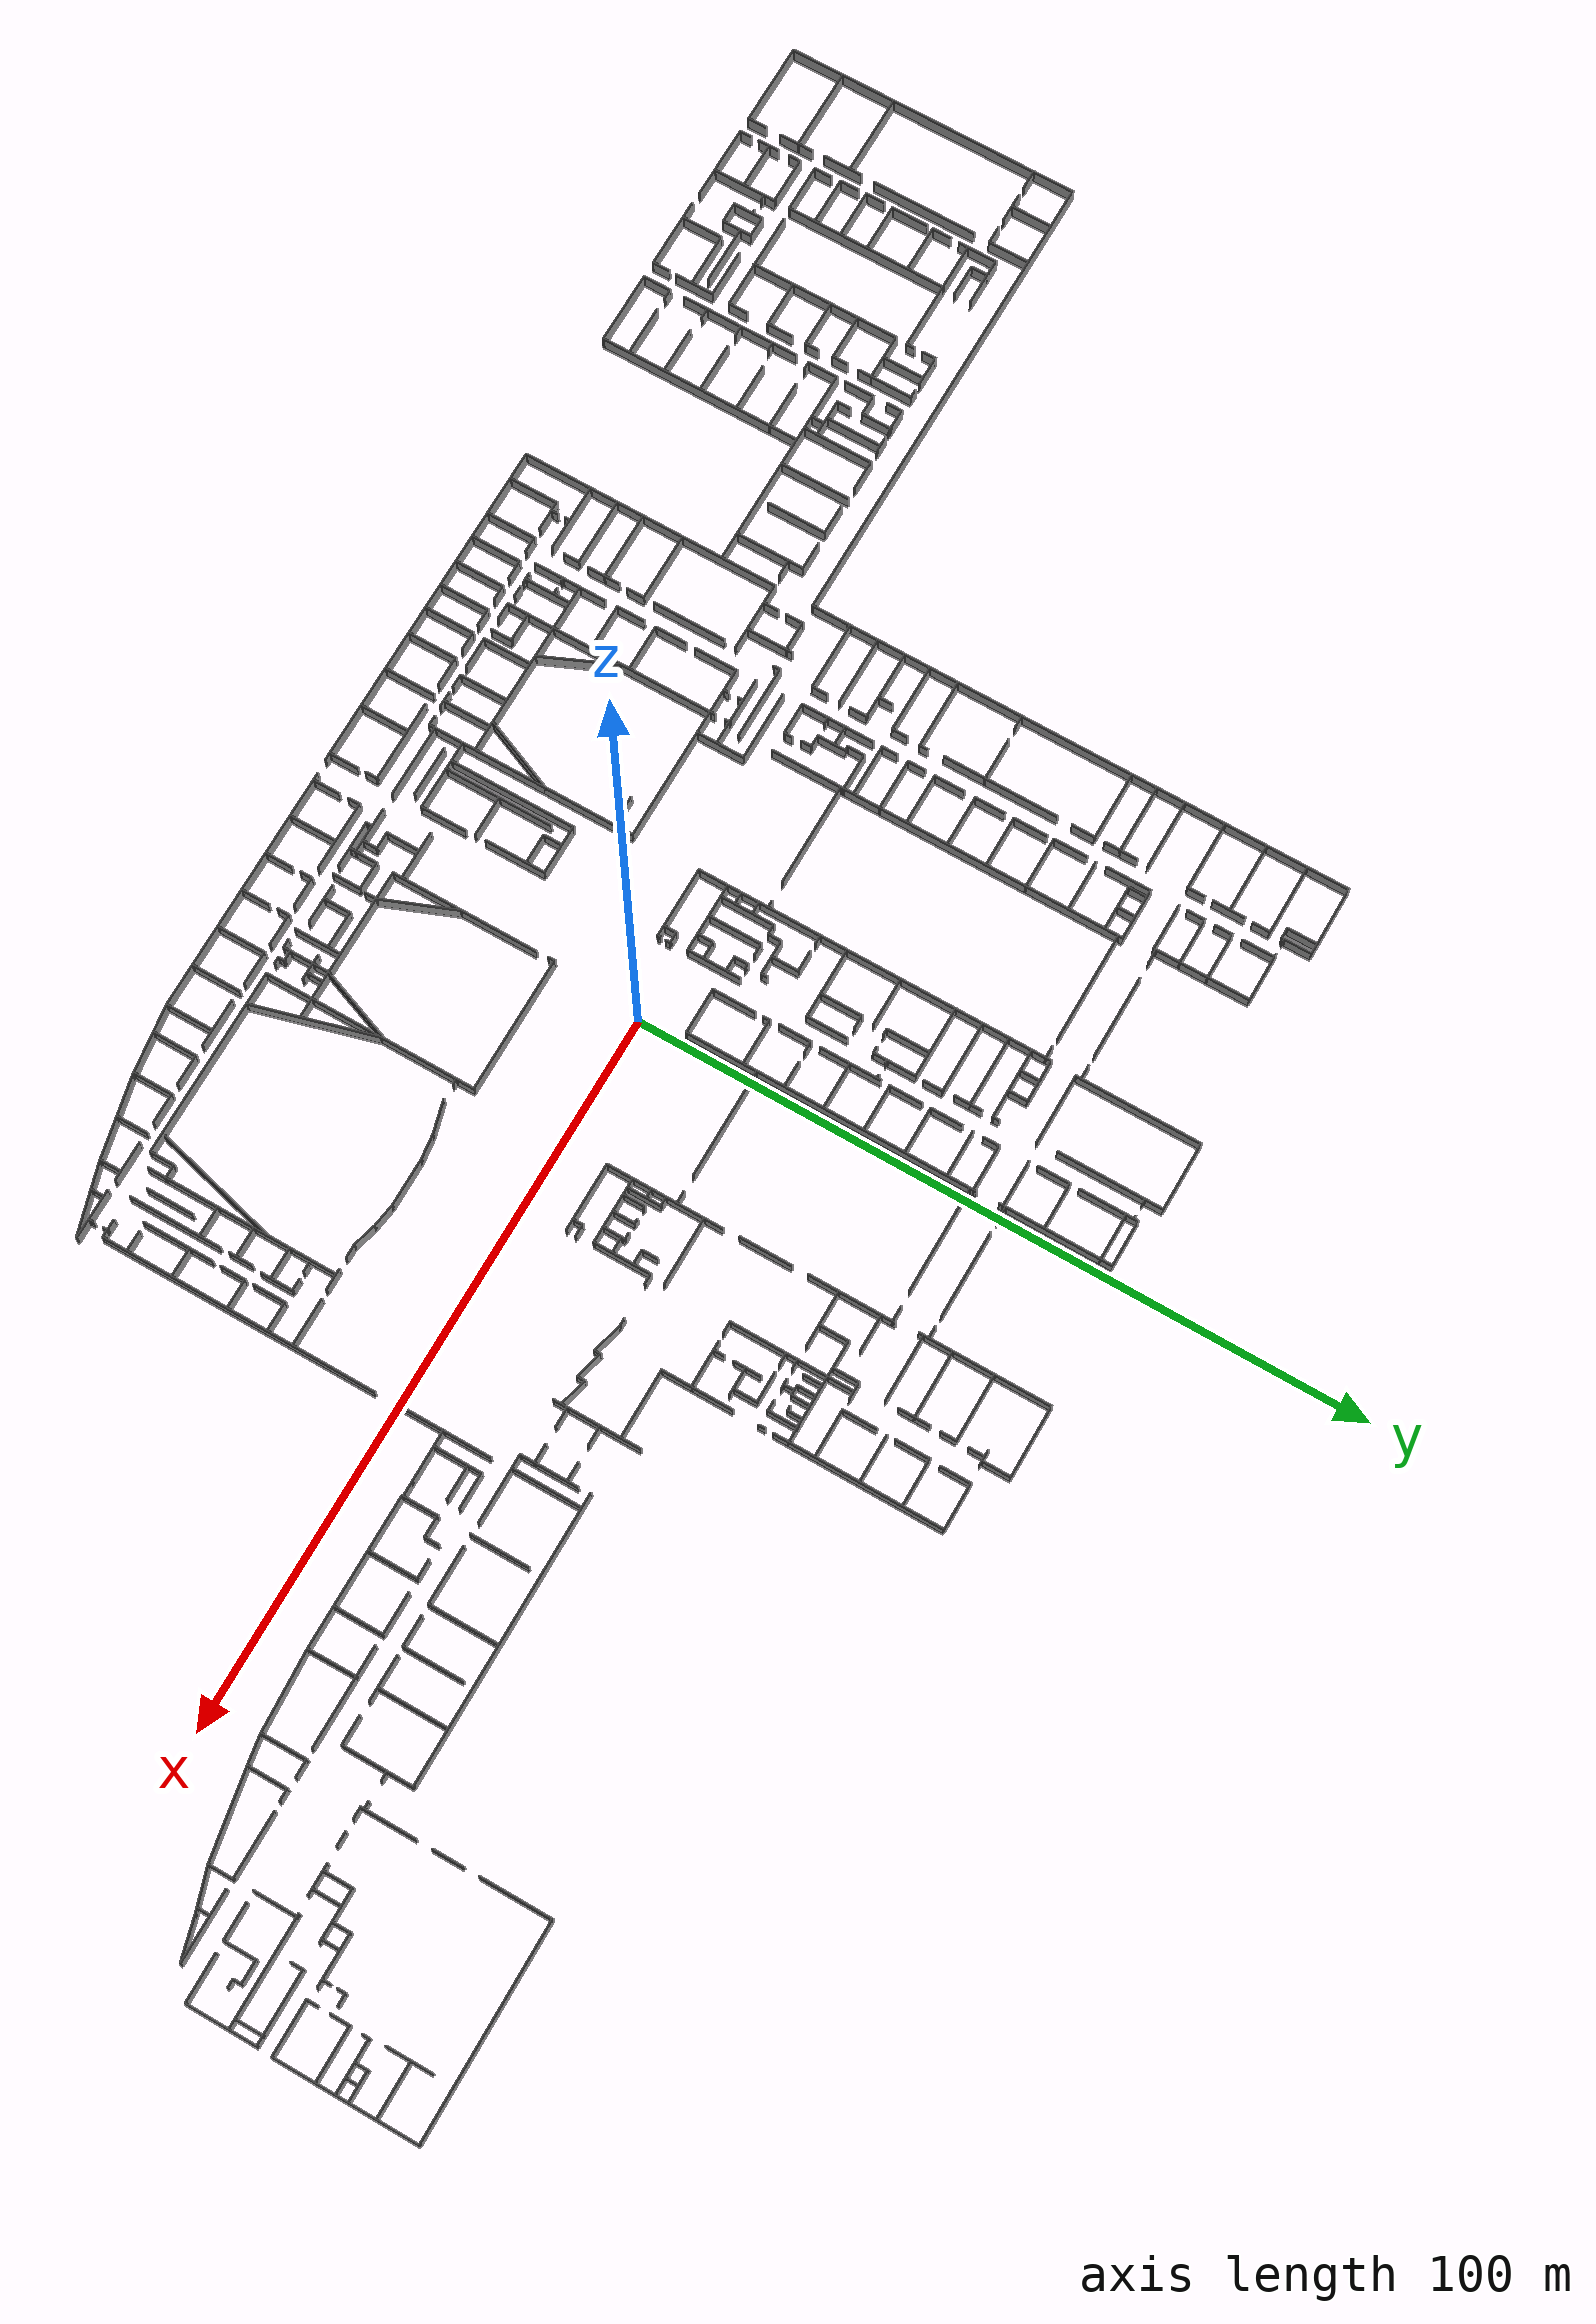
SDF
<?xml version='1.0'?>
<sdf version='1.6'>
  <model name='ensta_portes'>
    <pose frame=''>1.28297 8.11006 0 0 -0 0</pose>
    <link name='Wall_1'>
      <collision name='Wall_1_Collision'>
        <geometry>
          <box>
            <size>7.5 0.15 2.5</size>
          </box>
        </geometry>
        <pose frame=''>0 0 1.25 0 -0 0</pose>
      </collision>
      <visual name='Wall_1_Visual'>
        <pose frame=''>0 0 1.25 0 -0 0</pose>
        <geometry>
          <box>
            <size>7.5 0.15 2.5</size>
          </box>
        </geometry>
        <material>
          <script>
            <uri>file://media/materials/scripts/gazebo.material</uri>
            <name>Gazebo/Grey</name>
          </script>
          <ambient>1 1 1 1</ambient>
        </material>
        <meta>
          <layer>0</layer>
        </meta>
      </visual>
      <pose frame=''>96.6871 16.6258 0 0 -0 -1.5708</pose>
    </link>
    <link name='Wall_10'>
      <collision name='Wall_10_Collision'>
        <geometry>
          <box>
            <size>19.5 0.15 2.5</size>
          </box>
        </geometry>
        <pose frame=''>0 0 1.25 0 -0 0</pose>
      </collision>
      <visual name='Wall_10_Visual'>
        <pose frame=''>0 0 1.25 0 -0 0</pose>
        <geometry>
          <box>
            <size>19.5 0.15 2.5</size>
          </box>
        </geometry>
        <material>
          <script>
            <uri>file://media/materials/scripts/gazebo.material</uri>
            <name>Gazebo/Grey</name>
          </script>
          <ambient>1 1 1 1</ambient>
        </material>
        <meta>
          <layer>0</layer>
        </meta>
      </visual>
      <pose frame=''>125.525 28.7456 0 0 -0 -1.5708</pose>
    </link>
    <link name='Wall_1000'>
      <collision name='Wall_1000_Collision'>
        <geometry>
          <box>
            <size>8.5 0.15 2.5</size>
          </box>
        </geometry>
        <pose frame=''>0 0 1.25 0 -0 0</pose>
      </collision>
      <visual name='Wall_1000_Visual'>
        <pose frame=''>0 0 1.25 0 -0 0</pose>
        <geometry>
          <box>
            <size>8.5 0.15 2.5</size>
          </box>
        </geometry>
        <material>
          <script>
            <uri>file://media/materials/scripts/gazebo.material</uri>
            <name>Gazebo/Grey</name>
          </script>
          <ambient>1 1 1 1</ambient>
        </material>
        <meta>
          <layer>0</layer>
        </meta>
      </visual>
      <pose frame=''>-11.467 -31.6621 0 0 -0 -1.5708</pose>
    </link>
    <link name='Wall_1002'>
      <collision name='Wall_1002_Collision'>
        <geometry>
          <box>
            <size>2.75 0.15 2.5</size>
          </box>
        </geometry>
        <pose frame=''>0 0 1.25 0 -0 0</pose>
      </collision>
      <visual name='Wall_1002_Visual'>
        <pose frame=''>0 0 1.25 0 -0 0</pose>
        <geometry>
          <box>
            <size>2.75 0.15 2.5</size>
          </box>
        </geometry>
        <material>
          <script>
            <uri>file://media/materials/scripts/gazebo.material</uri>
            <name>Gazebo/Grey</name>
          </script>
          <ambient>1 1 1 1</ambient>
        </material>
        <meta>
          <layer>0</layer>
        </meta>
      </visual>
      <pose frame=''>-15.6191 -28.8016 0 0 -0 -1.5708</pose>
    </link>
    <link name='Wall_1003'>
      <collision name='Wall_1003_Collision'>
        <geometry>
          <box>
            <size>4.25 0.15 2.5</size>
          </box>
        </geometry>
        <pose frame=''>0 0 1.25 0 -0 0</pose>
      </collision>
      <visual name='Wall_1003_Visual'>
        <pose frame=''>0 0 1.25 0 -0 0</pose>
        <geometry>
          <box>
            <size>4.25 0.15 2.5</size>
          </box>
        </geometry>
        <material>
          <script>
            <uri>file://media/materials/scripts/gazebo.material</uri>
            <name>Gazebo/Grey</name>
          </script>
          <ambient>1 1 1 1</ambient>
        </material>
        <meta>
          <layer>0</layer>
        </meta>
      </visual>
      <pose frame=''>-13.5691 -30.1016 0 0 -0 0</pose>
    </link>
    <link name='Wall_1005'>
      <collision name='Wall_1005_Collision'>
        <geometry>
          <box>
            <size>15 0.15 2.5</size>
          </box>
        </geometry>
        <pose frame=''>0 0 1.25 0 -0 0</pose>
      </collision>
      <visual name='Wall_1005_Visual'>
        <pose frame=''>0 0 1.25 0 -0 0</pose>
        <geometry>
          <box>
            <size>15 0.15 2.5</size>
          </box>
        </geometry>
        <material>
          <script>
            <uri>file://media/materials/scripts/gazebo.material</uri>
            <name>Gazebo/Grey</name>
          </script>
          <ambient>1 1 1 1</ambient>
        </material>
        <meta>
          <layer>0</layer>
        </meta>
      </visual>
      <pose frame=''>-17.1319 -37.4221 0 0 -0 -1.5708</pose>
    </link>
    <link name='Wall_1007'>
      <collision name='Wall_1007_Collision'>
        <geometry>
          <box>
            <size>5.75 0.15 2.5</size>
          </box>
        </geometry>
        <pose frame=''>0 0 1.25 0 -0 0</pose>
      </collision>
      <visual name='Wall_1007_Visual'>
        <pose frame=''>0 0 1.25 0 -0 0</pose>
        <geometry>
          <box>
            <size>5.75 0.15 2.5</size>
          </box>
        </geometry>
        <material>
          <script>
            <uri>file://media/materials/scripts/gazebo.material</uri>
            <name>Gazebo/Grey</name>
          </script>
          <ambient>1 1 1 1</ambient>
        </material>
        <meta>
          <layer>0</layer>
        </meta>
      </visual>
      <pose frame=''>-14.2919 -37.3571 0 0 -0 0</pose>
    </link>
    <link name='Wall_1009'>
      <collision name='Wall_1009_Collision'>
        <geometry>
          <box>
            <size>6.39885 0.15 2.5</size>
          </box>
        </geometry>
        <pose frame=''>0 0 1.25 0 -0 0</pose>
      </collision>
      <visual name='Wall_1009_Visual'>
        <pose frame=''>0 0 1.25 0 -0 0</pose>
        <geometry>
          <box>
            <size>6.39885 0.15 2.5</size>
          </box>
        </geometry>
        <material>
          <script>
            <uri>file://media/materials/scripts/gazebo.material</uri>
            <name>Gazebo/Grey</name>
          </script>
          <ambient>1 1 1 1</ambient>
        </material>
        <meta>
          <layer>0</layer>
        </meta>
      </visual>
      <pose frame=''>-11.3009 -41.825 0 0 -0 -1.56909</pose>
    </link>
    <link name='Wall_101'>
      <collision name='Wall_101_Collision'>
        <geometry>
          <box>
            <size>9.75 0.15 2.5</size>
          </box>
        </geometry>
        <pose frame=''>0 0 1.25 0 -0 0</pose>
      </collision>
      <visual name='Wall_101_Visual'>
        <pose frame=''>0 0 1.25 0 -0 0</pose>
        <geometry>
          <box>
            <size>9.75 0.15 2.5</size>
          </box>
        </geometry>
        <material>
          <script>
            <uri>file://media/materials/scripts/gazebo.material</uri>
            <name>Gazebo/Grey</name>
          </script>
          <ambient>1 1 1 1</ambient>
        </material>
        <meta>
          <layer>0</layer>
        </meta>
      </visual>
      <pose frame=''>88.9702 4.63615 0 0 -0 3.14159</pose>
    </link>
    <link name='Wall_1011'>
      <collision name='Wall_1011_Collision'>
        <geometry>
          <box>
            <size>6.5 0.15 2.5</size>
          </box>
        </geometry>
        <pose frame=''>0 0 1.25 0 -0 0</pose>
      </collision>
      <visual name='Wall_1011_Visual'>
        <pose frame=''>0 0 1.25 0 -0 0</pose>
        <geometry>
          <box>
            <size>6.5 0.15 2.5</size>
          </box>
        </geometry>
        <material>
          <script>
            <uri>file://media/materials/scripts/gazebo.material</uri>
            <name>Gazebo/Grey</name>
          </script>
          <ambient>1 1 1 1</ambient>
        </material>
        <meta>
          <layer>0</layer>
        </meta>
      </visual>
      <pose frame=''>-5.45647 -48.8577 0 0 -0 0</pose>
    </link>
    <link name='Wall_1013'>
      <collision name='Wall_1013_Collision'>
        <geometry>
          <box>
            <size>6.75 0.15 2.5</size>
          </box>
        </geometry>
        <pose frame=''>0 0 1.25 0 -0 0</pose>
      </collision>
      <visual name='Wall_1013_Visual'>
        <pose frame=''>0 0 1.25 0 -0 0</pose>
        <geometry>
          <box>
            <size>6.75 0.15 2.5</size>
          </box>
        </geometry>
        <material>
          <script>
            <uri>file://media/materials/scripts/gazebo.material</uri>
            <name>Gazebo/Grey</name>
          </script>
          <ambient>1 1 1 1</ambient>
        </material>
        <meta>
          <layer>0</layer>
        </meta>
      </visual>
      <pose frame=''>-5.63393 -42.2036 0 0 -0 0</pose>
    </link>
    <link name='Wall_1015'>
      <collision name='Wall_1015_Collision'>
        <geometry>
          <box>
            <size>4.75 0.15 2.5</size>
          </box>
        </geometry>
        <pose frame=''>0 0 1.25 0 -0 0</pose>
      </collision>
      <visual name='Wall_1015_Visual'>
        <pose frame=''>0 0 1.25 0 -0 0</pose>
        <geometry>
          <box>
            <size>4.75 0.15 2.5</size>
          </box>
        </geometry>
        <material>
          <script>
            <uri>file://media/materials/scripts/gazebo.material</uri>
            <name>Gazebo/Grey</name>
          </script>
          <ambient>1 1 1 1</ambient>
        </material>
        <meta>
          <layer>0</layer>
        </meta>
      </visual>
      <pose frame=''>-6.2723 -44.5419 0 0 -0 -1.5708</pose>
    </link>
    <link name='Wall_1016'>
      <collision name='Wall_1016_Collision'>
        <geometry>
          <box>
            <size>2.5 0.15 2.5</size>
          </box>
        </geometry>
        <pose frame=''>0 0 1.25 0 -0 0</pose>
      </collision>
      <visual name='Wall_1016_Visual'>
        <pose frame=''>0 0 1.25 0 -0 0</pose>
        <geometry>
          <box>
            <size>2.5 0.15 2.5</size>
          </box>
        </geometry>
        <material>
          <script>
            <uri>file://media/materials/scripts/gazebo.material</uri>
            <name>Gazebo/Grey</name>
          </script>
          <ambient>1 1 1 1</ambient>
        </material>
        <meta>
          <layer>0</layer>
        </meta>
      </visual>
      <pose frame=''>-5.0973 -46.8419 0 0 -0 0</pose>
    </link>
    <link name='Wall_1017'>
      <collision name='Wall_1017_Collision'>
        <geometry>
          <box>
            <size>2.12495 0.15 2.5</size>
          </box>
        </geometry>
        <pose frame=''>0 0 1.25 0 -0 0</pose>
      </collision>
      <visual name='Wall_1017_Visual'>
        <pose frame=''>0 0 1.25 0 -0 0</pose>
        <geometry>
          <box>
            <size>2.12495 0.15 2.5</size>
          </box>
        </geometry>
        <material>
          <script>
            <uri>file://media/materials/scripts/gazebo.material</uri>
            <name>Gazebo/Grey</name>
          </script>
          <ambient>1 1 1 1</ambient>
        </material>
        <meta>
          <layer>0</layer>
        </meta>
      </visual>
      <pose frame=''>-3.92825 -47.8293 0 0 -0 -1.57682</pose>
    </link>
    <link name='Wall_1019'>
      <collision name='Wall_1019_Collision'>
        <geometry>
          <box>
            <size>4 0.15 2.5</size>
          </box>
        </geometry>
        <pose frame=''>0 0 1.25 0 -0 0</pose>
      </collision>
      <visual name='Wall_1019_Visual'>
        <pose frame=''>0 0 1.25 0 -0 0</pose>
        <geometry>
          <box>
            <size>4 0.15 2.5</size>
          </box>
        </geometry>
        <material>
          <script>
            <uri>file://media/materials/scripts/gazebo.material</uri>
            <name>Gazebo/Grey</name>
          </script>
          <ambient>1 1 1 1</ambient>
        </material>
        <meta>
          <layer>0</layer>
        </meta>
      </visual>
      <pose frame=''>-2.29279 -47.788 0 0 -0 -1.5708</pose>
    </link>
    <link name='Wall_102'>
      <collision name='Wall_102_Collision'>
        <geometry>
          <box>
            <size>6.72494 0.15 2.5</size>
          </box>
        </geometry>
        <pose frame=''>0 0 1.25 0 -0 0</pose>
      </collision>
      <visual name='Wall_102_Visual'>
        <pose frame=''>0 0 1.25 0 -0 0</pose>
        <geometry>
          <box>
            <size>6.72494 0.15 2.5</size>
          </box>
        </geometry>
        <material>
          <script>
            <uri>file://media/materials/scripts/gazebo.material</uri>
            <name>Gazebo/Grey</name>
          </script>
          <ambient>1 1 1 1</ambient>
        </material>
        <meta>
          <layer>0</layer>
        </meta>
      </visual>
      <pose frame=''>84.207 1.34889 0 0 -0 -1.5596</pose>
    </link>
    <link name='Wall_1020'>
      <collision name='Wall_1020_Collision'>
        <geometry>
          <box>
            <size>4 0.15 2.5</size>
          </box>
        </geometry>
        <pose frame=''>0 0 1.25 0 -0 0</pose>
      </collision>
      <visual name='Wall_1020_Visual'>
        <pose frame=''>0 0 1.25 0 -0 0</pose>
        <geometry>
          <box>
            <size>4 0.15 2.5</size>
          </box>
        </geometry>
        <material>
          <script>
            <uri>file://media/materials/scripts/gazebo.material</uri>
            <name>Gazebo/Grey</name>
          </script>
          <ambient>1 1 1 1</ambient>
        </material>
        <meta>
          <layer>0</layer>
        </meta>
      </visual>
      <pose frame=''>-4.21779 -49.713 0 0 -0 3.14159</pose>
    </link>
    <link name='Wall_1021'>
      <collision name='Wall_1021_Collision'>
        <geometry>
          <box>
            <size>1 0.15 2.5</size>
          </box>
        </geometry>
        <pose frame=''>0 0 1.25 0 -0 0</pose>
      </collision>
      <visual name='Wall_1021_Visual'>
        <pose frame=''>0 0 1.25 0 -0 0</pose>
        <geometry>
          <box>
            <size>1 0.15 2.5</size>
          </box>
        </geometry>
        <material>
          <script>
            <uri>file://media/materials/scripts/gazebo.material</uri>
            <name>Gazebo/Grey</name>
          </script>
          <ambient>1 1 1 1</ambient>
        </material>
        <meta>
          <layer>0</layer>
        </meta>
      </visual>
      <pose frame=''>-6.14279 -49.288 0 0 -0 1.5708</pose>
    </link>
    <link name='Wall_1023'>
      <collision name='Wall_1023_Collision'>
        <geometry>
          <box>
            <size>4 0.15 2.5</size>
          </box>
        </geometry>
        <pose frame=''>0 0 1.25 0 -0 0</pose>
      </collision>
      <visual name='Wall_1023_Visual'>
        <pose frame=''>0 0 1.25 0 -0 0</pose>
        <geometry>
          <box>
            <size>4 0.15 2.5</size>
          </box>
        </geometry>
        <material>
          <script>
            <uri>file://media/materials/scripts/gazebo.material</uri>
            <name>Gazebo/Grey</name>
          </script>
          <ambient>1 1 1 1</ambient>
        </material>
        <meta>
          <layer>0</layer>
        </meta>
      </visual>
      <pose frame=''>-0.367791 -45.863 0 0 -0 0</pose>
    </link>
    <link name='Wall_1024'>
      <collision name='Wall_1024_Collision'>
        <geometry>
          <box>
            <size>4 0.15 2.5</size>
          </box>
        </geometry>
        <pose frame=''>0 0 1.25 0 -0 0</pose>
      </collision>
      <visual name='Wall_1024_Visual'>
        <pose frame=''>0 0 1.25 0 -0 0</pose>
        <geometry>
          <box>
            <size>4 0.15 2.5</size>
          </box>
        </geometry>
        <material>
          <script>
            <uri>file://media/materials/scripts/gazebo.material</uri>
            <name>Gazebo/Grey</name>
          </script>
          <ambient>1 1 1 1</ambient>
        </material>
        <meta>
          <layer>0</layer>
        </meta>
      </visual>
      <pose frame=''>1.55721 -47.788 0 0 -0 -1.5708</pose>
    </link>
    <link name='Wall_1026'>
      <collision name='Wall_1026_Collision'>
        <geometry>
          <box>
            <size>2.75 0.15 2.5</size>
          </box>
        </geometry>
        <pose frame=''>0 0 1.25 0 -0 0</pose>
      </collision>
      <visual name='Wall_1026_Visual'>
        <pose frame=''>0 0 1.25 0 -0 0</pose>
        <geometry>
          <box>
            <size>2.75 0.15 2.5</size>
          </box>
        </geometry>
        <material>
          <script>
            <uri>file://media/materials/scripts/gazebo.material</uri>
            <name>Gazebo/Grey</name>
          </script>
          <ambient>1 1 1 1</ambient>
        </material>
        <meta>
          <layer>0</layer>
        </meta>
      </visual>
      <pose frame=''>-0.992791 -49.713 0 0 -0 0</pose>
    </link>
    <link name='Wall_1028'>
      <collision name='Wall_1028_Collision'>
        <geometry>
          <box>
            <size>20.5 0.15 2.5</size>
          </box>
        </geometry>
        <pose frame=''>0 0 1.25 0 -0 0</pose>
      </collision>
      <visual name='Wall_1028_Visual'>
        <pose frame=''>0 0 1.25 0 -0 0</pose>
        <geometry>
          <box>
            <size>20.5 0.15 2.5</size>
          </box>
        </geometry>
        <material>
          <script>
            <uri>file://media/materials/scripts/gazebo.material</uri>
            <name>Gazebo/Grey</name>
          </script>
          <ambient>1 1 1 1</ambient>
        </material>
        <meta>
          <layer>0</layer>
        </meta>
      </visual>
      <pose frame=''>-2.18392 -33.2842 0 0 -0 -1.5708</pose>
    </link>
    <link name='Wall_1030'>
      <collision name='Wall_1030_Collision'>
        <geometry>
          <box>
            <size>18.75 0.15 2.5</size>
          </box>
        </geometry>
        <pose frame=''>0 0 1.25 0 -0 0</pose>
      </collision>
      <visual name='Wall_1030_Visual'>
        <pose frame=''>0 0 1.25 0 -0 0</pose>
        <geometry>
          <box>
            <size>18.75 0.15 2.5</size>
          </box>
        </geometry>
        <material>
          <script>
            <uri>file://media/materials/scripts/gazebo.material</uri>
            <name>Gazebo/Grey</name>
          </script>
          <ambient>1 1 1 1</ambient>
        </material>
        <meta>
          <layer>0</layer>
        </meta>
      </visual>
      <pose frame=''>7.11608 -43.4592 0 0 -0 0</pose>
    </link>
    <link name='Wall_1032'>
      <collision name='Wall_1032_Collision'>
        <geometry>
          <box>
            <size>1 0.15 2.5</size>
          </box>
        </geometry>
        <pose frame=''>0 0 1.25 0 -0 0</pose>
      </collision>
      <visual name='Wall_1032_Visual'>
        <pose frame=''>0 0 1.25 0 -0 0</pose>
        <geometry>
          <box>
            <size>1 0.15 2.5</size>
          </box>
        </geometry>
        <material>
          <script>
            <uri>file://media/materials/scripts/gazebo.material</uri>
            <name>Gazebo/Grey</name>
          </script>
          <ambient>1 1 1 1</ambient>
        </material>
        <meta>
          <layer>0</layer>
        </meta>
      </visual>
      <pose frame=''>-2.29047 -20.9877 0 0 -0 1.5708</pose>
    </link>
    <link name='Wall_1033'>
      <collision name='Wall_1033_Collision'>
        <geometry>
          <box>
            <size>19 0.15 2.5</size>
          </box>
        </geometry>
        <pose frame=''>0 0 1.25 0 -0 0</pose>
      </collision>
      <visual name='Wall_1033_Visual'>
        <pose frame=''>0 0 1.25 0 -0 0</pose>
        <geometry>
          <box>
            <size>19 0.15 2.5</size>
          </box>
        </geometry>
        <material>
          <script>
            <uri>file://media/materials/scripts/gazebo.material</uri>
            <name>Gazebo/Grey</name>
          </script>
          <ambient>1 1 1 1</ambient>
        </material>
        <meta>
          <layer>0</layer>
        </meta>
      </visual>
      <pose frame=''>7.13453 -20.5627 0 0 -0 0</pose>
    </link>
    <link name='Wall_1035'>
      <collision name='Wall_1035_Collision'>
        <geometry>
          <box>
            <size>29.5 0.15 2.5</size>
          </box>
        </geometry>
        <pose frame=''>0 0 1.25 0 -0 0</pose>
      </collision>
      <visual name='Wall_1035_Visual'>
        <pose frame=''>0 0 1.25 0 -0 0</pose>
        <geometry>
          <box>
            <size>29.5 0.15 2.5</size>
          </box>
        </geometry>
        <material>
          <script>
            <uri>file://media/materials/scripts/gazebo.material</uri>
            <name>Gazebo/Grey</name>
          </script>
          <ambient>1 1 1 1</ambient>
        </material>
        <meta>
          <layer>0</layer>
        </meta>
      </visual>
      <pose frame=''>16.5595 -35.2377 0 0 -0 -1.5708</pose>
    </link>
    <link name='Wall_104'>
      <collision name='Wall_104_Collision'>
        <geometry>
          <box>
            <size>4.25 0.15 2.5</size>
          </box>
        </geometry>
        <pose frame=''>0 0 1.25 0 -0 0</pose>
      </collision>
      <visual name='Wall_104_Visual'>
        <pose frame=''>0 0 1.25 0 -0 0</pose>
        <geometry>
          <box>
            <size>4.25 0.15 2.5</size>
          </box>
        </geometry>
        <material>
          <script>
            <uri>file://media/materials/scripts/gazebo.material</uri>
            <name>Gazebo/Grey</name>
          </script>
          <ambient>1 1 1 1</ambient>
        </material>
        <meta>
          <layer>0</layer>
        </meta>
      </visual>
      <pose frame=''>82.1202 4.63615 0 0 -0 0</pose>
    </link>
    <link name='Wall_1041'>
      <collision name='Wall_1041_Collision'>
        <geometry>
          <box>
            <size>1.75 0.15 2.5</size>
          </box>
        </geometry>
        <pose frame=''>0 0 1.25 0 -0 0</pose>
      </collision>
      <visual name='Wall_1041_Visual'>
        <pose frame=''>0 0 1.25 0 -0 0</pose>
        <geometry>
          <box>
            <size>1.75 0.15 2.5</size>
          </box>
        </geometry>
        <material>
          <script>
            <uri>file://media/materials/scripts/gazebo.material</uri>
            <name>Gazebo/Grey</name>
          </script>
          <ambient>1 1 1 1</ambient>
        </material>
        <meta>
          <layer>0</layer>
        </meta>
      </visual>
      <pose frame=''>1.6944 -44.2524 0 0 -0 -1.5708</pose>
    </link>
    <link name='Wall_1043'>
      <collision name='Wall_1043_Collision'>
        <geometry>
          <box>
            <size>5.5 0.15 2.5</size>
          </box>
        </geometry>
        <pose frame=''>0 0 1.25 0 -0 0</pose>
      </collision>
      <visual name='Wall_1043_Visual'>
        <pose frame=''>0 0 1.25 0 -0 0</pose>
        <geometry>
          <box>
            <size>5.5 0.15 2.5</size>
          </box>
        </geometry>
        <material>
          <script>
            <uri>file://media/materials/scripts/gazebo.material</uri>
            <name>Gazebo/Grey</name>
          </script>
          <ambient>1 1 1 1</ambient>
        </material>
        <meta>
          <layer>0</layer>
        </meta>
      </visual>
      <pose frame=''>5.65013 -48.9641 0 0 -0 0</pose>
    </link>
    <link name='Wall_1045'>
      <collision name='Wall_1045_Collision'>
        <geometry>
          <box>
            <size>3.75 0.15 2.5</size>
          </box>
        </geometry>
        <pose frame=''>0 0 1.25 0 -0 0</pose>
      </collision>
      <visual name='Wall_1045_Visual'>
        <pose frame=''>0 0 1.25 0 -0 0</pose>
        <geometry>
          <box>
            <size>3.75 0.15 2.5</size>
          </box>
        </geometry>
        <material>
          <script>
            <uri>file://media/materials/scripts/gazebo.material</uri>
            <name>Gazebo/Grey</name>
          </script>
          <ambient>1 1 1 1</ambient>
        </material>
        <meta>
          <layer>0</layer>
        </meta>
      </visual>
      <pose frame=''>4.85048 -47.0727 0 0 -0 1.5708</pose>
    </link>
    <link name='Wall_1046'>
      <collision name='Wall_1046_Collision'>
        <geometry>
          <box>
            <size>5.25 0.15 2.5</size>
          </box>
        </geometry>
        <pose frame=''>0 0 1.25 0 -0 0</pose>
      </collision>
      <visual name='Wall_1046_Visual'>
        <pose frame=''>0 0 1.25 0 -0 0</pose>
        <geometry>
          <box>
            <size>5.25 0.15 2.5</size>
          </box>
        </geometry>
        <material>
          <script>
            <uri>file://media/materials/scripts/gazebo.material</uri>
            <name>Gazebo/Grey</name>
          </script>
          <ambient>1 1 1 1</ambient>
        </material>
        <meta>
          <layer>0</layer>
        </meta>
      </visual>
      <pose frame=''>7.40048 -45.2726 0 0 -0 0</pose>
    </link>
    <link name='Wall_1048'>
      <collision name='Wall_1048_Collision'>
        <geometry>
          <box>
            <size>6.5 0.15 2.5</size>
          </box>
        </geometry>
        <pose frame=''>0 0 1.25 0 -0 0</pose>
      </collision>
      <visual name='Wall_1048_Visual'>
        <pose frame=''>0 0 1.25 0 -0 0</pose>
        <geometry>
          <box>
            <size>6.5 0.15 2.5</size>
          </box>
        </geometry>
        <material>
          <script>
            <uri>file://media/materials/scripts/gazebo.material</uri>
            <name>Gazebo/Grey</name>
          </script>
          <ambient>1 1 1 1</ambient>
        </material>
        <meta>
          <layer>0</layer>
        </meta>
      </visual>
      <pose frame=''>9.95052 -46.7189 0 0 -0 -1.5708</pose>
    </link>
    <link name='Wall_1050'>
      <collision name='Wall_1050_Collision'>
        <geometry>
          <box>
            <size>1.25 0.15 2.5</size>
          </box>
        </geometry>
        <pose frame=''>0 0 1.25 0 -0 0</pose>
      </collision>
      <visual name='Wall_1050_Visual'>
        <pose frame=''>0 0 1.25 0 -0 0</pose>
        <geometry>
          <box>
            <size>1.25 0.15 2.5</size>
          </box>
        </geometry>
        <material>
          <script>
            <uri>file://media/materials/scripts/gazebo.material</uri>
            <name>Gazebo/Grey</name>
          </script>
          <ambient>1 1 1 1</ambient>
        </material>
        <meta>
          <layer>0</layer>
        </meta>
      </visual>
      <pose frame=''>12.1014 -49.9018 0 0 -0 0</pose>
    </link>
    <link name='Wall_1051'>
      <collision name='Wall_1051_Collision'>
        <geometry>
          <box>
            <size>6.5 0.15 2.5</size>
          </box>
        </geometry>
        <pose frame=''>0 0 1.25 0 -0 0</pose>
      </collision>
      <visual name='Wall_1051_Visual'>
        <pose frame=''>0 0 1.25 0 -0 0</pose>
        <geometry>
          <box>
            <size>6.5 0.15 2.5</size>
          </box>
        </geometry>
        <material>
          <script>
            <uri>file://media/materials/scripts/gazebo.material</uri>
            <name>Gazebo/Grey</name>
          </script>
          <ambient>1 1 1 1</ambient>
        </material>
        <meta>
          <layer>0</layer>
        </meta>
      </visual>
      <pose frame=''>12.6743 -46.6811 0 0 -0 1.5708</pose>
    </link>
    <link name='Wall_1053'>
      <collision name='Wall_1053_Collision'>
        <geometry>
          <box>
            <size>1.25 0.15 2.5</size>
          </box>
        </geometry>
        <pose frame=''>0 0 1.25 0 -0 0</pose>
      </collision>
      <visual name='Wall_1053_Visual'>
        <pose frame=''>0 0 1.25 0 -0 0</pose>
        <geometry>
          <box>
            <size>1.25 0.15 2.5</size>
          </box>
        </geometry>
        <material>
          <script>
            <uri>file://media/materials/scripts/gazebo.material</uri>
            <name>Gazebo/Grey</name>
          </script>
          <ambient>1 1 1 1</ambient>
        </material>
        <meta>
          <layer>0</layer>
        </meta>
      </visual>
      <pose frame=''>12.0455 -45.7063 0 0 -0 0</pose>
    </link>
    <link name='Wall_1055'>
      <collision name='Wall_1055_Collision'>
        <geometry>
          <box>
            <size>2.5 0.15 2.5</size>
          </box>
        </geometry>
        <pose frame=''>0 0 1.25 0 -0 0</pose>
      </collision>
      <visual name='Wall_1055_Visual'>
        <pose frame=''>0 0 1.25 0 -0 0</pose>
        <geometry>
          <box>
            <size>2.5 0.15 2.5</size>
          </box>
        </geometry>
        <material>
          <script>
            <uri>file://media/materials/scripts/gazebo.material</uri>
            <name>Gazebo/Grey</name>
          </script>
          <ambient>1 1 1 1</ambient>
        </material>
        <meta>
          <layer>0</layer>
        </meta>
      </visual>
      <pose frame=''>13.7705 -45.7063 0 0 -0 0</pose>
    </link>
    <link name='Wall_1057'>
      <collision name='Wall_1057_Collision'>
        <geometry>
          <box>
            <size>2.25 0.15 2.5</size>
          </box>
        </geometry>
        <pose frame=''>0 0 1.25 0 -0 0</pose>
      </collision>
      <visual name='Wall_1057_Visual'>
        <pose frame=''>0 0 1.25 0 -0 0</pose>
        <geometry>
          <box>
            <size>2.25 0.15 2.5</size>
          </box>
        </geometry>
        <material>
          <script>
            <uri>file://media/materials/scripts/gazebo.material</uri>
            <name>Gazebo/Grey</name>
          </script>
          <ambient>1 1 1 1</ambient>
        </material>
        <meta>
          <layer>0</layer>
        </meta>
      </visual>
      <pose frame=''>14.017 -44.6635 0 0 -0 -1.5708</pose>
    </link>
    <link name='Wall_1059'>
      <collision name='Wall_1059_Collision'>
        <geometry>
          <box>
            <size>1.5 0.15 2.5</size>
          </box>
        </geometry>
        <pose frame=''>0 0 1.25 0 -0 0</pose>
      </collision>
      <visual name='Wall_1059_Visual'>
        <pose frame=''>0 0 1.25 0 -0 0</pose>
        <geometry>
          <box>
            <size>1.5 0.15 2.5</size>
          </box>
        </geometry>
        <material>
          <script>
            <uri>file://media/materials/scripts/gazebo.material</uri>
            <name>Gazebo/Grey</name>
          </script>
          <ambient>1 1 1 1</ambient>
        </material>
        <meta>
          <layer>0</layer>
        </meta>
      </visual>
      <pose frame=''>13.4001 -48.8861 0 0 -0 0</pose>
    </link>
    <link name='Wall_106'>
      <collision name='Wall_106_Collision'>
        <geometry>
          <box>
            <size>6.70303 0.15 2.5</size>
          </box>
        </geometry>
        <pose frame=''>0 0 1.25 0 -0 0</pose>
      </collision>
      <visual name='Wall_106_Visual'>
        <pose frame=''>0 0 1.25 0 -0 0</pose>
        <geometry>
          <box>
            <size>6.70303 0.15 2.5</size>
          </box>
        </geometry>
        <material>
          <script>
            <uri>file://media/materials/scripts/gazebo.material</uri>
            <name>Gazebo/Grey</name>
          </script>
          <ambient>1 1 1 1</ambient>
        </material>
        <meta>
          <layer>0</layer>
        </meta>
      </visual>
      <pose frame=''>78.4731 1.45917 0 0 -0 -1.57204</pose>
    </link>
    <link name='Wall_1060'>
      <collision name='Wall_1060_Collision'>
        <geometry>
          <box>
            <size>1 0.15 2.5</size>
          </box>
        </geometry>
        <pose frame=''>0 0 1.25 0 -0 0</pose>
      </collision>
      <visual name='Wall_1060_Visual'>
        <pose frame=''>0 0 1.25 0 -0 0</pose>
        <geometry>
          <box>
            <size>1 0.15 2.5</size>
          </box>
        </geometry>
        <material>
          <script>
            <uri>file://media/materials/scripts/gazebo.material</uri>
            <name>Gazebo/Grey</name>
          </script>
          <ambient>1 1 1 1</ambient>
        </material>
        <meta>
          <layer>0</layer>
        </meta>
      </visual>
      <pose frame=''>14.0751 -49.3111 0 0 -0 -1.5708</pose>
    </link>
    <link name='Wall_1061'>
      <collision name='Wall_1061_Collision'>
        <geometry>
          <box>
            <size>1 0.15 2.5</size>
          </box>
        </geometry>
        <pose frame=''>0 0 1.25 0 -0 0</pose>
      </collision>
      <visual name='Wall_1061_Visual'>
        <pose frame=''>0 0 1.25 0 -0 0</pose>
        <geometry>
          <box>
            <size>1 0.15 2.5</size>
          </box>
        </geometry>
        <material>
          <script>
            <uri>file://media/materials/scripts/gazebo.material</uri>
            <name>Gazebo/Grey</name>
          </script>
          <ambient>1 1 1 1</ambient>
        </material>
        <meta>
          <layer>0</layer>
        </meta>
      </visual>
      <pose frame=''>14.5001 -49.7361 0 0 -0 0</pose>
    </link>
    <link name='Wall_1065'>
      <collision name='Wall_1065_Collision'>
        <geometry>
          <box>
            <size>26.25 0.15 2.5</size>
          </box>
        </geometry>
        <pose frame=''>0 0 1.25 0 -0 0</pose>
      </collision>
      <visual name='Wall_1065_Visual'>
        <pose frame=''>0 0 1.25 0 -0 0</pose>
        <geometry>
          <box>
            <size>26.25 0.15 2.5</size>
          </box>
        </geometry>
        <material>
          <script>
            <uri>file://media/materials/scripts/gazebo.material</uri>
            <name>Gazebo/Grey</name>
          </script>
          <ambient>1 1 1 1</ambient>
        </material>
        <meta>
          <layer>0</layer>
        </meta>
      </visual>
      <pose frame=''>29.6095 -49.9127 0 0 -0 0</pose>
    </link>
    <link name='Wall_1066'>
      <collision name='Wall_1066_Collision'>
        <geometry>
          <box>
            <size>3.5 0.15 2.5</size>
          </box>
        </geometry>
        <pose frame=''>0 0 1.25 0 -0 0</pose>
      </collision>
      <visual name='Wall_1066_Visual'>
        <pose frame=''>0 0 1.25 0 -0 0</pose>
        <geometry>
          <box>
            <size>3.5 0.15 2.5</size>
          </box>
        </geometry>
        <material>
          <script>
            <uri>file://media/materials/scripts/gazebo.material</uri>
            <name>Gazebo/Grey</name>
          </script>
          <ambient>1 1 1 1</ambient>
        </material>
        <meta>
          <layer>0</layer>
        </meta>
      </visual>
      <pose frame=''>42.6595 -48.2377 0 0 -0 1.5708</pose>
    </link>
    <link name='Wall_1067'>
      <collision name='Wall_1067_Collision'>
        <geometry>
          <box>
            <size>2 0.15 2.5</size>
          </box>
        </geometry>
        <pose frame=''>0 0 1.25 0 -0 0</pose>
      </collision>
      <visual name='Wall_1067_Visual'>
        <pose frame=''>0 0 1.25 0 -0 0</pose>
        <geometry>
          <box>
            <size>2 0.15 2.5</size>
          </box>
        </geometry>
        <material>
          <script>
            <uri>file://media/materials/scripts/gazebo.material</uri>
            <name>Gazebo/Grey</name>
          </script>
          <ambient>1 1 1 1</ambient>
        </material>
        <meta>
          <layer>0</layer>
        </meta>
      </visual>
      <pose frame=''>43.5845 -46.5627 0 0 -0 0</pose>
    </link>
    <link name='Wall_1069'>
      <collision name='Wall_1069_Collision'>
        <geometry>
          <box>
            <size>2.75 0.15 2.5</size>
          </box>
        </geometry>
        <pose frame=''>0 0 1.25 0 -0 0</pose>
      </collision>
      <visual name='Wall_1069_Visual'>
        <pose frame=''>0 0 1.25 0 -0 0</pose>
        <geometry>
          <box>
            <size>2.75 0.15 2.5</size>
          </box>
        </geometry>
        <material>
          <script>
            <uri>file://media/materials/scripts/gazebo.material</uri>
            <name>Gazebo/Grey</name>
          </script>
          <ambient>1 1 1 1</ambient>
        </material>
        <meta>
          <layer>0</layer>
        </meta>
      </visual>
      <pose frame=''>17.9335 -43.4273 0 0 -0 0</pose>
    </link>
    <link name='Wall_1071'>
      <collision name='Wall_1071_Collision'>
        <geometry>
          <box>
            <size>0.75 0.15 2.5</size>
          </box>
        </geometry>
        <pose frame=''>0 0 1.25 0 -0 0</pose>
      </collision>
      <visual name='Wall_1071_Visual'>
        <pose frame=''>0 0 1.25 0 -0 0</pose>
        <geometry>
          <box>
            <size>0.75 0.15 2.5</size>
          </box>
        </geometry>
        <material>
          <script>
            <uri>file://media/materials/scripts/gazebo.material</uri>
            <name>Gazebo/Grey</name>
          </script>
          <ambient>1 1 1 1</ambient>
        </material>
        <meta>
          <layer>0</layer>
        </meta>
      </visual>
      <pose frame=''>16.9945 -23.01 0 0 -0 0</pose>
    </link>
    <link name='Wall_1073'>
      <collision name='Wall_1073_Collision'>
        <geometry>
          <box>
            <size>4.75 0.15 2.5</size>
          </box>
        </geometry>
        <pose frame=''>0 0 1.25 0 -0 0</pose>
      </collision>
      <visual name='Wall_1073_Visual'>
        <pose frame=''>0 0 1.25 0 -0 0</pose>
        <geometry>
          <box>
            <size>4.75 0.15 2.5</size>
          </box>
        </geometry>
        <material>
          <script>
            <uri>file://media/materials/scripts/gazebo.material</uri>
            <name>Gazebo/Grey</name>
          </script>
          <ambient>1 1 1 1</ambient>
        </material>
        <meta>
          <layer>0</layer>
        </meta>
      </visual>
      <pose frame=''>21.7406 -22.4147 0 0 -0 0.261799</pose>
    </link>
    <link name='Wall_1074'>
      <collision name='Wall_1074_Collision'>
        <geometry>
          <box>
            <size>3.57956 0.15 2.5</size>
          </box>
        </geometry>
        <pose frame=''>0 0 1.25 0 -0 0</pose>
      </collision>
      <visual name='Wall_1074_Visual'>
        <pose frame=''>0 0 1.25 0 -0 0</pose>
        <geometry>
          <box>
            <size>3.57956 0.15 2.5</size>
          </box>
        </geometry>
        <material>
          <script>
            <uri>file://media/materials/scripts/gazebo.material</uri>
            <name>Gazebo/Grey</name>
          </script>
          <ambient>1 1 1 1</ambient>
        </material>
        <meta>
          <layer>0</layer>
        </meta>
      </visual>
      <pose frame=''>25.6634 -21.604 0 0 -0 0.125966</pose>
    </link>
    <link name='Wall_1075'>
      <collision name='Wall_1075_Collision'>
        <geometry>
          <box>
            <size>6.75 0.15 2.5</size>
          </box>
        </geometry>
        <pose frame=''>0 0 1.25 0 -0 0</pose>
      </collision>
      <visual name='Wall_1075_Visual'>
        <pose frame=''>0 0 1.25 0 -0 0</pose>
        <geometry>
          <box>
            <size>6.75 0.15 2.5</size>
          </box>
        </geometry>
        <material>
          <script>
            <uri>file://media/materials/scripts/gazebo.material</uri>
            <name>Gazebo/Grey</name>
          </script>
          <ambient>1 1 1 1</ambient>
        </material>
        <meta>
          <layer>0</layer>
        </meta>
      </visual>
      <pose frame=''>30.6646 -21.3885 0 0 -0 0</pose>
    </link>
    <link name='Wall_1076'>
      <collision name='Wall_1076_Collision'>
        <geometry>
          <box>
            <size>3.31381 0.15 2.5</size>
          </box>
        </geometry>
        <pose frame=''>0 0 1.25 0 -0 0</pose>
      </collision>
      <visual name='Wall_1076_Visual'>
        <pose frame=''>0 0 1.25 0 -0 0</pose>
        <geometry>
          <box>
            <size>3.31381 0.15 2.5</size>
          </box>
        </geometry>
        <material>
          <script>
            <uri>file://media/materials/scripts/gazebo.material</uri>
            <name>Gazebo/Grey</name>
          </script>
          <ambient>1 1 1 1</ambient>
        </material>
        <meta>
          <layer>0</layer>
        </meta>
      </visual>
      <pose frame=''>35.5289 -21.6239 0 0 -0 -0.149343</pose>
    </link>
    <link name='Wall_1077'>
      <collision name='Wall_1077_Collision'>
        <geometry>
          <box>
            <size>3.5 0.15 2.5</size>
          </box>
        </geometry>
        <pose frame=''>0 0 1.25 0 -0 0</pose>
      </collision>
      <visual name='Wall_1077_Visual'>
        <pose frame=''>0 0 1.25 0 -0 0</pose>
        <geometry>
          <box>
            <size>3.5 0.15 2.5</size>
          </box>
        </geometry>
        <material>
          <script>
            <uri>file://media/materials/scripts/gazebo.material</uri>
            <name>Gazebo/Grey</name>
          </script>
          <ambient>1 1 1 1</ambient>
        </material>
        <meta>
          <layer>0</layer>
        </meta>
      </visual>
      <pose frame=''>38.7111 -22.2928 0 0 -0 -0.261799</pose>
    </link>
    <link name='Wall_1078'>
      <collision name='Wall_1078_Collision'>
        <geometry>
          <box>
            <size>2 0.15 2.5</size>
          </box>
        </geometry>
        <pose frame=''>0 0 1.25 0 -0 0</pose>
      </collision>
      <visual name='Wall_1078_Visual'>
        <pose frame=''>0 0 1.25 0 -0 0</pose>
        <geometry>
          <box>
            <size>2 0.15 2.5</size>
          </box>
        </geometry>
        <material>
          <script>
            <uri>file://media/materials/scripts/gazebo.material</uri>
            <name>Gazebo/Grey</name>
          </script>
          <ambient>1 1 1 1</ambient>
        </material>
        <meta>
          <layer>0</layer>
        </meta>
      </visual>
      <pose frame=''>41.254 -22.7263 0 0 -0 0</pose>
    </link>
    <link name='Wall_108'>
      <collision name='Wall_108_Collision'>
        <geometry>
          <box>
            <size>5.75 0.15 2.5</size>
          </box>
        </geometry>
        <pose frame=''>0 0 1.25 0 -0 0</pose>
      </collision>
      <visual name='Wall_108_Visual'>
        <pose frame=''>0 0 1.25 0 -0 0</pose>
        <geometry>
          <box>
            <size>5.75 0.15 2.5</size>
          </box>
        </geometry>
        <material>
          <script>
            <uri>file://media/materials/scripts/gazebo.material</uri>
            <name>Gazebo/Grey</name>
          </script>
          <ambient>1 1 1 1</ambient>
        </material>
        <meta>
          <layer>0</layer>
        </meta>
      </visual>
      <pose frame=''>75.6832 4.74238 0 0 -0 0</pose>
    </link>
    <link name='Wall_1080'>
      <collision name='Wall_1080_Collision'>
        <geometry>
          <box>
            <size>3 0.15 2.5</size>
          </box>
        </geometry>
        <pose frame=''>0 0 1.25 0 -0 0</pose>
      </collision>
      <visual name='Wall_1080_Visual'>
        <pose frame=''>0 0 1.25 0 -0 0</pose>
        <geometry>
          <box>
            <size>3 0.15 2.5</size>
          </box>
        </geometry>
        <material>
          <script>
            <uri>file://media/materials/scripts/gazebo.material</uri>
            <name>Gazebo/Grey</name>
          </script>
          <ambient>1 1 1 1</ambient>
        </material>
        <meta>
          <layer>0</layer>
        </meta>
      </visual>
      <pose frame=''>45.2174 -22.6893 0 0 -0 0</pose>
    </link>
    <link name='Wall_1082'>
      <collision name='Wall_1082_Collision'>
        <geometry>
          <box>
            <size>6.60848 0.15 2.5</size>
          </box>
        </geometry>
        <pose frame=''>0 0 1.25 0 -0 0</pose>
      </collision>
      <visual name='Wall_1082_Visual'>
        <pose frame=''>0 0 1.25 0 -0 0</pose>
        <geometry>
          <box>
            <size>6.60848 0.15 2.5</size>
          </box>
        </geometry>
        <material>
          <script>
            <uri>file://media/materials/scripts/gazebo.material</uri>
            <name>Gazebo/Grey</name>
          </script>
          <ambient>1 1 1 1</ambient>
        </material>
        <meta>
          <layer>0</layer>
        </meta>
      </visual>
      <pose frame=''>51.1581 -22.5651 0 0 -0 0.001513</pose>
    </link>
    <link name='Wall_1084'>
      <collision name='Wall_1084_Collision'>
        <geometry>
          <box>
            <size>26.5 0.15 2.5</size>
          </box>
        </geometry>
        <pose frame=''>0 0 1.25 0 -0 0</pose>
      </collision>
      <visual name='Wall_1084_Visual'>
        <pose frame=''>0 0 1.25 0 -0 0</pose>
        <geometry>
          <box>
            <size>26.5 0.15 2.5</size>
          </box>
        </geometry>
        <material>
          <script>
            <uri>file://media/materials/scripts/gazebo.material</uri>
            <name>Gazebo/Grey</name>
          </script>
          <ambient>1 1 1 1</ambient>
        </material>
        <meta>
          <layer>0</layer>
        </meta>
      </visual>
      <pose frame=''>44.4853 -35.8682 0 0 -0 -1.5708</pose>
    </link>
    <link name='Wall_1086'>
      <collision name='Wall_1086_Collision'>
        <geometry>
          <box>
            <size>10.507 0.15 2.5</size>
          </box>
        </geometry>
        <pose frame=''>0 0 1.25 0 -0 0</pose>
      </collision>
      <visual name='Wall_1086_Visual'>
        <pose frame=''>0 0 1.25 0 -0 0</pose>
        <geometry>
          <box>
            <size>10.507 0.15 2.5</size>
          </box>
        </geometry>
        <material>
          <script>
            <uri>file://media/materials/scripts/gazebo.material</uri>
            <name>Gazebo/Grey</name>
          </script>
          <ambient>1 1 1 1</ambient>
        </material>
        <meta>
          <layer>0</layer>
        </meta>
      </visual>
      <pose frame=''>-0.211633 -38.6487 0 0 -0 -1.19081</pose>
    </link>
    <link name='Wall_1088'>
      <collision name='Wall_1088_Collision'>
        <geometry>
          <box>
            <size>10.9933 0.15 2.5</size>
          </box>
        </geometry>
        <pose frame=''>0 0 1.25 0 -0 0</pose>
      </collision>
      <visual name='Wall_1088_Visual'>
        <pose frame=''>0 0 1.25 0 -0 0</pose>
        <geometry>
          <box>
            <size>10.9933 0.15 2.5</size>
          </box>
        </geometry>
        <material>
          <script>
            <uri>file://media/materials/scripts/gazebo.material</uri>
            <name>Gazebo/Grey</name>
          </script>
          <ambient>1 1 1 1</ambient>
        </material>
        <meta>
          <layer>0</layer>
        </meta>
      </visual>
      <pose frame=''>14.5776 -38.4295 0 0 -0 1.2121</pose>
    </link>
    <link name='Wall_1091'>
      <collision name='Wall_1091_Collision'>
        <geometry>
          <box>
            <size>17.2145 0.15 2.5</size>
          </box>
        </geometry>
        <pose frame=''>0 0 1.25 0 -0 0</pose>
      </collision>
      <visual name='Wall_1091_Visual'>
        <pose frame=''>0 0 1.25 0 -0 0</pose>
        <geometry>
          <box>
            <size>17.2145 0.15 2.5</size>
          </box>
        </geometry>
        <material>
          <script>
            <uri>file://media/materials/scripts/gazebo.material</uri>
            <name>Gazebo/Grey</name>
          </script>
          <ambient>1 1 1 1</ambient>
        </material>
        <meta>
          <layer>0</layer>
        </meta>
      </visual>
      <pose frame=''>18.7605 -41.575 0 0 -0 -1.30033</pose>
    </link>
    <link name='Wall_1093'>
      <collision name='Wall_1093_Collision'>
        <geometry>
          <box>
            <size>17.7938 0.15 2.5</size>
          </box>
        </geometry>
        <pose frame=''>0 0 1.25 0 -0 0</pose>
      </collision>
      <visual name='Wall_1093_Visual'>
        <pose frame=''>0 0 1.25 0 -0 0</pose>
        <geometry>
          <box>
            <size>17.7938 0.15 2.5</size>
          </box>
        </geometry>
        <material>
          <script>
            <uri>file://media/materials/scripts/gazebo.material</uri>
            <name>Gazebo/Grey</name>
          </script>
          <ambient>1 1 1 1</ambient>
        </material>
        <meta>
          <layer>0</layer>
        </meta>
      </visual>
      <pose frame=''>42.2596 -40.9274 0 0 -0 1.32254</pose>
    </link>
    <link name='Wall_1095'>
      <collision name='Wall_1095_Collision'>
        <geometry>
          <box>
            <size>1.25 0.15 2.5</size>
          </box>
        </geometry>
        <pose frame=''>0 0 1.25 0 -0 0</pose>
      </collision>
      <visual name='Wall_1095_Visual'>
        <pose frame=''>0 0 1.25 0 -0 0</pose>
        <geometry>
          <box>
            <size>1.25 0.15 2.5</size>
          </box>
        </geometry>
        <material>
          <script>
            <uri>file://media/materials/scripts/gazebo.material</uri>
            <name>Gazebo/Grey</name>
          </script>
          <ambient>1 1 1 1</ambient>
        </material>
        <meta>
          <layer>0</layer>
        </meta>
      </visual>
      <pose frame=''>45.5778 -26.1886 0 0 -0 0</pose>
    </link>
    <link name='Wall_1097'>
      <collision name='Wall_1097_Collision'>
        <geometry>
          <box>
            <size>1.75 0.15 2.5</size>
          </box>
        </geometry>
        <pose frame=''>0 0 1.25 0 -0 0</pose>
      </collision>
      <visual name='Wall_1097_Visual'>
        <pose frame=''>0 0 1.25 0 -0 0</pose>
        <geometry>
          <box>
            <size>1.75 0.15 2.5</size>
          </box>
        </geometry>
        <material>
          <script>
            <uri>file://media/materials/scripts/gazebo.material</uri>
            <name>Gazebo/Grey</name>
          </script>
          <ambient>1 1 1 1</ambient>
        </material>
        <meta>
          <layer>0</layer>
        </meta>
      </visual>
      <pose frame=''>47.9721 -26.1195 0 0 -0 0</pose>
    </link>
    <link name='Wall_1098'>
      <collision name='Wall_1098_Collision'>
        <geometry>
          <box>
            <size>4.5 0.15 2.5</size>
          </box>
        </geometry>
        <pose frame=''>0 0 1.25 0 -0 0</pose>
      </collision>
      <visual name='Wall_1098_Visual'>
        <pose frame=''>0 0 1.25 0 -0 0</pose>
        <geometry>
          <box>
            <size>4.5 0.15 2.5</size>
          </box>
        </geometry>
        <material>
          <script>
            <uri>file://media/materials/scripts/gazebo.material</uri>
            <name>Gazebo/Grey</name>
          </script>
          <ambient>1 1 1 1</ambient>
        </material>
        <meta>
          <layer>0</layer>
        </meta>
      </visual>
      <pose frame=''>48.7721 -28.2945 0 0 -0 -1.5708</pose>
    </link>
    <link name='Wall_110'>
      <collision name='Wall_110_Collision'>
        <geometry>
          <box>
            <size>6.75 0.15 2.5</size>
          </box>
        </geometry>
        <pose frame=''>0 0 1.25 0 -0 0</pose>
      </collision>
      <visual name='Wall_110_Visual'>
        <pose frame=''>0 0 1.25 0 -0 0</pose>
        <geometry>
          <box>
            <size>6.75 0.15 2.5</size>
          </box>
        </geometry>
        <material>
          <script>
            <uri>file://media/materials/scripts/gazebo.material</uri>
            <name>Gazebo/Grey</name>
          </script>
          <ambient>1 1 1 1</ambient>
        </material>
        <meta>
          <layer>0</layer>
        </meta>
      </visual>
      <pose frame=''>70.9148 1.44238 0 0 -0 -1.5708</pose>
    </link>
    <link name='Wall_1100'>
      <collision name='Wall_1100_Collision'>
        <geometry>
          <box>
            <size>4.25 0.15 2.5</size>
          </box>
        </geometry>
        <pose frame=''>0 0 1.25 0 -0 0</pose>
      </collision>
      <visual name='Wall_1100_Visual'>
        <pose frame=''>0 0 1.25 0 -0 0</pose>
        <geometry>
          <box>
            <size>4.25 0.15 2.5</size>
          </box>
        </geometry>
        <material>
          <script>
            <uri>file://media/materials/scripts/gazebo.material</uri>
            <name>Gazebo/Grey</name>
          </script>
          <ambient>1 1 1 1</ambient>
        </material>
        <meta>
          <layer>0</layer>
        </meta>
      </visual>
      <pose frame=''>46.6352 -29.1631 0 0 -0 0</pose>
    </link>
    <link name='Wall_1102'>
      <collision name='Wall_1102_Collision'>
        <geometry>
          <box>
            <size>3.25 0.15 2.5</size>
          </box>
        </geometry>
        <pose frame=''>0 0 1.25 0 -0 0</pose>
      </collision>
      <visual name='Wall_1102_Visual'>
        <pose frame=''>0 0 1.25 0 -0 0</pose>
        <geometry>
          <box>
            <size>3.25 0.15 2.5</size>
          </box>
        </geometry>
        <material>
          <script>
            <uri>file://media/materials/scripts/gazebo.material</uri>
            <name>Gazebo/Grey</name>
          </script>
          <ambient>1 1 1 1</ambient>
        </material>
        <meta>
          <layer>0</layer>
        </meta>
      </visual>
      <pose frame=''>48.5365 -33.4612 0 0 -0 -1.5708</pose>
    </link>
    <link name='Wall_1104'>
      <collision name='Wall_1104_Collision'>
        <geometry>
          <box>
            <size>4 0.15 2.5</size>
          </box>
        </geometry>
        <pose frame=''>0 0 1.25 0 -0 0</pose>
      </collision>
      <visual name='Wall_1104_Visual'>
        <pose frame=''>0 0 1.25 0 -0 0</pose>
        <geometry>
          <box>
            <size>4 0.15 2.5</size>
          </box>
        </geometry>
        <material>
          <script>
            <uri>file://media/materials/scripts/gazebo.material</uri>
            <name>Gazebo/Grey</name>
          </script>
          <ambient>1 1 1 1</ambient>
        </material>
        <meta>
          <layer>0</layer>
        </meta>
      </visual>
      <pose frame=''>46.5581 -34.1467 0 0 -0 0</pose>
    </link>
    <link name='Wall_1106'>
      <collision name='Wall_1106_Collision'>
        <geometry>
          <box>
            <size>12.75 0.15 2.5</size>
          </box>
        </geometry>
        <pose frame=''>0 0 1.25 0 -0 0</pose>
      </collision>
      <visual name='Wall_1106_Visual'>
        <pose frame=''>0 0 1.25 0 -0 0</pose>
        <geometry>
          <box>
            <size>12.75 0.15 2.5</size>
          </box>
        </geometry>
        <material>
          <script>
            <uri>file://media/materials/scripts/gazebo.material</uri>
            <name>Gazebo/Grey</name>
          </script>
          <ambient>1 1 1 1</ambient>
        </material>
        <meta>
          <layer>0</layer>
        </meta>
      </visual>
      <pose frame=''>48.5793 -42.6606 0 0 -0 -1.5708</pose>
    </link>
    <link name='Wall_1108'>
      <collision name='Wall_1108_Collision'>
        <geometry>
          <box>
            <size>4.21412 0.15 2.5</size>
          </box>
        </geometry>
        <pose frame=''>0 0 1.25 0 -0 0</pose>
      </collision>
      <visual name='Wall_1108_Visual'>
        <pose frame=''>0 0 1.25 0 -0 0</pose>
        <geometry>
          <box>
            <size>4.21412 0.15 2.5</size>
          </box>
        </geometry>
        <material>
          <script>
            <uri>file://media/materials/scripts/gazebo.material</uri>
            <name>Gazebo/Grey</name>
          </script>
          <ambient>1 1 1 1</ambient>
        </material>
        <meta>
          <layer>0</layer>
        </meta>
      </visual>
      <pose frame=''>46.5332 -39.24 0 0 -0 0.0008</pose>
    </link>
    <link name='Wall_1110'>
      <collision name='Wall_1110_Collision'>
        <geometry>
          <box>
            <size>6.5 0.15 2.5</size>
          </box>
        </geometry>
        <pose frame=''>0 0 1.25 0 -0 0</pose>
      </collision>
      <visual name='Wall_1110_Visual'>
        <pose frame=''>0 0 1.25 0 -0 0</pose>
        <geometry>
          <box>
            <size>6.5 0.15 2.5</size>
          </box>
        </geometry>
        <material>
          <script>
            <uri>file://media/materials/scripts/gazebo.material</uri>
            <name>Gazebo/Grey</name>
          </script>
          <ambient>1 1 1 1</ambient>
        </material>
        <meta>
          <layer>0</layer>
        </meta>
      </visual>
      <pose frame=''>46.7259 -44.5864 0 0 -0 -1.5708</pose>
    </link>
    <link name='Wall_1114'>
      <collision name='Wall_1114_Collision'>
        <geometry>
          <box>
            <size>4.5 0.15 2.5</size>
          </box>
        </geometry>
        <pose frame=''>0 0 1.25 0 -0 0</pose>
      </collision>
      <visual name='Wall_1114_Visual'>
        <pose frame=''>0 0 1.25 0 -0 0</pose>
        <geometry>
          <box>
            <size>4.5 0.15 2.5</size>
          </box>
        </geometry>
        <material>
          <script>
            <uri>file://media/materials/scripts/gazebo.material</uri>
            <name>Gazebo/Grey</name>
          </script>
          <ambient>1 1 1 1</ambient>
        </material>
        <meta>
          <layer>0</layer>
        </meta>
      </visual>
      <pose frame=''>50.4353 -28.2859 0 0 -0 -1.5708</pose>
    </link>
    <link name='Wall_1116'>
      <collision name='Wall_1116_Collision'>
        <geometry>
          <box>
            <size>4.13648 0.15 2.5</size>
          </box>
        </geometry>
        <pose frame=''>0 0 1.25 0 -0 0</pose>
      </collision>
      <visual name='Wall_1116_Visual'>
        <pose frame=''>0 0 1.25 0 -0 0</pose>
        <geometry>
          <box>
            <size>4.13648 0.15 2.5</size>
          </box>
        </geometry>
        <material>
          <script>
            <uri>file://media/materials/scripts/gazebo.material</uri>
            <name>Gazebo/Grey</name>
          </script>
          <ambient>1 1 1 1</ambient>
        </material>
        <meta>
          <layer>0</layer>
        </meta>
      </visual>
      <pose frame=''>52.4286 -26.107 0 0 -0 0.001968</pose>
    </link>
    <link name='Wall_1118'>
      <collision name='Wall_1118_Collision'>
        <geometry>
          <box>
            <size>3.5 0.15 2.5</size>
          </box>
        </geometry>
        <pose frame=''>0 0 1.25 0 -0 0</pose>
      </collision>
      <visual name='Wall_1118_Visual'>
        <pose frame=''>0 0 1.25 0 -0 0</pose>
        <geometry>
          <box>
            <size>3.5 0.15 2.5</size>
          </box>
        </geometry>
        <material>
          <script>
            <uri>file://media/materials/scripts/gazebo.material</uri>
            <name>Gazebo/Grey</name>
          </script>
          <ambient>1 1 1 1</ambient>
        </material>
        <meta>
          <layer>0</layer>
        </meta>
      </visual>
      <pose frame=''>50.4589 -33.3501 0 0 -0 -1.5708</pose>
    </link>
    <link name='Wall_112'>
      <collision name='Wall_112_Collision'>
        <geometry>
          <box>
            <size>2.67528 0.15 2.5</size>
          </box>
        </geometry>
        <pose frame=''>0 0 1.25 0 -0 0</pose>
      </collision>
      <visual name='Wall_112_Visual'>
        <pose frame=''>0 0 1.25 0 -0 0</pose>
        <geometry>
          <box>
            <size>2.67528 0.15 2.5</size>
          </box>
        </geometry>
        <material>
          <script>
            <uri>file://media/materials/scripts/gazebo.material</uri>
            <name>Gazebo/Grey</name>
          </script>
          <ambient>1 1 1 1</ambient>
        </material>
        <meta>
          <layer>0</layer>
        </meta>
      </visual>
      <pose frame=''>69.6521 4.7338 0 0 -0 0.006801</pose>
    </link>
    <link name='Wall_1120'>
      <collision name='Wall_1120_Collision'>
        <geometry>
          <box>
            <size>4.11885 0.15 2.5</size>
          </box>
        </geometry>
        <pose frame=''>0 0 1.25 0 -0 0</pose>
      </collision>
      <visual name='Wall_1120_Visual'>
        <pose frame=''>0 0 1.25 0 -0 0</pose>
        <geometry>
          <box>
            <size>4.11885 0.15 2.5</size>
          </box>
        </geometry>
        <material>
          <script>
            <uri>file://media/materials/scripts/gazebo.material</uri>
            <name>Gazebo/Grey</name>
          </script>
          <ambient>1 1 1 1</ambient>
        </material>
        <meta>
          <layer>0</layer>
        </meta>
      </visual>
      <pose frame=''>52.4433 -31.6691 0 0 -0 0.003018</pose>
    </link>
    <link name='Wall_1122'>
      <collision name='Wall_1122_Collision'>
        <geometry>
          <box>
            <size>9.75 0.15 2.5</size>
          </box>
        </geometry>
        <pose frame=''>0 0 1.25 0 -0 0</pose>
      </collision>
      <visual name='Wall_1122_Visual'>
        <pose frame=''>0 0 1.25 0 -0 0</pose>
        <geometry>
          <box>
            <size>9.75 0.15 2.5</size>
          </box>
        </geometry>
        <material>
          <script>
            <uri>file://media/materials/scripts/gazebo.material</uri>
            <name>Gazebo/Grey</name>
          </script>
          <ambient>1 1 1 1</ambient>
        </material>
        <meta>
          <layer>0</layer>
        </meta>
      </visual>
      <pose frame=''>50.45 -41.0635 0 0 -0 -1.5708</pose>
    </link>
    <link name='Wall_1124'>
      <collision name='Wall_1124_Collision'>
        <geometry>
          <box>
            <size>4 0.15 2.5</size>
          </box>
        </geometry>
        <pose frame=''>0 0 1.25 0 -0 0</pose>
      </collision>
      <visual name='Wall_1124_Visual'>
        <pose frame=''>0 0 1.25 0 -0 0</pose>
        <geometry>
          <box>
            <size>4 0.15 2.5</size>
          </box>
        </geometry>
        <material>
          <script>
            <uri>file://media/materials/scripts/gazebo.material</uri>
            <name>Gazebo/Grey</name>
          </script>
          <ambient>1 1 1 1</ambient>
        </material>
        <meta>
          <layer>0</layer>
        </meta>
      </visual>
      <pose frame=''>52.4539 -39.4196 0 0 -0 0</pose>
    </link>
    <link name='Wall_1126'>
      <collision name='Wall_1126_Collision'>
        <geometry>
          <box>
            <size>2.75 0.15 2.5</size>
          </box>
        </geometry>
        <pose frame=''>0 0 1.25 0 -0 0</pose>
      </collision>
      <visual name='Wall_1126_Visual'>
        <pose frame=''>0 0 1.25 0 -0 0</pose>
        <geometry>
          <box>
            <size>2.75 0.15 2.5</size>
          </box>
        </geometry>
        <material>
          <script>
            <uri>file://media/materials/scripts/gazebo.material</uri>
            <name>Gazebo/Grey</name>
          </script>
          <ambient>1 1 1 1</ambient>
        </material>
        <meta>
          <layer>0</layer>
        </meta>
      </visual>
      <pose frame=''>53.0322 -45.7027 0 0 -0 0</pose>
    </link>
    <link name='Wall_1128'>
      <collision name='Wall_1128_Collision'>
        <geometry>
          <box>
            <size>2.5927 0.15 2.5</size>
          </box>
        </geometry>
        <pose frame=''>0 0 1.25 0 -0 0</pose>
      </collision>
      <visual name='Wall_1128_Visual'>
        <pose frame=''>0 0 1.25 0 -0 0</pose>
        <geometry>
          <box>
            <size>2.5927 0.15 2.5</size>
          </box>
        </geometry>
        <material>
          <script>
            <uri>file://media/materials/scripts/gazebo.material</uri>
            <name>Gazebo/Grey</name>
          </script>
          <ambient>1 1 1 1</ambient>
        </material>
        <meta>
          <layer>0</layer>
        </meta>
      </visual>
      <pose frame=''>53.2231 -49.0909 0 0 -0 -0.00931</pose>
    </link>
    <link name='Wall_1130'>
      <collision name='Wall_1130_Collision'>
        <geometry>
          <box>
            <size>0.75 0.15 2.5</size>
          </box>
        </geometry>
        <pose frame=''>0 0 1.25 0 -0 0</pose>
      </collision>
      <visual name='Wall_1130_Visual'>
        <pose frame=''>0 0 1.25 0 -0 0</pose>
        <geometry>
          <box>
            <size>0.75 0.15 2.5</size>
          </box>
        </geometry>
        <material>
          <script>
            <uri>file://media/materials/scripts/gazebo.material</uri>
            <name>Gazebo/Grey</name>
          </script>
          <ambient>1 1 1 1</ambient>
        </material>
        <meta>
          <layer>0</layer>
        </meta>
      </visual>
      <pose frame=''>53.4575 -49.3775 0 0 -0 -1.5708</pose>
    </link>
    <link name='Wall_1134'>
      <collision name='Wall_1134_Collision'>
        <geometry>
          <box>
            <size>0.75 0.15 2.5</size>
          </box>
        </geometry>
        <pose frame=''>0 0 1.25 0 -0 0</pose>
      </collision>
      <visual name='Wall_1134_Visual'>
        <pose frame=''>0 0 1.25 0 -0 0</pose>
        <geometry>
          <box>
            <size>0.75 0.15 2.5</size>
          </box>
        </geometry>
        <material>
          <script>
            <uri>file://media/materials/scripts/gazebo.material</uri>
            <name>Gazebo/Grey</name>
          </script>
          <ambient>1 1 1 1</ambient>
        </material>
        <meta>
          <layer>0</layer>
        </meta>
      </visual>
      <pose frame=''>53.4489 -51.3339 0 0 -0 1.5708</pose>
    </link>
    <link name='Wall_1136'>
      <collision name='Wall_1136_Collision'>
        <geometry>
          <box>
            <size>15 0.15 2.5</size>
          </box>
        </geometry>
        <pose frame=''>0 0 1.25 0 -0 0</pose>
      </collision>
      <visual name='Wall_1136_Visual'>
        <pose frame=''>0 0 1.25 0 -0 0</pose>
        <geometry>
          <box>
            <size>15 0.15 2.5</size>
          </box>
        </geometry>
        <material>
          <script>
            <uri>file://media/materials/scripts/gazebo.material</uri>
            <name>Gazebo/Grey</name>
          </script>
          <ambient>1 1 1 1</ambient>
        </material>
        <meta>
          <layer>0</layer>
        </meta>
      </visual>
      <pose frame=''>5.31252 7.72951 0 0 -0 0</pose>
    </link>
    <link name='Wall_1138'>
      <collision name='Wall_1138_Collision'>
        <geometry>
          <box>
            <size>1.68456 0.15 2.5</size>
          </box>
        </geometry>
        <pose frame=''>0 0 1.25 0 -0 0</pose>
      </collision>
      <visual name='Wall_1138_Visual'>
        <pose frame=''>0 0 1.25 0 -0 0</pose>
        <geometry>
          <box>
            <size>1.68456 0.15 2.5</size>
          </box>
        </geometry>
        <material>
          <script>
            <uri>file://media/materials/scripts/gazebo.material</uri>
            <name>Gazebo/Grey</name>
          </script>
          <ambient>1 1 1 1</ambient>
        </material>
        <meta>
          <layer>0</layer>
        </meta>
      </visual>
      <pose frame=''>15.9348 7.77225 0 0 -0 0.003579</pose>
    </link>
    <link name='Wall_114'>
      <collision name='Wall_114_Collision'>
        <geometry>
          <box>
            <size>2 0.15 2.5</size>
          </box>
        </geometry>
        <pose frame=''>0 0 1.25 0 -0 0</pose>
      </collision>
      <visual name='Wall_114_Visual'>
        <pose frame=''>0 0 1.25 0 -0 0</pose>
        <geometry>
          <box>
            <size>2 0.15 2.5</size>
          </box>
        </geometry>
        <material>
          <script>
            <uri>file://media/materials/scripts/gazebo.material</uri>
            <name>Gazebo/Grey</name>
          </script>
          <ambient>1 1 1 1</ambient>
        </material>
        <meta>
          <layer>0</layer>
        </meta>
      </visual>
      <pose frame=''>66.2701 3.82254 0 0 -0 -1.5708</pose>
    </link>
    <link name='Wall_1140'>
      <collision name='Wall_1140_Collision'>
        <geometry>
          <box>
            <size>3.25 0.15 2.5</size>
          </box>
        </geometry>
        <pose frame=''>0 0 1.25 0 -0 0</pose>
      </collision>
      <visual name='Wall_1140_Visual'>
        <pose frame=''>0 0 1.25 0 -0 0</pose>
        <geometry>
          <box>
            <size>3.25 0.15 2.5</size>
          </box>
        </geometry>
        <material>
          <script>
            <uri>file://media/materials/scripts/gazebo.material</uri>
            <name>Gazebo/Grey</name>
          </script>
          <ambient>1 1 1 1</ambient>
        </material>
        <meta>
          <layer>0</layer>
        </meta>
      </visual>
      <pose frame=''>118.841 11.8048 0 0 -0 0</pose>
    </link>
    <link name='Wall_1141'>
      <collision name='Wall_1141_Collision'>
        <geometry>
          <box>
            <size>1.25 0.15 2.5</size>
          </box>
        </geometry>
        <pose frame=''>0 0 1.25 0 -0 0</pose>
      </collision>
      <visual name='Wall_1141_Visual'>
        <pose frame=''>0 0 1.25 0 -0 0</pose>
        <geometry>
          <box>
            <size>1.25 0.15 2.5</size>
          </box>
        </geometry>
        <material>
          <script>
            <uri>file://media/materials/scripts/gazebo.material</uri>
            <name>Gazebo/Grey</name>
          </script>
          <ambient>1 1 1 1</ambient>
        </material>
        <meta>
          <layer>0</layer>
        </meta>
      </visual>
      <pose frame=''>120.391 11.2548 0 0 -0 -1.5708</pose>
    </link>
    <link name='Wall_1142'>
      <collision name='Wall_1142_Collision'>
        <geometry>
          <box>
            <size>1.25 0.15 2.5</size>
          </box>
        </geometry>
        <pose frame=''>0 0 1.25 0 -0 0</pose>
      </collision>
      <visual name='Wall_1142_Visual'>
        <pose frame=''>0 0 1.25 0 -0 0</pose>
        <geometry>
          <box>
            <size>1.25 0.15 2.5</size>
          </box>
        </geometry>
        <material>
          <script>
            <uri>file://media/materials/scripts/gazebo.material</uri>
            <name>Gazebo/Grey</name>
          </script>
          <ambient>1 1 1 1</ambient>
        </material>
        <meta>
          <layer>0</layer>
        </meta>
      </visual>
      <pose frame=''>120.941 10.7048 0 0 -0 0</pose>
    </link>
    <link name='Wall_1144'>
      <collision name='Wall_1144_Collision'>
        <geometry>
          <box>
            <size>0.75 0.15 2.5</size>
          </box>
        </geometry>
        <pose frame=''>0 0 1.25 0 -0 0</pose>
      </collision>
      <visual name='Wall_1144_Visual'>
        <pose frame=''>0 0 1.25 0 -0 0</pose>
        <geometry>
          <box>
            <size>0.75 0.15 2.5</size>
          </box>
        </geometry>
        <material>
          <script>
            <uri>file://media/materials/scripts/gazebo.material</uri>
            <name>Gazebo/Grey</name>
          </script>
          <ambient>1 1 1 1</ambient>
        </material>
        <meta>
          <layer>0</layer>
        </meta>
      </visual>
      <pose frame=''>16.1952 40.9039 0 0 -0 -1.5708</pose>
    </link>
    <link name='Wall_1146'>
      <collision name='Wall_1146_Collision'>
        <geometry>
          <box>
            <size>4.75 0.15 2.5</size>
          </box>
        </geometry>
        <pose frame=''>0 0 1.25 0 -0 0</pose>
      </collision>
      <visual name='Wall_1146_Visual'>
        <pose frame=''>0 0 1.25 0 -0 0</pose>
        <geometry>
          <box>
            <size>4.75 0.15 2.5</size>
          </box>
        </geometry>
        <material>
          <script>
            <uri>file://media/materials/scripts/gazebo.material</uri>
            <name>Gazebo/Grey</name>
          </script>
          <ambient>1 1 1 1</ambient>
        </material>
        <meta>
          <layer>0</layer>
        </meta>
      </visual>
      <pose frame=''>58.8435 2.84296 0 0 -0 0</pose>
    </link>
    <link name='Wall_1148'>
      <collision name='Wall_1148_Collision'>
        <geometry>
          <box>
            <size>2.12032 0.15 2.5</size>
          </box>
        </geometry>
        <pose frame=''>0 0 1.25 0 -0 0</pose>
      </collision>
      <visual name='Wall_1148_Visual'>
        <pose frame=''>0 0 1.25 0 -0 0</pose>
        <geometry>
          <box>
            <size>2.12032 0.15 2.5</size>
          </box>
        </geometry>
        <material>
          <script>
            <uri>file://media/materials/scripts/gazebo.material</uri>
            <name>Gazebo/Grey</name>
          </script>
          <ambient>1 1 1 1</ambient>
        </material>
        <meta>
          <layer>0</layer>
        </meta>
      </visual>
      <pose frame=''>62.4015 -1.77315 0 0 -0 0.003956</pose>
    </link>
    <link name='Wall_115'>
      <collision name='Wall_115_Collision'>
        <geometry>
          <box>
            <size>3.0345 0.15 2.5</size>
          </box>
        </geometry>
        <pose frame=''>0 0 1.25 0 -0 0</pose>
      </collision>
      <visual name='Wall_115_Visual'>
        <pose frame=''>0 0 1.25 0 -0 0</pose>
        <geometry>
          <box>
            <size>3.0345 0.15 2.5</size>
          </box>
        </geometry>
        <material>
          <script>
            <uri>file://media/materials/scripts/gazebo.material</uri>
            <name>Gazebo/Grey</name>
          </script>
          <ambient>1 1 1 1</ambient>
        </material>
        <meta>
          <layer>0</layer>
        </meta>
      </visual>
      <pose frame=''>64.8164 2.89894 0 0 -0 3.14062</pose>
    </link>
    <link name='Wall_117'>
      <collision name='Wall_117_Collision'>
        <geometry>
          <box>
            <size>5 0.15 2.5</size>
          </box>
        </geometry>
        <pose frame=''>0 0 1.25 0 -0 0</pose>
      </collision>
      <visual name='Wall_117_Visual'>
        <pose frame=''>0 0 1.25 0 -0 0</pose>
        <geometry>
          <box>
            <size>5 0.15 2.5</size>
          </box>
        </geometry>
        <material>
          <script>
            <uri>file://media/materials/scripts/gazebo.material</uri>
            <name>Gazebo/Grey</name>
          </script>
          <ambient>1 1 1 1</ambient>
        </material>
        <meta>
          <layer>0</layer>
        </meta>
      </visual>
      <pose frame=''>58.9219 4.67639 0 0 -0 3.14159</pose>
    </link>
    <link name='Wall_118'>
      <collision name='Wall_118_Collision'>
        <geometry>
          <box>
            <size>6.5 0.15 2.5</size>
          </box>
        </geometry>
        <pose frame=''>0 0 1.25 0 -0 0</pose>
      </collision>
      <visual name='Wall_118_Visual'>
        <pose frame=''>0 0 1.25 0 -0 0</pose>
        <geometry>
          <box>
            <size>6.5 0.15 2.5</size>
          </box>
        </geometry>
        <material>
          <script>
            <uri>file://media/materials/scripts/gazebo.material</uri>
            <name>Gazebo/Grey</name>
          </script>
          <ambient>1 1 1 1</ambient>
        </material>
        <meta>
          <layer>0</layer>
        </meta>
      </visual>
      <pose frame=''>56.4969 1.50139 0 0 -0 -1.5708</pose>
    </link>
    <link name='Wall_12'>
      <collision name='Wall_12_Collision'>
        <geometry>
          <box>
            <size>7.5 0.15 2.5</size>
          </box>
        </geometry>
        <pose frame=''>0 0 1.25 0 -0 0</pose>
      </collision>
      <visual name='Wall_12_Visual'>
        <pose frame=''>0 0 1.25 0 -0 0</pose>
        <geometry>
          <box>
            <size>7.5 0.15 2.5</size>
          </box>
        </geometry>
        <material>
          <script>
            <uri>file://media/materials/scripts/gazebo.material</uri>
            <name>Gazebo/Grey</name>
          </script>
          <ambient>1 1 1 1</ambient>
        </material>
        <meta>
          <layer>0</layer>
        </meta>
      </visual>
      <pose frame=''>121.85 19.0706 0 0 -0 3.14159</pose>
    </link>
    <link name='Wall_120'>
      <collision name='Wall_120_Collision'>
        <geometry>
          <box>
            <size>7.20823 0.15 2.5</size>
          </box>
        </geometry>
        <pose frame=''>0 0 1.25 0 -0 0</pose>
      </collision>
      <visual name='Wall_120_Visual'>
        <pose frame=''>0 0 1.25 0 -0 0</pose>
        <geometry>
          <box>
            <size>7.20823 0.15 2.5</size>
          </box>
        </geometry>
        <material>
          <script>
            <uri>file://media/materials/scripts/gazebo.material</uri>
            <name>Gazebo/Grey</name>
          </script>
          <ambient>1 1 1 1</ambient>
        </material>
        <meta>
          <layer>0</layer>
        </meta>
      </visual>
      <pose frame=''>57.8872 -1.79203 0 0 -0 -3.13735</pose>
    </link>
    <link name='Wall_123'>
      <collision name='Wall_123_Collision'>
        <geometry>
          <box>
            <size>12.25 0.15 2.5</size>
          </box>
        </geometry>
        <pose frame=''>0 0 1.25 0 -0 0</pose>
      </collision>
      <visual name='Wall_123_Visual'>
        <pose frame=''>0 0 1.25 0 -0 0</pose>
        <geometry>
          <box>
            <size>12.25 0.15 2.5</size>
          </box>
        </geometry>
        <material>
          <script>
            <uri>file://media/materials/scripts/gazebo.material</uri>
            <name>Gazebo/Grey</name>
          </script>
          <ambient>1 1 1 1</ambient>
        </material>
        <meta>
          <layer>0</layer>
        </meta>
      </visual>
      <pose frame=''>54.3735 -1.38192 0 0 -0 -1.5708</pose>
    </link>
    <link name='Wall_125'>
      <collision name='Wall_125_Collision'>
        <geometry>
          <box>
            <size>38 0.15 2.5</size>
          </box>
        </geometry>
        <pose frame=''>0 0 1.25 0 -0 0</pose>
      </collision>
      <visual name='Wall_125_Visual'>
        <pose frame=''>0 0 1.25 0 -0 0</pose>
        <geometry>
          <box>
            <size>38 0.15 2.5</size>
          </box>
        </geometry>
        <material>
          <script>
            <uri>file://media/materials/scripts/gazebo.material</uri>
            <name>Gazebo/Grey</name>
          </script>
          <ambient>1 1 1 1</ambient>
        </material>
        <meta>
          <layer>0</layer>
        </meta>
      </visual>
      <pose frame=''>54.4443 -30.1773 0 0 -0 -1.5708</pose>
    </link>
    <link name='Wall_127'>
      <collision name='Wall_127_Collision'>
        <geometry>
          <box>
            <size>39.75 0.15 2.5</size>
          </box>
        </geometry>
        <pose frame=''>0 0 1.25 0 -0 0</pose>
      </collision>
      <visual name='Wall_127_Visual'>
        <pose frame=''>0 0 1.25 0 -0 0</pose>
        <geometry>
          <box>
            <size>39.75 0.15 2.5</size>
          </box>
        </geometry>
        <material>
          <script>
            <uri>file://media/materials/scripts/gazebo.material</uri>
            <name>Gazebo/Grey</name>
          </script>
          <ambient>1 1 1 1</ambient>
        </material>
        <meta>
          <layer>0</layer>
        </meta>
      </visual>
      <pose frame=''>71.9406 16.9534 0 0 -0 0</pose>
    </link>
    <link name='Wall_128'>
      <collision name='Wall_128_Collision'>
        <geometry>
          <box>
            <size>9.75 0.15 2.5</size>
          </box>
        </geometry>
        <pose frame=''>0 0 1.25 0 -0 0</pose>
      </collision>
      <visual name='Wall_128_Visual'>
        <pose frame=''>0 0 1.25 0 -0 0</pose>
        <geometry>
          <box>
            <size>9.75 0.15 2.5</size>
          </box>
        </geometry>
        <material>
          <script>
            <uri>file://media/materials/scripts/gazebo.material</uri>
            <name>Gazebo/Grey</name>
          </script>
          <ambient>1 1 1 1</ambient>
        </material>
        <meta>
          <layer>0</layer>
        </meta>
      </visual>
      <pose frame=''>91.7407 12.1534 0 0 -0 -1.5708</pose>
    </link>
    <link name='Wall_129'>
      <collision name='Wall_129_Collision'>
        <geometry>
          <box>
            <size>4 0.15 2.5</size>
          </box>
        </geometry>
        <pose frame=''>0 0 1.25 0 -0 0</pose>
      </collision>
      <visual name='Wall_129_Visual'>
        <pose frame=''>0 0 1.25 0 -0 0</pose>
        <geometry>
          <box>
            <size>4 0.15 2.5</size>
          </box>
        </geometry>
        <material>
          <script>
            <uri>file://media/materials/scripts/gazebo.material</uri>
            <name>Gazebo/Grey</name>
          </script>
          <ambient>1 1 1 1</ambient>
        </material>
        <meta>
          <layer>0</layer>
        </meta>
      </visual>
      <pose frame=''>89.8156 7.35342 0 0 -0 3.14159</pose>
    </link>
    <link name='Wall_131'>
      <collision name='Wall_131_Collision'>
        <geometry>
          <box>
            <size>2 0.15 2.5</size>
          </box>
        </geometry>
        <pose frame=''>0 0 1.25 0 -0 0</pose>
      </collision>
      <visual name='Wall_131_Visual'>
        <pose frame=''>0 0 1.25 0 -0 0</pose>
        <geometry>
          <box>
            <size>2 0.15 2.5</size>
          </box>
        </geometry>
        <material>
          <script>
            <uri>file://media/materials/scripts/gazebo.material</uri>
            <name>Gazebo/Grey</name>
          </script>
          <ambient>1 1 1 1</ambient>
        </material>
        <meta>
          <layer>0</layer>
        </meta>
      </visual>
      <pose frame=''>84.9553 7.43714 0 0 -0 3.14159</pose>
    </link>
    <link name='Wall_132'>
      <collision name='Wall_132_Collision'>
        <geometry>
          <box>
            <size>9.5 0.15 2.5</size>
          </box>
        </geometry>
        <pose frame=''>0 0 1.25 0 -0 0</pose>
      </collision>
      <visual name='Wall_132_Visual'>
        <pose frame=''>0 0 1.25 0 -0 0</pose>
        <geometry>
          <box>
            <size>9.5 0.15 2.5</size>
          </box>
        </geometry>
        <material>
          <script>
            <uri>file://media/materials/scripts/gazebo.material</uri>
            <name>Gazebo/Grey</name>
          </script>
          <ambient>1 1 1 1</ambient>
        </material>
        <meta>
          <layer>0</layer>
        </meta>
      </visual>
      <pose frame=''>84.0303 12.1121 0 0 -0 1.5708</pose>
    </link>
    <link name='Wall_134'>
      <collision name='Wall_134_Collision'>
        <geometry>
          <box>
            <size>4.43154 0.15 2.5</size>
          </box>
        </geometry>
        <pose frame=''>0 0 1.25 0 -0 0</pose>
      </collision>
      <visual name='Wall_134_Visual'>
        <pose frame=''>0 0 1.25 0 -0 0</pose>
        <geometry>
          <box>
            <size>4.43154 0.15 2.5</size>
          </box>
        </geometry>
        <material>
          <script>
            <uri>file://media/materials/scripts/gazebo.material</uri>
            <name>Gazebo/Grey</name>
          </script>
          <ambient>1 1 1 1</ambient>
        </material>
        <meta>
          <layer>0</layer>
        </meta>
      </visual>
      <pose frame=''>81.8896 7.44527 0 0 -0 -0.003801</pose>
    </link>
    <link name='Wall_136'>
      <collision name='Wall_136_Collision'>
        <geometry>
          <box>
            <size>8.25 0.15 2.5</size>
          </box>
        </geometry>
        <pose frame=''>0 0 1.25 0 -0 0</pose>
      </collision>
      <visual name='Wall_136_Visual'>
        <pose frame=''>0 0 1.25 0 -0 0</pose>
        <geometry>
          <box>
            <size>8.25 0.15 2.5</size>
          </box>
        </geometry>
        <material>
          <script>
            <uri>file://media/materials/scripts/gazebo.material</uri>
            <name>Gazebo/Grey</name>
          </script>
          <ambient>1 1 1 1</ambient>
        </material>
        <meta>
          <layer>0</layer>
        </meta>
      </visual>
      <pose frame=''>78.4946 11.4792 0 0 -0 -1.5708</pose>
    </link>
    <link name='Wall_137'>
      <collision name='Wall_137_Collision'>
        <geometry>
          <box>
            <size>4.25 0.15 2.5</size>
          </box>
        </geometry>
        <pose frame=''>0 0 1.25 0 -0 0</pose>
      </collision>
      <visual name='Wall_137_Visual'>
        <pose frame=''>0 0 1.25 0 -0 0</pose>
        <geometry>
          <box>
            <size>4.25 0.15 2.5</size>
          </box>
        </geometry>
        <material>
          <script>
            <uri>file://media/materials/scripts/gazebo.material</uri>
            <name>Gazebo/Grey</name>
          </script>
          <ambient>1 1 1 1</ambient>
        </material>
        <meta>
          <layer>0</layer>
        </meta>
      </visual>
      <pose frame=''>76.4446 7.42923 0 0 -0 3.14159</pose>
    </link>
    <link name='Wall_139'>
      <collision name='Wall_139_Collision'>
        <geometry>
          <box>
            <size>9.67711 0.15 2.5</size>
          </box>
        </geometry>
        <pose frame=''>0 0 1.25 0 -0 0</pose>
      </collision>
      <visual name='Wall_139_Visual'>
        <pose frame=''>0 0 1.25 0 -0 0</pose>
        <geometry>
          <box>
            <size>9.67711 0.15 2.5</size>
          </box>
        </geometry>
        <material>
          <script>
            <uri>file://media/materials/scripts/gazebo.material</uri>
            <name>Gazebo/Grey</name>
          </script>
          <ambient>1 1 1 1</ambient>
        </material>
        <meta>
          <layer>0</layer>
        </meta>
      </visual>
      <pose frame=''>72.8074 12.1611 0 0 -0 -1.57132</pose>
    </link>
    <link name='Wall_14'>
      <collision name='Wall_14_Collision'>
        <geometry>
          <box>
            <size>1.5 0.15 2.5</size>
          </box>
        </geometry>
        <pose frame=''>0 0 1.25 0 -0 0</pose>
      </collision>
      <visual name='Wall_14_Visual'>
        <pose frame=''>0 0 1.25 0 -0 0</pose>
        <geometry>
          <box>
            <size>1.5 0.15 2.5</size>
          </box>
        </geometry>
        <material>
          <script>
            <uri>file://media/materials/scripts/gazebo.material</uri>
            <name>Gazebo/Grey</name>
          </script>
          <ambient>1 1 1 1</ambient>
        </material>
        <meta>
          <layer>0</layer>
        </meta>
      </visual>
      <pose frame=''>118.175 19.7456 0 0 -0 1.5708</pose>
    </link>
    <link name='Wall_141'>
      <collision name='Wall_141_Collision'>
        <geometry>
          <box>
            <size>8 0.15 2.5</size>
          </box>
        </geometry>
        <pose frame=''>0 0 1.25 0 -0 0</pose>
      </collision>
      <visual name='Wall_141_Visual'>
        <pose frame=''>0 0 1.25 0 -0 0</pose>
        <geometry>
          <box>
            <size>8 0.15 2.5</size>
          </box>
        </geometry>
        <material>
          <script>
            <uri>file://media/materials/scripts/gazebo.material</uri>
            <name>Gazebo/Grey</name>
          </script>
          <ambient>1 1 1 1</ambient>
        </material>
        <meta>
          <layer>0</layer>
        </meta>
      </visual>
      <pose frame=''>68.8798 7.39756 0 0 -0 3.14159</pose>
    </link>
    <link name='Wall_143'>
      <collision name='Wall_143_Collision'>
        <geometry>
          <box>
            <size>8 0.15 2.5</size>
          </box>
        </geometry>
        <pose frame=''>0 0 1.25 0 -0 0</pose>
      </collision>
      <visual name='Wall_143_Visual'>
        <pose frame=''>0 0 1.25 0 -0 0</pose>
        <geometry>
          <box>
            <size>8 0.15 2.5</size>
          </box>
        </geometry>
        <material>
          <script>
            <uri>file://media/materials/scripts/gazebo.material</uri>
            <name>Gazebo/Grey</name>
          </script>
          <ambient>1 1 1 1</ambient>
        </material>
        <meta>
          <layer>0</layer>
        </meta>
      </visual>
      <pose frame=''>63.3219 11.2677 0 0 -0 -1.5708</pose>
    </link>
    <link name='Wall_145'>
      <collision name='Wall_145_Collision'>
        <geometry>
          <box>
            <size>9.5 0.15 2.5</size>
          </box>
        </geometry>
        <pose frame=''>0 0 1.25 0 -0 0</pose>
      </collision>
      <visual name='Wall_145_Visual'>
        <pose frame=''>0 0 1.25 0 -0 0</pose>
        <geometry>
          <box>
            <size>9.5 0.15 2.5</size>
          </box>
        </geometry>
        <material>
          <script>
            <uri>file://media/materials/scripts/gazebo.material</uri>
            <name>Gazebo/Grey</name>
          </script>
          <ambient>1 1 1 1</ambient>
        </material>
        <meta>
          <layer>0</layer>
        </meta>
      </visual>
      <pose frame=''>56.9856 7.45179 0 0 -0 3.14159</pose>
    </link>
    <link name='Wall_146'>
      <collision name='Wall_146_Collision'>
        <geometry>
          <box>
            <size>8 0.15 2.5</size>
          </box>
        </geometry>
        <pose frame=''>0 0 1.25 0 -0 0</pose>
      </collision>
      <visual name='Wall_146_Visual'>
        <pose frame=''>0 0 1.25 0 -0 0</pose>
        <geometry>
          <box>
            <size>8 0.15 2.5</size>
          </box>
        </geometry>
        <material>
          <script>
            <uri>file://media/materials/scripts/gazebo.material</uri>
            <name>Gazebo/Grey</name>
          </script>
          <ambient>1 1 1 1</ambient>
        </material>
        <meta>
          <layer>0</layer>
        </meta>
      </visual>
      <pose frame=''>52.3106 11.3768 0 0 -0 1.5708</pose>
    </link>
    <link name='Wall_148'>
      <collision name='Wall_148_Collision'>
        <geometry>
          <box>
            <size>9.56645 0.15 2.5</size>
          </box>
        </geometry>
        <pose frame=''>0 0 1.25 0 -0 0</pose>
      </collision>
      <visual name='Wall_148_Visual'>
        <pose frame=''>0 0 1.25 0 -0 0</pose>
        <geometry>
          <box>
            <size>9.56645 0.15 2.5</size>
          </box>
        </geometry>
        <material>
          <script>
            <uri>file://media/materials/scripts/gazebo.material</uri>
            <name>Gazebo/Grey</name>
          </script>
          <ambient>1 1 1 1</ambient>
        </material>
        <meta>
          <layer>0</layer>
        </meta>
      </visual>
      <pose frame=''>54.1743 12.2289 0 0 -0 -1.57137</pose>
    </link>
    <link name='Wall_150'>
      <collision name='Wall_150_Collision'>
        <geometry>
          <box>
            <size>1.25 0.15 2.5</size>
          </box>
        </geometry>
        <pose frame=''>0 0 1.25 0 -0 0</pose>
      </collision>
      <visual name='Wall_150_Visual'>
        <pose frame=''>0 0 1.25 0 -0 0</pose>
        <geometry>
          <box>
            <size>1.25 0.15 2.5</size>
          </box>
        </geometry>
        <material>
          <script>
            <uri>file://media/materials/scripts/gazebo.material</uri>
            <name>Gazebo/Grey</name>
          </script>
          <ambient>1 1 1 1</ambient>
        </material>
        <meta>
          <layer>0</layer>
        </meta>
      </visual>
      <pose frame=''>92.4412 13.4281 0 0 -0 0</pose>
    </link>
    <link name='Wall_152'>
      <collision name='Wall_152_Collision'>
        <geometry>
          <box>
            <size>1 0.15 2.5</size>
          </box>
        </geometry>
        <pose frame=''>0 0 1.25 0 -0 0</pose>
      </collision>
      <visual name='Wall_152_Visual'>
        <pose frame=''>0 0 1.25 0 -0 0</pose>
        <geometry>
          <box>
            <size>1 0.15 2.5</size>
          </box>
        </geometry>
        <material>
          <script>
            <uri>file://media/materials/scripts/gazebo.material</uri>
            <name>Gazebo/Grey</name>
          </script>
          <ambient>1 1 1 1</ambient>
        </material>
        <meta>
          <layer>0</layer>
        </meta>
      </visual>
      <pose frame=''>96.1862 13.4081 0 0 -0 0</pose>
    </link>
    <link name='Wall_154'>
      <collision name='Wall_154_Collision'>
        <geometry>
          <box>
            <size>12 0.15 2.5</size>
          </box>
        </geometry>
        <pose frame=''>0 0 1.25 0 -0 0</pose>
      </collision>
      <visual name='Wall_154_Visual'>
        <pose frame=''>0 0 1.25 0 -0 0</pose>
        <geometry>
          <box>
            <size>12 0.15 2.5</size>
          </box>
        </geometry>
        <material>
          <script>
            <uri>file://media/materials/scripts/gazebo.material</uri>
            <name>Gazebo/Grey</name>
          </script>
          <ambient>1 1 1 1</ambient>
        </material>
        <meta>
          <layer>0</layer>
        </meta>
      </visual>
      <pose frame=''>44.7094 13.3891 0 0 -0 -1.5708</pose>
    </link>
    <link name='Wall_156'>
      <collision name='Wall_156_Collision'>
        <geometry>
          <box>
            <size>2.75 0.15 2.5</size>
          </box>
        </geometry>
        <pose frame=''>0 0 1.25 0 -0 0</pose>
      </collision>
      <visual name='Wall_156_Visual'>
        <pose frame=''>0 0 1.25 0 -0 0</pose>
        <geometry>
          <box>
            <size>2.75 0.15 2.5</size>
          </box>
        </geometry>
        <material>
          <script>
            <uri>file://media/materials/scripts/gazebo.material</uri>
            <name>Gazebo/Grey</name>
          </script>
          <ambient>1 1 1 1</ambient>
        </material>
        <meta>
          <layer>0</layer>
        </meta>
      </visual>
      <pose frame=''>46.1318 13.7812 0 0 -0 0</pose>
    </link>
    <link name='Wall_158'>
      <collision name='Wall_158_Collision'>
        <geometry>
          <box>
            <size>2.68029 0.15 2.5</size>
          </box>
        </geometry>
        <pose frame=''>0 0 1.25 0 -0 0</pose>
      </collision>
      <visual name='Wall_158_Visual'>
        <pose frame=''>0 0 1.25 0 -0 0</pose>
        <geometry>
          <box>
            <size>2.68029 0.15 2.5</size>
          </box>
        </geometry>
        <material>
          <script>
            <uri>file://media/materials/scripts/gazebo.material</uri>
            <name>Gazebo/Grey</name>
          </script>
          <ambient>1 1 1 1</ambient>
        </material>
        <meta>
          <layer>0</layer>
        </meta>
      </visual>
      <pose frame=''>51.0285 13.8198 0 0 -0 -0.000845</pose>
    </link>
    <link name='Wall_16'>
      <collision name='Wall_16_Collision'>
        <geometry>
          <box>
            <size>2.75 0.15 2.5</size>
          </box>
        </geometry>
        <pose frame=''>0 0 1.25 0 -0 0</pose>
      </collision>
      <visual name='Wall_16_Visual'>
        <pose frame=''>0 0 1.25 0 -0 0</pose>
        <geometry>
          <box>
            <size>2.75 0.15 2.5</size>
          </box>
        </geometry>
        <material>
          <script>
            <uri>file://media/materials/scripts/gazebo.material</uri>
            <name>Gazebo/Grey</name>
          </script>
          <ambient>1 1 1 1</ambient>
        </material>
        <meta>
          <layer>0</layer>
        </meta>
      </visual>
      <pose frame=''>118.2 23.4865 0 0 -0 1.5708</pose>
    </link>
    <link name='Wall_160'>
      <collision name='Wall_160_Collision'>
        <geometry>
          <box>
            <size>2.75 0.15 2.5</size>
          </box>
        </geometry>
        <pose frame=''>0 0 1.25 0 -0 0</pose>
      </collision>
      <visual name='Wall_160_Visual'>
        <pose frame=''>0 0 1.25 0 -0 0</pose>
        <geometry>
          <box>
            <size>2.75 0.15 2.5</size>
          </box>
        </geometry>
        <material>
          <script>
            <uri>file://media/materials/scripts/gazebo.material</uri>
            <name>Gazebo/Grey</name>
          </script>
          <ambient>1 1 1 1</ambient>
        </material>
        <meta>
          <layer>0</layer>
        </meta>
      </visual>
      <pose frame=''>46.0806 9.34396 0 0 -0 0</pose>
    </link>
    <link name='Wall_162'>
      <collision name='Wall_162_Collision'>
        <geometry>
          <box>
            <size>2.71941 0.15 2.5</size>
          </box>
        </geometry>
        <pose frame=''>0 0 1.25 0 -0 0</pose>
      </collision>
      <visual name='Wall_162_Visual'>
        <pose frame=''>0 0 1.25 0 -0 0</pose>
        <geometry>
          <box>
            <size>2.71941 0.15 2.5</size>
          </box>
        </geometry>
        <material>
          <script>
            <uri>file://media/materials/scripts/gazebo.material</uri>
            <name>Gazebo/Grey</name>
          </script>
          <ambient>1 1 1 1</ambient>
        </material>
        <meta>
          <layer>0</layer>
        </meta>
      </visual>
      <pose frame=''>51.0302 9.40501 0 0 -0 0.000813</pose>
    </link>
    <link name='Wall_164'>
      <collision name='Wall_164_Collision'>
        <geometry>
          <box>
            <size>4 0.15 2.5</size>
          </box>
        </geometry>
        <pose frame=''>0 0 1.25 0 -0 0</pose>
      </collision>
      <visual name='Wall_164_Visual'>
        <pose frame=''>0 0 1.25 0 -0 0</pose>
        <geometry>
          <box>
            <size>4 0.15 2.5</size>
          </box>
        </geometry>
        <material>
          <script>
            <uri>file://media/materials/scripts/gazebo.material</uri>
            <name>Gazebo/Grey</name>
          </script>
          <ambient>1 1 1 1</ambient>
        </material>
        <meta>
          <layer>0</layer>
        </meta>
      </visual>
      <pose frame=''>42.7805 9.01927 0 0 -0 2.87979</pose>
    </link>
    <link name='Wall_165'>
      <collision name='Wall_165_Collision'>
        <geometry>
          <box>
            <size>1.25 0.15 2.5</size>
          </box>
        </geometry>
        <pose frame=''>0 0 1.25 0 -0 0</pose>
      </collision>
      <visual name='Wall_165_Visual'>
        <pose frame=''>0 0 1.25 0 -0 0</pose>
        <geometry>
          <box>
            <size>1.25 0.15 2.5</size>
          </box>
        </geometry>
        <material>
          <script>
            <uri>file://media/materials/scripts/gazebo.material</uri>
            <name>Gazebo/Grey</name>
          </script>
          <ambient>1 1 1 1</ambient>
        </material>
        <meta>
          <layer>0</layer>
        </meta>
      </visual>
      <pose frame=''>40.9211 8.96749 0 0 -0 -1.5708</pose>
    </link>
    <link name='Wall_166'>
      <collision name='Wall_166_Collision'>
        <geometry>
          <box>
            <size>4 0.15 2.5</size>
          </box>
        </geometry>
        <pose frame=''>0 0 1.25 0 -0 0</pose>
      </collision>
      <visual name='Wall_166_Visual'>
        <pose frame=''>0 0 1.25 0 -0 0</pose>
        <geometry>
          <box>
            <size>4 0.15 2.5</size>
          </box>
        </geometry>
        <material>
          <script>
            <uri>file://media/materials/scripts/gazebo.material</uri>
            <name>Gazebo/Grey</name>
          </script>
          <ambient>1 1 1 1</ambient>
        </material>
        <meta>
          <layer>0</layer>
        </meta>
      </visual>
      <pose frame=''>39.0617 8.91572 0 0 -0 2.87979</pose>
    </link>
    <link name='Wall_167'>
      <collision name='Wall_167_Collision'>
        <geometry>
          <box>
            <size>1 0.15 2.5</size>
          </box>
        </geometry>
        <pose frame=''>0 0 1.25 0 -0 0</pose>
      </collision>
      <visual name='Wall_167_Visual'>
        <pose frame=''>0 0 1.25 0 -0 0</pose>
        <geometry>
          <box>
            <size>1 0.15 2.5</size>
          </box>
        </geometry>
        <material>
          <script>
            <uri>file://media/materials/scripts/gazebo.material</uri>
            <name>Gazebo/Grey</name>
          </script>
          <ambient>1 1 1 1</ambient>
        </material>
        <meta>
          <layer>0</layer>
        </meta>
      </visual>
      <pose frame=''>37.2023 8.98895 0 0 -0 -1.5708</pose>
    </link>
    <link name='Wall_168'>
      <collision name='Wall_168_Collision'>
        <geometry>
          <box>
            <size>4.25 0.15 2.5</size>
          </box>
        </geometry>
        <pose frame=''>0 0 1.25 0 -0 0</pose>
      </collision>
      <visual name='Wall_168_Visual'>
        <pose frame=''>0 0 1.25 0 -0 0</pose>
        <geometry>
          <box>
            <size>4.25 0.15 2.5</size>
          </box>
        </geometry>
        <material>
          <script>
            <uri>file://media/materials/scripts/gazebo.material</uri>
            <name>Gazebo/Grey</name>
          </script>
          <ambient>1 1 1 1</ambient>
        </material>
        <meta>
          <layer>0</layer>
        </meta>
      </visual>
      <pose frame=''>35.2222 9.09453 0 0 -0 2.87979</pose>
    </link>
    <link name='Wall_169'>
      <collision name='Wall_169_Collision'>
        <geometry>
          <box>
            <size>1.25 0.15 2.5</size>
          </box>
        </geometry>
        <pose frame=''>0 0 1.25 0 -0 0</pose>
      </collision>
      <visual name='Wall_169_Visual'>
        <pose frame=''>0 0 1.25 0 -0 0</pose>
        <geometry>
          <box>
            <size>1.25 0.15 2.5</size>
          </box>
        </geometry>
        <material>
          <script>
            <uri>file://media/materials/scripts/gazebo.material</uri>
            <name>Gazebo/Grey</name>
          </script>
          <ambient>1 1 1 1</ambient>
        </material>
        <meta>
          <layer>0</layer>
        </meta>
      </visual>
      <pose frame=''>32.692 9.62511 0 0 -0 3.14159</pose>
    </link>
    <link name='Wall_17'>
      <collision name='Wall_17_Collision'>
        <geometry>
          <box>
            <size>7.5 0.15 2.5</size>
          </box>
        </geometry>
        <pose frame=''>0 0 1.25 0 -0 0</pose>
      </collision>
      <visual name='Wall_17_Visual'>
        <pose frame=''>0 0 1.25 0 -0 0</pose>
        <geometry>
          <box>
            <size>7.5 0.15 2.5</size>
          </box>
        </geometry>
        <material>
          <script>
            <uri>file://media/materials/scripts/gazebo.material</uri>
            <name>Gazebo/Grey</name>
          </script>
          <ambient>1 1 1 1</ambient>
        </material>
        <meta>
          <layer>0</layer>
        </meta>
      </visual>
      <pose frame=''>121.875 24.7865 0 0 -0 0</pose>
    </link>
    <link name='Wall_171'>
      <collision name='Wall_171_Collision'>
        <geometry>
          <box>
            <size>1.5 0.15 2.5</size>
          </box>
        </geometry>
        <pose frame=''>0 0 1.25 0 -0 0</pose>
      </collision>
      <visual name='Wall_171_Visual'>
        <pose frame=''>0 0 1.25 0 -0 0</pose>
        <geometry>
          <box>
            <size>1.5 0.15 2.5</size>
          </box>
        </geometry>
        <material>
          <script>
            <uri>file://media/materials/scripts/gazebo.material</uri>
            <name>Gazebo/Grey</name>
          </script>
          <ambient>1 1 1 1</ambient>
        </material>
        <meta>
          <layer>0</layer>
        </meta>
      </visual>
      <pose frame=''>26.508 9.55259 0 0 -0 3.14159</pose>
    </link>
    <link name='Wall_173'>
      <collision name='Wall_173_Collision'>
        <geometry>
          <box>
            <size>8 0.15 2.5</size>
          </box>
        </geometry>
        <pose frame=''>0 0 1.25 0 -0 0</pose>
      </collision>
      <visual name='Wall_173_Visual'>
        <pose frame=''>0 0 1.25 0 -0 0</pose>
        <geometry>
          <box>
            <size>8 0.15 2.5</size>
          </box>
        </geometry>
        <material>
          <script>
            <uri>file://media/materials/scripts/gazebo.material</uri>
            <name>Gazebo/Grey</name>
          </script>
          <ambient>1 1 1 1</ambient>
        </material>
        <meta>
          <layer>0</layer>
        </meta>
      </visual>
      <pose frame=''>25.833 5.62759 0 0 -0 -1.5708</pose>
    </link>
    <link name='Wall_174'>
      <collision name='Wall_174_Collision'>
        <geometry>
          <box>
            <size>9.25 0.15 2.5</size>
          </box>
        </geometry>
        <pose frame=''>0 0 1.25 0 -0 0</pose>
      </collision>
      <visual name='Wall_174_Visual'>
        <pose frame=''>0 0 1.25 0 -0 0</pose>
        <geometry>
          <box>
            <size>9.25 0.15 2.5</size>
          </box>
        </geometry>
        <material>
          <script>
            <uri>file://media/materials/scripts/gazebo.material</uri>
            <name>Gazebo/Grey</name>
          </script>
          <ambient>1 1 1 1</ambient>
        </material>
        <meta>
          <layer>0</layer>
        </meta>
      </visual>
      <pose frame=''>21.283 1.70259 0 0 -0 3.14159</pose>
    </link>
    <link name='Wall_175'>
      <collision name='Wall_175_Collision'>
        <geometry>
          <box>
            <size>10 0.15 2.5</size>
          </box>
        </geometry>
        <pose frame=''>0 0 1.25 0 -0 0</pose>
      </collision>
      <visual name='Wall_175_Visual'>
        <pose frame=''>0 0 1.25 0 -0 0</pose>
        <geometry>
          <box>
            <size>10 0.15 2.5</size>
          </box>
        </geometry>
        <material>
          <script>
            <uri>file://media/materials/scripts/gazebo.material</uri>
            <name>Gazebo/Grey</name>
          </script>
          <ambient>1 1 1 1</ambient>
        </material>
        <meta>
          <layer>0</layer>
        </meta>
      </visual>
      <pose frame=''>16.733 6.62759 0 0 -0 1.5708</pose>
    </link>
    <link name='Wall_177'>
      <collision name='Wall_177_Collision'>
        <geometry>
          <box>
            <size>3.75 0.15 2.5</size>
          </box>
        </geometry>
        <pose frame=''>0 0 1.25 0 -0 0</pose>
      </collision>
      <visual name='Wall_177_Visual'>
        <pose frame=''>0 0 1.25 0 -0 0</pose>
        <geometry>
          <box>
            <size>3.75 0.15 2.5</size>
          </box>
        </geometry>
        <material>
          <script>
            <uri>file://media/materials/scripts/gazebo.material</uri>
            <name>Gazebo/Grey</name>
          </script>
          <ambient>1 1 1 1</ambient>
        </material>
        <meta>
          <layer>0</layer>
        </meta>
      </visual>
      <pose frame=''>16.733 -0.097408 0 0 -0 -1.5708</pose>
    </link>
    <link name='Wall_178'>
      <collision name='Wall_178_Collision'>
        <geometry>
          <box>
            <size>9.5 0.15 2.5</size>
          </box>
        </geometry>
        <pose frame=''>0 0 1.25 0 -0 0</pose>
      </collision>
      <visual name='Wall_178_Visual'>
        <pose frame=''>0 0 1.25 0 -0 0</pose>
        <geometry>
          <box>
            <size>9.5 0.15 2.5</size>
          </box>
        </geometry>
        <material>
          <script>
            <uri>file://media/materials/scripts/gazebo.material</uri>
            <name>Gazebo/Grey</name>
          </script>
          <ambient>1 1 1 1</ambient>
        </material>
        <meta>
          <layer>0</layer>
        </meta>
      </visual>
      <pose frame=''>21.408 -1.89741 0 0 -0 0</pose>
    </link>
    <link name='Wall_180'>
      <collision name='Wall_180_Collision'>
        <geometry>
          <box>
            <size>1.5 0.15 2.5</size>
          </box>
        </geometry>
        <pose frame=''>0 0 1.25 0 -0 0</pose>
      </collision>
      <visual name='Wall_180_Visual'>
        <pose frame=''>0 0 1.25 0 -0 0</pose>
        <geometry>
          <box>
            <size>1.5 0.15 2.5</size>
          </box>
        </geometry>
        <material>
          <script>
            <uri>file://media/materials/scripts/gazebo.material</uri>
            <name>Gazebo/Grey</name>
          </script>
          <ambient>1 1 1 1</ambient>
        </material>
        <meta>
          <layer>0</layer>
        </meta>
      </visual>
      <pose frame=''>24.6406 -1.22813 0 0 -0 1.5708</pose>
    </link>
    <link name='Wall_181'>
      <collision name='Wall_181_Collision'>
        <geometry>
          <box>
            <size>1.75 0.15 2.5</size>
          </box>
        </geometry>
        <pose frame=''>0 0 1.25 0 -0 0</pose>
      </collision>
      <visual name='Wall_181_Visual'>
        <pose frame=''>0 0 1.25 0 -0 0</pose>
        <geometry>
          <box>
            <size>1.75 0.15 2.5</size>
          </box>
        </geometry>
        <material>
          <script>
            <uri>file://media/materials/scripts/gazebo.material</uri>
            <name>Gazebo/Grey</name>
          </script>
          <ambient>1 1 1 1</ambient>
        </material>
        <meta>
          <layer>0</layer>
        </meta>
      </visual>
      <pose frame=''>25.4406 -0.553135 0 0 -0 0</pose>
    </link>
    <link name='Wall_183'>
      <collision name='Wall_183_Collision'>
        <geometry>
          <box>
            <size>1.25 0.15 2.5</size>
          </box>
        </geometry>
        <pose frame=''>0 0 1.25 0 -0 0</pose>
      </collision>
      <visual name='Wall_183_Visual'>
        <pose frame=''>0 0 1.25 0 -0 0</pose>
        <geometry>
          <box>
            <size>1.25 0.15 2.5</size>
          </box>
        </geometry>
        <material>
          <script>
            <uri>file://media/materials/scripts/gazebo.material</uri>
            <name>Gazebo/Grey</name>
          </script>
          <ambient>1 1 1 1</ambient>
        </material>
        <meta>
          <layer>0</layer>
        </meta>
      </visual>
      <pose frame=''>17.4122 6.31067 0 0 -0 0</pose>
    </link>
    <link name='Wall_184'>
      <collision name='Wall_184_Collision'>
        <geometry>
          <box>
            <size>4.75 0.15 2.5</size>
          </box>
        </geometry>
        <pose frame=''>0 0 1.25 0 -0 0</pose>
      </collision>
      <visual name='Wall_184_Visual'>
        <pose frame=''>0 0 1.25 0 -0 0</pose>
        <geometry>
          <box>
            <size>4.75 0.15 2.5</size>
          </box>
        </geometry>
        <material>
          <script>
            <uri>file://media/materials/scripts/gazebo.material</uri>
            <name>Gazebo/Grey</name>
          </script>
          <ambient>1 1 1 1</ambient>
        </material>
        <meta>
          <layer>0</layer>
        </meta>
      </visual>
      <pose frame=''>17.9622 4.01067 0 0 -0 -1.5708</pose>
    </link>
    <link name='Wall_186'>
      <collision name='Wall_186_Collision'>
        <geometry>
          <box>
            <size>1.25 0.15 2.5</size>
          </box>
        </geometry>
        <pose frame=''>0 0 1.25 0 -0 0</pose>
      </collision>
      <visual name='Wall_186_Visual'>
        <pose frame=''>0 0 1.25 0 -0 0</pose>
        <geometry>
          <box>
            <size>1.25 0.15 2.5</size>
          </box>
        </geometry>
        <material>
          <script>
            <uri>file://media/materials/scripts/gazebo.material</uri>
            <name>Gazebo/Grey</name>
          </script>
          <ambient>1 1 1 1</ambient>
        </material>
        <meta>
          <layer>0</layer>
        </meta>
      </visual>
      <pose frame=''>17.3064 4.30055 0 0 -0 0</pose>
    </link>
    <link name='Wall_189'>
      <collision name='Wall_189_Collision'>
        <geometry>
          <box>
            <size>9.5 0.15 2.5</size>
          </box>
        </geometry>
        <pose frame=''>0 0 1.25 0 -0 0</pose>
      </collision>
      <visual name='Wall_189_Visual'>
        <pose frame=''>0 0 1.25 0 -0 0</pose>
        <geometry>
          <box>
            <size>9.5 0.15 2.5</size>
          </box>
        </geometry>
        <material>
          <script>
            <uri>file://media/materials/scripts/gazebo.material</uri>
            <name>Gazebo/Grey</name>
          </script>
          <ambient>1 1 1 1</ambient>
        </material>
        <meta>
          <layer>0</layer>
        </meta>
      </visual>
      <pose frame=''>21.408 11.5526 0 0 -0 0</pose>
    </link>
    <link name='Wall_192'>
      <collision name='Wall_192_Collision'>
        <geometry>
          <box>
            <size>2.25 0.15 2.5</size>
          </box>
        </geometry>
        <pose frame=''>0 0 1.25 0 -0 0</pose>
      </collision>
      <visual name='Wall_192_Visual'>
        <pose frame=''>0 0 1.25 0 -0 0</pose>
        <geometry>
          <box>
            <size>2.25 0.15 2.5</size>
          </box>
        </geometry>
        <material>
          <script>
            <uri>file://media/materials/scripts/gazebo.material</uri>
            <name>Gazebo/Grey</name>
          </script>
          <ambient>1 1 1 1</ambient>
        </material>
        <meta>
          <layer>0</layer>
        </meta>
      </visual>
      <pose frame=''>23.8002 8.18236 0 0 -0 -1.5708</pose>
    </link>
    <link name='Wall_193'>
      <collision name='Wall_193_Collision'>
        <geometry>
          <box>
            <size>2.17473 0.15 2.5</size>
          </box>
        </geometry>
        <pose frame=''>0 0 1.25 0 -0 0</pose>
      </collision>
      <visual name='Wall_193_Visual'>
        <pose frame=''>0 0 1.25 0 -0 0</pose>
        <geometry>
          <box>
            <size>2.17473 0.15 2.5</size>
          </box>
        </geometry>
        <material>
          <script>
            <uri>file://media/materials/scripts/gazebo.material</uri>
            <name>Gazebo/Grey</name>
          </script>
          <ambient>1 1 1 1</ambient>
        </material>
        <meta>
          <layer>0</layer>
        </meta>
      </visual>
      <pose frame=''>24.8126 7.13086 0 0 -0 -0.001481</pose>
    </link>
    <link name='Wall_195'>
      <collision name='Wall_195_Collision'>
        <geometry>
          <box>
            <size>3 0.15 2.5</size>
          </box>
        </geometry>
        <pose frame=''>0 0 1.25 0 -0 0</pose>
      </collision>
      <visual name='Wall_195_Visual'>
        <pose frame=''>0 0 1.25 0 -0 0</pose>
        <geometry>
          <box>
            <size>3 0.15 2.5</size>
          </box>
        </geometry>
        <material>
          <script>
            <uri>file://media/materials/scripts/gazebo.material</uri>
            <name>Gazebo/Grey</name>
          </script>
          <ambient>1 1 1 1</ambient>
        </material>
        <meta>
          <layer>0</layer>
        </meta>
      </visual>
      <pose frame=''>18.978 3.2556 0 0 -0 -1.5708</pose>
    </link>
    <link name='Wall_197'>
      <collision name='Wall_197_Collision'>
        <geometry>
          <box>
            <size>0.5 0.15 2.5</size>
          </box>
        </geometry>
        <pose frame=''>0 0 1.25 0 -0 0</pose>
      </collision>
      <visual name='Wall_197_Visual'>
        <pose frame=''>0 0 1.25 0 -0 0</pose>
        <geometry>
          <box>
            <size>0.5 0.15 2.5</size>
          </box>
        </geometry>
        <material>
          <script>
            <uri>file://media/materials/scripts/gazebo.material</uri>
            <name>Gazebo/Grey</name>
          </script>
          <ambient>1 1 1 1</ambient>
        </material>
        <meta>
          <layer>0</layer>
        </meta>
      </visual>
      <pose frame=''>19.153 4.6806 0 0 -0 0</pose>
    </link>
    <link name='Wall_199'>
      <collision name='Wall_199_Collision'>
        <geometry>
          <box>
            <size>0.75 0.15 2.5</size>
          </box>
        </geometry>
        <pose frame=''>0 0 1.25 0 -0 0</pose>
      </collision>
      <visual name='Wall_199_Visual'>
        <pose frame=''>0 0 1.25 0 -0 0</pose>
        <geometry>
          <box>
            <size>0.75 0.15 2.5</size>
          </box>
        </geometry>
        <material>
          <script>
            <uri>file://media/materials/scripts/gazebo.material</uri>
            <name>Gazebo/Grey</name>
          </script>
          <ambient>1 1 1 1</ambient>
        </material>
        <meta>
          <layer>0</layer>
        </meta>
      </visual>
      <pose frame=''>21.1036 4.70562 0 0 -0 0</pose>
    </link>
    <link name='Wall_20'>
      <collision name='Wall_20_Collision'>
        <geometry>
          <box>
            <size>1 0.15 2.5</size>
          </box>
        </geometry>
        <pose frame=''>0 0 1.25 0 -0 0</pose>
      </collision>
      <visual name='Wall_20_Visual'>
        <pose frame=''>0 0 1.25 0 -0 0</pose>
        <geometry>
          <box>
            <size>1 0.15 2.5</size>
          </box>
        </geometry>
        <material>
          <script>
            <uri>file://media/materials/scripts/gazebo.material</uri>
            <name>Gazebo/Grey</name>
          </script>
          <ambient>1 1 1 1</ambient>
        </material>
        <meta>
          <layer>0</layer>
        </meta>
      </visual>
      <pose frame=''>118.33 26.9935 0 0 -0 1.5708</pose>
    </link>
    <link name='Wall_201'>
      <collision name='Wall_201_Collision'>
        <geometry>
          <box>
            <size>3 0.15 2.5</size>
          </box>
        </geometry>
        <pose frame=''>0 0 1.25 0 -0 0</pose>
      </collision>
      <visual name='Wall_201_Visual'>
        <pose frame=''>0 0 1.25 0 -0 0</pose>
        <geometry>
          <box>
            <size>3 0.15 2.5</size>
          </box>
        </geometry>
        <material>
          <script>
            <uri>file://media/materials/scripts/gazebo.material</uri>
            <name>Gazebo/Grey</name>
          </script>
          <ambient>1 1 1 1</ambient>
        </material>
        <meta>
          <layer>0</layer>
        </meta>
      </visual>
      <pose frame=''>21.4036 3.28062 0 0 -0 -1.5708</pose>
    </link>
    <link name='Wall_203'>
      <collision name='Wall_203_Collision'>
        <geometry>
          <box>
            <size>1 0.15 2.5</size>
          </box>
        </geometry>
        <pose frame=''>0 0 1.25 0 -0 0</pose>
      </collision>
      <visual name='Wall_203_Visual'>
        <pose frame=''>0 0 1.25 0 -0 0</pose>
        <geometry>
          <box>
            <size>1 0.15 2.5</size>
          </box>
        </geometry>
        <material>
          <script>
            <uri>file://media/materials/scripts/gazebo.material</uri>
            <name>Gazebo/Grey</name>
          </script>
          <ambient>1 1 1 1</ambient>
        </material>
        <meta>
          <layer>0</layer>
        </meta>
      </visual>
      <pose frame=''>23.2372 4.71557 0 0 -0 0</pose>
    </link>
    <link name='Wall_204'>
      <collision name='Wall_204_Collision'>
        <geometry>
          <box>
            <size>3.16277 0.15 2.5</size>
          </box>
        </geometry>
        <pose frame=''>0 0 1.25 0 -0 0</pose>
      </collision>
      <visual name='Wall_204_Visual'>
        <pose frame=''>0 0 1.25 0 -0 0</pose>
        <geometry>
          <box>
            <size>3.16277 0.15 2.5</size>
          </box>
        </geometry>
        <material>
          <script>
            <uri>file://media/materials/scripts/gazebo.material</uri>
            <name>Gazebo/Grey</name>
          </script>
          <ambient>1 1 1 1</ambient>
        </material>
        <meta>
          <layer>0</layer>
        </meta>
      </visual>
      <pose frame=''>23.6529 3.20921 0 0 -0 -1.577</pose>
    </link>
    <link name='Wall_206'>
      <collision name='Wall_206_Collision'>
        <geometry>
          <box>
            <size>2.25 0.15 2.5</size>
          </box>
        </geometry>
        <pose frame=''>0 0 1.25 0 -0 0</pose>
      </collision>
      <visual name='Wall_206_Visual'>
        <pose frame=''>0 0 1.25 0 -0 0</pose>
        <geometry>
          <box>
            <size>2.25 0.15 2.5</size>
          </box>
        </geometry>
        <material>
          <script>
            <uri>file://media/materials/scripts/gazebo.material</uri>
            <name>Gazebo/Grey</name>
          </script>
          <ambient>1 1 1 1</ambient>
        </material>
        <meta>
          <layer>0</layer>
        </meta>
      </visual>
      <pose frame=''>24.7624 4.23426 0 0 -0 0</pose>
    </link>
    <link name='Wall_208'>
      <collision name='Wall_208_Collision'>
        <geometry>
          <box>
            <size>2.75 0.15 2.5</size>
          </box>
        </geometry>
        <pose frame=''>0 0 1.25 0 -0 0</pose>
      </collision>
      <visual name='Wall_208_Visual'>
        <pose frame=''>0 0 1.25 0 -0 0</pose>
        <geometry>
          <box>
            <size>2.75 0.15 2.5</size>
          </box>
        </geometry>
        <material>
          <script>
            <uri>file://media/materials/scripts/gazebo.material</uri>
            <name>Gazebo/Grey</name>
          </script>
          <ambient>1 1 1 1</ambient>
        </material>
        <meta>
          <layer>0</layer>
        </meta>
      </visual>
      <pose frame=''>16.733 12.8526 0 0 -0 1.5708</pose>
    </link>
    <link name='Wall_21'>
      <collision name='Wall_21_Collision'>
        <geometry>
          <box>
            <size>7.25 0.15 2.5</size>
          </box>
        </geometry>
        <pose frame=''>0 0 1.25 0 -0 0</pose>
      </collision>
      <visual name='Wall_21_Visual'>
        <pose frame=''>0 0 1.25 0 -0 0</pose>
        <geometry>
          <box>
            <size>7.25 0.15 2.5</size>
          </box>
        </geometry>
        <material>
          <script>
            <uri>file://media/materials/scripts/gazebo.material</uri>
            <name>Gazebo/Grey</name>
          </script>
          <ambient>1 1 1 1</ambient>
        </material>
        <meta>
          <layer>0</layer>
        </meta>
      </visual>
      <pose frame=''>121.88 27.4185 0 0 -0 0</pose>
    </link>
    <link name='Wall_210'>
      <collision name='Wall_210_Collision'>
        <geometry>
          <box>
            <size>7.25 0.15 2.5</size>
          </box>
        </geometry>
        <pose frame=''>0 0 1.25 0 -0 0</pose>
      </collision>
      <visual name='Wall_210_Visual'>
        <pose frame=''>0 0 1.25 0 -0 0</pose>
        <geometry>
          <box>
            <size>7.25 0.15 2.5</size>
          </box>
        </geometry>
        <material>
          <script>
            <uri>file://media/materials/scripts/gazebo.material</uri>
            <name>Gazebo/Grey</name>
          </script>
          <ambient>1 1 1 1</ambient>
        </material>
        <meta>
          <layer>0</layer>
        </meta>
      </visual>
      <pose frame=''>16.5965 19.9449 0 0 -0 1.5708</pose>
    </link>
    <link name='Wall_212'>
      <collision name='Wall_212_Collision'>
        <geometry>
          <box>
            <size>12 0.15 2.5</size>
          </box>
        </geometry>
        <pose frame=''>0 0 1.25 0 -0 0</pose>
      </collision>
      <visual name='Wall_212_Visual'>
        <pose frame=''>0 0 1.25 0 -0 0</pose>
        <geometry>
          <box>
            <size>12 0.15 2.5</size>
          </box>
        </geometry>
        <material>
          <script>
            <uri>file://media/materials/scripts/gazebo.material</uri>
            <name>Gazebo/Grey</name>
          </script>
          <ambient>1 1 1 1</ambient>
        </material>
        <meta>
          <layer>0</layer>
        </meta>
      </visual>
      <pose frame=''>16.5473 31.6403 0 0 -0 1.5708</pose>
    </link>
    <link name='Wall_214'>
      <collision name='Wall_214_Collision'>
        <geometry>
          <box>
            <size>7.75 0.15 2.5</size>
          </box>
        </geometry>
        <pose frame=''>0 0 1.25 0 -0 0</pose>
      </collision>
      <visual name='Wall_214_Visual'>
        <pose frame=''>0 0 1.25 0 -0 0</pose>
        <geometry>
          <box>
            <size>7.75 0.15 2.5</size>
          </box>
        </geometry>
        <material>
          <script>
            <uri>file://media/materials/scripts/gazebo.material</uri>
            <name>Gazebo/Grey</name>
          </script>
          <ambient>1 1 1 1</ambient>
        </material>
        <meta>
          <layer>0</layer>
        </meta>
      </visual>
      <pose frame=''>20.4047 29.8873 0 0 -0 0</pose>
    </link>
    <link name='Wall_216'>
      <collision name='Wall_216_Collision'>
        <geometry>
          <box>
            <size>4 0.15 2.5</size>
          </box>
        </geometry>
        <pose frame=''>0 0 1.25 0 -0 0</pose>
      </collision>
      <visual name='Wall_216_Visual'>
        <pose frame=''>0 0 1.25 0 -0 0</pose>
        <geometry>
          <box>
            <size>4 0.15 2.5</size>
          </box>
        </geometry>
        <material>
          <script>
            <uri>file://media/materials/scripts/gazebo.material</uri>
            <name>Gazebo/Grey</name>
          </script>
          <ambient>1 1 1 1</ambient>
        </material>
        <meta>
          <layer>0</layer>
        </meta>
      </visual>
      <pose frame=''>21.2308 31.9732 0 0 -0 1.5708</pose>
    </link>
    <link name='Wall_217'>
      <collision name='Wall_217_Collision'>
        <geometry>
          <box>
            <size>14.25 0.15 2.5</size>
          </box>
        </geometry>
        <pose frame=''>0 0 1.25 0 -0 0</pose>
      </collision>
      <visual name='Wall_217_Visual'>
        <pose frame=''>0 0 1.25 0 -0 0</pose>
        <geometry>
          <box>
            <size>14.25 0.15 2.5</size>
          </box>
        </geometry>
        <material>
          <script>
            <uri>file://media/materials/scripts/gazebo.material</uri>
            <name>Gazebo/Grey</name>
          </script>
          <ambient>1 1 1 1</ambient>
        </material>
        <meta>
          <layer>0</layer>
        </meta>
      </visual>
      <pose frame=''>28.2808 33.8982 0 0 -0 0</pose>
    </link>
    <link name='Wall_219'>
      <collision name='Wall_219_Collision'>
        <geometry>
          <box>
            <size>5 0.15 2.5</size>
          </box>
        </geometry>
        <pose frame=''>0 0 1.25 0 -0 0</pose>
      </collision>
      <visual name='Wall_219_Visual'>
        <pose frame=''>0 0 1.25 0 -0 0</pose>
        <geometry>
          <box>
            <size>5 0.15 2.5</size>
          </box>
        </geometry>
        <material>
          <script>
            <uri>file://media/materials/scripts/gazebo.material</uri>
            <name>Gazebo/Grey</name>
          </script>
          <ambient>1 1 1 1</ambient>
        </material>
        <meta>
          <layer>0</layer>
        </meta>
      </visual>
      <pose frame=''>19.0211 35.68 0 0 -0 0</pose>
    </link>
    <link name='Wall_221'>
      <collision name='Wall_221_Collision'>
        <geometry>
          <box>
            <size>13.391 0.15 2.5</size>
          </box>
        </geometry>
        <pose frame=''>0 0 1.25 0 -0 0</pose>
      </collision>
      <visual name='Wall_221_Visual'>
        <pose frame=''>0 0 1.25 0 -0 0</pose>
        <geometry>
          <box>
            <size>13.391 0.15 2.5</size>
          </box>
        </geometry>
        <material>
          <script>
            <uri>file://media/materials/scripts/gazebo.material</uri>
            <name>Gazebo/Grey</name>
          </script>
          <ambient>1 1 1 1</ambient>
        </material>
        <meta>
          <layer>0</layer>
        </meta>
      </visual>
      <pose frame=''>26.1979 27.24 0 0 -0 -1.57175</pose>
    </link>
    <link name='Wall_222'>
      <collision name='Wall_222_Collision'>
        <geometry>
          <box>
            <size>1.75 0.15 2.5</size>
          </box>
        </geometry>
        <pose frame=''>0 0 1.25 0 -0 0</pose>
      </collision>
      <visual name='Wall_222_Visual'>
        <pose frame=''>0 0 1.25 0 -0 0</pose>
        <geometry>
          <box>
            <size>1.75 0.15 2.5</size>
          </box>
        </geometry>
        <material>
          <script>
            <uri>file://media/materials/scripts/gazebo.material</uri>
            <name>Gazebo/Grey</name>
          </script>
          <ambient>1 1 1 1</ambient>
        </material>
        <meta>
          <layer>0</layer>
        </meta>
      </visual>
      <pose frame=''>26.9916 20.6195 0 0 -0 0</pose>
    </link>
    <link name='Wall_224'>
      <collision name='Wall_224_Collision'>
        <geometry>
          <box>
            <size>6.5 0.15 2.5</size>
          </box>
        </geometry>
        <pose frame=''>0 0 1.25 0 -0 0</pose>
      </collision>
      <visual name='Wall_224_Visual'>
        <pose frame=''>0 0 1.25 0 -0 0</pose>
        <geometry>
          <box>
            <size>6.5 0.15 2.5</size>
          </box>
        </geometry>
        <material>
          <script>
            <uri>file://media/materials/scripts/gazebo.material</uri>
            <name>Gazebo/Grey</name>
          </script>
          <ambient>1 1 1 1</ambient>
        </material>
        <meta>
          <layer>0</layer>
        </meta>
      </visual>
      <pose frame=''>32.0733 20.6529 0 0 -0 0</pose>
    </link>
    <link name='Wall_226'>
      <collision name='Wall_226_Collision'>
        <geometry>
          <box>
            <size>2.25 0.15 2.5</size>
          </box>
        </geometry>
        <pose frame=''>0 0 1.25 0 -0 0</pose>
      </collision>
      <visual name='Wall_226_Visual'>
        <pose frame=''>0 0 1.25 0 -0 0</pose>
        <geometry>
          <box>
            <size>2.25 0.15 2.5</size>
          </box>
        </geometry>
        <material>
          <script>
            <uri>file://media/materials/scripts/gazebo.material</uri>
            <name>Gazebo/Grey</name>
          </script>
          <ambient>1 1 1 1</ambient>
        </material>
        <meta>
          <layer>0</layer>
        </meta>
      </visual>
      <pose frame=''>35.3308 32.8482 0 0 -0 -1.5708</pose>
    </link>
    <link name='Wall_228'>
      <collision name='Wall_228_Collision'>
        <geometry>
          <box>
            <size>1 0.15 2.5</size>
          </box>
        </geometry>
        <pose frame=''>0 0 1.25 0 -0 0</pose>
      </collision>
      <visual name='Wall_228_Visual'>
        <pose frame=''>0 0 1.25 0 -0 0</pose>
        <geometry>
          <box>
            <size>1 0.15 2.5</size>
          </box>
        </geometry>
        <material>
          <script>
            <uri>file://media/materials/scripts/gazebo.material</uri>
            <name>Gazebo/Grey</name>
          </script>
          <ambient>1 1 1 1</ambient>
        </material>
        <meta>
          <layer>0</layer>
        </meta>
      </visual>
      <pose frame=''>35.3131 30.248 0 0 -0 -1.5708</pose>
    </link>
    <link name='Wall_23'>
      <collision name='Wall_23_Collision'>
        <geometry>
          <box>
            <size>1.75 0.15 2.5</size>
          </box>
        </geometry>
        <pose frame=''>0 0 1.25 0 -0 0</pose>
      </collision>
      <visual name='Wall_23_Visual'>
        <pose frame=''>0 0 1.25 0 -0 0</pose>
        <geometry>
          <box>
            <size>1.75 0.15 2.5</size>
          </box>
        </geometry>
        <material>
          <script>
            <uri>file://media/materials/scripts/gazebo.material</uri>
            <name>Gazebo/Grey</name>
          </script>
          <ambient>1 1 1 1</ambient>
        </material>
        <meta>
          <layer>0</layer>
        </meta>
      </visual>
      <pose frame=''>121.394 28.3291 0 0 -0 -1.5708</pose>
    </link>
    <link name='Wall_230'>
      <collision name='Wall_230_Collision'>
        <geometry>
          <box>
            <size>5.75 0.15 2.5</size>
          </box>
        </geometry>
        <pose frame=''>0 0 1.25 0 -0 0</pose>
      </collision>
      <visual name='Wall_230_Visual'>
        <pose frame=''>0 0 1.25 0 -0 0</pose>
        <geometry>
          <box>
            <size>5.75 0.15 2.5</size>
          </box>
        </geometry>
        <material>
          <script>
            <uri>file://media/materials/scripts/gazebo.material</uri>
            <name>Gazebo/Grey</name>
          </script>
          <ambient>1 1 1 1</ambient>
        </material>
        <meta>
          <layer>0</layer>
        </meta>
      </visual>
      <pose frame=''>35.2763 23.501 0 0 -0 -1.5708</pose>
    </link>
    <link name='Wall_232'>
      <collision name='Wall_232_Collision'>
        <geometry>
          <box>
            <size>1.75 0.15 2.5</size>
          </box>
        </geometry>
        <pose frame=''>0 0 1.25 0 -0 0</pose>
      </collision>
      <visual name='Wall_232_Visual'>
        <pose frame=''>0 0 1.25 0 -0 0</pose>
        <geometry>
          <box>
            <size>1.75 0.15 2.5</size>
          </box>
        </geometry>
        <material>
          <script>
            <uri>file://media/materials/scripts/gazebo.material</uri>
            <name>Gazebo/Grey</name>
          </script>
          <ambient>1 1 1 1</ambient>
        </material>
        <meta>
          <layer>0</layer>
        </meta>
      </visual>
      <pose frame=''>27.0409 28.2724 0 0 -0 0</pose>
    </link>
    <link name='Wall_234'>
      <collision name='Wall_234_Collision'>
        <geometry>
          <box>
            <size>4.25 0.15 2.5</size>
          </box>
        </geometry>
        <pose frame=''>0 0 1.25 0 -0 0</pose>
      </collision>
      <visual name='Wall_234_Visual'>
        <pose frame=''>0 0 1.25 0 -0 0</pose>
        <geometry>
          <box>
            <size>4.25 0.15 2.5</size>
          </box>
        </geometry>
        <material>
          <script>
            <uri>file://media/materials/scripts/gazebo.material</uri>
            <name>Gazebo/Grey</name>
          </script>
          <ambient>1 1 1 1</ambient>
        </material>
        <meta>
          <layer>0</layer>
        </meta>
      </visual>
      <pose frame=''>30.9589 28.2724 0 0 -0 0</pose>
    </link>
    <link name='Wall_236'>
      <collision name='Wall_236_Collision'>
        <geometry>
          <box>
            <size>3.25 0.15 2.5</size>
          </box>
        </geometry>
        <pose frame=''>0 0 1.25 0 -0 0</pose>
      </collision>
      <visual name='Wall_236_Visual'>
        <pose frame=''>0 0 1.25 0 -0 0</pose>
        <geometry>
          <box>
            <size>3.25 0.15 2.5</size>
          </box>
        </geometry>
        <material>
          <script>
            <uri>file://media/materials/scripts/gazebo.material</uri>
            <name>Gazebo/Grey</name>
          </script>
          <ambient>1 1 1 1</ambient>
        </material>
        <meta>
          <layer>0</layer>
        </meta>
      </visual>
      <pose frame=''>33.0089 26.7224 0 0 -0 -1.5708</pose>
    </link>
    <link name='Wall_238'>
      <collision name='Wall_238_Collision'>
        <geometry>
          <box>
            <size>3.75 0.15 2.5</size>
          </box>
        </geometry>
        <pose frame=''>0 0 1.25 0 -0 0</pose>
      </collision>
      <visual name='Wall_238_Visual'>
        <pose frame=''>0 0 1.25 0 -0 0</pose>
        <geometry>
          <box>
            <size>3.75 0.15 2.5</size>
          </box>
        </geometry>
        <material>
          <script>
            <uri>file://media/materials/scripts/gazebo.material</uri>
            <name>Gazebo/Grey</name>
          </script>
          <ambient>1 1 1 1</ambient>
        </material>
        <meta>
          <layer>0</layer>
        </meta>
      </visual>
      <pose frame=''>30.1049 25.2304 0 0 -0 -1.5708</pose>
    </link>
    <link name='Wall_240'>
      <collision name='Wall_240_Collision'>
        <geometry>
          <box>
            <size>1.5 0.15 2.5</size>
          </box>
        </geometry>
        <pose frame=''>0 0 1.25 0 -0 0</pose>
      </collision>
      <visual name='Wall_240_Visual'>
        <pose frame=''>0 0 1.25 0 -0 0</pose>
        <geometry>
          <box>
            <size>1.5 0.15 2.5</size>
          </box>
        </geometry>
        <material>
          <script>
            <uri>file://media/materials/scripts/gazebo.material</uri>
            <name>Gazebo/Grey</name>
          </script>
          <ambient>1 1 1 1</ambient>
        </material>
        <meta>
          <layer>0</layer>
        </meta>
      </visual>
      <pose frame=''>30.1187 21.4076 0 0 -0 -1.5708</pose>
    </link>
    <link name='Wall_242'>
      <collision name='Wall_242_Collision'>
        <geometry>
          <box>
            <size>3.75 0.15 2.5</size>
          </box>
        </geometry>
        <pose frame=''>0 0 1.25 0 -0 0</pose>
      </collision>
      <visual name='Wall_242_Visual'>
        <pose frame=''>0 0 1.25 0 -0 0</pose>
        <geometry>
          <box>
            <size>3.75 0.15 2.5</size>
          </box>
        </geometry>
        <material>
          <script>
            <uri>file://media/materials/scripts/gazebo.material</uri>
            <name>Gazebo/Grey</name>
          </script>
          <ambient>1 1 1 1</ambient>
        </material>
        <meta>
          <layer>0</layer>
        </meta>
      </visual>
      <pose frame=''>32.0287 25.0255 0 0 -0 0</pose>
    </link>
    <link name='Wall_244'>
      <collision name='Wall_244_Collision'>
        <geometry>
          <box>
            <size>1.25 0.15 2.5</size>
          </box>
        </geometry>
        <pose frame=''>0 0 1.25 0 -0 0</pose>
      </collision>
      <visual name='Wall_244_Visual'>
        <pose frame=''>0 0 1.25 0 -0 0</pose>
        <geometry>
          <box>
            <size>1.25 0.15 2.5</size>
          </box>
        </geometry>
        <material>
          <script>
            <uri>file://media/materials/scripts/gazebo.material</uri>
            <name>Gazebo/Grey</name>
          </script>
          <ambient>1 1 1 1</ambient>
        </material>
        <meta>
          <layer>0</layer>
        </meta>
      </visual>
      <pose frame=''>26.8806 29.8259 0 0 -0 0</pose>
    </link>
    <link name='Wall_246'>
      <collision name='Wall_246_Collision'>
        <geometry>
          <box>
            <size>2.70349 0.15 2.5</size>
          </box>
        </geometry>
        <pose frame=''>0 0 1.25 0 -0 0</pose>
      </collision>
      <visual name='Wall_246_Visual'>
        <pose frame=''>0 0 1.25 0 -0 0</pose>
        <geometry>
          <box>
            <size>2.70349 0.15 2.5</size>
          </box>
        </geometry>
        <material>
          <script>
            <uri>file://media/materials/scripts/gazebo.material</uri>
            <name>Gazebo/Grey</name>
          </script>
          <ambient>1 1 1 1</ambient>
        </material>
        <meta>
          <layer>0</layer>
        </meta>
      </visual>
      <pose frame=''>27.3831 32.5936 0 0 -0 -1.56644</pose>
    </link>
    <link name='Wall_248'>
      <collision name='Wall_248_Collision'>
        <geometry>
          <box>
            <size>2.68046 0.15 2.5</size>
          </box>
        </geometry>
        <pose frame=''>0 0 1.25 0 -0 0</pose>
      </collision>
      <visual name='Wall_248_Visual'>
        <pose frame=''>0 0 1.25 0 -0 0</pose>
        <geometry>
          <box>
            <size>2.68046 0.15 2.5</size>
          </box>
        </geometry>
        <material>
          <script>
            <uri>file://media/materials/scripts/gazebo.material</uri>
            <name>Gazebo/Grey</name>
          </script>
          <ambient>1 1 1 1</ambient>
        </material>
        <meta>
          <layer>0</layer>
        </meta>
      </visual>
      <pose frame=''>28.9077 32.6052 0 0 -0 -1.57165</pose>
    </link>
    <link name='Wall_249'>
      <collision name='Wall_249_Collision'>
        <geometry>
          <box>
            <size>1.5 0.15 2.5</size>
          </box>
        </geometry>
        <pose frame=''>0 0 1.25 0 -0 0</pose>
      </collision>
      <visual name='Wall_249_Visual'>
        <pose frame=''>0 0 1.25 0 -0 0</pose>
        <geometry>
          <box>
            <size>1.5 0.15 2.5</size>
          </box>
        </geometry>
        <material>
          <script>
            <uri>file://media/materials/scripts/gazebo.material</uri>
            <name>Gazebo/Grey</name>
          </script>
          <ambient>1 1 1 1</ambient>
        </material>
        <meta>
          <layer>0</layer>
        </meta>
      </visual>
      <pose frame=''>29.5816 31.3399 0 0 -0 0</pose>
    </link>
    <link name='Wall_25'>
      <collision name='Wall_25_Collision'>
        <geometry>
          <box>
            <size>4.25 0.15 2.5</size>
          </box>
        </geometry>
        <pose frame=''>0 0 1.25 0 -0 0</pose>
      </collision>
      <visual name='Wall_25_Visual'>
        <pose frame=''>0 0 1.25 0 -0 0</pose>
        <geometry>
          <box>
            <size>4.25 0.15 2.5</size>
          </box>
        </geometry>
        <material>
          <script>
            <uri>file://media/materials/scripts/gazebo.material</uri>
            <name>Gazebo/Grey</name>
          </script>
          <ambient>1 1 1 1</ambient>
        </material>
        <meta>
          <layer>0</layer>
        </meta>
      </visual>
      <pose frame=''>123.444 29.1291 0 0 -0 0</pose>
    </link>
    <link name='Wall_250'>
      <collision name='Wall_250_Collision'>
        <geometry>
          <box>
            <size>2.67056 0.15 2.5</size>
          </box>
        </geometry>
        <pose frame=''>0 0 1.25 0 -0 0</pose>
      </collision>
      <visual name='Wall_250_Visual'>
        <pose frame=''>0 0 1.25 0 -0 0</pose>
        <geometry>
          <box>
            <size>2.67056 0.15 2.5</size>
          </box>
        </geometry>
        <material>
          <script>
            <uri>file://media/materials/scripts/gazebo.material</uri>
            <name>Gazebo/Grey</name>
          </script>
          <ambient>1 1 1 1</ambient>
        </material>
        <meta>
          <layer>0</layer>
        </meta>
      </visual>
      <pose frame=''>30.2639 32.6002 0 0 -0 1.56507</pose>
    </link>
    <link name='Wall_252'>
      <collision name='Wall_252_Collision'>
        <geometry>
          <box>
            <size>4.19432 0.15 2.5</size>
          </box>
        </geometry>
        <pose frame=''>0 0 1.25 0 -0 0</pose>
      </collision>
      <visual name='Wall_252_Visual'>
        <pose frame=''>0 0 1.25 0 -0 0</pose>
        <geometry>
          <box>
            <size>4.19432 0.15 2.5</size>
          </box>
        </geometry>
        <material>
          <script>
            <uri>file://media/materials/scripts/gazebo.material</uri>
            <name>Gazebo/Grey</name>
          </script>
          <ambient>1 1 1 1</ambient>
        </material>
        <meta>
          <layer>0</layer>
        </meta>
      </visual>
      <pose frame=''>33.2741 31.8839 0 0 -0 -1.57169</pose>
    </link>
    <link name='Wall_254'>
      <collision name='Wall_254_Collision'>
        <geometry>
          <box>
            <size>1.5 0.15 2.5</size>
          </box>
        </geometry>
        <pose frame=''>0 0 1.25 0 -0 0</pose>
      </collision>
      <visual name='Wall_254_Visual'>
        <pose frame=''>0 0 1.25 0 -0 0</pose>
        <geometry>
          <box>
            <size>1.5 0.15 2.5</size>
          </box>
        </geometry>
        <material>
          <script>
            <uri>file://media/materials/scripts/gazebo.material</uri>
            <name>Gazebo/Grey</name>
          </script>
          <ambient>1 1 1 1</ambient>
        </material>
        <meta>
          <layer>0</layer>
        </meta>
      </visual>
      <pose frame=''>29.5333 29.9094 0 0 -0 0</pose>
    </link>
    <link name='Wall_256'>
      <collision name='Wall_256_Collision'>
        <geometry>
          <box>
            <size>1.5 0.15 2.5</size>
          </box>
        </geometry>
        <pose frame=''>0 0 1.25 0 -0 0</pose>
      </collision>
      <visual name='Wall_256_Visual'>
        <pose frame=''>0 0 1.25 0 -0 0</pose>
        <geometry>
          <box>
            <size>1.5 0.15 2.5</size>
          </box>
        </geometry>
        <material>
          <script>
            <uri>file://media/materials/scripts/gazebo.material</uri>
            <name>Gazebo/Grey</name>
          </script>
          <ambient>1 1 1 1</ambient>
        </material>
        <meta>
          <layer>0</layer>
        </meta>
      </visual>
      <pose frame=''>29.5993 30.5955 0 0 -0 -1.5708</pose>
    </link>
    <link name='Wall_258'>
      <collision name='Wall_258_Collision'>
        <geometry>
          <box>
            <size>1.57981 0.15 2.5</size>
          </box>
        </geometry>
        <pose frame=''>0 0 1.25 0 -0 0</pose>
      </collision>
      <visual name='Wall_258_Visual'>
        <pose frame=''>0 0 1.25 0 -0 0</pose>
        <geometry>
          <box>
            <size>1.57981 0.15 2.5</size>
          </box>
        </geometry>
        <material>
          <script>
            <uri>file://media/materials/scripts/gazebo.material</uri>
            <name>Gazebo/Grey</name>
          </script>
          <ambient>1 1 1 1</ambient>
        </material>
        <meta>
          <layer>0</layer>
        </meta>
      </visual>
      <pose frame=''>32.5475 29.8852 0 0 -0 -0.018868</pose>
    </link>
    <link name='Wall_260'>
      <collision name='Wall_260_Collision'>
        <geometry>
          <box>
            <size>2.14235 0.15 2.5</size>
          </box>
        </geometry>
        <pose frame=''>0 0 1.25 0 -0 0</pose>
      </collision>
      <visual name='Wall_260_Visual'>
        <pose frame=''>0 0 1.25 0 -0 0</pose>
        <geometry>
          <box>
            <size>2.14235 0.15 2.5</size>
          </box>
        </geometry>
        <material>
          <script>
            <uri>file://media/materials/scripts/gazebo.material</uri>
            <name>Gazebo/Grey</name>
          </script>
          <ambient>1 1 1 1</ambient>
        </material>
        <meta>
          <layer>0</layer>
        </meta>
      </visual>
      <pose frame=''>32.1089 32.8493 0 0 -0 -1.57227</pose>
    </link>
    <link name='Wall_261'>
      <collision name='Wall_261_Collision'>
        <geometry>
          <box>
            <size>0.75 0.15 2.5</size>
          </box>
        </geometry>
        <pose frame=''>0 0 1.25 0 -0 0</pose>
      </collision>
      <visual name='Wall_261_Visual'>
        <pose frame=''>0 0 1.25 0 -0 0</pose>
        <geometry>
          <box>
            <size>0.75 0.15 2.5</size>
          </box>
        </geometry>
        <material>
          <script>
            <uri>file://media/materials/scripts/gazebo.material</uri>
            <name>Gazebo/Grey</name>
          </script>
          <ambient>1 1 1 1</ambient>
        </material>
        <meta>
          <layer>0</layer>
        </meta>
      </visual>
      <pose frame=''>31.8074 31.8531 0 0 -0 3.14159</pose>
    </link>
    <link name='Wall_264'>
      <collision name='Wall_264_Collision'>
        <geometry>
          <box>
            <size>21 0.15 2.5</size>
          </box>
        </geometry>
        <pose frame=''>0 0 1.25 0 -0 0</pose>
      </collision>
      <visual name='Wall_264_Visual'>
        <pose frame=''>0 0 1.25 0 -0 0</pose>
        <geometry>
          <box>
            <size>21 0.15 2.5</size>
          </box>
        </geometry>
        <material>
          <script>
            <uri>file://media/materials/scripts/gazebo.material</uri>
            <name>Gazebo/Grey</name>
          </script>
          <ambient>1 1 1 1</ambient>
        </material>
        <meta>
          <layer>0</layer>
        </meta>
      </visual>
      <pose frame=''>35.3308 44.3232 0 0 -0 1.5708</pose>
    </link>
    <link name='Wall_265'>
      <collision name='Wall_265_Collision'>
        <geometry>
          <box>
            <size>6.5 0.15 2.5</size>
          </box>
        </geometry>
        <pose frame=''>0 0 1.25 0 -0 0</pose>
      </collision>
      <visual name='Wall_265_Visual'>
        <pose frame=''>0 0 1.25 0 -0 0</pose>
        <geometry>
          <box>
            <size>6.5 0.15 2.5</size>
          </box>
        </geometry>
        <material>
          <script>
            <uri>file://media/materials/scripts/gazebo.material</uri>
            <name>Gazebo/Grey</name>
          </script>
          <ambient>1 1 1 1</ambient>
        </material>
        <meta>
          <layer>0</layer>
        </meta>
      </visual>
      <pose frame=''>32.1558 54.7482 0 0 -0 3.14159</pose>
    </link>
    <link name='Wall_266'>
      <collision name='Wall_266_Collision'>
        <geometry>
          <box>
            <size>4.25 0.15 2.5</size>
          </box>
        </geometry>
        <pose frame=''>0 0 1.25 0 -0 0</pose>
      </collision>
      <visual name='Wall_266_Visual'>
        <pose frame=''>0 0 1.25 0 -0 0</pose>
        <geometry>
          <box>
            <size>4.25 0.15 2.5</size>
          </box>
        </geometry>
        <material>
          <script>
            <uri>file://media/materials/scripts/gazebo.material</uri>
            <name>Gazebo/Grey</name>
          </script>
          <ambient>1 1 1 1</ambient>
        </material>
        <meta>
          <layer>0</layer>
        </meta>
      </visual>
      <pose frame=''>28.9808 52.6982 0 0 -0 -1.5708</pose>
    </link>
    <link name='Wall_268'>
      <collision name='Wall_268_Collision'>
        <geometry>
          <box>
            <size>6.5 0.15 2.5</size>
          </box>
        </geometry>
        <pose frame=''>0 0 1.25 0 -0 0</pose>
      </collision>
      <visual name='Wall_268_Visual'>
        <pose frame=''>0 0 1.25 0 -0 0</pose>
        <geometry>
          <box>
            <size>6.5 0.15 2.5</size>
          </box>
        </geometry>
        <material>
          <script>
            <uri>file://media/materials/scripts/gazebo.material</uri>
            <name>Gazebo/Grey</name>
          </script>
          <ambient>1 1 1 1</ambient>
        </material>
        <meta>
          <layer>0</layer>
        </meta>
      </visual>
      <pose frame=''>32.0067 49.1599 0 0 -0 0</pose>
    </link>
    <link name='Wall_27'>
      <collision name='Wall_27_Collision'>
        <geometry>
          <box>
            <size>1.75 0.15 2.5</size>
          </box>
        </geometry>
        <pose frame=''>0 0 1.25 0 -0 0</pose>
      </collision>
      <visual name='Wall_27_Visual'>
        <pose frame=''>0 0 1.25 0 -0 0</pose>
        <geometry>
          <box>
            <size>1.75 0.15 2.5</size>
          </box>
        </geometry>
        <material>
          <script>
            <uri>file://media/materials/scripts/gazebo.material</uri>
            <name>Gazebo/Grey</name>
          </script>
          <ambient>1 1 1 1</ambient>
        </material>
        <meta>
          <layer>0</layer>
        </meta>
      </visual>
      <pose frame=''>123.352 28.2499 0 0 -0 -1.5708</pose>
    </link>
    <link name='Wall_270'>
      <collision name='Wall_270_Collision'>
        <geometry>
          <box>
            <size>4.75 0.15 2.5</size>
          </box>
        </geometry>
        <pose frame=''>0 0 1.25 0 -0 0</pose>
      </collision>
      <visual name='Wall_270_Visual'>
        <pose frame=''>0 0 1.25 0 -0 0</pose>
        <geometry>
          <box>
            <size>4.75 0.15 2.5</size>
          </box>
        </geometry>
        <material>
          <script>
            <uri>file://media/materials/scripts/gazebo.material</uri>
            <name>Gazebo/Grey</name>
          </script>
          <ambient>1 1 1 1</ambient>
        </material>
        <meta>
          <layer>0</layer>
        </meta>
      </visual>
      <pose frame=''>28.8317 46.8599 0 0 -0 -1.5708</pose>
    </link>
    <link name='Wall_272'>
      <collision name='Wall_272_Collision'>
        <geometry>
          <box>
            <size>6.5 0.15 2.5</size>
          </box>
        </geometry>
        <pose frame=''>0 0 1.25 0 -0 0</pose>
      </collision>
      <visual name='Wall_272_Visual'>
        <pose frame=''>0 0 1.25 0 -0 0</pose>
        <geometry>
          <box>
            <size>6.5 0.15 2.5</size>
          </box>
        </geometry>
        <material>
          <script>
            <uri>file://media/materials/scripts/gazebo.material</uri>
            <name>Gazebo/Grey</name>
          </script>
          <ambient>1 1 1 1</ambient>
        </material>
        <meta>
          <layer>0</layer>
        </meta>
      </visual>
      <pose frame=''>32.0378 43.4045 0 0 -0 0</pose>
    </link>
    <link name='Wall_274'>
      <collision name='Wall_274_Collision'>
        <geometry>
          <box>
            <size>4.75 0.15 2.5</size>
          </box>
        </geometry>
        <pose frame=''>0 0 1.25 0 -0 0</pose>
      </collision>
      <visual name='Wall_274_Visual'>
        <pose frame=''>0 0 1.25 0 -0 0</pose>
        <geometry>
          <box>
            <size>4.75 0.15 2.5</size>
          </box>
        </geometry>
        <material>
          <script>
            <uri>file://media/materials/scripts/gazebo.material</uri>
            <name>Gazebo/Grey</name>
          </script>
          <ambient>1 1 1 1</ambient>
        </material>
        <meta>
          <layer>0</layer>
        </meta>
      </visual>
      <pose frame=''>28.8144 39.7 0 0 -0 -1.5708</pose>
    </link>
    <link name='Wall_275'>
      <collision name='Wall_275_Collision'>
        <geometry>
          <box>
            <size>6.65634 0.15 2.5</size>
          </box>
        </geometry>
        <pose frame=''>0 0 1.25 0 -0 0</pose>
      </collision>
      <visual name='Wall_275_Visual'>
        <pose frame=''>0 0 1.25 0 -0 0</pose>
        <geometry>
          <box>
            <size>6.65634 0.15 2.5</size>
          </box>
        </geometry>
        <material>
          <script>
            <uri>file://media/materials/scripts/gazebo.material</uri>
            <name>Gazebo/Grey</name>
          </script>
          <ambient>1 1 1 1</ambient>
        </material>
        <meta>
          <layer>0</layer>
        </meta>
      </visual>
      <pose frame=''>32.0675 37.397 0 0 -0 -0.000928</pose>
    </link>
    <link name='Wall_277'>
      <collision name='Wall_277_Collision'>
        <geometry>
          <box>
            <size>2.5 0.15 2.5</size>
          </box>
        </geometry>
        <pose frame=''>0 0 1.25 0 -0 0</pose>
      </collision>
      <visual name='Wall_277_Visual'>
        <pose frame=''>0 0 1.25 0 -0 0</pose>
        <geometry>
          <box>
            <size>2.5 0.15 2.5</size>
          </box>
        </geometry>
        <material>
          <script>
            <uri>file://media/materials/scripts/gazebo.material</uri>
            <name>Gazebo/Grey</name>
          </script>
          <ambient>1 1 1 1</ambient>
        </material>
        <meta>
          <layer>0</layer>
        </meta>
      </visual>
      <pose frame=''>26.1427 37.4716 0 0 -0 3.14159</pose>
    </link>
    <link name='Wall_278'>
      <collision name='Wall_278_Collision'>
        <geometry>
          <box>
            <size>3.71066 0.15 2.5</size>
          </box>
        </geometry>
        <pose frame=''>0 0 1.25 0 -0 0</pose>
      </collision>
      <visual name='Wall_278_Visual'>
        <pose frame=''>0 0 1.25 0 -0 0</pose>
        <geometry>
          <box>
            <size>3.71066 0.15 2.5</size>
          </box>
        </geometry>
        <material>
          <script>
            <uri>file://media/materials/scripts/gazebo.material</uri>
            <name>Gazebo/Grey</name>
          </script>
          <ambient>1 1 1 1</ambient>
        </material>
        <meta>
          <layer>0</layer>
        </meta>
      </visual>
      <pose frame=''>24.9707 35.6913 0 0 -0 -1.5691</pose>
    </link>
    <link name='Wall_280'>
      <collision name='Wall_280_Collision'>
        <geometry>
          <box>
            <size>3.75 0.15 2.5</size>
          </box>
        </geometry>
        <pose frame=''>0 0 1.25 0 -0 0</pose>
      </collision>
      <visual name='Wall_280_Visual'>
        <pose frame=''>0 0 1.25 0 -0 0</pose>
        <geometry>
          <box>
            <size>3.75 0.15 2.5</size>
          </box>
        </geometry>
        <material>
          <script>
            <uri>file://media/materials/scripts/gazebo.material</uri>
            <name>Gazebo/Grey</name>
          </script>
          <ambient>1 1 1 1</ambient>
        </material>
        <meta>
          <layer>0</layer>
        </meta>
      </visual>
      <pose frame=''>26.2042 35.6604 0 0 -0 -1.5708</pose>
    </link>
    <link name='Wall_282'>
      <collision name='Wall_282_Collision'>
        <geometry>
          <box>
            <size>1.25 0.15 2.5</size>
          </box>
        </geometry>
        <pose frame=''>0 0 1.25 0 -0 0</pose>
      </collision>
      <visual name='Wall_282_Visual'>
        <pose frame=''>0 0 1.25 0 -0 0</pose>
        <geometry>
          <box>
            <size>1.25 0.15 2.5</size>
          </box>
        </geometry>
        <material>
          <script>
            <uri>file://media/materials/scripts/gazebo.material</uri>
            <name>Gazebo/Grey</name>
          </script>
          <ambient>1 1 1 1</ambient>
        </material>
        <meta>
          <layer>0</layer>
        </meta>
      </visual>
      <pose frame=''>25.9401 54.5739 0 0 -0 3.14159</pose>
    </link>
    <link name='Wall_284'>
      <collision name='Wall_284_Collision'>
        <geometry>
          <box>
            <size>4 0.15 2.5</size>
          </box>
        </geometry>
        <pose frame=''>0 0 1.25 0 -0 0</pose>
      </collision>
      <visual name='Wall_284_Visual'>
        <pose frame=''>0 0 1.25 0 -0 0</pose>
        <geometry>
          <box>
            <size>4 0.15 2.5</size>
          </box>
        </geometry>
        <material>
          <script>
            <uri>file://media/materials/scripts/gazebo.material</uri>
            <name>Gazebo/Grey</name>
          </script>
          <ambient>1 1 1 1</ambient>
        </material>
        <meta>
          <layer>0</layer>
        </meta>
      </visual>
      <pose frame=''>25.9875 56.4989 0 0 -0 1.5708</pose>
    </link>
    <link name='Wall_285'>
      <collision name='Wall_285_Collision'>
        <geometry>
          <box>
            <size>9.9458 0.15 2.5</size>
          </box>
        </geometry>
        <pose frame=''>0 0 1.25 0 -0 0</pose>
      </collision>
      <visual name='Wall_285_Visual'>
        <pose frame=''>0 0 1.25 0 -0 0</pose>
        <geometry>
          <box>
            <size>9.9458 0.15 2.5</size>
          </box>
        </geometry>
        <material>
          <script>
            <uri>file://media/materials/scripts/gazebo.material</uri>
            <name>Gazebo/Grey</name>
          </script>
          <ambient>1 1 1 1</ambient>
        </material>
        <meta>
          <layer>0</layer>
        </meta>
      </visual>
      <pose frame=''>21.0896 58.4249 0 0 -0 3.14139</pose>
    </link>
    <link name='Wall_287'>
      <collision name='Wall_287_Collision'>
        <geometry>
          <box>
            <size>17.372 0.15 2.5</size>
          </box>
        </geometry>
        <pose frame=''>0 0 1.25 0 -0 0</pose>
      </collision>
      <visual name='Wall_287_Visual'>
        <pose frame=''>0 0 1.25 0 -0 0</pose>
        <geometry>
          <box>
            <size>17.372 0.15 2.5</size>
          </box>
        </geometry>
        <material>
          <script>
            <uri>file://media/materials/scripts/gazebo.material</uri>
            <name>Gazebo/Grey</name>
          </script>
          <ambient>1 1 1 1</ambient>
        </material>
        <meta>
          <layer>0</layer>
        </meta>
      </visual>
      <pose frame=''>16.1935 49.8149 0 0 -0 -1.57059</pose>
    </link>
    <link name='Wall_288'>
      <collision name='Wall_288_Collision'>
        <geometry>
          <box>
            <size>9.25 0.15 2.5</size>
          </box>
        </geometry>
        <pose frame=''>0 0 1.25 0 -0 0</pose>
      </collision>
      <visual name='Wall_288_Visual'>
        <pose frame=''>0 0 1.25 0 -0 0</pose>
        <geometry>
          <box>
            <size>9.25 0.15 2.5</size>
          </box>
        </geometry>
        <material>
          <script>
            <uri>file://media/materials/scripts/gazebo.material</uri>
            <name>Gazebo/Grey</name>
          </script>
          <ambient>1 1 1 1</ambient>
        </material>
        <meta>
          <layer>0</layer>
        </meta>
      </visual>
      <pose frame=''>20.7452 41.2039 0 0 -0 0</pose>
    </link>
    <link name='Wall_29'>
      <collision name='Wall_29_Collision'>
        <geometry>
          <box>
            <size>6.25 0.15 2.5</size>
          </box>
        </geometry>
        <pose frame=''>0 0 1.25 0 -0 0</pose>
      </collision>
      <visual name='Wall_29_Visual'>
        <pose frame=''>0 0 1.25 0 -0 0</pose>
        <geometry>
          <box>
            <size>6.25 0.15 2.5</size>
          </box>
        </geometry>
        <material>
          <script>
            <uri>file://media/materials/scripts/gazebo.material</uri>
            <name>Gazebo/Grey</name>
          </script>
          <ambient>1 1 1 1</ambient>
        </material>
        <meta>
          <layer>0</layer>
        </meta>
      </visual>
      <pose frame=''>118.101 32.5663 0 0 -0 1.5708</pose>
    </link>
    <link name='Wall_290'>
      <collision name='Wall_290_Collision'>
        <geometry>
          <box>
            <size>9.25 0.15 2.5</size>
          </box>
        </geometry>
        <pose frame=''>0 0 1.25 0 -0 0</pose>
      </collision>
      <visual name='Wall_290_Visual'>
        <pose frame=''>0 0 1.25 0 -0 0</pose>
        <geometry>
          <box>
            <size>9.25 0.15 2.5</size>
          </box>
        </geometry>
        <material>
          <script>
            <uri>file://media/materials/scripts/gazebo.material</uri>
            <name>Gazebo/Grey</name>
          </script>
          <ambient>1 1 1 1</ambient>
        </material>
        <meta>
          <layer>0</layer>
        </meta>
      </visual>
      <pose frame=''>20.8144 45.1383 0 0 -0 0</pose>
    </link>
    <link name='Wall_292'>
      <collision name='Wall_292_Collision'>
        <geometry>
          <box>
            <size>2.25 0.15 2.5</size>
          </box>
        </geometry>
        <pose frame=''>0 0 1.25 0 -0 0</pose>
      </collision>
      <visual name='Wall_292_Visual'>
        <pose frame=''>0 0 1.25 0 -0 0</pose>
        <geometry>
          <box>
            <size>2.25 0.15 2.5</size>
          </box>
        </geometry>
        <material>
          <script>
            <uri>file://media/materials/scripts/gazebo.material</uri>
            <name>Gazebo/Grey</name>
          </script>
          <ambient>1 1 1 1</ambient>
        </material>
        <meta>
          <layer>0</layer>
        </meta>
      </visual>
      <pose frame=''>25.3644 44.0883 0 0 -0 -1.5708</pose>
    </link>
    <link name='Wall_294'>
      <collision name='Wall_294_Collision'>
        <geometry>
          <box>
            <size>9.25 0.15 2.5</size>
          </box>
        </geometry>
        <pose frame=''>0 0 1.25 0 -0 0</pose>
      </collision>
      <visual name='Wall_294_Visual'>
        <pose frame=''>0 0 1.25 0 -0 0</pose>
        <geometry>
          <box>
            <size>9.25 0.15 2.5</size>
          </box>
        </geometry>
        <material>
          <script>
            <uri>file://media/materials/scripts/gazebo.material</uri>
            <name>Gazebo/Grey</name>
          </script>
          <ambient>1 1 1 1</ambient>
        </material>
        <meta>
          <layer>0</layer>
        </meta>
      </visual>
      <pose frame=''>20.8163 50.7822 0 0 -0 0</pose>
    </link>
    <link name='Wall_295'>
      <collision name='Wall_295_Collision'>
        <geometry>
          <box>
            <size>2.25 0.15 2.5</size>
          </box>
        </geometry>
        <pose frame=''>0 0 1.25 0 -0 0</pose>
      </collision>
      <visual name='Wall_295_Visual'>
        <pose frame=''>0 0 1.25 0 -0 0</pose>
        <geometry>
          <box>
            <size>2.25 0.15 2.5</size>
          </box>
        </geometry>
        <material>
          <script>
            <uri>file://media/materials/scripts/gazebo.material</uri>
            <name>Gazebo/Grey</name>
          </script>
          <ambient>1 1 1 1</ambient>
        </material>
        <meta>
          <layer>0</layer>
        </meta>
      </visual>
      <pose frame=''>25.3663 49.7322 0 0 -0 -1.5708</pose>
    </link>
    <link name='Wall_297'>
      <collision name='Wall_297_Collision'>
        <geometry>
          <box>
            <size>2.22866 0.15 2.5</size>
          </box>
        </geometry>
        <pose frame=''>0 0 1.25 0 -0 0</pose>
      </collision>
      <visual name='Wall_297_Visual'>
        <pose frame=''>0 0 1.25 0 -0 0</pose>
        <geometry>
          <box>
            <size>2.22866 0.15 2.5</size>
          </box>
        </geometry>
        <material>
          <script>
            <uri>file://media/materials/scripts/gazebo.material</uri>
            <name>Gazebo/Grey</name>
          </script>
          <ambient>1 1 1 1</ambient>
        </material>
        <meta>
          <layer>0</layer>
        </meta>
      </visual>
      <pose frame=''>25.3632 46.1776 0 0 -0 -1.56961</pose>
    </link>
    <link name='Wall_299'>
      <collision name='Wall_299_Collision'>
        <geometry>
          <box>
            <size>1 0.15 2.5</size>
          </box>
        </geometry>
        <pose frame=''>0 0 1.25 0 -0 0</pose>
      </collision>
      <visual name='Wall_299_Visual'>
        <pose frame=''>0 0 1.25 0 -0 0</pose>
        <geometry>
          <box>
            <size>1 0.15 2.5</size>
          </box>
        </geometry>
        <material>
          <script>
            <uri>file://media/materials/scripts/gazebo.material</uri>
            <name>Gazebo/Grey</name>
          </script>
          <ambient>1 1 1 1</ambient>
        </material>
        <meta>
          <layer>0</layer>
        </meta>
      </visual>
      <pose frame=''>24.9651 54.5739 0 0 -0 3.14159</pose>
    </link>
    <link name='Wall_3'>
      <collision name='Wall_3_Collision'>
        <geometry>
          <box>
            <size>4.25 0.15 2.5</size>
          </box>
        </geometry>
        <pose frame=''>0 0 1.25 0 -0 0</pose>
      </collision>
      <visual name='Wall_3_Visual'>
        <pose frame=''>0 0 1.25 0 -0 0</pose>
        <geometry>
          <box>
            <size>4.25 0.15 2.5</size>
          </box>
        </geometry>
        <material>
          <script>
            <uri>file://media/materials/scripts/gazebo.material</uri>
            <name>Gazebo/Grey</name>
          </script>
          <ambient>1 1 1 1</ambient>
        </material>
        <meta>
          <layer>0</layer>
        </meta>
      </visual>
      <pose frame=''>96.6894 24.6185 0 0 -0 1.5708</pose>
    </link>
    <link name='Wall_301'>
      <collision name='Wall_301_Collision'>
        <geometry>
          <box>
            <size>2.25 0.15 2.5</size>
          </box>
        </geometry>
        <pose frame=''>0 0 1.25 0 -0 0</pose>
      </collision>
      <visual name='Wall_301_Visual'>
        <pose frame=''>0 0 1.25 0 -0 0</pose>
        <geometry>
          <box>
            <size>2.25 0.15 2.5</size>
          </box>
        </geometry>
        <material>
          <script>
            <uri>file://media/materials/scripts/gazebo.material</uri>
            <name>Gazebo/Grey</name>
          </script>
          <ambient>1 1 1 1</ambient>
        </material>
        <meta>
          <layer>0</layer>
        </meta>
      </visual>
      <pose frame=''>25.3901 53.5239 0 0 -0 -1.5708</pose>
    </link>
    <link name='Wall_303'>
      <collision name='Wall_303_Collision'>
        <geometry>
          <box>
            <size>4.25 0.15 2.5</size>
          </box>
        </geometry>
        <pose frame=''>0 0 1.25 0 -0 0</pose>
      </collision>
      <visual name='Wall_303_Visual'>
        <pose frame=''>0 0 1.25 0 -0 0</pose>
        <geometry>
          <box>
            <size>4.25 0.15 2.5</size>
          </box>
        </geometry>
        <material>
          <script>
            <uri>file://media/materials/scripts/gazebo.material</uri>
            <name>Gazebo/Grey</name>
          </script>
          <ambient>1 1 1 1</ambient>
        </material>
        <meta>
          <layer>0</layer>
        </meta>
      </visual>
      <pose frame=''>35.2763 18.651 0 0 -0 -1.5708</pose>
    </link>
    <link name='Wall_304'>
      <collision name='Wall_304_Collision'>
        <geometry>
          <box>
            <size>9.5 0.15 2.5</size>
          </box>
        </geometry>
        <pose frame=''>0 0 1.25 0 -0 0</pose>
      </collision>
      <visual name='Wall_304_Visual'>
        <pose frame=''>0 0 1.25 0 -0 0</pose>
        <geometry>
          <box>
            <size>9.5 0.15 2.5</size>
          </box>
        </geometry>
        <material>
          <script>
            <uri>file://media/materials/scripts/gazebo.material</uri>
            <name>Gazebo/Grey</name>
          </script>
          <ambient>1 1 1 1</ambient>
        </material>
        <meta>
          <layer>0</layer>
        </meta>
      </visual>
      <pose frame=''>39.9513 16.601 0 0 -0 0</pose>
    </link>
    <link name='Wall_306'>
      <collision name='Wall_306_Collision'>
        <geometry>
          <box>
            <size>1.75 0.15 2.5</size>
          </box>
        </geometry>
        <pose frame=''>0 0 1.25 0 -0 0</pose>
      </collision>
      <visual name='Wall_306_Visual'>
        <pose frame=''>0 0 1.25 0 -0 0</pose>
        <geometry>
          <box>
            <size>1.75 0.15 2.5</size>
          </box>
        </geometry>
        <material>
          <script>
            <uri>file://media/materials/scripts/gazebo.material</uri>
            <name>Gazebo/Grey</name>
          </script>
          <ambient>1 1 1 1</ambient>
        </material>
        <meta>
          <layer>0</layer>
        </meta>
      </visual>
      <pose frame=''>15.381 41.8731 0 0 -0 3.14159</pose>
    </link>
    <link name='Wall_308'>
      <collision name='Wall_308_Collision'>
        <geometry>
          <box>
            <size>12 0.15 2.5</size>
          </box>
        </geometry>
        <pose frame=''>0 0 1.25 0 -0 0</pose>
      </collision>
      <visual name='Wall_308_Visual'>
        <pose frame=''>0 0 1.25 0 -0 0</pose>
        <geometry>
          <box>
            <size>12 0.15 2.5</size>
          </box>
        </geometry>
        <material>
          <script>
            <uri>file://media/materials/scripts/gazebo.material</uri>
            <name>Gazebo/Grey</name>
          </script>
          <ambient>1 1 1 1</ambient>
        </material>
        <meta>
          <layer>0</layer>
        </meta>
      </visual>
      <pose frame=''>7.20728 41.883 0 0 -0 3.14159</pose>
    </link>
    <link name='Wall_31'>
      <collision name='Wall_31_Collision'>
        <geometry>
          <box>
            <size>7.41936 0.15 2.5</size>
          </box>
        </geometry>
        <pose frame=''>0 0 1.25 0 -0 0</pose>
      </collision>
      <visual name='Wall_31_Visual'>
        <pose frame=''>0 0 1.25 0 -0 0</pose>
        <geometry>
          <box>
            <size>7.41936 0.15 2.5</size>
          </box>
        </geometry>
        <material>
          <script>
            <uri>file://media/materials/scripts/gazebo.material</uri>
            <name>Gazebo/Grey</name>
          </script>
          <ambient>1 1 1 1</ambient>
        </material>
        <meta>
          <layer>0</layer>
        </meta>
      </visual>
      <pose frame=''>121.888 32.7866 0 0 -0 -0.000765</pose>
    </link>
    <link name='Wall_310'>
      <collision name='Wall_310_Collision'>
        <geometry>
          <box>
            <size>2.25 0.15 2.5</size>
          </box>
        </geometry>
        <pose frame=''>0 0 1.25 0 -0 0</pose>
      </collision>
      <visual name='Wall_310_Visual'>
        <pose frame=''>0 0 1.25 0 -0 0</pose>
        <geometry>
          <box>
            <size>2.25 0.15 2.5</size>
          </box>
        </geometry>
        <material>
          <script>
            <uri>file://media/materials/scripts/gazebo.material</uri>
            <name>Gazebo/Grey</name>
          </script>
          <ambient>1 1 1 1</ambient>
        </material>
        <meta>
          <layer>0</layer>
        </meta>
      </visual>
      <pose frame=''>-1.36536 41.9288 0 0 -0 3.14159</pose>
    </link>
    <link name='Wall_312'>
      <collision name='Wall_312_Collision'>
        <geometry>
          <box>
            <size>1 0.15 2.5</size>
          </box>
        </geometry>
        <pose frame=''>0 0 1.25 0 -0 0</pose>
      </collision>
      <visual name='Wall_312_Visual'>
        <pose frame=''>0 0 1.25 0 -0 0</pose>
        <geometry>
          <box>
            <size>1 0.15 2.5</size>
          </box>
        </geometry>
        <material>
          <script>
            <uri>file://media/materials/scripts/gazebo.material</uri>
            <name>Gazebo/Grey</name>
          </script>
          <ambient>1 1 1 1</ambient>
        </material>
        <meta>
          <layer>0</layer>
        </meta>
      </visual>
      <pose frame=''>-2.41535 41.5038 0 0 -0 -1.5708</pose>
    </link>
    <link name='Wall_316'>
      <collision name='Wall_316_Collision'>
        <geometry>
          <box>
            <size>1 0.15 2.5</size>
          </box>
        </geometry>
        <pose frame=''>0 0 1.25 0 -0 0</pose>
      </collision>
      <visual name='Wall_316_Visual'>
        <pose frame=''>0 0 1.25 0 -0 0</pose>
        <geometry>
          <box>
            <size>1 0.15 2.5</size>
          </box>
        </geometry>
        <material>
          <script>
            <uri>file://media/materials/scripts/gazebo.material</uri>
            <name>Gazebo/Grey</name>
          </script>
          <ambient>1 1 1 1</ambient>
        </material>
        <meta>
          <layer>0</layer>
        </meta>
      </visual>
      <pose frame=''>-2.35107 37.5063 0 0 -0 -1.5708</pose>
    </link>
    <link name='Wall_317'>
      <collision name='Wall_317_Collision'>
        <geometry>
          <box>
            <size>14.75 0.15 2.5</size>
          </box>
        </geometry>
        <pose frame=''>0 0 1.25 0 -0 0</pose>
      </collision>
      <visual name='Wall_317_Visual'>
        <pose frame=''>0 0 1.25 0 -0 0</pose>
        <geometry>
          <box>
            <size>14.75 0.15 2.5</size>
          </box>
        </geometry>
        <material>
          <script>
            <uri>file://media/materials/scripts/gazebo.material</uri>
            <name>Gazebo/Grey</name>
          </script>
          <ambient>1 1 1 1</ambient>
        </material>
        <meta>
          <layer>0</layer>
        </meta>
      </visual>
      <pose frame=''>4.94893 37.0813 0 0 -0 0</pose>
    </link>
    <link name='Wall_319'>
      <collision name='Wall_319_Collision'>
        <geometry>
          <box>
            <size>2.25 0.15 2.5</size>
          </box>
        </geometry>
        <pose frame=''>0 0 1.25 0 -0 0</pose>
      </collision>
      <visual name='Wall_319_Visual'>
        <pose frame=''>0 0 1.25 0 -0 0</pose>
        <geometry>
          <box>
            <size>2.25 0.15 2.5</size>
          </box>
        </geometry>
        <material>
          <script>
            <uri>file://media/materials/scripts/gazebo.material</uri>
            <name>Gazebo/Grey</name>
          </script>
          <ambient>1 1 1 1</ambient>
        </material>
        <meta>
          <layer>0</layer>
        </meta>
      </visual>
      <pose frame=''>15.4995 37.1681 0 0 -0 0</pose>
    </link>
    <link name='Wall_321'>
      <collision name='Wall_321_Collision'>
        <geometry>
          <box>
            <size>13 0.15 2.5</size>
          </box>
        </geometry>
        <pose frame=''>0 0 1.25 0 -0 0</pose>
      </collision>
      <visual name='Wall_321_Visual'>
        <pose frame=''>0 0 1.25 0 -0 0</pose>
        <geometry>
          <box>
            <size>13 0.15 2.5</size>
          </box>
        </geometry>
        <material>
          <script>
            <uri>file://media/materials/scripts/gazebo.material</uri>
            <name>Gazebo/Grey</name>
          </script>
          <ambient>1 1 1 1</ambient>
        </material>
        <meta>
          <layer>0</layer>
        </meta>
      </visual>
      <pose frame=''>-2.41535 48.3538 0 0 -0 1.5708</pose>
    </link>
    <link name='Wall_322'>
      <collision name='Wall_322_Collision'>
        <geometry>
          <box>
            <size>6.5 0.15 2.5</size>
          </box>
        </geometry>
        <pose frame=''>0 0 1.25 0 -0 0</pose>
      </collision>
      <visual name='Wall_322_Visual'>
        <pose frame=''>0 0 1.25 0 -0 0</pose>
        <geometry>
          <box>
            <size>6.5 0.15 2.5</size>
          </box>
        </geometry>
        <material>
          <script>
            <uri>file://media/materials/scripts/gazebo.material</uri>
            <name>Gazebo/Grey</name>
          </script>
          <ambient>1 1 1 1</ambient>
        </material>
        <meta>
          <layer>0</layer>
        </meta>
      </visual>
      <pose frame=''>-5.59035 54.7788 0 0 -0 3.14159</pose>
    </link>
    <link name='Wall_323'>
      <collision name='Wall_323_Collision'>
        <geometry>
          <box>
            <size>6.5 0.15 2.5</size>
          </box>
        </geometry>
        <pose frame=''>0 0 1.25 0 -0 0</pose>
      </collision>
      <visual name='Wall_323_Visual'>
        <pose frame=''>0 0 1.25 0 -0 0</pose>
        <geometry>
          <box>
            <size>6.5 0.15 2.5</size>
          </box>
        </geometry>
        <material>
          <script>
            <uri>file://media/materials/scripts/gazebo.material</uri>
            <name>Gazebo/Grey</name>
          </script>
          <ambient>1 1 1 1</ambient>
        </material>
        <meta>
          <layer>0</layer>
        </meta>
      </visual>
      <pose frame=''>-8.76535 51.6038 0 0 -0 -1.5708</pose>
    </link>
    <link name='Wall_325'>
      <collision name='Wall_325_Collision'>
        <geometry>
          <box>
            <size>6.5 0.15 2.5</size>
          </box>
        </geometry>
        <pose frame=''>0 0 1.25 0 -0 0</pose>
      </collision>
      <visual name='Wall_325_Visual'>
        <pose frame=''>0 0 1.25 0 -0 0</pose>
        <geometry>
          <box>
            <size>6.5 0.15 2.5</size>
          </box>
        </geometry>
        <material>
          <script>
            <uri>file://media/materials/scripts/gazebo.material</uri>
            <name>Gazebo/Grey</name>
          </script>
          <ambient>1 1 1 1</ambient>
        </material>
        <meta>
          <layer>0</layer>
        </meta>
      </visual>
      <pose frame=''>-5.6152 47.1217 0 0 -0 0</pose>
    </link>
    <link name='Wall_327'>
      <collision name='Wall_327_Collision'>
        <geometry>
          <box>
            <size>4.5 0.15 2.5</size>
          </box>
        </geometry>
        <pose frame=''>0 0 1.25 0 -0 0</pose>
      </collision>
      <visual name='Wall_327_Visual'>
        <pose frame=''>0 0 1.25 0 -0 0</pose>
        <geometry>
          <box>
            <size>4.5 0.15 2.5</size>
          </box>
        </geometry>
        <material>
          <script>
            <uri>file://media/materials/scripts/gazebo.material</uri>
            <name>Gazebo/Grey</name>
          </script>
          <ambient>1 1 1 1</ambient>
        </material>
        <meta>
          <layer>0</layer>
        </meta>
      </visual>
      <pose frame=''>-8.7902 44.9467 0 0 -0 -1.5708</pose>
    </link>
    <link name='Wall_329'>
      <collision name='Wall_329_Collision'>
        <geometry>
          <box>
            <size>6.47359 0.15 2.5</size>
          </box>
        </geometry>
        <pose frame=''>0 0 1.25 0 -0 0</pose>
      </collision>
      <visual name='Wall_329_Visual'>
        <pose frame=''>0 0 1.25 0 -0 0</pose>
        <geometry>
          <box>
            <size>6.47359 0.15 2.5</size>
          </box>
        </geometry>
        <material>
          <script>
            <uri>file://media/materials/scripts/gazebo.material</uri>
            <name>Gazebo/Grey</name>
          </script>
          <ambient>1 1 1 1</ambient>
        </material>
        <meta>
          <layer>0</layer>
        </meta>
      </visual>
      <pose frame=''>-5.57388 41.5321 0 0 -0 0.000456</pose>
    </link>
    <link name='Wall_33'>
      <collision name='Wall_33_Collision'>
        <geometry>
          <box>
            <size>1.75 0.15 2.5</size>
          </box>
        </geometry>
        <pose frame=''>0 0 1.25 0 -0 0</pose>
      </collision>
      <visual name='Wall_33_Visual'>
        <pose frame=''>0 0 1.25 0 -0 0</pose>
        <geometry>
          <box>
            <size>1.75 0.15 2.5</size>
          </box>
        </geometry>
        <material>
          <script>
            <uri>file://media/materials/scripts/gazebo.material</uri>
            <name>Gazebo/Grey</name>
          </script>
          <ambient>1 1 1 1</ambient>
        </material>
        <meta>
          <layer>0</layer>
        </meta>
      </visual>
      <pose frame=''>116.205 22.4952 0 0 -0 0</pose>
    </link>
    <link name='Wall_331'>
      <collision name='Wall_331_Collision'>
        <geometry>
          <box>
            <size>1.75 0.15 2.5</size>
          </box>
        </geometry>
        <pose frame=''>0 0 1.25 0 -0 0</pose>
      </collision>
      <visual name='Wall_331_Visual'>
        <pose frame=''>0 0 1.25 0 -0 0</pose>
        <geometry>
          <box>
            <size>1.75 0.15 2.5</size>
          </box>
        </geometry>
        <material>
          <script>
            <uri>file://media/materials/scripts/gazebo.material</uri>
            <name>Gazebo/Grey</name>
          </script>
          <ambient>1 1 1 1</ambient>
        </material>
        <meta>
          <layer>0</layer>
        </meta>
      </visual>
      <pose frame=''>-8.76535 55.5788 0 0 -0 1.5708</pose>
    </link>
    <link name='Wall_332'>
      <collision name='Wall_332_Collision'>
        <geometry>
          <box>
            <size>6.5 0.15 2.5</size>
          </box>
        </geometry>
        <pose frame=''>0 0 1.25 0 -0 0</pose>
      </collision>
      <visual name='Wall_332_Visual'>
        <pose frame=''>0 0 1.25 0 -0 0</pose>
        <geometry>
          <box>
            <size>6.5 0.15 2.5</size>
          </box>
        </geometry>
        <material>
          <script>
            <uri>file://media/materials/scripts/gazebo.material</uri>
            <name>Gazebo/Grey</name>
          </script>
          <ambient>1 1 1 1</ambient>
        </material>
        <meta>
          <layer>0</layer>
        </meta>
      </visual>
      <pose frame=''>-5.59035 56.3788 0 0 -0 0</pose>
    </link>
    <link name='Wall_334'>
      <collision name='Wall_334_Collision'>
        <geometry>
          <box>
            <size>1.75 0.15 2.5</size>
          </box>
        </geometry>
        <pose frame=''>0 0 1.25 0 -0 0</pose>
      </collision>
      <visual name='Wall_334_Visual'>
        <pose frame=''>0 0 1.25 0 -0 0</pose>
        <geometry>
          <box>
            <size>1.75 0.15 2.5</size>
          </box>
        </geometry>
        <material>
          <script>
            <uri>file://media/materials/scripts/gazebo.material</uri>
            <name>Gazebo/Grey</name>
          </script>
          <ambient>1 1 1 1</ambient>
        </material>
        <meta>
          <layer>0</layer>
        </meta>
      </visual>
      <pose frame=''>-2.41535 55.5788 0 0 -0 -1.5708</pose>
    </link>
    <link name='Wall_336'>
      <collision name='Wall_336_Collision'>
        <geometry>
          <box>
            <size>0.704262 0.15 2.5</size>
          </box>
        </geometry>
        <pose frame=''>0 0 1.25 0 -0 0</pose>
      </collision>
      <visual name='Wall_336_Visual'>
        <pose frame=''>0 0 1.25 0 -0 0</pose>
        <geometry>
          <box>
            <size>0.704262 0.15 2.5</size>
          </box>
        </geometry>
        <material>
          <script>
            <uri>file://media/materials/scripts/gazebo.material</uri>
            <name>Gazebo/Grey</name>
          </script>
          <ambient>1 1 1 1</ambient>
        </material>
        <meta>
          <layer>0</layer>
        </meta>
      </visual>
      <pose frame=''>-11.2554 55.8208 0 0 -0 0.00334</pose>
    </link>
    <link name='Wall_338'>
      <collision name='Wall_338_Collision'>
        <geometry>
          <box>
            <size>0.5 0.15 2.5</size>
          </box>
        </geometry>
        <pose frame=''>0 0 1.25 0 -0 0</pose>
      </collision>
      <visual name='Wall_338_Visual'>
        <pose frame=''>0 0 1.25 0 -0 0</pose>
        <geometry>
          <box>
            <size>0.5 0.15 2.5</size>
          </box>
        </geometry>
        <material>
          <script>
            <uri>file://media/materials/scripts/gazebo.material</uri>
            <name>Gazebo/Grey</name>
          </script>
          <ambient>1 1 1 1</ambient>
        </material>
        <meta>
          <layer>0</layer>
        </meta>
      </visual>
      <pose frame=''>-8.95086 55.8208 0 0 -0 0</pose>
    </link>
    <link name='Wall_340'>
      <collision name='Wall_340_Collision'>
        <geometry>
          <box>
            <size>9.59247 0.15 2.5</size>
          </box>
        </geometry>
        <pose frame=''>0 0 1.25 0 -0 0</pose>
      </collision>
      <visual name='Wall_340_Visual'>
        <pose frame=''>0 0 1.25 0 -0 0</pose>
        <geometry>
          <box>
            <size>9.59247 0.15 2.5</size>
          </box>
        </geometry>
        <material>
          <script>
            <uri>file://media/materials/scripts/gazebo.material</uri>
            <name>Gazebo/Grey</name>
          </script>
          <ambient>1 1 1 1</ambient>
        </material>
        <meta>
          <layer>0</layer>
        </meta>
      </visual>
      <pose frame=''>-16.2627 58.2864 0 0 -0 -0.000691</pose>
    </link>
    <link name='Wall_343'>
      <collision name='Wall_343_Collision'>
        <geometry>
          <box>
            <size>14.5 0.15 2.5</size>
          </box>
        </geometry>
        <pose frame=''>0 0 1.25 0 -0 0</pose>
      </collision>
      <visual name='Wall_343_Visual'>
        <pose frame=''>0 0 1.25 0 -0 0</pose>
        <geometry>
          <box>
            <size>14.5 0.15 2.5</size>
          </box>
        </geometry>
        <material>
          <script>
            <uri>file://media/materials/scripts/gazebo.material</uri>
            <name>Gazebo/Grey</name>
          </script>
          <ambient>1 1 1 1</ambient>
        </material>
        <meta>
          <layer>0</layer>
        </meta>
      </visual>
      <pose frame=''>-11.5415 51.1081 0 0 -0 -1.5708</pose>
    </link>
    <link name='Wall_345'>
      <collision name='Wall_345_Collision'>
        <geometry>
          <box>
            <size>17.25 0.15 2.5</size>
          </box>
        </geometry>
        <pose frame=''>0 0 1.25 0 -0 0</pose>
      </collision>
      <visual name='Wall_345_Visual'>
        <pose frame=''>0 0 1.25 0 -0 0</pose>
        <geometry>
          <box>
            <size>17.25 0.15 2.5</size>
          </box>
        </geometry>
        <material>
          <script>
            <uri>file://media/materials/scripts/gazebo.material</uri>
            <name>Gazebo/Grey</name>
          </script>
          <ambient>1 1 1 1</ambient>
        </material>
        <meta>
          <layer>0</layer>
        </meta>
      </visual>
      <pose frame=''>-20.9839 49.7396 0 0 -0 -1.5708</pose>
    </link>
    <link name='Wall_347'>
      <collision name='Wall_347_Collision'>
        <geometry>
          <box>
            <size>9.75 0.15 2.5</size>
          </box>
        </geometry>
        <pose frame=''>0 0 1.25 0 -0 0</pose>
      </collision>
      <visual name='Wall_347_Visual'>
        <pose frame=''>0 0 1.25 0 -0 0</pose>
        <geometry>
          <box>
            <size>9.75 0.15 2.5</size>
          </box>
        </geometry>
        <material>
          <script>
            <uri>file://media/materials/scripts/gazebo.material</uri>
            <name>Gazebo/Grey</name>
          </script>
          <ambient>1 1 1 1</ambient>
        </material>
        <meta>
          <layer>0</layer>
        </meta>
      </visual>
      <pose frame=''>-16.1839 41.1896 0 0 -0 0</pose>
    </link>
    <link name='Wall_349'>
      <collision name='Wall_349_Collision'>
        <geometry>
          <box>
            <size>6.5 0.15 2.5</size>
          </box>
        </geometry>
        <pose frame=''>0 0 1.25 0 -0 0</pose>
      </collision>
      <visual name='Wall_349_Visual'>
        <pose frame=''>0 0 1.25 0 -0 0</pose>
        <geometry>
          <box>
            <size>6.5 0.15 2.5</size>
          </box>
        </geometry>
        <material>
          <script>
            <uri>file://media/materials/scripts/gazebo.material</uri>
            <name>Gazebo/Grey</name>
          </script>
          <ambient>1 1 1 1</ambient>
        </material>
        <meta>
          <layer>0</layer>
        </meta>
      </visual>
      <pose frame=''>-5.51521 37.4982 0 0 -0 3.14159</pose>
    </link>
    <link name='Wall_35'>
      <collision name='Wall_35_Collision'>
        <geometry>
          <box>
            <size>1.25 0.15 2.5</size>
          </box>
        </geometry>
        <pose frame=''>0 0 1.25 0 -0 0</pose>
      </collision>
      <visual name='Wall_35_Visual'>
        <pose frame=''>0 0 1.25 0 -0 0</pose>
        <geometry>
          <box>
            <size>1.25 0.15 2.5</size>
          </box>
        </geometry>
        <material>
          <script>
            <uri>file://media/materials/scripts/gazebo.material</uri>
            <name>Gazebo/Grey</name>
          </script>
          <ambient>1 1 1 1</ambient>
        </material>
        <meta>
          <layer>0</layer>
        </meta>
      </visual>
      <pose frame=''>115.405 21.9452 0 0 -0 -1.5708</pose>
    </link>
    <link name='Wall_350'>
      <collision name='Wall_350_Collision'>
        <geometry>
          <box>
            <size>2.25 0.15 2.5</size>
          </box>
        </geometry>
        <pose frame=''>0 0 1.25 0 -0 0</pose>
      </collision>
      <visual name='Wall_350_Visual'>
        <pose frame=''>0 0 1.25 0 -0 0</pose>
        <geometry>
          <box>
            <size>2.25 0.15 2.5</size>
          </box>
        </geometry>
        <material>
          <script>
            <uri>file://media/materials/scripts/gazebo.material</uri>
            <name>Gazebo/Grey</name>
          </script>
          <ambient>1 1 1 1</ambient>
        </material>
        <meta>
          <layer>0</layer>
        </meta>
      </visual>
      <pose frame=''>-8.69021 36.4482 0 0 -0 -1.5708</pose>
    </link>
    <link name='Wall_353'>
      <collision name='Wall_353_Collision'>
        <geometry>
          <box>
            <size>39.75 0.15 2.5</size>
          </box>
        </geometry>
        <pose frame=''>0 0 1.25 0 -0 0</pose>
      </collision>
      <visual name='Wall_353_Visual'>
        <pose frame=''>0 0 1.25 0 -0 0</pose>
        <geometry>
          <box>
            <size>39.75 0.15 2.5</size>
          </box>
        </geometry>
        <material>
          <script>
            <uri>file://media/materials/scripts/gazebo.material</uri>
            <name>Gazebo/Grey</name>
          </script>
          <ambient>1 1 1 1</ambient>
        </material>
        <meta>
          <layer>0</layer>
        </meta>
      </visual>
      <pose frame=''>-2.34021 17.6982 0 0 -0 -1.5708</pose>
    </link>
    <link name='Wall_355'>
      <collision name='Wall_355_Collision'>
        <geometry>
          <box>
            <size>6.5 0.15 2.5</size>
          </box>
        </geometry>
        <pose frame=''>0 0 1.25 0 -0 0</pose>
      </collision>
      <visual name='Wall_355_Visual'>
        <pose frame=''>0 0 1.25 0 -0 0</pose>
        <geometry>
          <box>
            <size>6.5 0.15 2.5</size>
          </box>
        </geometry>
        <material>
          <script>
            <uri>file://media/materials/scripts/gazebo.material</uri>
            <name>Gazebo/Grey</name>
          </script>
          <ambient>1 1 1 1</ambient>
        </material>
        <meta>
          <layer>0</layer>
        </meta>
      </visual>
      <pose frame=''>-5.51521 -2.10177 0 0 -0 3.14159</pose>
    </link>
    <link name='Wall_356'>
      <collision name='Wall_356_Collision'>
        <geometry>
          <box>
            <size>6 0.15 2.5</size>
          </box>
        </geometry>
        <pose frame=''>0 0 1.25 0 -0 0</pose>
      </collision>
      <visual name='Wall_356_Visual'>
        <pose frame=''>0 0 1.25 0 -0 0</pose>
        <geometry>
          <box>
            <size>6 0.15 2.5</size>
          </box>
        </geometry>
        <material>
          <script>
            <uri>file://media/materials/scripts/gazebo.material</uri>
            <name>Gazebo/Grey</name>
          </script>
          <ambient>1 1 1 1</ambient>
        </material>
        <meta>
          <layer>0</layer>
        </meta>
      </visual>
      <pose frame=''>-8.69021 0.823234 0 0 -0 1.5708</pose>
    </link>
    <link name='Wall_358'>
      <collision name='Wall_358_Collision'>
        <geometry>
          <box>
            <size>1 0.15 2.5</size>
          </box>
        </geometry>
        <pose frame=''>0 0 1.25 0 -0 0</pose>
      </collision>
      <visual name='Wall_358_Visual'>
        <pose frame=''>0 0 1.25 0 -0 0</pose>
        <geometry>
          <box>
            <size>1 0.15 2.5</size>
          </box>
        </geometry>
        <material>
          <script>
            <uri>file://media/materials/scripts/gazebo.material</uri>
            <name>Gazebo/Grey</name>
          </script>
          <ambient>1 1 1 1</ambient>
        </material>
        <meta>
          <layer>0</layer>
        </meta>
      </visual>
      <pose frame=''>-8.701 5.37009 0 0 -0 1.5708</pose>
    </link>
    <link name='Wall_359'>
      <collision name='Wall_359_Collision'>
        <geometry>
          <box>
            <size>6.5 0.15 2.5</size>
          </box>
        </geometry>
        <pose frame=''>0 0 1.25 0 -0 0</pose>
      </collision>
      <visual name='Wall_359_Visual'>
        <pose frame=''>0 0 1.25 0 -0 0</pose>
        <geometry>
          <box>
            <size>6.5 0.15 2.5</size>
          </box>
        </geometry>
        <material>
          <script>
            <uri>file://media/materials/scripts/gazebo.material</uri>
            <name>Gazebo/Grey</name>
          </script>
          <ambient>1 1 1 1</ambient>
        </material>
        <meta>
          <layer>0</layer>
        </meta>
      </visual>
      <pose frame=''>-5.526 5.79509 0 0 -0 0</pose>
    </link>
    <link name='Wall_361'>
      <collision name='Wall_361_Collision'>
        <geometry>
          <box>
            <size>4.5 0.15 2.5</size>
          </box>
        </geometry>
        <pose frame=''>0 0 1.25 0 -0 0</pose>
      </collision>
      <visual name='Wall_361_Visual'>
        <pose frame=''>0 0 1.25 0 -0 0</pose>
        <geometry>
          <box>
            <size>4.5 0.15 2.5</size>
          </box>
        </geometry>
        <material>
          <script>
            <uri>file://media/materials/scripts/gazebo.material</uri>
            <name>Gazebo/Grey</name>
          </script>
          <ambient>1 1 1 1</ambient>
        </material>
        <meta>
          <layer>0</layer>
        </meta>
      </visual>
      <pose frame=''>-8.81635 9.31702 0 0 -0 1.5708</pose>
    </link>
    <link name='Wall_362'>
      <collision name='Wall_362_Collision'>
        <geometry>
          <box>
            <size>1.75 0.15 2.5</size>
          </box>
        </geometry>
        <pose frame=''>0 0 1.25 0 -0 0</pose>
      </collision>
      <visual name='Wall_362_Visual'>
        <pose frame=''>0 0 1.25 0 -0 0</pose>
        <geometry>
          <box>
            <size>1.75 0.15 2.5</size>
          </box>
        </geometry>
        <material>
          <script>
            <uri>file://media/materials/scripts/gazebo.material</uri>
            <name>Gazebo/Grey</name>
          </script>
          <ambient>1 1 1 1</ambient>
        </material>
        <meta>
          <layer>0</layer>
        </meta>
      </visual>
      <pose frame=''>-8.01635 11.492 0 0 -0 0</pose>
    </link>
    <link name='Wall_364'>
      <collision name='Wall_364_Collision'>
        <geometry>
          <box>
            <size>3.5 0.15 2.5</size>
          </box>
        </geometry>
        <pose frame=''>0 0 1.25 0 -0 0</pose>
      </collision>
      <visual name='Wall_364_Visual'>
        <pose frame=''>0 0 1.25 0 -0 0</pose>
        <geometry>
          <box>
            <size>3.5 0.15 2.5</size>
          </box>
        </geometry>
        <material>
          <script>
            <uri>file://media/materials/scripts/gazebo.material</uri>
            <name>Gazebo/Grey</name>
          </script>
          <ambient>1 1 1 1</ambient>
        </material>
        <meta>
          <layer>0</layer>
        </meta>
      </visual>
      <pose frame=''>-4.1077 11.5094 0 0 -0 0</pose>
    </link>
    <link name='Wall_366'>
      <collision name='Wall_366_Collision'>
        <geometry>
          <box>
            <size>8.5 0.15 2.5</size>
          </box>
        </geometry>
        <pose frame=''>0 0 1.25 0 -0 0</pose>
      </collision>
      <visual name='Wall_366_Visual'>
        <pose frame=''>0 0 1.25 0 -0 0</pose>
        <geometry>
          <box>
            <size>8.5 0.15 2.5</size>
          </box>
        </geometry>
        <material>
          <script>
            <uri>file://media/materials/scripts/gazebo.material</uri>
            <name>Gazebo/Grey</name>
          </script>
          <ambient>1 1 1 1</ambient>
        </material>
        <meta>
          <layer>0</layer>
        </meta>
      </visual>
      <pose frame=''>-8.7706 16.9782 0 0 -0 1.5708</pose>
    </link>
    <link name='Wall_368'>
      <collision name='Wall_368_Collision'>
        <geometry>
          <box>
            <size>6.5 0.15 2.5</size>
          </box>
        </geometry>
        <pose frame=''>0 0 1.25 0 -0 0</pose>
      </collision>
      <visual name='Wall_368_Visual'>
        <pose frame=''>0 0 1.25 0 -0 0</pose>
        <geometry>
          <box>
            <size>6.5 0.15 2.5</size>
          </box>
        </geometry>
        <material>
          <script>
            <uri>file://media/materials/scripts/gazebo.material</uri>
            <name>Gazebo/Grey</name>
          </script>
          <ambient>1 1 1 1</ambient>
        </material>
        <meta>
          <layer>0</layer>
        </meta>
      </visual>
      <pose frame=''>-5.55251 16.9249 0 0 -0 0</pose>
    </link>
    <link name='Wall_37'>
      <collision name='Wall_37_Collision'>
        <geometry>
          <box>
            <size>1 0.15 2.5</size>
          </box>
        </geometry>
        <pose frame=''>0 0 1.25 0 -0 0</pose>
      </collision>
      <visual name='Wall_37_Visual'>
        <pose frame=''>0 0 1.25 0 -0 0</pose>
        <geometry>
          <box>
            <size>1 0.15 2.5</size>
          </box>
        </geometry>
        <material>
          <script>
            <uri>file://media/materials/scripts/gazebo.material</uri>
            <name>Gazebo/Grey</name>
          </script>
          <ambient>1 1 1 1</ambient>
        </material>
        <meta>
          <layer>0</layer>
        </meta>
      </visual>
      <pose frame=''>115.405 19.9653 0 0 -0 -1.5708</pose>
    </link>
    <link name='Wall_370'>
      <collision name='Wall_370_Collision'>
        <geometry>
          <box>
            <size>4.59524 0.15 2.5</size>
          </box>
        </geometry>
        <pose frame=''>0 0 1.25 0 -0 0</pose>
      </collision>
      <visual name='Wall_370_Visual'>
        <pose frame=''>0 0 1.25 0 -0 0</pose>
        <geometry>
          <box>
            <size>4.59524 0.15 2.5</size>
          </box>
        </geometry>
        <material>
          <script>
            <uri>file://media/materials/scripts/gazebo.material</uri>
            <name>Gazebo/Grey</name>
          </script>
          <ambient>1 1 1 1</ambient>
        </material>
        <meta>
          <layer>0</layer>
        </meta>
      </visual>
      <pose frame=''>-8.71642 24.6671 0 0 -0 -1.5708</pose>
    </link>
    <link name='Wall_371'>
      <collision name='Wall_371_Collision'>
        <geometry>
          <box>
            <size>6.5 0.15 2.5</size>
          </box>
        </geometry>
        <pose frame=''>0 0 1.25 0 -0 0</pose>
      </collision>
      <visual name='Wall_371_Visual'>
        <pose frame=''>0 0 1.25 0 -0 0</pose>
        <geometry>
          <box>
            <size>6.5 0.15 2.5</size>
          </box>
        </geometry>
        <material>
          <script>
            <uri>file://media/materials/scripts/gazebo.material</uri>
            <name>Gazebo/Grey</name>
          </script>
          <ambient>1 1 1 1</ambient>
        </material>
        <meta>
          <layer>0</layer>
        </meta>
      </visual>
      <pose frame=''>-5.55862 22.4617 0 0 -0 0</pose>
    </link>
    <link name='Wall_373'>
      <collision name='Wall_373_Collision'>
        <geometry>
          <box>
            <size>4.5 0.15 2.5</size>
          </box>
        </geometry>
        <pose frame=''>0 0 1.25 0 -0 0</pose>
      </collision>
      <visual name='Wall_373_Visual'>
        <pose frame=''>0 0 1.25 0 -0 0</pose>
        <geometry>
          <box>
            <size>4.5 0.15 2.5</size>
          </box>
        </geometry>
        <material>
          <script>
            <uri>file://media/materials/scripts/gazebo.material</uri>
            <name>Gazebo/Grey</name>
          </script>
          <ambient>1 1 1 1</ambient>
        </material>
        <meta>
          <layer>0</layer>
        </meta>
      </visual>
      <pose frame=''>-8.71566 30.2887 0 0 -0 -1.5708</pose>
    </link>
    <link name='Wall_374'>
      <collision name='Wall_374_Collision'>
        <geometry>
          <box>
            <size>6.5 0.15 2.5</size>
          </box>
        </geometry>
        <pose frame=''>0 0 1.25 0 -0 0</pose>
      </collision>
      <visual name='Wall_374_Visual'>
        <pose frame=''>0 0 1.25 0 -0 0</pose>
        <geometry>
          <box>
            <size>6.5 0.15 2.5</size>
          </box>
        </geometry>
        <material>
          <script>
            <uri>file://media/materials/scripts/gazebo.material</uri>
            <name>Gazebo/Grey</name>
          </script>
          <ambient>1 1 1 1</ambient>
        </material>
        <meta>
          <layer>0</layer>
        </meta>
      </visual>
      <pose frame=''>-5.54066 28.1137 0 0 -0 0</pose>
    </link>
    <link name='Wall_376'>
      <collision name='Wall_376_Collision'>
        <geometry>
          <box>
            <size>6.5 0.15 2.5</size>
          </box>
        </geometry>
        <pose frame=''>0 0 1.25 0 -0 0</pose>
      </collision>
      <visual name='Wall_376_Visual'>
        <pose frame=''>0 0 1.25 0 -0 0</pose>
        <geometry>
          <box>
            <size>6.5 0.15 2.5</size>
          </box>
        </geometry>
        <material>
          <script>
            <uri>file://media/materials/scripts/gazebo.material</uri>
            <name>Gazebo/Grey</name>
          </script>
          <ambient>1 1 1 1</ambient>
        </material>
        <meta>
          <layer>0</layer>
        </meta>
      </visual>
      <pose frame=''>-5.51617 33.9001 0 0 -0 0</pose>
    </link>
    <link name='Wall_380'>
      <collision name='Wall_380_Collision'>
        <geometry>
          <box>
            <size>49.25 0.15 2.5</size>
          </box>
        </geometry>
        <pose frame=''>0 0 1.25 0 -0 0</pose>
      </collision>
      <visual name='Wall_380_Visual'>
        <pose frame=''>0 0 1.25 0 -0 0</pose>
        <geometry>
          <box>
            <size>49.25 0.15 2.5</size>
          </box>
        </geometry>
        <material>
          <script>
            <uri>file://media/materials/scripts/gazebo.material</uri>
            <name>Gazebo/Grey</name>
          </script>
          <ambient>1 1 1 1</ambient>
        </material>
        <meta>
          <layer>0</layer>
        </meta>
      </visual>
      <pose frame=''>-21.1812 13.1709 0 0 -0 -1.5708</pose>
    </link>
    <link name='Wall_382'>
      <collision name='Wall_382_Collision'>
        <geometry>
          <box>
            <size>10 0.15 2.5</size>
          </box>
        </geometry>
        <pose frame=''>0 0 1.25 0 -0 0</pose>
      </collision>
      <visual name='Wall_382_Visual'>
        <pose frame=''>0 0 1.25 0 -0 0</pose>
        <geometry>
          <box>
            <size>10 0.15 2.5</size>
          </box>
        </geometry>
        <material>
          <script>
            <uri>file://media/materials/scripts/gazebo.material</uri>
            <name>Gazebo/Grey</name>
          </script>
          <ambient>1 1 1 1</ambient>
        </material>
        <meta>
          <layer>0</layer>
        </meta>
      </visual>
      <pose frame=''>-16.2562 -11.3791 0 0 -0 0</pose>
    </link>
    <link name='Wall_383'>
      <collision name='Wall_383_Collision'>
        <geometry>
          <box>
            <size>0.5 0.15 2.5</size>
          </box>
        </geometry>
        <pose frame=''>0 0 1.25 0 -0 0</pose>
      </collision>
      <visual name='Wall_383_Visual'>
        <pose frame=''>0 0 1.25 0 -0 0</pose>
        <geometry>
          <box>
            <size>0.5 0.15 2.5</size>
          </box>
        </geometry>
        <material>
          <script>
            <uri>file://media/materials/scripts/gazebo.material</uri>
            <name>Gazebo/Grey</name>
          </script>
          <ambient>1 1 1 1</ambient>
        </material>
        <meta>
          <layer>0</layer>
        </meta>
      </visual>
      <pose frame=''>-11.3312 -11.2041 0 0 -0 1.5708</pose>
    </link>
    <link name='Wall_385'>
      <collision name='Wall_385_Collision'>
        <geometry>
          <box>
            <size>1.776 0.15 2.5</size>
          </box>
        </geometry>
        <pose frame=''>0 0 1.25 0 -0 0</pose>
      </collision>
      <visual name='Wall_385_Visual'>
        <pose frame=''>0 0 1.25 0 -0 0</pose>
        <geometry>
          <box>
            <size>1.776 0.15 2.5</size>
          </box>
        </geometry>
        <material>
          <script>
            <uri>file://media/materials/scripts/gazebo.material</uri>
            <name>Gazebo/Grey</name>
          </script>
          <ambient>1 1 1 1</ambient>
        </material>
        <meta>
          <layer>0</layer>
        </meta>
      </visual>
      <pose frame=''>-12.7716 -10.4273 0 0 -0 1.56551</pose>
    </link>
    <link name='Wall_386'>
      <collision name='Wall_386_Collision'>
        <geometry>
          <box>
            <size>1.60854 0.15 2.5</size>
          </box>
        </geometry>
        <pose frame=''>0 0 1.25 0 -0 0</pose>
      </collision>
      <visual name='Wall_386_Visual'>
        <pose frame=''>0 0 1.25 0 -0 0</pose>
        <geometry>
          <box>
            <size>1.60854 0.15 2.5</size>
          </box>
        </geometry>
        <material>
          <script>
            <uri>file://media/materials/scripts/gazebo.material</uri>
            <name>Gazebo/Grey</name>
          </script>
          <ambient>1 1 1 1</ambient>
        </material>
        <meta>
          <layer>0</layer>
        </meta>
      </visual>
      <pose frame=''>-12.0294 -9.61226 0 0 -0 0.002908</pose>
    </link>
    <link name='Wall_390'>
      <collision name='Wall_390_Collision'>
        <geometry>
          <box>
            <size>0.75 0.15 2.5</size>
          </box>
        </geometry>
        <pose frame=''>0 0 1.25 0 -0 0</pose>
      </collision>
      <visual name='Wall_390_Visual'>
        <pose frame=''>0 0 1.25 0 -0 0</pose>
        <geometry>
          <box>
            <size>0.75 0.15 2.5</size>
          </box>
        </geometry>
        <material>
          <script>
            <uri>file://media/materials/scripts/gazebo.material</uri>
            <name>Gazebo/Grey</name>
          </script>
          <ambient>1 1 1 1</ambient>
        </material>
        <meta>
          <layer>0</layer>
        </meta>
      </visual>
      <pose frame=''>-11.3002 -9.91014 0 0 -0 -1.5708</pose>
    </link>
    <link name='Wall_392'>
      <collision name='Wall_392_Collision'>
        <geometry>
          <box>
            <size>9.76266 0.15 2.5</size>
          </box>
        </geometry>
        <pose frame=''>0 0 1.25 0 -0 0</pose>
      </collision>
      <visual name='Wall_392_Visual'>
        <pose frame=''>0 0 1.25 0 -0 0</pose>
        <geometry>
          <box>
            <size>9.76266 0.15 2.5</size>
          </box>
        </geometry>
        <material>
          <script>
            <uri>file://media/materials/scripts/gazebo.material</uri>
            <name>Gazebo/Grey</name>
          </script>
          <ambient>1 1 1 1</ambient>
        </material>
        <meta>
          <layer>0</layer>
        </meta>
      </visual>
      <pose frame=''>-16.3654 -7.30687 0 0 -0 0.000567</pose>
    </link>
    <link name='Wall_393'>
      <collision name='Wall_393_Collision'>
        <geometry>
          <box>
            <size>7.5 0.15 2.5</size>
          </box>
        </geometry>
        <pose frame=''>0 0 1.25 0 -0 0</pose>
      </collision>
      <visual name='Wall_393_Visual'>
        <pose frame=''>0 0 1.25 0 -0 0</pose>
        <geometry>
          <box>
            <size>7.5 0.15 2.5</size>
          </box>
        </geometry>
        <material>
          <script>
            <uri>file://media/materials/scripts/gazebo.material</uri>
            <name>Gazebo/Grey</name>
          </script>
          <ambient>1 1 1 1</ambient>
        </material>
        <meta>
          <layer>0</layer>
        </meta>
      </visual>
      <pose frame=''>-11.5591 -3.62915 0 0 -0 1.5708</pose>
    </link>
    <link name='Wall_395'>
      <collision name='Wall_395_Collision'>
        <geometry>
          <box>
            <size>0.75 0.15 2.5</size>
          </box>
        </geometry>
        <pose frame=''>0 0 1.25 0 -0 0</pose>
      </collision>
      <visual name='Wall_395_Visual'>
        <pose frame=''>0 0 1.25 0 -0 0</pose>
        <geometry>
          <box>
            <size>0.75 0.15 2.5</size>
          </box>
        </geometry>
        <material>
          <script>
            <uri>file://media/materials/scripts/gazebo.material</uri>
            <name>Gazebo/Grey</name>
          </script>
          <ambient>1 1 1 1</ambient>
        </material>
        <meta>
          <layer>0</layer>
        </meta>
      </visual>
      <pose frame=''>-13.3149 -0.075414 0 0 -0 3.14159</pose>
    </link>
    <link name='Wall_396'>
      <collision name='Wall_396_Collision'>
        <geometry>
          <box>
            <size>2 0.15 2.5</size>
          </box>
        </geometry>
        <pose frame=''>0 0 1.25 0 -0 0</pose>
      </collision>
      <visual name='Wall_396_Visual'>
        <pose frame=''>0 0 1.25 0 -0 0</pose>
        <geometry>
          <box>
            <size>2 0.15 2.5</size>
          </box>
        </geometry>
        <material>
          <script>
            <uri>file://media/materials/scripts/gazebo.material</uri>
            <name>Gazebo/Grey</name>
          </script>
          <ambient>1 1 1 1</ambient>
        </material>
        <meta>
          <layer>0</layer>
        </meta>
      </visual>
      <pose frame=''>-13.6149 -1.00041 0 0 -0 -1.5708</pose>
    </link>
    <link name='Wall_397'>
      <collision name='Wall_397_Collision'>
        <geometry>
          <box>
            <size>2.165 0.15 2.5</size>
          </box>
        </geometry>
        <pose frame=''>0 0 1.25 0 -0 0</pose>
      </collision>
      <visual name='Wall_397_Visual'>
        <pose frame=''>0 0 1.25 0 -0 0</pose>
        <geometry>
          <box>
            <size>2.165 0.15 2.5</size>
          </box>
        </geometry>
        <material>
          <script>
            <uri>file://media/materials/scripts/gazebo.material</uri>
            <name>Gazebo/Grey</name>
          </script>
          <ambient>1 1 1 1</ambient>
        </material>
        <meta>
          <layer>0</layer>
        </meta>
      </visual>
      <pose frame=''>-12.6076 -1.93786 0 0 -0 -0.012354</pose>
    </link>
    <link name='Wall_399'>
      <collision name='Wall_399_Collision'>
        <geometry>
          <box>
            <size>2.25 0.15 2.5</size>
          </box>
        </geometry>
        <pose frame=''>0 0 1.25 0 -0 0</pose>
      </collision>
      <visual name='Wall_399_Visual'>
        <pose frame=''>0 0 1.25 0 -0 0</pose>
        <geometry>
          <box>
            <size>2.25 0.15 2.5</size>
          </box>
        </geometry>
        <material>
          <script>
            <uri>file://media/materials/scripts/gazebo.material</uri>
            <name>Gazebo/Grey</name>
          </script>
          <ambient>1 1 1 1</ambient>
        </material>
        <meta>
          <layer>0</layer>
        </meta>
      </visual>
      <pose frame=''>-13.9518 -6.1706 0 0 -0 -1.5708</pose>
    </link>
    <link name='Wall_40'>
      <collision name='Wall_40_Collision'>
        <geometry>
          <box>
            <size>7.25 0.15 2.5</size>
          </box>
        </geometry>
        <pose frame=''>0 0 1.25 0 -0 0</pose>
      </collision>
      <visual name='Wall_40_Visual'>
        <pose frame=''>0 0 1.25 0 -0 0</pose>
        <geometry>
          <box>
            <size>7.25 0.15 2.5</size>
          </box>
        </geometry>
        <material>
          <script>
            <uri>file://media/materials/scripts/gazebo.material</uri>
            <name>Gazebo/Grey</name>
          </script>
          <ambient>1 1 1 1</ambient>
        </material>
        <meta>
          <layer>0</layer>
        </meta>
      </visual>
      <pose frame=''>112.918 19.4189 0 0 -0 0</pose>
    </link>
    <link name='Wall_401'>
      <collision name='Wall_401_Collision'>
        <geometry>
          <box>
            <size>2.5 0.15 2.5</size>
          </box>
        </geometry>
        <pose frame=''>0 0 1.25 0 -0 0</pose>
      </collision>
      <visual name='Wall_401_Visual'>
        <pose frame=''>0 0 1.25 0 -0 0</pose>
        <geometry>
          <box>
            <size>2.5 0.15 2.5</size>
          </box>
        </geometry>
        <material>
          <script>
            <uri>file://media/materials/scripts/gazebo.material</uri>
            <name>Gazebo/Grey</name>
          </script>
          <ambient>1 1 1 1</ambient>
        </material>
        <meta>
          <layer>0</layer>
        </meta>
      </visual>
      <pose frame=''>-12.7768 -5.1206 0 0 -0 0</pose>
    </link>
    <link name='Wall_403'>
      <collision name='Wall_403_Collision'>
        <geometry>
          <box>
            <size>1.75 0.15 2.5</size>
          </box>
        </geometry>
        <pose frame=''>0 0 1.25 0 -0 0</pose>
      </collision>
      <visual name='Wall_403_Visual'>
        <pose frame=''>0 0 1.25 0 -0 0</pose>
        <geometry>
          <box>
            <size>1.75 0.15 2.5</size>
          </box>
        </geometry>
        <material>
          <script>
            <uri>file://media/materials/scripts/gazebo.material</uri>
            <name>Gazebo/Grey</name>
          </script>
          <ambient>1 1 1 1</ambient>
        </material>
        <meta>
          <layer>0</layer>
        </meta>
      </visual>
      <pose frame=''>-15.8477 0.046295 0 0 -0 3.14159</pose>
    </link>
    <link name='Wall_404'>
      <collision name='Wall_404_Collision'>
        <geometry>
          <box>
            <size>7.5 0.15 2.5</size>
          </box>
        </geometry>
        <pose frame=''>0 0 1.25 0 -0 0</pose>
      </collision>
      <visual name='Wall_404_Visual'>
        <pose frame=''>0 0 1.25 0 -0 0</pose>
        <geometry>
          <box>
            <size>7.5 0.15 2.5</size>
          </box>
        </geometry>
        <material>
          <script>
            <uri>file://media/materials/scripts/gazebo.material</uri>
            <name>Gazebo/Grey</name>
          </script>
          <ambient>1 1 1 1</ambient>
        </material>
        <meta>
          <layer>0</layer>
        </meta>
      </visual>
      <pose frame=''>-16.6477 -3.62871 0 0 -0 -1.5708</pose>
    </link>
    <link name='Wall_407'>
      <collision name='Wall_407_Collision'>
        <geometry>
          <box>
            <size>7.54492 0.15 2.5</size>
          </box>
        </geometry>
        <pose frame=''>0 0 1.25 0 -0 0</pose>
      </collision>
      <visual name='Wall_407_Visual'>
        <pose frame=''>0 0 1.25 0 -0 0</pose>
        <geometry>
          <box>
            <size>7.54492 0.15 2.5</size>
          </box>
        </geometry>
        <material>
          <script>
            <uri>file://media/materials/scripts/gazebo.material</uri>
            <name>Gazebo/Grey</name>
          </script>
          <ambient>1 1 1 1</ambient>
        </material>
        <meta>
          <layer>0</layer>
        </meta>
      </visual>
      <pose frame=''>-19.5591 -3.5938 0 0 -0 1.56528</pose>
    </link>
    <link name='Wall_409'>
      <collision name='Wall_409_Collision'>
        <geometry>
          <box>
            <size>1.58962 0.15 2.5</size>
          </box>
        </geometry>
        <pose frame=''>0 0 1.25 0 -0 0</pose>
      </collision>
      <visual name='Wall_409_Visual'>
        <pose frame=''>0 0 1.25 0 -0 0</pose>
        <geometry>
          <box>
            <size>1.58962 0.15 2.5</size>
          </box>
        </geometry>
        <material>
          <script>
            <uri>file://media/materials/scripts/gazebo.material</uri>
            <name>Gazebo/Grey</name>
          </script>
          <ambient>1 1 1 1</ambient>
        </material>
        <meta>
          <layer>0</layer>
        </meta>
      </visual>
      <pose frame=''>-20.3611 -2.87734 0 0 -0 -0.014948</pose>
    </link>
    <link name='Wall_411'>
      <collision name='Wall_411_Collision'>
        <geometry>
          <box>
            <size>1.69141 0.15 2.5</size>
          </box>
        </geometry>
        <pose frame=''>0 0 1.25 0 -0 0</pose>
      </collision>
      <visual name='Wall_411_Visual'>
        <pose frame=''>0 0 1.25 0 -0 0</pose>
        <geometry>
          <box>
            <size>1.69141 0.15 2.5</size>
          </box>
        </geometry>
        <material>
          <script>
            <uri>file://media/materials/scripts/gazebo.material</uri>
            <name>Gazebo/Grey</name>
          </script>
          <ambient>1 1 1 1</ambient>
        </material>
        <meta>
          <layer>0</layer>
        </meta>
      </visual>
      <pose frame=''>-20.3691 -5.3591 0 0 -0 0.001535</pose>
    </link>
    <link name='Wall_413'>
      <collision name='Wall_413_Collision'>
        <geometry>
          <box>
            <size>1.5 0.15 2.5</size>
          </box>
        </geometry>
        <pose frame=''>0 0 1.25 0 -0 0</pose>
      </collision>
      <visual name='Wall_413_Visual'>
        <pose frame=''>0 0 1.25 0 -0 0</pose>
        <geometry>
          <box>
            <size>1.5 0.15 2.5</size>
          </box>
        </geometry>
        <material>
          <script>
            <uri>file://media/materials/scripts/gazebo.material</uri>
            <name>Gazebo/Grey</name>
          </script>
          <ambient>1 1 1 1</ambient>
        </material>
        <meta>
          <layer>0</layer>
        </meta>
      </visual>
      <pose frame=''>-18.8637 0.103603 0 0 -0 0</pose>
    </link>
    <link name='Wall_414'>
      <collision name='Wall_414_Collision'>
        <geometry>
          <box>
            <size>2 0.15 2.5</size>
          </box>
        </geometry>
        <pose frame=''>0 0 1.25 0 -0 0</pose>
      </collision>
      <visual name='Wall_414_Visual'>
        <pose frame=''>0 0 1.25 0 -0 0</pose>
        <geometry>
          <box>
            <size>2 0.15 2.5</size>
          </box>
        </geometry>
        <material>
          <script>
            <uri>file://media/materials/scripts/gazebo.material</uri>
            <name>Gazebo/Grey</name>
          </script>
          <ambient>1 1 1 1</ambient>
        </material>
        <meta>
          <layer>0</layer>
        </meta>
      </visual>
      <pose frame=''>-18.1887 1.0286 0 0 -0 1.5708</pose>
    </link>
    <link name='Wall_415'>
      <collision name='Wall_415_Collision'>
        <geometry>
          <box>
            <size>5 0.15 2.5</size>
          </box>
        </geometry>
        <pose frame=''>0 0 1.25 0 -0 0</pose>
      </collision>
      <visual name='Wall_415_Visual'>
        <pose frame=''>0 0 1.25 0 -0 0</pose>
        <geometry>
          <box>
            <size>5 0.15 2.5</size>
          </box>
        </geometry>
        <material>
          <script>
            <uri>file://media/materials/scripts/gazebo.material</uri>
            <name>Gazebo/Grey</name>
          </script>
          <ambient>1 1 1 1</ambient>
        </material>
        <meta>
          <layer>0</layer>
        </meta>
      </visual>
      <pose frame=''>-15.7637 1.9536 0 0 -0 0</pose>
    </link>
    <link name='Wall_416'>
      <collision name='Wall_416_Collision'>
        <geometry>
          <box>
            <size>1 0.15 2.5</size>
          </box>
        </geometry>
        <pose frame=''>0 0 1.25 0 -0 0</pose>
      </collision>
      <visual name='Wall_416_Visual'>
        <pose frame=''>0 0 1.25 0 -0 0</pose>
        <geometry>
          <box>
            <size>1 0.15 2.5</size>
          </box>
        </geometry>
        <material>
          <script>
            <uri>file://media/materials/scripts/gazebo.material</uri>
            <name>Gazebo/Grey</name>
          </script>
          <ambient>1 1 1 1</ambient>
        </material>
        <meta>
          <layer>0</layer>
        </meta>
      </visual>
      <pose frame=''>-13.3387 2.3786 0 0 -0 1.5708</pose>
    </link>
    <link name='Wall_418'>
      <collision name='Wall_418_Collision'>
        <geometry>
          <box>
            <size>1.25 0.15 2.5</size>
          </box>
        </geometry>
        <pose frame=''>0 0 1.25 0 -0 0</pose>
      </collision>
      <visual name='Wall_418_Visual'>
        <pose frame=''>0 0 1.25 0 -0 0</pose>
        <geometry>
          <box>
            <size>1.25 0.15 2.5</size>
          </box>
        </geometry>
        <material>
          <script>
            <uri>file://media/materials/scripts/gazebo.material</uri>
            <name>Gazebo/Grey</name>
          </script>
          <ambient>1 1 1 1</ambient>
        </material>
        <meta>
          <layer>0</layer>
        </meta>
      </visual>
      <pose frame=''>-20.5823 5.72557 0 0 -0 0</pose>
    </link>
    <link name='Wall_42'>
      <collision name='Wall_42_Collision'>
        <geometry>
          <box>
            <size>2.5 0.15 2.5</size>
          </box>
        </geometry>
        <pose frame=''>0 0 1.25 0 -0 0</pose>
      </collision>
      <visual name='Wall_42_Visual'>
        <pose frame=''>0 0 1.25 0 -0 0</pose>
        <geometry>
          <box>
            <size>2.5 0.15 2.5</size>
          </box>
        </geometry>
        <material>
          <script>
            <uri>file://media/materials/scripts/gazebo.material</uri>
            <name>Gazebo/Grey</name>
          </script>
          <ambient>1 1 1 1</ambient>
        </material>
        <meta>
          <layer>0</layer>
        </meta>
      </visual>
      <pose frame=''>109.368 18.2439 0 0 -0 -1.5708</pose>
    </link>
    <link name='Wall_420'>
      <collision name='Wall_420_Collision'>
        <geometry>
          <box>
            <size>3 0.15 2.5</size>
          </box>
        </geometry>
        <pose frame=''>0 0 1.25 0 -0 0</pose>
      </collision>
      <visual name='Wall_420_Visual'>
        <pose frame=''>0 0 1.25 0 -0 0</pose>
        <geometry>
          <box>
            <size>3 0.15 2.5</size>
          </box>
        </geometry>
        <material>
          <script>
            <uri>file://media/materials/scripts/gazebo.material</uri>
            <name>Gazebo/Grey</name>
          </script>
          <ambient>1 1 1 1</ambient>
        </material>
        <meta>
          <layer>0</layer>
        </meta>
      </visual>
      <pose frame=''>-17.3209 5.64602 0 0 -0 0</pose>
    </link>
    <link name='Wall_421'>
      <collision name='Wall_421_Collision'>
        <geometry>
          <box>
            <size>3.75 0.15 2.5</size>
          </box>
        </geometry>
        <pose frame=''>0 0 1.25 0 -0 0</pose>
      </collision>
      <visual name='Wall_421_Visual'>
        <pose frame=''>0 0 1.25 0 -0 0</pose>
        <geometry>
          <box>
            <size>3.75 0.15 2.5</size>
          </box>
        </geometry>
        <material>
          <script>
            <uri>file://media/materials/scripts/gazebo.material</uri>
            <name>Gazebo/Grey</name>
          </script>
          <ambient>1 1 1 1</ambient>
        </material>
        <meta>
          <layer>0</layer>
        </meta>
      </visual>
      <pose frame=''>-15.8959 3.84602 0 0 -0 -1.5708</pose>
    </link>
    <link name='Wall_423'>
      <collision name='Wall_423_Collision'>
        <geometry>
          <box>
            <size>9.75 0.15 2.5</size>
          </box>
        </geometry>
        <pose frame=''>0 0 1.25 0 -0 0</pose>
      </collision>
      <visual name='Wall_423_Visual'>
        <pose frame=''>0 0 1.25 0 -0 0</pose>
        <geometry>
          <box>
            <size>9.75 0.15 2.5</size>
          </box>
        </geometry>
        <material>
          <script>
            <uri>file://media/materials/scripts/gazebo.material</uri>
            <name>Gazebo/Grey</name>
          </script>
          <ambient>1 1 1 1</ambient>
        </material>
        <meta>
          <layer>0</layer>
        </meta>
      </visual>
      <pose frame=''>-16.1978 9.43974 0 0 -0 0</pose>
    </link>
    <link name='Wall_424'>
      <collision name='Wall_424_Collision'>
        <geometry>
          <box>
            <size>5.75 0.15 2.5</size>
          </box>
        </geometry>
        <pose frame=''>0 0 1.25 0 -0 0</pose>
      </collision>
      <visual name='Wall_424_Visual'>
        <pose frame=''>0 0 1.25 0 -0 0</pose>
        <geometry>
          <box>
            <size>5.75 0.15 2.5</size>
          </box>
        </geometry>
        <material>
          <script>
            <uri>file://media/materials/scripts/gazebo.material</uri>
            <name>Gazebo/Grey</name>
          </script>
          <ambient>1 1 1 1</ambient>
        </material>
        <meta>
          <layer>0</layer>
        </meta>
      </visual>
      <pose frame=''>-11.3978 12.2397 0 0 -0 1.5708</pose>
    </link>
    <link name='Wall_426'>
      <collision name='Wall_426_Collision'>
        <geometry>
          <box>
            <size>5.75 0.15 2.5</size>
          </box>
        </geometry>
        <pose frame=''>0 0 1.25 0 -0 0</pose>
      </collision>
      <visual name='Wall_426_Visual'>
        <pose frame=''>0 0 1.25 0 -0 0</pose>
        <geometry>
          <box>
            <size>5.75 0.15 2.5</size>
          </box>
        </geometry>
        <material>
          <script>
            <uri>file://media/materials/scripts/gazebo.material</uri>
            <name>Gazebo/Grey</name>
          </script>
          <ambient>1 1 1 1</ambient>
        </material>
        <meta>
          <layer>0</layer>
        </meta>
      </visual>
      <pose frame=''>-14.7542 12.3573 0 0 -0 -1.5708</pose>
    </link>
    <link name='Wall_428'>
      <collision name='Wall_428_Collision'>
        <geometry>
          <box>
            <size>2 0.15 2.5</size>
          </box>
        </geometry>
        <pose frame=''>0 0 1.25 0 -0 0</pose>
      </collision>
      <visual name='Wall_428_Visual'>
        <pose frame=''>0 0 1.25 0 -0 0</pose>
        <geometry>
          <box>
            <size>2 0.15 2.5</size>
          </box>
        </geometry>
        <material>
          <script>
            <uri>file://media/materials/scripts/gazebo.material</uri>
            <name>Gazebo/Grey</name>
          </script>
          <ambient>1 1 1 1</ambient>
        </material>
        <meta>
          <layer>0</layer>
        </meta>
      </visual>
      <pose frame=''>-13.8292 15.1573 0 0 -0 0</pose>
    </link>
    <link name='Wall_431'>
      <collision name='Wall_431_Collision'>
        <geometry>
          <box>
            <size>6.5 0.15 2.5</size>
          </box>
        </geometry>
        <pose frame=''>0 0 1.25 0 -0 0</pose>
      </collision>
      <visual name='Wall_431_Visual'>
        <pose frame=''>0 0 1.25 0 -0 0</pose>
        <geometry>
          <box>
            <size>6.5 0.15 2.5</size>
          </box>
        </geometry>
        <material>
          <script>
            <uri>file://media/materials/scripts/gazebo.material</uri>
            <name>Gazebo/Grey</name>
          </script>
          <ambient>1 1 1 1</ambient>
        </material>
        <meta>
          <layer>0</layer>
        </meta>
      </visual>
      <pose frame=''>-17.7999 16.9183 0 0 -0 0</pose>
    </link>
    <link name='Wall_433'>
      <collision name='Wall_433_Collision'>
        <geometry>
          <box>
            <size>10 0.15 2.5</size>
          </box>
        </geometry>
        <pose frame=''>0 0 1.25 0 -0 0</pose>
      </collision>
      <visual name='Wall_433_Visual'>
        <pose frame=''>0 0 1.25 0 -0 0</pose>
        <geometry>
          <box>
            <size>10 0.15 2.5</size>
          </box>
        </geometry>
        <material>
          <script>
            <uri>file://media/materials/scripts/gazebo.material</uri>
            <name>Gazebo/Grey</name>
          </script>
          <ambient>1 1 1 1</ambient>
        </material>
        <meta>
          <layer>0</layer>
        </meta>
      </visual>
      <pose frame=''>-16.2767 24.525 0 0 -0 0</pose>
    </link>
    <link name='Wall_434'>
      <collision name='Wall_434_Collision'>
        <geometry>
          <box>
            <size>6 0.15 2.5</size>
          </box>
        </geometry>
        <pose frame=''>0 0 1.25 0 -0 0</pose>
      </collision>
      <visual name='Wall_434_Visual'>
        <pose frame=''>0 0 1.25 0 -0 0</pose>
        <geometry>
          <box>
            <size>6 0.15 2.5</size>
          </box>
        </geometry>
        <material>
          <script>
            <uri>file://media/materials/scripts/gazebo.material</uri>
            <name>Gazebo/Grey</name>
          </script>
          <ambient>1 1 1 1</ambient>
        </material>
        <meta>
          <layer>0</layer>
        </meta>
      </visual>
      <pose frame=''>-11.3517 21.6 0 0 -0 -1.5708</pose>
    </link>
    <link name='Wall_435'>
      <collision name='Wall_435_Collision'>
        <geometry>
          <box>
            <size>1 0.15 2.5</size>
          </box>
        </geometry>
        <pose frame=''>0 0 1.25 0 -0 0</pose>
      </collision>
      <visual name='Wall_435_Visual'>
        <pose frame=''>0 0 1.25 0 -0 0</pose>
        <geometry>
          <box>
            <size>1 0.15 2.5</size>
          </box>
        </geometry>
        <material>
          <script>
            <uri>file://media/materials/scripts/gazebo.material</uri>
            <name>Gazebo/Grey</name>
          </script>
          <ambient>1 1 1 1</ambient>
        </material>
        <meta>
          <layer>0</layer>
        </meta>
      </visual>
      <pose frame=''>-11.7767 18.675 0 0 -0 3.14159</pose>
    </link>
    <link name='Wall_437'>
      <collision name='Wall_437_Collision'>
        <geometry>
          <box>
            <size>6 0.15 2.5</size>
          </box>
        </geometry>
        <pose frame=''>0 0 1.25 0 -0 0</pose>
      </collision>
      <visual name='Wall_437_Visual'>
        <pose frame=''>0 0 1.25 0 -0 0</pose>
        <geometry>
          <box>
            <size>6 0.15 2.5</size>
          </box>
        </geometry>
        <material>
          <script>
            <uri>file://media/materials/scripts/gazebo.material</uri>
            <name>Gazebo/Grey</name>
          </script>
          <ambient>1 1 1 1</ambient>
        </material>
        <meta>
          <layer>0</layer>
        </meta>
      </visual>
      <pose frame=''>-14.8017 21.5304 0 0 -0 -1.5708</pose>
    </link>
    <link name='Wall_438'>
      <collision name='Wall_438_Collision'>
        <geometry>
          <box>
            <size>1 0.15 2.5</size>
          </box>
        </geometry>
        <pose frame=''>0 0 1.25 0 -0 0</pose>
      </collision>
      <visual name='Wall_438_Visual'>
        <pose frame=''>0 0 1.25 0 -0 0</pose>
        <geometry>
          <box>
            <size>1 0.15 2.5</size>
          </box>
        </geometry>
        <material>
          <script>
            <uri>file://media/materials/scripts/gazebo.material</uri>
            <name>Gazebo/Grey</name>
          </script>
          <ambient>1 1 1 1</ambient>
        </material>
        <meta>
          <layer>0</layer>
        </meta>
      </visual>
      <pose frame=''>-14.3767 18.6054 0 0 -0 0</pose>
    </link>
    <link name='Wall_44'>
      <collision name='Wall_44_Collision'>
        <geometry>
          <box>
            <size>2.5 0.15 2.5</size>
          </box>
        </geometry>
        <pose frame=''>0 0 1.25 0 -0 0</pose>
      </collision>
      <visual name='Wall_44_Visual'>
        <pose frame=''>0 0 1.25 0 -0 0</pose>
        <geometry>
          <box>
            <size>2.5 0.15 2.5</size>
          </box>
        </geometry>
        <material>
          <script>
            <uri>file://media/materials/scripts/gazebo.material</uri>
            <name>Gazebo/Grey</name>
          </script>
          <ambient>1 1 1 1</ambient>
        </material>
        <meta>
          <layer>0</layer>
        </meta>
      </visual>
      <pose frame=''>111.612 18.2126 0 0 -0 -1.5708</pose>
    </link>
    <link name='Wall_440'>
      <collision name='Wall_440_Collision'>
        <geometry>
          <box>
            <size>0.5 0.15 2.5</size>
          </box>
        </geometry>
        <pose frame=''>0 0 1.25 0 -0 0</pose>
      </collision>
      <visual name='Wall_440_Visual'>
        <pose frame=''>0 0 1.25 0 -0 0</pose>
        <geometry>
          <box>
            <size>0.5 0.15 2.5</size>
          </box>
        </geometry>
        <material>
          <script>
            <uri>file://media/materials/scripts/gazebo.material</uri>
            <name>Gazebo/Grey</name>
          </script>
          <ambient>1 1 1 1</ambient>
        </material>
        <meta>
          <layer>0</layer>
        </meta>
      </visual>
      <pose frame=''>-11.1601 20.6342 0 0 -0 0</pose>
    </link>
    <link name='Wall_442'>
      <collision name='Wall_442_Collision'>
        <geometry>
          <box>
            <size>0.5 0.15 2.5</size>
          </box>
        </geometry>
        <pose frame=''>0 0 1.25 0 -0 0</pose>
      </collision>
      <visual name='Wall_442_Visual'>
        <pose frame=''>0 0 1.25 0 -0 0</pose>
        <geometry>
          <box>
            <size>0.5 0.15 2.5</size>
          </box>
        </geometry>
        <material>
          <script>
            <uri>file://media/materials/scripts/gazebo.material</uri>
            <name>Gazebo/Grey</name>
          </script>
          <ambient>1 1 1 1</ambient>
        </material>
        <meta>
          <layer>0</layer>
        </meta>
      </visual>
      <pose frame=''>-9.05212 20.6342 0 0 -0 0</pose>
    </link>
    <link name='Wall_444'>
      <collision name='Wall_444_Collision'>
        <geometry>
          <box>
            <size>9.93968 0.15 2.5</size>
          </box>
        </geometry>
        <pose frame=''>0 0 1.25 0 -0 0</pose>
      </collision>
      <visual name='Wall_444_Visual'>
        <pose frame=''>0 0 1.25 0 -0 0</pose>
        <geometry>
          <box>
            <size>9.93968 0.15 2.5</size>
          </box>
        </geometry>
        <material>
          <script>
            <uri>file://media/materials/scripts/gazebo.material</uri>
            <name>Gazebo/Grey</name>
          </script>
          <ambient>1 1 1 1</ambient>
        </material>
        <meta>
          <layer>0</layer>
        </meta>
      </visual>
      <pose frame=''>-16.2205 28.2916 0 0 -0 -0.000647</pose>
    </link>
    <link name='Wall_445'>
      <collision name='Wall_445_Collision'>
        <geometry>
          <box>
            <size>2.75 0.15 2.5</size>
          </box>
        </geometry>
        <pose frame=''>0 0 1.25 0 -0 0</pose>
      </collision>
      <visual name='Wall_445_Visual'>
        <pose frame=''>0 0 1.25 0 -0 0</pose>
        <geometry>
          <box>
            <size>2.75 0.15 2.5</size>
          </box>
        </geometry>
        <material>
          <script>
            <uri>file://media/materials/scripts/gazebo.material</uri>
            <name>Gazebo/Grey</name>
          </script>
          <ambient>1 1 1 1</ambient>
        </material>
        <meta>
          <layer>0</layer>
        </meta>
      </visual>
      <pose frame=''>-11.3257 26.9885 0 0 -0 -1.5708</pose>
    </link>
    <link name='Wall_447'>
      <collision name='Wall_447_Collision'>
        <geometry>
          <box>
            <size>9.75 0.15 2.5</size>
          </box>
        </geometry>
        <pose frame=''>0 0 1.25 0 -0 0</pose>
      </collision>
      <visual name='Wall_447_Visual'>
        <pose frame=''>0 0 1.25 0 -0 0</pose>
        <geometry>
          <box>
            <size>9.75 0.15 2.5</size>
          </box>
        </geometry>
        <material>
          <script>
            <uri>file://media/materials/scripts/gazebo.material</uri>
            <name>Gazebo/Grey</name>
          </script>
          <ambient>1 1 1 1</ambient>
        </material>
        <meta>
          <layer>0</layer>
        </meta>
      </visual>
      <pose frame=''>-16.3259 31.9367 0 0 -0 0</pose>
    </link>
    <link name='Wall_449'>
      <collision name='Wall_449_Collision'>
        <geometry>
          <box>
            <size>2.25 0.15 2.5</size>
          </box>
        </geometry>
        <pose frame=''>0 0 1.25 0 -0 0</pose>
      </collision>
      <visual name='Wall_449_Visual'>
        <pose frame=''>0 0 1.25 0 -0 0</pose>
        <geometry>
          <box>
            <size>2.25 0.15 2.5</size>
          </box>
        </geometry>
        <material>
          <script>
            <uri>file://media/materials/scripts/gazebo.material</uri>
            <name>Gazebo/Grey</name>
          </script>
          <ambient>1 1 1 1</ambient>
        </material>
        <meta>
          <layer>0</layer>
        </meta>
      </visual>
      <pose frame=''>-11.5259 30.8867 0 0 -0 -1.5708</pose>
    </link>
    <link name='Wall_451'>
      <collision name='Wall_451_Collision'>
        <geometry>
          <box>
            <size>1.75 0.15 2.5</size>
          </box>
        </geometry>
        <pose frame=''>0 0 1.25 0 -0 0</pose>
      </collision>
      <visual name='Wall_451_Visual'>
        <pose frame=''>0 0 1.25 0 -0 0</pose>
        <geometry>
          <box>
            <size>1.75 0.15 2.5</size>
          </box>
        </geometry>
        <material>
          <script>
            <uri>file://media/materials/scripts/gazebo.material</uri>
            <name>Gazebo/Grey</name>
          </script>
          <ambient>1 1 1 1</ambient>
        </material>
        <meta>
          <layer>0</layer>
        </meta>
      </visual>
      <pose frame=''>-11.5259 32.7367 0 0 -0 1.5708</pose>
    </link>
    <link name='Wall_453'>
      <collision name='Wall_453_Collision'>
        <geometry>
          <box>
            <size>9.75 0.15 2.5</size>
          </box>
        </geometry>
        <pose frame=''>0 0 1.25 0 -0 0</pose>
      </collision>
      <visual name='Wall_453_Visual'>
        <pose frame=''>0 0 1.25 0 -0 0</pose>
        <geometry>
          <box>
            <size>9.75 0.15 2.5</size>
          </box>
        </geometry>
        <material>
          <script>
            <uri>file://media/materials/scripts/gazebo.material</uri>
            <name>Gazebo/Grey</name>
          </script>
          <ambient>1 1 1 1</ambient>
        </material>
        <meta>
          <layer>0</layer>
        </meta>
      </visual>
      <pose frame=''>-16.2861 35.0789 0 0 -0 0</pose>
    </link>
    <link name='Wall_454'>
      <collision name='Wall_454_Collision'>
        <geometry>
          <box>
            <size>1 0.15 2.5</size>
          </box>
        </geometry>
        <pose frame=''>0 0 1.25 0 -0 0</pose>
      </collision>
      <visual name='Wall_454_Visual'>
        <pose frame=''>0 0 1.25 0 -0 0</pose>
        <geometry>
          <box>
            <size>1 0.15 2.5</size>
          </box>
        </geometry>
        <material>
          <script>
            <uri>file://media/materials/scripts/gazebo.material</uri>
            <name>Gazebo/Grey</name>
          </script>
          <ambient>1 1 1 1</ambient>
        </material>
        <meta>
          <layer>0</layer>
        </meta>
      </visual>
      <pose frame=''>-11.4861 35.5039 0 0 -0 1.5708</pose>
    </link>
    <link name='Wall_456'>
      <collision name='Wall_456_Collision'>
        <geometry>
          <box>
            <size>6 0.15 2.5</size>
          </box>
        </geometry>
        <pose frame=''>0 0 1.25 0 -0 0</pose>
      </collision>
      <visual name='Wall_456_Visual'>
        <pose frame=''>0 0 1.25 0 -0 0</pose>
        <geometry>
          <box>
            <size>6 0.15 2.5</size>
          </box>
        </geometry>
        <material>
          <script>
            <uri>file://media/materials/scripts/gazebo.material</uri>
            <name>Gazebo/Grey</name>
          </script>
          <ambient>1 1 1 1</ambient>
        </material>
        <meta>
          <layer>0</layer>
        </meta>
      </visual>
      <pose frame=''>-18.2562 37.7209 0 0 -0 0</pose>
    </link>
    <link name='Wall_457'>
      <collision name='Wall_457_Collision'>
        <geometry>
          <box>
            <size>2.75 0.15 2.5</size>
          </box>
        </geometry>
        <pose frame=''>0 0 1.25 0 -0 0</pose>
      </collision>
      <visual name='Wall_457_Visual'>
        <pose frame=''>0 0 1.25 0 -0 0</pose>
        <geometry>
          <box>
            <size>2.75 0.15 2.5</size>
          </box>
        </geometry>
        <material>
          <script>
            <uri>file://media/materials/scripts/gazebo.material</uri>
            <name>Gazebo/Grey</name>
          </script>
          <ambient>1 1 1 1</ambient>
        </material>
        <meta>
          <layer>0</layer>
        </meta>
      </visual>
      <pose frame=''>-15.3312 36.4209 0 0 -0 -1.5708</pose>
    </link>
    <link name='Wall_459'>
      <collision name='Wall_459_Collision'>
        <geometry>
          <box>
            <size>2.75 0.15 2.5</size>
          </box>
        </geometry>
        <pose frame=''>0 0 1.25 0 -0 0</pose>
      </collision>
      <visual name='Wall_459_Visual'>
        <pose frame=''>0 0 1.25 0 -0 0</pose>
        <geometry>
          <box>
            <size>2.75 0.15 2.5</size>
          </box>
        </geometry>
        <material>
          <script>
            <uri>file://media/materials/scripts/gazebo.material</uri>
            <name>Gazebo/Grey</name>
          </script>
          <ambient>1 1 1 1</ambient>
        </material>
        <meta>
          <layer>0</layer>
        </meta>
      </visual>
      <pose frame=''>-18.282 36.4238 0 0 -0 -1.5708</pose>
    </link>
    <link name='Wall_46'>
      <collision name='Wall_46_Collision'>
        <geometry>
          <box>
            <size>7.25 0.15 2.5</size>
          </box>
        </geometry>
        <pose frame=''>0 0 1.25 0 -0 0</pose>
      </collision>
      <visual name='Wall_46_Visual'>
        <pose frame=''>0 0 1.25 0 -0 0</pose>
        <geometry>
          <box>
            <size>7.25 0.15 2.5</size>
          </box>
        </geometry>
        <material>
          <script>
            <uri>file://media/materials/scripts/gazebo.material</uri>
            <name>Gazebo/Grey</name>
          </script>
          <ambient>1 1 1 1</ambient>
        </material>
        <meta>
          <layer>0</layer>
        </meta>
      </visual>
      <pose frame=''>108.525 16.9842 0 0 -0 3.14159</pose>
    </link>
    <link name='Wall_461'>
      <collision name='Wall_461_Collision'>
        <geometry>
          <box>
            <size>2 0.15 2.5</size>
          </box>
        </geometry>
        <pose frame=''>0 0 1.25 0 -0 0</pose>
      </collision>
      <visual name='Wall_461_Visual'>
        <pose frame=''>0 0 1.25 0 -0 0</pose>
        <geometry>
          <box>
            <size>2 0.15 2.5</size>
          </box>
        </geometry>
        <material>
          <script>
            <uri>file://media/materials/scripts/gazebo.material</uri>
            <name>Gazebo/Grey</name>
          </script>
          <ambient>1 1 1 1</ambient>
        </material>
        <meta>
          <layer>0</layer>
        </meta>
      </visual>
      <pose frame=''>-21.9181 41.9138 0 0 -0 3.14159</pose>
    </link>
    <link name='Wall_463'>
      <collision name='Wall_463_Collision'>
        <geometry>
          <box>
            <size>11.5 0.15 2.5</size>
          </box>
        </geometry>
        <pose frame=''>0 0 1.25 0 -0 0</pose>
      </collision>
      <visual name='Wall_463_Visual'>
        <pose frame=''>0 0 1.25 0 -0 0</pose>
        <geometry>
          <box>
            <size>11.5 0.15 2.5</size>
          </box>
        </geometry>
        <material>
          <script>
            <uri>file://media/materials/scripts/gazebo.material</uri>
            <name>Gazebo/Grey</name>
          </script>
          <ambient>1 1 1 1</ambient>
        </material>
        <meta>
          <layer>0</layer>
        </meta>
      </visual>
      <pose frame=''>-30.0939 41.8835 0 0 -0 3.14159</pose>
    </link>
    <link name='Wall_465'>
      <collision name='Wall_465_Collision'>
        <geometry>
          <box>
            <size>2 0.15 2.5</size>
          </box>
        </geometry>
        <pose frame=''>0 0 1.25 0 -0 0</pose>
      </collision>
      <visual name='Wall_465_Visual'>
        <pose frame=''>0 0 1.25 0 -0 0</pose>
        <geometry>
          <box>
            <size>2 0.15 2.5</size>
          </box>
        </geometry>
        <material>
          <script>
            <uri>file://media/materials/scripts/gazebo.material</uri>
            <name>Gazebo/Grey</name>
          </script>
          <ambient>1 1 1 1</ambient>
        </material>
        <meta>
          <layer>0</layer>
        </meta>
      </visual>
      <pose frame=''>-39.0372 41.8533 0 0 -0 3.14159</pose>
    </link>
    <link name='Wall_467'>
      <collision name='Wall_467_Collision'>
        <geometry>
          <box>
            <size>13 0.15 2.5</size>
          </box>
        </geometry>
        <pose frame=''>0 0 1.25 0 -0 0</pose>
      </collision>
      <visual name='Wall_467_Visual'>
        <pose frame=''>0 0 1.25 0 -0 0</pose>
        <geometry>
          <box>
            <size>13 0.15 2.5</size>
          </box>
        </geometry>
        <material>
          <script>
            <uri>file://media/materials/scripts/gazebo.material</uri>
            <name>Gazebo/Grey</name>
          </script>
          <ambient>1 1 1 1</ambient>
        </material>
        <meta>
          <layer>0</layer>
        </meta>
      </visual>
      <pose frame=''>-39.9622 48.2783 0 0 -0 1.5708</pose>
    </link>
    <link name='Wall_468'>
      <collision name='Wall_468_Collision'>
        <geometry>
          <box>
            <size>6.5 0.15 2.5</size>
          </box>
        </geometry>
        <pose frame=''>0 0 1.25 0 -0 0</pose>
      </collision>
      <visual name='Wall_468_Visual'>
        <pose frame=''>0 0 1.25 0 -0 0</pose>
        <geometry>
          <box>
            <size>6.5 0.15 2.5</size>
          </box>
        </geometry>
        <material>
          <script>
            <uri>file://media/materials/scripts/gazebo.material</uri>
            <name>Gazebo/Grey</name>
          </script>
          <ambient>1 1 1 1</ambient>
        </material>
        <meta>
          <layer>0</layer>
        </meta>
      </visual>
      <pose frame=''>-43.1372 54.7033 0 0 -0 3.14159</pose>
    </link>
    <link name='Wall_469'>
      <collision name='Wall_469_Collision'>
        <geometry>
          <box>
            <size>4.5 0.15 2.5</size>
          </box>
        </geometry>
        <pose frame=''>0 0 1.25 0 -0 0</pose>
      </collision>
      <visual name='Wall_469_Visual'>
        <pose frame=''>0 0 1.25 0 -0 0</pose>
        <geometry>
          <box>
            <size>4.5 0.15 2.5</size>
          </box>
        </geometry>
        <material>
          <script>
            <uri>file://media/materials/scripts/gazebo.material</uri>
            <name>Gazebo/Grey</name>
          </script>
          <ambient>1 1 1 1</ambient>
        </material>
        <meta>
          <layer>0</layer>
        </meta>
      </visual>
      <pose frame=''>-46.3122 52.5283 0 0 -0 -1.5708</pose>
    </link>
    <link name='Wall_471'>
      <collision name='Wall_471_Collision'>
        <geometry>
          <box>
            <size>6.5 0.15 2.5</size>
          </box>
        </geometry>
        <pose frame=''>0 0 1.25 0 -0 0</pose>
      </collision>
      <visual name='Wall_471_Visual'>
        <pose frame=''>0 0 1.25 0 -0 0</pose>
        <geometry>
          <box>
            <size>6.5 0.15 2.5</size>
          </box>
        </geometry>
        <material>
          <script>
            <uri>file://media/materials/scripts/gazebo.material</uri>
            <name>Gazebo/Grey</name>
          </script>
          <ambient>1 1 1 1</ambient>
        </material>
        <meta>
          <layer>0</layer>
        </meta>
      </visual>
      <pose frame=''>-43.1368 48.9237 0 0 -0 0</pose>
    </link>
    <link name='Wall_473'>
      <collision name='Wall_473_Collision'>
        <geometry>
          <box>
            <size>2.5 0.15 2.5</size>
          </box>
        </geometry>
        <pose frame=''>0 0 1.25 0 -0 0</pose>
      </collision>
      <visual name='Wall_473_Visual'>
        <pose frame=''>0 0 1.25 0 -0 0</pose>
        <geometry>
          <box>
            <size>2.5 0.15 2.5</size>
          </box>
        </geometry>
        <material>
          <script>
            <uri>file://media/materials/scripts/gazebo.material</uri>
            <name>Gazebo/Grey</name>
          </script>
          <ambient>1 1 1 1</ambient>
        </material>
        <meta>
          <layer>0</layer>
        </meta>
      </visual>
      <pose frame=''>-46.3118 47.7487 0 0 -0 -1.5708</pose>
    </link>
    <link name='Wall_475'>
      <collision name='Wall_475_Collision'>
        <geometry>
          <box>
            <size>6.5 0.15 2.5</size>
          </box>
        </geometry>
        <pose frame=''>0 0 1.25 0 -0 0</pose>
      </collision>
      <visual name='Wall_475_Visual'>
        <pose frame=''>0 0 1.25 0 -0 0</pose>
        <geometry>
          <box>
            <size>6.5 0.15 2.5</size>
          </box>
        </geometry>
        <material>
          <script>
            <uri>file://media/materials/scripts/gazebo.material</uri>
            <name>Gazebo/Grey</name>
          </script>
          <ambient>1 1 1 1</ambient>
        </material>
        <meta>
          <layer>0</layer>
        </meta>
      </visual>
      <pose frame=''>-43.1362 45.1021 0 0 -0 0</pose>
    </link>
    <link name='Wall_477'>
      <collision name='Wall_477_Collision'>
        <geometry>
          <box>
            <size>2.5 0.15 2.5</size>
          </box>
        </geometry>
        <pose frame=''>0 0 1.25 0 -0 0</pose>
      </collision>
      <visual name='Wall_477_Visual'>
        <pose frame=''>0 0 1.25 0 -0 0</pose>
        <geometry>
          <box>
            <size>2.5 0.15 2.5</size>
          </box>
        </geometry>
        <material>
          <script>
            <uri>file://media/materials/scripts/gazebo.material</uri>
            <name>Gazebo/Grey</name>
          </script>
          <ambient>1 1 1 1</ambient>
        </material>
        <meta>
          <layer>0</layer>
        </meta>
      </visual>
      <pose frame=''>-46.3112 43.9271 0 0 -0 -1.5708</pose>
    </link>
    <link name='Wall_479'>
      <collision name='Wall_479_Collision'>
        <geometry>
          <box>
            <size>6.55968 0.15 2.5</size>
          </box>
        </geometry>
        <pose frame=''>0 0 1.25 0 -0 0</pose>
      </collision>
      <visual name='Wall_479_Visual'>
        <pose frame=''>0 0 1.25 0 -0 0</pose>
        <geometry>
          <box>
            <size>6.55968 0.15 2.5</size>
          </box>
        </geometry>
        <material>
          <script>
            <uri>file://media/materials/scripts/gazebo.material</uri>
            <name>Gazebo/Grey</name>
          </script>
          <ambient>1 1 1 1</ambient>
        </material>
        <meta>
          <layer>0</layer>
        </meta>
      </visual>
      <pose frame=''>-43.1663 41.5156 0 0 -0 -0.000377</pose>
    </link>
    <link name='Wall_48'>
      <collision name='Wall_48_Collision'>
        <geometry>
          <box>
            <size>4 0.15 2.5</size>
          </box>
        </geometry>
        <pose frame=''>0 0 1.25 0 -0 0</pose>
      </collision>
      <visual name='Wall_48_Visual'>
        <pose frame=''>0 0 1.25 0 -0 0</pose>
        <geometry>
          <box>
            <size>4 0.15 2.5</size>
          </box>
        </geometry>
        <material>
          <script>
            <uri>file://media/materials/scripts/gazebo.material</uri>
            <name>Gazebo/Grey</name>
          </script>
          <ambient>1 1 1 1</ambient>
        </material>
        <meta>
          <layer>0</layer>
        </meta>
      </visual>
      <pose frame=''>104.975 15.0592 0 0 -0 -1.5708</pose>
    </link>
    <link name='Wall_480'>
      <collision name='Wall_480_Collision'>
        <geometry>
          <box>
            <size>0.489086 0.15 2.5</size>
          </box>
        </geometry>
        <pose frame=''>0 0 1.25 0 -0 0</pose>
      </collision>
      <visual name='Wall_480_Visual'>
        <pose frame=''>0 0 1.25 0 -0 0</pose>
        <geometry>
          <box>
            <size>0.489086 0.15 2.5</size>
          </box>
        </geometry>
        <material>
          <script>
            <uri>file://media/materials/scripts/gazebo.material</uri>
            <name>Gazebo/Grey</name>
          </script>
          <ambient>1 1 1 1</ambient>
        </material>
        <meta>
          <layer>0</layer>
        </meta>
      </visual>
      <pose frame=''>-39.9618 41.6839 0 0 -0 1.57313</pose>
    </link>
    <link name='Wall_482'>
      <collision name='Wall_482_Collision'>
        <geometry>
          <box>
            <size>0.5 0.15 2.5</size>
          </box>
        </geometry>
        <pose frame=''>0 0 1.25 0 -0 0</pose>
      </collision>
      <visual name='Wall_482_Visual'>
        <pose frame=''>0 0 1.25 0 -0 0</pose>
        <geometry>
          <box>
            <size>0.5 0.15 2.5</size>
          </box>
        </geometry>
        <material>
          <script>
            <uri>file://media/materials/scripts/gazebo.material</uri>
            <name>Gazebo/Grey</name>
          </script>
          <ambient>1 1 1 1</ambient>
        </material>
        <meta>
          <layer>0</layer>
        </meta>
      </visual>
      <pose frame=''>-46.4872 54.7033 0 0 -0 3.14159</pose>
    </link>
    <link name='Wall_485'>
      <collision name='Wall_485_Collision'>
        <geometry>
          <box>
            <size>0.5 0.15 2.5</size>
          </box>
        </geometry>
        <pose frame=''>0 0 1.25 0 -0 0</pose>
      </collision>
      <visual name='Wall_485_Visual'>
        <pose frame=''>0 0 1.25 0 -0 0</pose>
        <geometry>
          <box>
            <size>0.5 0.15 2.5</size>
          </box>
        </geometry>
        <material>
          <script>
            <uri>file://media/materials/scripts/gazebo.material</uri>
            <name>Gazebo/Grey</name>
          </script>
          <ambient>1 1 1 1</ambient>
        </material>
        <meta>
          <layer>0</layer>
        </meta>
      </visual>
      <pose frame=''>-48.7909 54.702 0 0 -0 0</pose>
    </link>
    <link name='Wall_487'>
      <collision name='Wall_487_Collision'>
        <geometry>
          <box>
            <size>4.25 0.15 2.5</size>
          </box>
        </geometry>
        <pose frame=''>0 0 1.25 0 -0 0</pose>
      </collision>
      <visual name='Wall_487_Visual'>
        <pose frame=''>0 0 1.25 0 -0 0</pose>
        <geometry>
          <box>
            <size>4.25 0.15 2.5</size>
          </box>
        </geometry>
        <material>
          <script>
            <uri>file://media/materials/scripts/gazebo.material</uri>
            <name>Gazebo/Grey</name>
          </script>
          <ambient>1 1 1 1</ambient>
        </material>
        <meta>
          <layer>0</layer>
        </meta>
      </visual>
      <pose frame=''>-48.9609 56.3858 0 0 -0 1.5708</pose>
    </link>
    <link name='Wall_488'>
      <collision name='Wall_488_Collision'>
        <geometry>
          <box>
            <size>9.75 0.15 2.5</size>
          </box>
        </geometry>
        <pose frame=''>0 0 1.25 0 -0 0</pose>
      </collision>
      <visual name='Wall_488_Visual'>
        <pose frame=''>0 0 1.25 0 -0 0</pose>
        <geometry>
          <box>
            <size>9.75 0.15 2.5</size>
          </box>
        </geometry>
        <material>
          <script>
            <uri>file://media/materials/scripts/gazebo.material</uri>
            <name>Gazebo/Grey</name>
          </script>
          <ambient>1 1 1 1</ambient>
        </material>
        <meta>
          <layer>0</layer>
        </meta>
      </visual>
      <pose frame=''>-53.7609 58.4358 0 0 -0 3.14159</pose>
    </link>
    <link name='Wall_490'>
      <collision name='Wall_490_Collision'>
        <geometry>
          <box>
            <size>17.25 0.15 2.5</size>
          </box>
        </geometry>
        <pose frame=''>0 0 1.25 0 -0 0</pose>
      </collision>
      <visual name='Wall_490_Visual'>
        <pose frame=''>0 0 1.25 0 -0 0</pose>
        <geometry>
          <box>
            <size>17.25 0.15 2.5</size>
          </box>
        </geometry>
        <material>
          <script>
            <uri>file://media/materials/scripts/gazebo.material</uri>
            <name>Gazebo/Grey</name>
          </script>
          <ambient>1 1 1 1</ambient>
        </material>
        <meta>
          <layer>0</layer>
        </meta>
      </visual>
      <pose frame=''>-58.5609 49.8858 0 0 -0 -1.5708</pose>
    </link>
    <link name='Wall_491'>
      <collision name='Wall_491_Collision'>
        <geometry>
          <box>
            <size>9.75 0.15 2.5</size>
          </box>
        </geometry>
        <pose frame=''>0 0 1.25 0 -0 0</pose>
      </collision>
      <visual name='Wall_491_Visual'>
        <pose frame=''>0 0 1.25 0 -0 0</pose>
        <geometry>
          <box>
            <size>9.75 0.15 2.5</size>
          </box>
        </geometry>
        <material>
          <script>
            <uri>file://media/materials/scripts/gazebo.material</uri>
            <name>Gazebo/Grey</name>
          </script>
          <ambient>1 1 1 1</ambient>
        </material>
        <meta>
          <layer>0</layer>
        </meta>
      </visual>
      <pose frame=''>-53.7609 41.3358 0 0 -0 0</pose>
    </link>
    <link name='Wall_492'>
      <collision name='Wall_492_Collision'>
        <geometry>
          <box>
            <size>2.5 0.15 2.5</size>
          </box>
        </geometry>
        <pose frame=''>0 0 1.25 0 -0 0</pose>
      </collision>
      <visual name='Wall_492_Visual'>
        <pose frame=''>0 0 1.25 0 -0 0</pose>
        <geometry>
          <box>
            <size>2.5 0.15 2.5</size>
          </box>
        </geometry>
        <material>
          <script>
            <uri>file://media/materials/scripts/gazebo.material</uri>
            <name>Gazebo/Grey</name>
          </script>
          <ambient>1 1 1 1</ambient>
        </material>
        <meta>
          <layer>0</layer>
        </meta>
      </visual>
      <pose frame=''>-48.9609 42.5108 0 0 -0 1.5708</pose>
    </link>
    <link name='Wall_494'>
      <collision name='Wall_494_Collision'>
        <geometry>
          <box>
            <size>9.5 0.15 2.5</size>
          </box>
        </geometry>
        <pose frame=''>0 0 1.25 0 -0 0</pose>
      </collision>
      <visual name='Wall_494_Visual'>
        <pose frame=''>0 0 1.25 0 -0 0</pose>
        <geometry>
          <box>
            <size>9.5 0.15 2.5</size>
          </box>
        </geometry>
        <material>
          <script>
            <uri>file://media/materials/scripts/gazebo.material</uri>
            <name>Gazebo/Grey</name>
          </script>
          <ambient>1 1 1 1</ambient>
        </material>
        <meta>
          <layer>0</layer>
        </meta>
      </visual>
      <pose frame=''>-53.7357 47.141 0 0 -0 0</pose>
    </link>
    <link name='Wall_496'>
      <collision name='Wall_496_Collision'>
        <geometry>
          <box>
            <size>4.5 0.15 2.5</size>
          </box>
        </geometry>
        <pose frame=''>0 0 1.25 0 -0 0</pose>
      </collision>
      <visual name='Wall_496_Visual'>
        <pose frame=''>0 0 1.25 0 -0 0</pose>
        <geometry>
          <box>
            <size>4.5 0.15 2.5</size>
          </box>
        </geometry>
        <material>
          <script>
            <uri>file://media/materials/scripts/gazebo.material</uri>
            <name>Gazebo/Grey</name>
          </script>
          <ambient>1 1 1 1</ambient>
        </material>
        <meta>
          <layer>0</layer>
        </meta>
      </visual>
      <pose frame=''>-48.9747 47.0376 0 0 -0 -1.5708</pose>
    </link>
    <link name='Wall_498'>
      <collision name='Wall_498_Collision'>
        <geometry>
          <box>
            <size>9.75 0.15 2.5</size>
          </box>
        </geometry>
        <pose frame=''>0 0 1.25 0 -0 0</pose>
      </collision>
      <visual name='Wall_498_Visual'>
        <pose frame=''>0 0 1.25 0 -0 0</pose>
        <geometry>
          <box>
            <size>9.75 0.15 2.5</size>
          </box>
        </geometry>
        <material>
          <script>
            <uri>file://media/materials/scripts/gazebo.material</uri>
            <name>Gazebo/Grey</name>
          </script>
          <ambient>1 1 1 1</ambient>
        </material>
        <meta>
          <layer>0</layer>
        </meta>
      </visual>
      <pose frame=''>-53.6978 52.7407 0 0 -0 0</pose>
    </link>
    <link name='Wall_499'>
      <collision name='Wall_499_Collision'>
        <geometry>
          <box>
            <size>2.5 0.15 2.5</size>
          </box>
        </geometry>
        <pose frame=''>0 0 1.25 0 -0 0</pose>
      </collision>
      <visual name='Wall_499_Visual'>
        <pose frame=''>0 0 1.25 0 -0 0</pose>
        <geometry>
          <box>
            <size>2.5 0.15 2.5</size>
          </box>
        </geometry>
        <material>
          <script>
            <uri>file://media/materials/scripts/gazebo.material</uri>
            <name>Gazebo/Grey</name>
          </script>
          <ambient>1 1 1 1</ambient>
        </material>
        <meta>
          <layer>0</layer>
        </meta>
      </visual>
      <pose frame=''>-48.8978 51.5657 0 0 -0 -1.5708</pose>
    </link>
    <link name='Wall_50'>
      <collision name='Wall_50_Collision'>
        <geometry>
          <box>
            <size>4 0.15 2.5</size>
          </box>
        </geometry>
        <pose frame=''>0 0 1.25 0 -0 0</pose>
      </collision>
      <visual name='Wall_50_Visual'>
        <pose frame=''>0 0 1.25 0 -0 0</pose>
        <geometry>
          <box>
            <size>4 0.15 2.5</size>
          </box>
        </geometry>
        <material>
          <script>
            <uri>file://media/materials/scripts/gazebo.material</uri>
            <name>Gazebo/Grey</name>
          </script>
          <ambient>1 1 1 1</ambient>
        </material>
        <meta>
          <layer>0</layer>
        </meta>
      </visual>
      <pose frame=''>107.314 14.9736 0 0 -0 -1.5708</pose>
    </link>
    <link name='Wall_501'>
      <collision name='Wall_501_Collision'>
        <geometry>
          <box>
            <size>4.25 0.15 2.5</size>
          </box>
        </geometry>
        <pose frame=''>0 0 1.25 0 -0 0</pose>
      </collision>
      <visual name='Wall_501_Visual'>
        <pose frame=''>0 0 1.25 0 -0 0</pose>
        <geometry>
          <box>
            <size>4.25 0.15 2.5</size>
          </box>
        </geometry>
        <material>
          <script>
            <uri>file://media/materials/scripts/gazebo.material</uri>
            <name>Gazebo/Grey</name>
          </script>
          <ambient>1 1 1 1</ambient>
        </material>
        <meta>
          <layer>0</layer>
        </meta>
      </visual>
      <pose frame=''>-50.364 56.3784 0 0 -0 -1.5708</pose>
    </link>
    <link name='Wall_502'>
      <collision name='Wall_502_Collision'>
        <geometry>
          <box>
            <size>1.55314 0.15 2.5</size>
          </box>
        </geometry>
        <pose frame=''>0 0 1.25 0 -0 0</pose>
      </collision>
      <visual name='Wall_502_Visual'>
        <pose frame=''>0 0 1.25 0 -0 0</pose>
        <geometry>
          <box>
            <size>1.55314 0.15 2.5</size>
          </box>
        </geometry>
        <material>
          <script>
            <uri>file://media/materials/scripts/gazebo.material</uri>
            <name>Gazebo/Grey</name>
          </script>
          <ambient>1 1 1 1</ambient>
        </material>
        <meta>
          <layer>0</layer>
        </meta>
      </visual>
      <pose frame=''>-49.6624 54.3321 0 0 -0 0.005278</pose>
    </link>
    <link name='Wall_505'>
      <collision name='Wall_505_Collision'>
        <geometry>
          <box>
            <size>53.5 0.15 2.5</size>
          </box>
        </geometry>
        <pose frame=''>0 0 1.25 0 -0 0</pose>
      </collision>
      <visual name='Wall_505_Visual'>
        <pose frame=''>0 0 1.25 0 -0 0</pose>
        <geometry>
          <box>
            <size>53.5 0.15 2.5</size>
          </box>
        </geometry>
        <material>
          <script>
            <uri>file://media/materials/scripts/gazebo.material</uri>
            <name>Gazebo/Grey</name>
          </script>
          <ambient>1 1 1 1</ambient>
        </material>
        <meta>
          <layer>0</layer>
        </meta>
      </visual>
      <pose frame=''>-58.5609 14.6608 0 0 -0 -1.5708</pose>
    </link>
    <link name='Wall_507'>
      <collision name='Wall_507_Collision'>
        <geometry>
          <box>
            <size>9.5 0.15 2.5</size>
          </box>
        </geometry>
        <pose frame=''>0 0 1.25 0 -0 0</pose>
      </collision>
      <visual name='Wall_507_Visual'>
        <pose frame=''>0 0 1.25 0 -0 0</pose>
        <geometry>
          <box>
            <size>9.5 0.15 2.5</size>
          </box>
        </geometry>
        <material>
          <script>
            <uri>file://media/materials/scripts/gazebo.material</uri>
            <name>Gazebo/Grey</name>
          </script>
          <ambient>1 1 1 1</ambient>
        </material>
        <meta>
          <layer>0</layer>
        </meta>
      </visual>
      <pose frame=''>-53.7488 -11.4871 0 0 -0 0</pose>
    </link>
    <link name='Wall_508'>
      <collision name='Wall_508_Collision'>
        <geometry>
          <box>
            <size>2.25 0.15 2.5</size>
          </box>
        </geometry>
        <pose frame=''>0 0 1.25 0 -0 0</pose>
      </collision>
      <visual name='Wall_508_Visual'>
        <pose frame=''>0 0 1.25 0 -0 0</pose>
        <geometry>
          <box>
            <size>2.25 0.15 2.5</size>
          </box>
        </geometry>
        <material>
          <script>
            <uri>file://media/materials/scripts/gazebo.material</uri>
            <name>Gazebo/Grey</name>
          </script>
          <ambient>1 1 1 1</ambient>
        </material>
        <meta>
          <layer>0</layer>
        </meta>
      </visual>
      <pose frame=''>-49.0738 -10.4371 0 0 -0 1.5708</pose>
    </link>
    <link name='Wall_510'>
      <collision name='Wall_510_Collision'>
        <geometry>
          <box>
            <size>9.5 0.15 2.5</size>
          </box>
        </geometry>
        <pose frame=''>0 0 1.25 0 -0 0</pose>
      </collision>
      <visual name='Wall_510_Visual'>
        <pose frame=''>0 0 1.25 0 -0 0</pose>
        <geometry>
          <box>
            <size>9.5 0.15 2.5</size>
          </box>
        </geometry>
        <material>
          <script>
            <uri>file://media/materials/scripts/gazebo.material</uri>
            <name>Gazebo/Grey</name>
          </script>
          <ambient>1 1 1 1</ambient>
        </material>
        <meta>
          <layer>0</layer>
        </meta>
      </visual>
      <pose frame=''>-53.7488 -7.54481 0 0 -0 0</pose>
    </link>
    <link name='Wall_512'>
      <collision name='Wall_512_Collision'>
        <geometry>
          <box>
            <size>9.75 0.15 2.5</size>
          </box>
        </geometry>
        <pose frame=''>0 0 1.25 0 -0 0</pose>
      </collision>
      <visual name='Wall_512_Visual'>
        <pose frame=''>0 0 1.25 0 -0 0</pose>
        <geometry>
          <box>
            <size>9.75 0.15 2.5</size>
          </box>
        </geometry>
        <material>
          <script>
            <uri>file://media/materials/scripts/gazebo.material</uri>
            <name>Gazebo/Grey</name>
          </script>
          <ambient>1 1 1 1</ambient>
        </material>
        <meta>
          <layer>0</layer>
        </meta>
      </visual>
      <pose frame=''>-53.784 -3.68033 0 0 -0 0</pose>
    </link>
    <link name='Wall_513'>
      <collision name='Wall_513_Collision'>
        <geometry>
          <box>
            <size>2.5 0.15 2.5</size>
          </box>
        </geometry>
        <pose frame=''>0 0 1.25 0 -0 0</pose>
      </collision>
      <visual name='Wall_513_Visual'>
        <pose frame=''>0 0 1.25 0 -0 0</pose>
        <geometry>
          <box>
            <size>2.5 0.15 2.5</size>
          </box>
        </geometry>
        <material>
          <script>
            <uri>file://media/materials/scripts/gazebo.material</uri>
            <name>Gazebo/Grey</name>
          </script>
          <ambient>1 1 1 1</ambient>
        </material>
        <meta>
          <layer>0</layer>
        </meta>
      </visual>
      <pose frame=''>-48.984 -4.85533 0 0 -0 -1.5708</pose>
    </link>
    <link name='Wall_515'>
      <collision name='Wall_515_Collision'>
        <geometry>
          <box>
            <size>2 0.15 2.5</size>
          </box>
        </geometry>
        <pose frame=''>0 0 1.25 0 -0 0</pose>
      </collision>
      <visual name='Wall_515_Visual'>
        <pose frame=''>0 0 1.25 0 -0 0</pose>
        <geometry>
          <box>
            <size>2 0.15 2.5</size>
          </box>
        </geometry>
        <material>
          <script>
            <uri>file://media/materials/scripts/gazebo.material</uri>
            <name>Gazebo/Grey</name>
          </script>
          <ambient>1 1 1 1</ambient>
        </material>
        <meta>
          <layer>0</layer>
        </meta>
      </visual>
      <pose frame=''>-51.9715 -2.67448 0 0 -0 -1.5708</pose>
    </link>
    <link name='Wall_517'>
      <collision name='Wall_517_Collision'>
        <geometry>
          <box>
            <size>9.5 0.15 2.5</size>
          </box>
        </geometry>
        <pose frame=''>0 0 1.25 0 -0 0</pose>
      </collision>
      <visual name='Wall_517_Visual'>
        <pose frame=''>0 0 1.25 0 -0 0</pose>
        <geometry>
          <box>
            <size>9.5 0.15 2.5</size>
          </box>
        </geometry>
        <material>
          <script>
            <uri>file://media/materials/scripts/gazebo.material</uri>
            <name>Gazebo/Grey</name>
          </script>
          <ambient>1 1 1 1</ambient>
        </material>
        <meta>
          <layer>0</layer>
        </meta>
      </visual>
      <pose frame=''>-53.7767 -0.109576 0 0 -0 0</pose>
    </link>
    <link name='Wall_518'>
      <collision name='Wall_518_Collision'>
        <geometry>
          <box>
            <size>2.25 0.15 2.5</size>
          </box>
        </geometry>
        <pose frame=''>0 0 1.25 0 -0 0</pose>
      </collision>
      <visual name='Wall_518_Visual'>
        <pose frame=''>0 0 1.25 0 -0 0</pose>
        <geometry>
          <box>
            <size>2.25 0.15 2.5</size>
          </box>
        </geometry>
        <material>
          <script>
            <uri>file://media/materials/scripts/gazebo.material</uri>
            <name>Gazebo/Grey</name>
          </script>
          <ambient>1 1 1 1</ambient>
        </material>
        <meta>
          <layer>0</layer>
        </meta>
      </visual>
      <pose frame=''>-49.1017 0.940424 0 0 -0 1.5708</pose>
    </link>
    <link name='Wall_52'>
      <collision name='Wall_52_Collision'>
        <geometry>
          <box>
            <size>4.25 0.15 2.5</size>
          </box>
        </geometry>
        <pose frame=''>0 0 1.25 0 -0 0</pose>
      </collision>
      <visual name='Wall_52_Visual'>
        <pose frame=''>0 0 1.25 0 -0 0</pose>
        <geometry>
          <box>
            <size>4.25 0.15 2.5</size>
          </box>
        </geometry>
        <material>
          <script>
            <uri>file://media/materials/scripts/gazebo.material</uri>
            <name>Gazebo/Grey</name>
          </script>
          <ambient>1 1 1 1</ambient>
        </material>
        <meta>
          <layer>0</layer>
        </meta>
      </visual>
      <pose frame=''>106.138 13.0637 0 0 -0 3.14159</pose>
    </link>
    <link name='Wall_520'>
      <collision name='Wall_520_Collision'>
        <geometry>
          <box>
            <size>9.75 0.15 2.5</size>
          </box>
        </geometry>
        <pose frame=''>0 0 1.25 0 -0 0</pose>
      </collision>
      <visual name='Wall_520_Visual'>
        <pose frame=''>0 0 1.25 0 -0 0</pose>
        <geometry>
          <box>
            <size>9.75 0.15 2.5</size>
          </box>
        </geometry>
        <material>
          <script>
            <uri>file://media/materials/scripts/gazebo.material</uri>
            <name>Gazebo/Grey</name>
          </script>
          <ambient>1 1 1 1</ambient>
        </material>
        <meta>
          <layer>0</layer>
        </meta>
      </visual>
      <pose frame=''>-53.7046 3.88437 0 0 -0 0</pose>
    </link>
    <link name='Wall_521'>
      <collision name='Wall_521_Collision'>
        <geometry>
          <box>
            <size>1.25 0.15 2.5</size>
          </box>
        </geometry>
        <pose frame=''>0 0 1.25 0 -0 0</pose>
      </collision>
      <visual name='Wall_521_Visual'>
        <pose frame=''>0 0 1.25 0 -0 0</pose>
        <geometry>
          <box>
            <size>1.25 0.15 2.5</size>
          </box>
        </geometry>
        <material>
          <script>
            <uri>file://media/materials/scripts/gazebo.material</uri>
            <name>Gazebo/Grey</name>
          </script>
          <ambient>1 1 1 1</ambient>
        </material>
        <meta>
          <layer>0</layer>
        </meta>
      </visual>
      <pose frame=''>-48.9046 4.43437 0 0 -0 1.5708</pose>
    </link>
    <link name='Wall_523'>
      <collision name='Wall_523_Collision'>
        <geometry>
          <box>
            <size>1.75 0.15 2.5</size>
          </box>
        </geometry>
        <pose frame=''>0 0 1.25 0 -0 0</pose>
      </collision>
      <visual name='Wall_523_Visual'>
        <pose frame=''>0 0 1.25 0 -0 0</pose>
        <geometry>
          <box>
            <size>1.75 0.15 2.5</size>
          </box>
        </geometry>
        <material>
          <script>
            <uri>file://media/materials/scripts/gazebo.material</uri>
            <name>Gazebo/Grey</name>
          </script>
          <ambient>1 1 1 1</ambient>
        </material>
        <meta>
          <layer>0</layer>
        </meta>
      </visual>
      <pose frame=''>-57.6517 12.9038 0 0 -0 0</pose>
    </link>
    <link name='Wall_525'>
      <collision name='Wall_525_Collision'>
        <geometry>
          <box>
            <size>6 0.15 2.5</size>
          </box>
        </geometry>
        <pose frame=''>0 0 1.25 0 -0 0</pose>
      </collision>
      <visual name='Wall_525_Visual'>
        <pose frame=''>0 0 1.25 0 -0 0</pose>
        <geometry>
          <box>
            <size>6 0.15 2.5</size>
          </box>
        </geometry>
        <material>
          <script>
            <uri>file://media/materials/scripts/gazebo.material</uri>
            <name>Gazebo/Grey</name>
          </script>
          <ambient>1 1 1 1</ambient>
        </material>
        <meta>
          <layer>0</layer>
        </meta>
      </visual>
      <pose frame=''>-52.0353 12.9832 0 0 -0 0</pose>
    </link>
    <link name='Wall_527'>
      <collision name='Wall_527_Collision'>
        <geometry>
          <box>
            <size>16 0.15 2.5</size>
          </box>
        </geometry>
        <pose frame=''>0 0 1.25 0 -0 0</pose>
      </collision>
      <visual name='Wall_527_Visual'>
        <pose frame=''>0 0 1.25 0 -0 0</pose>
        <geometry>
          <box>
            <size>16 0.15 2.5</size>
          </box>
        </geometry>
        <material>
          <script>
            <uri>file://media/materials/scripts/gazebo.material</uri>
            <name>Gazebo/Grey</name>
          </script>
          <ambient>1 1 1 1</ambient>
        </material>
        <meta>
          <layer>0</layer>
        </meta>
      </visual>
      <pose frame=''>-49.121 15.1568 0 0 -0 1.5708</pose>
    </link>
    <link name='Wall_529'>
      <collision name='Wall_529_Collision'>
        <geometry>
          <box>
            <size>9.65091 0.15 2.5</size>
          </box>
        </geometry>
        <pose frame=''>0 0 1.25 0 -0 0</pose>
      </collision>
      <visual name='Wall_529_Visual'>
        <pose frame=''>0 0 1.25 0 -0 0</pose>
        <geometry>
          <box>
            <size>9.65091 0.15 2.5</size>
          </box>
        </geometry>
        <material>
          <script>
            <uri>file://media/materials/scripts/gazebo.material</uri>
            <name>Gazebo/Grey</name>
          </script>
          <ambient>1 1 1 1</ambient>
        </material>
        <meta>
          <layer>0</layer>
        </meta>
      </visual>
      <pose frame=''>-53.8122 28.381 0 0 -0 0.00217</pose>
    </link>
    <link name='Wall_530'>
      <collision name='Wall_530_Collision'>
        <geometry>
          <box>
            <size>3.30626 0.15 2.5</size>
          </box>
        </geometry>
        <pose frame=''>0 0 1.25 0 -0 0</pose>
      </collision>
      <visual name='Wall_530_Visual'>
        <pose frame=''>0 0 1.25 0 -0 0</pose>
        <geometry>
          <box>
            <size>3.30626 0.15 2.5</size>
          </box>
        </geometry>
        <material>
          <script>
            <uri>file://media/materials/scripts/gazebo.material</uri>
            <name>Gazebo/Grey</name>
          </script>
          <ambient>1 1 1 1</ambient>
        </material>
        <meta>
          <layer>0</layer>
        </meta>
      </visual>
      <pose frame=''>-49.0675 26.8133 0 0 -0 -1.57442</pose>
    </link>
    <link name='Wall_532'>
      <collision name='Wall_532_Collision'>
        <geometry>
          <box>
            <size>9.5 0.15 2.5</size>
          </box>
        </geometry>
        <pose frame=''>0 0 1.25 0 -0 0</pose>
      </collision>
      <visual name='Wall_532_Visual'>
        <pose frame=''>0 0 1.25 0 -0 0</pose>
        <geometry>
          <box>
            <size>9.5 0.15 2.5</size>
          </box>
        </geometry>
        <material>
          <script>
            <uri>file://media/materials/scripts/gazebo.material</uri>
            <name>Gazebo/Grey</name>
          </script>
          <ambient>1 1 1 1</ambient>
        </material>
        <meta>
          <layer>0</layer>
        </meta>
      </visual>
      <pose frame=''>-53.7851 31.8701 0 0 -0 0</pose>
    </link>
    <link name='Wall_533'>
      <collision name='Wall_533_Collision'>
        <geometry>
          <box>
            <size>2.25 0.15 2.5</size>
          </box>
        </geometry>
        <pose frame=''>0 0 1.25 0 -0 0</pose>
      </collision>
      <visual name='Wall_533_Visual'>
        <pose frame=''>0 0 1.25 0 -0 0</pose>
        <geometry>
          <box>
            <size>2.25 0.15 2.5</size>
          </box>
        </geometry>
        <material>
          <script>
            <uri>file://media/materials/scripts/gazebo.material</uri>
            <name>Gazebo/Grey</name>
          </script>
          <ambient>1 1 1 1</ambient>
        </material>
        <meta>
          <layer>0</layer>
        </meta>
      </visual>
      <pose frame=''>-49.1101 30.8201 0 0 -0 -1.5708</pose>
    </link>
    <link name='Wall_535'>
      <collision name='Wall_535_Collision'>
        <geometry>
          <box>
            <size>2.5 0.15 2.5</size>
          </box>
        </geometry>
        <pose frame=''>0 0 1.25 0 -0 0</pose>
      </collision>
      <visual name='Wall_535_Visual'>
        <pose frame=''>0 0 1.25 0 -0 0</pose>
        <geometry>
          <box>
            <size>2.5 0.15 2.5</size>
          </box>
        </geometry>
        <material>
          <script>
            <uri>file://media/materials/scripts/gazebo.material</uri>
            <name>Gazebo/Grey</name>
          </script>
          <ambient>1 1 1 1</ambient>
        </material>
        <meta>
          <layer>0</layer>
        </meta>
      </visual>
      <pose frame=''>-49.1101 33.0451 0 0 -0 1.5708</pose>
    </link>
    <link name='Wall_537'>
      <collision name='Wall_537_Collision'>
        <geometry>
          <box>
            <size>9.5 0.15 2.5</size>
          </box>
        </geometry>
        <pose frame=''>0 0 1.25 0 -0 0</pose>
      </collision>
      <visual name='Wall_537_Visual'>
        <pose frame=''>0 0 1.25 0 -0 0</pose>
        <geometry>
          <box>
            <size>9.5 0.15 2.5</size>
          </box>
        </geometry>
        <material>
          <script>
            <uri>file://media/materials/scripts/gazebo.material</uri>
            <name>Gazebo/Grey</name>
          </script>
          <ambient>1 1 1 1</ambient>
        </material>
        <meta>
          <layer>0</layer>
        </meta>
      </visual>
      <pose frame=''>-53.8189 35.7869 0 0 -0 0</pose>
    </link>
    <link name='Wall_539'>
      <collision name='Wall_539_Collision'>
        <geometry>
          <box>
            <size>15.25 0.15 2.5</size>
          </box>
        </geometry>
        <pose frame=''>0 0 1.25 0 -0 0</pose>
      </collision>
      <visual name='Wall_539_Visual'>
        <pose frame=''>0 0 1.25 0 -0 0</pose>
        <geometry>
          <box>
            <size>15.25 0.15 2.5</size>
          </box>
        </geometry>
        <material>
          <script>
            <uri>file://media/materials/scripts/gazebo.material</uri>
            <name>Gazebo/Grey</name>
          </script>
          <ambient>1 1 1 1</ambient>
        </material>
        <meta>
          <layer>0</layer>
        </meta>
      </visual>
      <pose frame=''>-31.6793 37.0305 0 0 -0 0</pose>
    </link>
    <link name='Wall_54'>
      <collision name='Wall_54_Collision'>
        <geometry>
          <box>
            <size>2 0.15 2.5</size>
          </box>
        </geometry>
        <pose frame=''>0 0 1.25 0 -0 0</pose>
      </collision>
      <visual name='Wall_54_Visual'>
        <pose frame=''>0 0 1.25 0 -0 0</pose>
        <geometry>
          <box>
            <size>2 0.15 2.5</size>
          </box>
        </geometry>
        <material>
          <script>
            <uri>file://media/materials/scripts/gazebo.material</uri>
            <name>Gazebo/Grey</name>
          </script>
          <ambient>1 1 1 1</ambient>
        </material>
        <meta>
          <layer>0</layer>
        </meta>
      </visual>
      <pose frame=''>100.922 12.9566 0 0 -0 0</pose>
    </link>
    <link name='Wall_541'>
      <collision name='Wall_541_Collision'>
        <geometry>
          <box>
            <size>1.75 0.15 2.5</size>
          </box>
        </geometry>
        <pose frame=''>0 0 1.25 0 -0 0</pose>
      </collision>
      <visual name='Wall_541_Visual'>
        <pose frame=''>0 0 1.25 0 -0 0</pose>
        <geometry>
          <box>
            <size>1.75 0.15 2.5</size>
          </box>
        </geometry>
        <material>
          <script>
            <uri>file://media/materials/scripts/gazebo.material</uri>
            <name>Gazebo/Grey</name>
          </script>
          <ambient>1 1 1 1</ambient>
        </material>
        <meta>
          <layer>0</layer>
        </meta>
      </visual>
      <pose frame=''>-21.9764 36.9501 0 0 -0 0</pose>
    </link>
    <link name='Wall_543'>
      <collision name='Wall_543_Collision'>
        <geometry>
          <box>
            <size>7.25 0.15 2.5</size>
          </box>
        </geometry>
        <pose frame=''>0 0 1.25 0 -0 0</pose>
      </collision>
      <visual name='Wall_543_Visual'>
        <pose frame=''>0 0 1.25 0 -0 0</pose>
        <geometry>
          <box>
            <size>7.25 0.15 2.5</size>
          </box>
        </geometry>
        <material>
          <script>
            <uri>file://media/materials/scripts/gazebo.material</uri>
            <name>Gazebo/Grey</name>
          </script>
          <ambient>1 1 1 1</ambient>
        </material>
        <meta>
          <layer>0</layer>
        </meta>
      </visual>
      <pose frame=''>-42.804 37.619 0 0 -0 0</pose>
    </link>
    <link name='Wall_544'>
      <collision name='Wall_544_Collision'>
        <geometry>
          <box>
            <size>49.25 0.15 2.5</size>
          </box>
        </geometry>
        <pose frame=''>0 0 1.25 0 -0 0</pose>
      </collision>
      <visual name='Wall_544_Visual'>
        <pose frame=''>0 0 1.25 0 -0 0</pose>
        <geometry>
          <box>
            <size>49.25 0.15 2.5</size>
          </box>
        </geometry>
        <material>
          <script>
            <uri>file://media/materials/scripts/gazebo.material</uri>
            <name>Gazebo/Grey</name>
          </script>
          <ambient>1 1 1 1</ambient>
        </material>
        <meta>
          <layer>0</layer>
        </meta>
      </visual>
      <pose frame=''>-39.254 13.069 0 0 -0 -1.5708</pose>
    </link>
    <link name='Wall_546'>
      <collision name='Wall_546_Collision'>
        <geometry>
          <box>
            <size>14.5 0.15 2.5</size>
          </box>
        </geometry>
        <pose frame=''>0 0 1.25 0 -0 0</pose>
      </collision>
      <visual name='Wall_546_Visual'>
        <pose frame=''>0 0 1.25 0 -0 0</pose>
        <geometry>
          <box>
            <size>14.5 0.15 2.5</size>
          </box>
        </geometry>
        <material>
          <script>
            <uri>file://media/materials/scripts/gazebo.material</uri>
            <name>Gazebo/Grey</name>
          </script>
          <ambient>1 1 1 1</ambient>
        </material>
        <meta>
          <layer>0</layer>
        </meta>
      </visual>
      <pose frame=''>-32.0825 -1.77991 0 0 -0 0</pose>
    </link>
    <link name='Wall_548'>
      <collision name='Wall_548_Collision'>
        <geometry>
          <box>
            <size>1 0.15 2.5</size>
          </box>
        </geometry>
        <pose frame=''>0 0 1.25 0 -0 0</pose>
      </collision>
      <visual name='Wall_548_Visual'>
        <pose frame=''>0 0 1.25 0 -0 0</pose>
        <geometry>
          <box>
            <size>1 0.15 2.5</size>
          </box>
        </geometry>
        <material>
          <script>
            <uri>file://media/materials/scripts/gazebo.material</uri>
            <name>Gazebo/Grey</name>
          </script>
          <ambient>1 1 1 1</ambient>
        </material>
        <meta>
          <layer>0</layer>
        </meta>
      </visual>
      <pose frame=''>-21.6923 -1.63999 0 0 -0 0</pose>
    </link>
    <link name='Wall_550'>
      <collision name='Wall_550_Collision'>
        <geometry>
          <box>
            <size>4.5 0.15 2.5</size>
          </box>
        </geometry>
        <pose frame=''>0 0 1.25 0 -0 0</pose>
      </collision>
      <visual name='Wall_550_Visual'>
        <pose frame=''>0 0 1.25 0 -0 0</pose>
        <geometry>
          <box>
            <size>4.5 0.15 2.5</size>
          </box>
        </geometry>
        <material>
          <script>
            <uri>file://media/materials/scripts/gazebo.material</uri>
            <name>Gazebo/Grey</name>
          </script>
          <ambient>1 1 1 1</ambient>
        </material>
        <meta>
          <layer>0</layer>
        </meta>
      </visual>
      <pose frame=''>-44.1564 -11.3717 0 0 -0 0</pose>
    </link>
    <link name='Wall_552'>
      <collision name='Wall_552_Collision'>
        <geometry>
          <box>
            <size>10.2038 0.15 2.5</size>
          </box>
        </geometry>
        <pose frame=''>0 0 1.25 0 -0 0</pose>
      </collision>
      <visual name='Wall_552_Visual'>
        <pose frame=''>0 0 1.25 0 -0 0</pose>
        <geometry>
          <box>
            <size>10.2038 0.15 2.5</size>
          </box>
        </geometry>
        <material>
          <script>
            <uri>file://media/materials/scripts/gazebo.material</uri>
            <name>Gazebo/Grey</name>
          </script>
          <ambient>1 1 1 1</ambient>
        </material>
        <meta>
          <layer>0</layer>
        </meta>
      </visual>
      <pose frame=''>-46.4305 -6.35933 0 0 -0 -1.56963</pose>
    </link>
    <link name='Wall_554'>
      <collision name='Wall_554_Collision'>
        <geometry>
          <box>
            <size>7.25 0.15 2.5</size>
          </box>
        </geometry>
        <pose frame=''>0 0 1.25 0 -0 0</pose>
      </collision>
      <visual name='Wall_554_Visual'>
        <pose frame=''>0 0 1.25 0 -0 0</pose>
        <geometry>
          <box>
            <size>7.25 0.15 2.5</size>
          </box>
        </geometry>
        <material>
          <script>
            <uri>file://media/materials/scripts/gazebo.material</uri>
            <name>Gazebo/Grey</name>
          </script>
          <ambient>1 1 1 1</ambient>
        </material>
        <meta>
          <layer>0</layer>
        </meta>
      </visual>
      <pose frame=''>-42.8612 -0.01895 0 0 -0 0</pose>
    </link>
    <link name='Wall_556'>
      <collision name='Wall_556_Collision'>
        <geometry>
          <box>
            <size>5.25036 0.15 2.5</size>
          </box>
        </geometry>
        <pose frame=''>0 0 1.25 0 -0 0</pose>
      </collision>
      <visual name='Wall_556_Visual'>
        <pose frame=''>0 0 1.25 0 -0 0</pose>
        <geometry>
          <box>
            <size>5.25036 0.15 2.5</size>
          </box>
        </geometry>
        <material>
          <script>
            <uri>file://media/materials/scripts/gazebo.material</uri>
            <name>Gazebo/Grey</name>
          </script>
          <ambient>1 1 1 1</ambient>
        </material>
        <meta>
          <layer>0</layer>
        </meta>
      </visual>
      <pose frame=''>-41.7928 -1.38774 0 0 -0 0</pose>
    </link>
    <link name='Wall_558'>
      <collision name='Wall_558_Collision'>
        <geometry>
          <box>
            <size>2.5 0.15 2.5</size>
          </box>
        </geometry>
        <pose frame=''>0 0 1.25 0 -0 0</pose>
      </collision>
      <visual name='Wall_558_Visual'>
        <pose frame=''>0 0 1.25 0 -0 0</pose>
        <geometry>
          <box>
            <size>2.5 0.15 2.5</size>
          </box>
        </geometry>
        <material>
          <script>
            <uri>file://media/materials/scripts/gazebo.material</uri>
            <name>Gazebo/Grey</name>
          </script>
          <ambient>1 1 1 1</ambient>
        </material>
        <meta>
          <layer>0</layer>
        </meta>
      </visual>
      <pose frame=''>-44.3428 -2.56274 0 0 -0 -1.5708</pose>
    </link>
    <link name='Wall_559'>
      <collision name='Wall_559_Collision'>
        <geometry>
          <box>
            <size>0.75 0.15 2.5</size>
          </box>
        </geometry>
        <pose frame=''>0 0 1.25 0 -0 0</pose>
      </collision>
      <visual name='Wall_559_Visual'>
        <pose frame=''>0 0 1.25 0 -0 0</pose>
        <geometry>
          <box>
            <size>0.75 0.15 2.5</size>
          </box>
        </geometry>
        <material>
          <script>
            <uri>file://media/materials/scripts/gazebo.material</uri>
            <name>Gazebo/Grey</name>
          </script>
          <ambient>1 1 1 1</ambient>
        </material>
        <meta>
          <layer>0</layer>
        </meta>
      </visual>
      <pose frame=''>-44.0428 -3.73774 0 0 -0 0</pose>
    </link>
    <link name='Wall_56'>
      <collision name='Wall_56_Collision'>
        <geometry>
          <box>
            <size>1.75 0.15 2.5</size>
          </box>
        </geometry>
        <pose frame=''>0 0 1.25 0 -0 0</pose>
      </collision>
      <visual name='Wall_56_Visual'>
        <pose frame=''>0 0 1.25 0 -0 0</pose>
        <geometry>
          <box>
            <size>1.75 0.15 2.5</size>
          </box>
        </geometry>
        <material>
          <script>
            <uri>file://media/materials/scripts/gazebo.material</uri>
            <name>Gazebo/Grey</name>
          </script>
          <ambient>1 1 1 1</ambient>
        </material>
        <meta>
          <layer>0</layer>
        </meta>
      </visual>
      <pose frame=''>97.4871 12.9508 0 0 -0 0</pose>
    </link>
    <link name='Wall_560'>
      <collision name='Wall_560_Collision'>
        <geometry>
          <box>
            <size>4 0.15 2.5</size>
          </box>
        </geometry>
        <pose frame=''>0 0 1.25 0 -0 0</pose>
      </collision>
      <visual name='Wall_560_Visual'>
        <pose frame=''>0 0 1.25 0 -0 0</pose>
        <geometry>
          <box>
            <size>4 0.15 2.5</size>
          </box>
        </geometry>
        <material>
          <script>
            <uri>file://media/materials/scripts/gazebo.material</uri>
            <name>Gazebo/Grey</name>
          </script>
          <ambient>1 1 1 1</ambient>
        </material>
        <meta>
          <layer>0</layer>
        </meta>
      </visual>
      <pose frame=''>-43.7428 -5.66274 0 0 -0 -1.5708</pose>
    </link>
    <link name='Wall_561'>
      <collision name='Wall_561_Collision'>
        <geometry>
          <box>
            <size>1.75 0.15 2.5</size>
          </box>
        </geometry>
        <pose frame=''>0 0 1.25 0 -0 0</pose>
      </collision>
      <visual name='Wall_561_Visual'>
        <pose frame=''>0 0 1.25 0 -0 0</pose>
        <geometry>
          <box>
            <size>1.75 0.15 2.5</size>
          </box>
        </geometry>
        <material>
          <script>
            <uri>file://media/materials/scripts/gazebo.material</uri>
            <name>Gazebo/Grey</name>
          </script>
          <ambient>1 1 1 1</ambient>
        </material>
        <meta>
          <layer>0</layer>
        </meta>
      </visual>
      <pose frame=''>-42.9428 -7.58774 0 0 -0 0</pose>
    </link>
    <link name='Wall_562'>
      <collision name='Wall_562_Collision'>
        <geometry>
          <box>
            <size>1.5 0.15 2.5</size>
          </box>
        </geometry>
        <pose frame=''>0 0 1.25 0 -0 0</pose>
      </collision>
      <visual name='Wall_562_Visual'>
        <pose frame=''>0 0 1.25 0 -0 0</pose>
        <geometry>
          <box>
            <size>1.5 0.15 2.5</size>
          </box>
        </geometry>
        <material>
          <script>
            <uri>file://media/materials/scripts/gazebo.material</uri>
            <name>Gazebo/Grey</name>
          </script>
          <ambient>1 1 1 1</ambient>
        </material>
        <meta>
          <layer>0</layer>
        </meta>
      </visual>
      <pose frame=''>-42.1428 -8.26274 0 0 -0 -1.5708</pose>
    </link>
    <link name='Wall_564'>
      <collision name='Wall_564_Collision'>
        <geometry>
          <box>
            <size>2.68329 0.15 2.5</size>
          </box>
        </geometry>
        <pose frame=''>0 0 1.25 0 -0 0</pose>
      </collision>
      <visual name='Wall_564_Visual'>
        <pose frame=''>0 0 1.25 0 -0 0</pose>
        <geometry>
          <box>
            <size>2.68329 0.15 2.5</size>
          </box>
        </geometry>
        <material>
          <script>
            <uri>file://media/materials/scripts/gazebo.material</uri>
            <name>Gazebo/Grey</name>
          </script>
          <ambient>1 1 1 1</ambient>
        </material>
        <meta>
          <layer>0</layer>
        </meta>
      </visual>
      <pose frame=''>-45.0229 -5.28625 0 0 -0 -0.004006</pose>
    </link>
    <link name='Wall_566'>
      <collision name='Wall_566_Collision'>
        <geometry>
          <box>
            <size>0.75 0.15 2.5</size>
          </box>
        </geometry>
        <pose frame=''>0 0 1.25 0 -0 0</pose>
      </collision>
      <visual name='Wall_566_Visual'>
        <pose frame=''>0 0 1.25 0 -0 0</pose>
        <geometry>
          <box>
            <size>0.75 0.15 2.5</size>
          </box>
        </geometry>
        <material>
          <script>
            <uri>file://media/materials/scripts/gazebo.material</uri>
            <name>Gazebo/Grey</name>
          </script>
          <ambient>1 1 1 1</ambient>
        </material>
        <meta>
          <layer>0</layer>
        </meta>
      </visual>
      <pose frame=''>-46.0293 -7.73485 0 0 -0 0</pose>
    </link>
    <link name='Wall_568'>
      <collision name='Wall_568_Collision'>
        <geometry>
          <box>
            <size>1.25 0.15 2.5</size>
          </box>
        </geometry>
        <pose frame=''>0 0 1.25 0 -0 0</pose>
      </collision>
      <visual name='Wall_568_Visual'>
        <pose frame=''>0 0 1.25 0 -0 0</pose>
        <geometry>
          <box>
            <size>1.25 0.15 2.5</size>
          </box>
        </geometry>
        <material>
          <script>
            <uri>file://media/materials/scripts/gazebo.material</uri>
            <name>Gazebo/Grey</name>
          </script>
          <ambient>1 1 1 1</ambient>
        </material>
        <meta>
          <layer>0</layer>
        </meta>
      </visual>
      <pose frame=''>-41.9814 -10.8217 0 0 -0 -1.5708</pose>
    </link>
    <link name='Wall_570'>
      <collision name='Wall_570_Collision'>
        <geometry>
          <box>
            <size>2.25 0.15 2.5</size>
          </box>
        </geometry>
        <pose frame=''>0 0 1.25 0 -0 0</pose>
      </collision>
      <visual name='Wall_570_Visual'>
        <pose frame=''>0 0 1.25 0 -0 0</pose>
        <geometry>
          <box>
            <size>2.25 0.15 2.5</size>
          </box>
        </geometry>
        <material>
          <script>
            <uri>file://media/materials/scripts/gazebo.material</uri>
            <name>Gazebo/Grey</name>
          </script>
          <ambient>1 1 1 1</ambient>
        </material>
        <meta>
          <layer>0</layer>
        </meta>
      </visual>
      <pose frame=''>-46.4112 1.03105 0 0 -0 -1.5708</pose>
    </link>
    <link name='Wall_572'>
      <collision name='Wall_572_Collision'>
        <geometry>
          <box>
            <size>2.5 0.15 2.5</size>
          </box>
        </geometry>
        <pose frame=''>0 0 1.25 0 -0 0</pose>
      </collision>
      <visual name='Wall_572_Visual'>
        <pose frame=''>0 0 1.25 0 -0 0</pose>
        <geometry>
          <box>
            <size>2.5 0.15 2.5</size>
          </box>
        </geometry>
        <material>
          <script>
            <uri>file://media/materials/scripts/gazebo.material</uri>
            <name>Gazebo/Grey</name>
          </script>
          <ambient>1 1 1 1</ambient>
        </material>
        <meta>
          <layer>0</layer>
        </meta>
      </visual>
      <pose frame=''>-46.3487 4.86109 0 0 -0 -1.5708</pose>
    </link>
    <link name='Wall_573'>
      <collision name='Wall_573_Collision'>
        <geometry>
          <box>
            <size>7.25 0.15 2.5</size>
          </box>
        </geometry>
        <pose frame=''>0 0 1.25 0 -0 0</pose>
      </collision>
      <visual name='Wall_573_Visual'>
        <pose frame=''>0 0 1.25 0 -0 0</pose>
        <geometry>
          <box>
            <size>7.25 0.15 2.5</size>
          </box>
        </geometry>
        <material>
          <script>
            <uri>file://media/materials/scripts/gazebo.material</uri>
            <name>Gazebo/Grey</name>
          </script>
          <ambient>1 1 1 1</ambient>
        </material>
        <meta>
          <layer>0</layer>
        </meta>
      </visual>
      <pose frame=''>-42.7987 3.68609 0 0 -0 0</pose>
    </link>
    <link name='Wall_575'>
      <collision name='Wall_575_Collision'>
        <geometry>
          <box>
            <size>4.25 0.15 2.5</size>
          </box>
        </geometry>
        <pose frame=''>0 0 1.25 0 -0 0</pose>
      </collision>
      <visual name='Wall_575_Visual'>
        <pose frame=''>0 0 1.25 0 -0 0</pose>
        <geometry>
          <box>
            <size>4.25 0.15 2.5</size>
          </box>
        </geometry>
        <material>
          <script>
            <uri>file://media/materials/scripts/gazebo.material</uri>
            <name>Gazebo/Grey</name>
          </script>
          <ambient>1 1 1 1</ambient>
        </material>
        <meta>
          <layer>0</layer>
        </meta>
      </visual>
      <pose frame=''>-46.3088 9.5206 0 0 -0 -1.5708</pose>
    </link>
    <link name='Wall_576'>
      <collision name='Wall_576_Collision'>
        <geometry>
          <box>
            <size>7.19871 0.15 2.5</size>
          </box>
        </geometry>
        <pose frame=''>0 0 1.25 0 -0 0</pose>
      </collision>
      <visual name='Wall_576_Visual'>
        <pose frame=''>0 0 1.25 0 -0 0</pose>
        <geometry>
          <box>
            <size>7.19871 0.15 2.5</size>
          </box>
        </geometry>
        <material>
          <script>
            <uri>file://media/materials/scripts/gazebo.material</uri>
            <name>Gazebo/Grey</name>
          </script>
          <ambient>1 1 1 1</ambient>
        </material>
        <meta>
          <layer>0</layer>
        </meta>
      </visual>
      <pose frame=''>-42.7844 7.45914 0 0 -0 -0.00325</pose>
    </link>
    <link name='Wall_578'>
      <collision name='Wall_578_Collision'>
        <geometry>
          <box>
            <size>4.25 0.15 2.5</size>
          </box>
        </geometry>
        <pose frame=''>0 0 1.25 0 -0 0</pose>
      </collision>
      <visual name='Wall_578_Visual'>
        <pose frame=''>0 0 1.25 0 -0 0</pose>
        <geometry>
          <box>
            <size>4.25 0.15 2.5</size>
          </box>
        </geometry>
        <material>
          <script>
            <uri>file://media/materials/scripts/gazebo.material</uri>
            <name>Gazebo/Grey</name>
          </script>
          <ambient>1 1 1 1</ambient>
        </material>
        <meta>
          <layer>0</layer>
        </meta>
      </visual>
      <pose frame=''>-46.2945 15.2404 0 0 -0 -1.5708</pose>
    </link>
    <link name='Wall_579'>
      <collision name='Wall_579_Collision'>
        <geometry>
          <box>
            <size>7.15566 0.15 2.5</size>
          </box>
        </geometry>
        <pose frame=''>0 0 1.25 0 -0 0</pose>
      </collision>
      <visual name='Wall_579_Visual'>
        <pose frame=''>0 0 1.25 0 -0 0</pose>
        <geometry>
          <box>
            <size>7.15566 0.15 2.5</size>
          </box>
        </geometry>
        <material>
          <script>
            <uri>file://media/materials/scripts/gazebo.material</uri>
            <name>Gazebo/Grey</name>
          </script>
          <ambient>1 1 1 1</ambient>
        </material>
        <meta>
          <layer>0</layer>
        </meta>
      </visual>
      <pose frame=''>-42.7916 13.184 0 0 -0 -0.001818</pose>
    </link>
    <link name='Wall_581'>
      <collision name='Wall_581_Collision'>
        <geometry>
          <box>
            <size>4.75 0.15 2.5</size>
          </box>
        </geometry>
        <pose frame=''>0 0 1.25 0 -0 0</pose>
      </collision>
      <visual name='Wall_581_Visual'>
        <pose frame=''>0 0 1.25 0 -0 0</pose>
        <geometry>
          <box>
            <size>4.75 0.15 2.5</size>
          </box>
        </geometry>
        <material>
          <script>
            <uri>file://media/materials/scripts/gazebo.material</uri>
            <name>Gazebo/Grey</name>
          </script>
          <ambient>1 1 1 1</ambient>
        </material>
        <meta>
          <layer>0</layer>
        </meta>
      </visual>
      <pose frame=''>-46.285 20.9046 0 0 -0 -1.5708</pose>
    </link>
    <link name='Wall_583'>
      <collision name='Wall_583_Collision'>
        <geometry>
          <box>
            <size>7.16336 0.15 2.5</size>
          </box>
        </geometry>
        <pose frame=''>0 0 1.25 0 -0 0</pose>
      </collision>
      <visual name='Wall_583_Visual'>
        <pose frame=''>0 0 1.25 0 -0 0</pose>
        <geometry>
          <box>
            <size>7.16336 0.15 2.5</size>
          </box>
        </geometry>
        <material>
          <script>
            <uri>file://media/materials/scripts/gazebo.material</uri>
            <name>Gazebo/Grey</name>
          </script>
          <ambient>1 1 1 1</ambient>
        </material>
        <meta>
          <layer>0</layer>
        </meta>
      </visual>
      <pose frame=''>-42.7783 18.6061 0 0 -0 0.00043</pose>
    </link>
    <link name='Wall_585'>
      <collision name='Wall_585_Collision'>
        <geometry>
          <box>
            <size>4.75 0.15 2.5</size>
          </box>
        </geometry>
        <pose frame=''>0 0 1.25 0 -0 0</pose>
      </collision>
      <visual name='Wall_585_Visual'>
        <pose frame=''>0 0 1.25 0 -0 0</pose>
        <geometry>
          <box>
            <size>4.75 0.15 2.5</size>
          </box>
        </geometry>
        <material>
          <script>
            <uri>file://media/materials/scripts/gazebo.material</uri>
            <name>Gazebo/Grey</name>
          </script>
          <ambient>1 1 1 1</ambient>
        </material>
        <meta>
          <layer>0</layer>
        </meta>
      </visual>
      <pose frame=''>-46.3512 26.4731 0 0 -0 -1.5708</pose>
    </link>
    <link name='Wall_586'>
      <collision name='Wall_586_Collision'>
        <geometry>
          <box>
            <size>7.25 0.15 2.5</size>
          </box>
        </geometry>
        <pose frame=''>0 0 1.25 0 -0 0</pose>
      </collision>
      <visual name='Wall_586_Visual'>
        <pose frame=''>0 0 1.25 0 -0 0</pose>
        <geometry>
          <box>
            <size>7.25 0.15 2.5</size>
          </box>
        </geometry>
        <material>
          <script>
            <uri>file://media/materials/scripts/gazebo.material</uri>
            <name>Gazebo/Grey</name>
          </script>
          <ambient>1 1 1 1</ambient>
        </material>
        <meta>
          <layer>0</layer>
        </meta>
      </visual>
      <pose frame=''>-42.8012 24.1731 0 0 -0 0</pose>
    </link>
    <link name='Wall_588'>
      <collision name='Wall_588_Collision'>
        <geometry>
          <box>
            <size>7 0.15 2.5</size>
          </box>
        </geometry>
        <pose frame=''>0 0 1.25 0 -0 0</pose>
      </collision>
      <visual name='Wall_588_Visual'>
        <pose frame=''>0 0 1.25 0 -0 0</pose>
        <geometry>
          <box>
            <size>7 0.15 2.5</size>
          </box>
        </geometry>
        <material>
          <script>
            <uri>file://media/materials/scripts/gazebo.material</uri>
            <name>Gazebo/Grey</name>
          </script>
          <ambient>1 1 1 1</ambient>
        </material>
        <meta>
          <layer>0</layer>
        </meta>
      </visual>
      <pose frame=''>-42.8224 30.0528 0 0 -0 0</pose>
    </link>
    <link name='Wall_59'>
      <collision name='Wall_59_Collision'>
        <geometry>
          <box>
            <size>15 0.15 2.5</size>
          </box>
        </geometry>
        <pose frame=''>0 0 1.25 0 -0 0</pose>
      </collision>
      <visual name='Wall_59_Visual'>
        <pose frame=''>0 0 1.25 0 -0 0</pose>
        <geometry>
          <box>
            <size>15 0.15 2.5</size>
          </box>
        </geometry>
        <material>
          <script>
            <uri>file://media/materials/scripts/gazebo.material</uri>
            <name>Gazebo/Grey</name>
          </script>
          <ambient>1 1 1 1</ambient>
        </material>
        <meta>
          <layer>0</layer>
        </meta>
      </visual>
      <pose frame=''>117.945 13.2515 0 0 -0 0</pose>
    </link>
    <link name='Wall_590'>
      <collision name='Wall_590_Collision'>
        <geometry>
          <box>
            <size>6.25 0.15 2.5</size>
          </box>
        </geometry>
        <pose frame=''>0 0 1.25 0 -0 0</pose>
      </collision>
      <visual name='Wall_590_Visual'>
        <pose frame=''>0 0 1.25 0 -0 0</pose>
        <geometry>
          <box>
            <size>6.25 0.15 2.5</size>
          </box>
        </geometry>
        <material>
          <script>
            <uri>file://media/materials/scripts/gazebo.material</uri>
            <name>Gazebo/Grey</name>
          </script>
          <ambient>1 1 1 1</ambient>
        </material>
        <meta>
          <layer>0</layer>
        </meta>
      </visual>
      <pose frame=''>-46.354 34.569 0 0 -0 -1.5708</pose>
    </link>
    <link name='Wall_592'>
      <collision name='Wall_592_Collision'>
        <geometry>
          <box>
            <size>2.5 0.15 2.5</size>
          </box>
        </geometry>
        <pose frame=''>0 0 1.25 0 -0 0</pose>
      </collision>
      <visual name='Wall_592_Visual'>
        <pose frame=''>0 0 1.25 0 -0 0</pose>
        <geometry>
          <box>
            <size>2.5 0.15 2.5</size>
          </box>
        </geometry>
        <material>
          <script>
            <uri>file://media/materials/scripts/gazebo.material</uri>
            <name>Gazebo/Grey</name>
          </script>
          <ambient>1 1 1 1</ambient>
        </material>
        <meta>
          <layer>0</layer>
        </meta>
      </visual>
      <pose frame=''>-45.4033 36.2924 0 0 -0 -1.5708</pose>
    </link>
    <link name='Wall_593'>
      <collision name='Wall_593_Collision'>
        <geometry>
          <box>
            <size>6.25 0.15 2.5</size>
          </box>
        </geometry>
        <pose frame=''>0 0 1.25 0 -0 0</pose>
      </collision>
      <visual name='Wall_593_Visual'>
        <pose frame=''>0 0 1.25 0 -0 0</pose>
        <geometry>
          <box>
            <size>6.25 0.15 2.5</size>
          </box>
        </geometry>
        <material>
          <script>
            <uri>file://media/materials/scripts/gazebo.material</uri>
            <name>Gazebo/Grey</name>
          </script>
          <ambient>1 1 1 1</ambient>
        </material>
        <meta>
          <layer>0</layer>
        </meta>
      </visual>
      <pose frame=''>-42.3533 35.1174 0 0 -0 0</pose>
    </link>
    <link name='Wall_595'>
      <collision name='Wall_595_Collision'>
        <geometry>
          <box>
            <size>2.5 0.15 2.5</size>
          </box>
        </geometry>
        <pose frame=''>0 0 1.25 0 -0 0</pose>
      </collision>
      <visual name='Wall_595_Visual'>
        <pose frame=''>0 0 1.25 0 -0 0</pose>
        <geometry>
          <box>
            <size>2.5 0.15 2.5</size>
          </box>
        </geometry>
        <material>
          <script>
            <uri>file://media/materials/scripts/gazebo.material</uri>
            <name>Gazebo/Grey</name>
          </script>
          <ambient>1 1 1 1</ambient>
        </material>
        <meta>
          <layer>0</layer>
        </meta>
      </visual>
      <pose frame=''>-42.4733 36.333 0 0 -0 -1.5708</pose>
    </link>
    <link name='Wall_597'>
      <collision name='Wall_597_Collision'>
        <geometry>
          <box>
            <size>5 0.15 2.5</size>
          </box>
        </geometry>
        <pose frame=''>0 0 1.25 0 -0 0</pose>
      </collision>
      <visual name='Wall_597_Visual'>
        <pose frame=''>0 0 1.25 0 -0 0</pose>
        <geometry>
          <box>
            <size>5 0.15 2.5</size>
          </box>
        </geometry>
        <material>
          <script>
            <uri>file://media/materials/scripts/gazebo.material</uri>
            <name>Gazebo/Grey</name>
          </script>
          <ambient>1 1 1 1</ambient>
        </material>
        <meta>
          <layer>0</layer>
        </meta>
      </visual>
      <pose frame=''>-58.5609 -14.4392 0 0 -0 -1.5708</pose>
    </link>
    <link name='Wall_598'>
      <collision name='Wall_598_Collision'>
        <geometry>
          <box>
            <size>67.1 0.15 2.5</size>
          </box>
        </geometry>
        <pose frame=''>0 0 1.25 0 -0 0</pose>
      </collision>
      <visual name='Wall_598_Visual'>
        <pose frame=''>0 0 1.25 0 -0 0</pose>
        <geometry>
          <box>
            <size>67.1 0.15 2.5</size>
          </box>
        </geometry>
        <material>
          <script>
            <uri>file://media/materials/scripts/gazebo.material</uri>
            <name>Gazebo/Grey</name>
          </script>
          <ambient>1 1 1 1</ambient>
        </material>
        <meta>
          <layer>0</layer>
        </meta>
      </visual>
      <pose frame=''>-92.0359 -16.8651 0 0 -0 -3.14157</pose>
    </link>
    <link name='Wall_6'>
      <collision name='Wall_6_Collision'>
        <geometry>
          <box>
            <size>9.75 0.15 2.5</size>
          </box>
        </geometry>
        <pose frame=''>0 0 1.25 0 -0 0</pose>
      </collision>
      <visual name='Wall_6_Visual'>
        <pose frame=''>0 0 1.25 0 -0 0</pose>
        <geometry>
          <box>
            <size>9.75 0.15 2.5</size>
          </box>
        </geometry>
        <material>
          <script>
            <uri>file://media/materials/scripts/gazebo.material</uri>
            <name>Gazebo/Grey</name>
          </script>
          <ambient>1 1 1 1</ambient>
        </material>
        <meta>
          <layer>0</layer>
        </meta>
      </visual>
      <pose frame=''>96.6749 33.6206 0 0 -0 1.5708</pose>
    </link>
    <link name='Wall_600'>
      <collision name='Wall_600_Collision'>
        <geometry>
          <box>
            <size>41.5 0.15 2.5</size>
          </box>
        </geometry>
        <pose frame=''>0 0 1.25 0 -0 0</pose>
      </collision>
      <visual name='Wall_600_Visual'>
        <pose frame=''>0 0 1.25 0 -0 0</pose>
        <geometry>
          <box>
            <size>41.5 0.15 2.5</size>
          </box>
        </geometry>
        <material>
          <script>
            <uri>file://media/materials/scripts/gazebo.material</uri>
            <name>Gazebo/Grey</name>
          </script>
          <ambient>1 1 1 1</ambient>
        </material>
        <meta>
          <layer>0</layer>
        </meta>
      </visual>
      <pose frame=''>-125.511 -37.541 0 0 -0 -1.5708</pose>
    </link>
    <link name='Wall_602'>
      <collision name='Wall_602_Collision'>
        <geometry>
          <box>
            <size>11.75 0.15 2.5</size>
          </box>
        </geometry>
        <pose frame=''>0 0 1.25 0 -0 0</pose>
      </collision>
      <visual name='Wall_602_Visual'>
        <pose frame=''>0 0 1.25 0 -0 0</pose>
        <geometry>
          <box>
            <size>11.75 0.15 2.5</size>
          </box>
        </geometry>
        <material>
          <script>
            <uri>file://media/materials/scripts/gazebo.material</uri>
            <name>Gazebo/Grey</name>
          </script>
          <ambient>1 1 1 1</ambient>
        </material>
        <meta>
          <layer>0</layer>
        </meta>
      </visual>
      <pose frame=''>-119.711 -58.216 0 0 -0 0</pose>
    </link>
    <link name='Wall_604'>
      <collision name='Wall_604_Collision'>
        <geometry>
          <box>
            <size>2.75 0.15 2.5</size>
          </box>
        </geometry>
        <pose frame=''>0 0 1.25 0 -0 0</pose>
      </collision>
      <visual name='Wall_604_Visual'>
        <pose frame=''>0 0 1.25 0 -0 0</pose>
        <geometry>
          <box>
            <size>2.75 0.15 2.5</size>
          </box>
        </geometry>
        <material>
          <script>
            <uri>file://media/materials/scripts/gazebo.material</uri>
            <name>Gazebo/Grey</name>
          </script>
          <ambient>1 1 1 1</ambient>
        </material>
        <meta>
          <layer>0</layer>
        </meta>
      </visual>
      <pose frame=''>-113.911 -56.916 0 0 -0 1.5708</pose>
    </link>
    <link name='Wall_606'>
      <collision name='Wall_606_Collision'>
        <geometry>
          <box>
            <size>11.75 0.15 2.5</size>
          </box>
        </geometry>
        <pose frame=''>0 0 1.25 0 -0 0</pose>
      </collision>
      <visual name='Wall_606_Visual'>
        <pose frame=''>0 0 1.25 0 -0 0</pose>
        <geometry>
          <box>
            <size>11.75 0.15 2.5</size>
          </box>
        </geometry>
        <material>
          <script>
            <uri>file://media/materials/scripts/gazebo.material</uri>
            <name>Gazebo/Grey</name>
          </script>
          <ambient>1 1 1 1</ambient>
        </material>
        <meta>
          <layer>0</layer>
        </meta>
      </visual>
      <pose frame=''>-119.704 -50.8452 0 0 -0 0</pose>
    </link>
    <link name='Wall_607'>
      <collision name='Wall_607_Collision'>
        <geometry>
          <box>
            <size>2.75 0.15 2.5</size>
          </box>
        </geometry>
        <pose frame=''>0 0 1.25 0 -0 0</pose>
      </collision>
      <visual name='Wall_607_Visual'>
        <pose frame=''>0 0 1.25 0 -0 0</pose>
        <geometry>
          <box>
            <size>2.75 0.15 2.5</size>
          </box>
        </geometry>
        <material>
          <script>
            <uri>file://media/materials/scripts/gazebo.material</uri>
            <name>Gazebo/Grey</name>
          </script>
          <ambient>1 1 1 1</ambient>
        </material>
        <meta>
          <layer>0</layer>
        </meta>
      </visual>
      <pose frame=''>-113.904 -52.1452 0 0 -0 -1.5708</pose>
    </link>
    <link name='Wall_609'>
      <collision name='Wall_609_Collision'>
        <geometry>
          <box>
            <size>2.25 0.15 2.5</size>
          </box>
        </geometry>
        <pose frame=''>0 0 1.25 0 -0 0</pose>
      </collision>
      <visual name='Wall_609_Visual'>
        <pose frame=''>0 0 1.25 0 -0 0</pose>
        <geometry>
          <box>
            <size>2.25 0.15 2.5</size>
          </box>
        </geometry>
        <material>
          <script>
            <uri>file://media/materials/scripts/gazebo.material</uri>
            <name>Gazebo/Grey</name>
          </script>
          <ambient>1 1 1 1</ambient>
        </material>
        <meta>
          <layer>0</layer>
        </meta>
      </visual>
      <pose frame=''>-113.904 -49.7952 0 0 -0 1.5708</pose>
    </link>
    <link name='Wall_61'>
      <collision name='Wall_61_Collision'>
        <geometry>
          <box>
            <size>1.75 0.15 2.5</size>
          </box>
        </geometry>
        <pose frame=''>0 0 1.25 0 -0 0</pose>
      </collision>
      <visual name='Wall_61_Visual'>
        <pose frame=''>0 0 1.25 0 -0 0</pose>
        <geometry>
          <box>
            <size>1.75 0.15 2.5</size>
          </box>
        </geometry>
        <material>
          <script>
            <uri>file://media/materials/scripts/gazebo.material</uri>
            <name>Gazebo/Grey</name>
          </script>
          <ambient>1 1 1 1</ambient>
        </material>
        <meta>
          <layer>0</layer>
        </meta>
      </visual>
      <pose frame=''>115.537 16.1622 0 0 -0 1.5708</pose>
    </link>
    <link name='Wall_611'>
      <collision name='Wall_611_Collision'>
        <geometry>
          <box>
            <size>11.5 0.15 2.5</size>
          </box>
        </geometry>
        <pose frame=''>0 0 1.25 0 -0 0</pose>
      </collision>
      <visual name='Wall_611_Visual'>
        <pose frame=''>0 0 1.25 0 -0 0</pose>
        <geometry>
          <box>
            <size>11.5 0.15 2.5</size>
          </box>
        </geometry>
        <material>
          <script>
            <uri>file://media/materials/scripts/gazebo.material</uri>
            <name>Gazebo/Grey</name>
          </script>
          <ambient>1 1 1 1</ambient>
        </material>
        <meta>
          <layer>0</layer>
        </meta>
      </visual>
      <pose frame=''>-119.755 -43.2559 0 0 -0 0</pose>
    </link>
    <link name='Wall_613'>
      <collision name='Wall_613_Collision'>
        <geometry>
          <box>
            <size>5.5 0.15 2.5</size>
          </box>
        </geometry>
        <pose frame=''>0 0 1.25 0 -0 0</pose>
      </collision>
      <visual name='Wall_613_Visual'>
        <pose frame=''>0 0 1.25 0 -0 0</pose>
        <geometry>
          <box>
            <size>5.5 0.15 2.5</size>
          </box>
        </geometry>
        <material>
          <script>
            <uri>file://media/materials/scripts/gazebo.material</uri>
            <name>Gazebo/Grey</name>
          </script>
          <ambient>1 1 1 1</ambient>
        </material>
        <meta>
          <layer>0</layer>
        </meta>
      </visual>
      <pose frame=''>-114.04 -44.2843 0 0 -0 -1.5708</pose>
    </link>
    <link name='Wall_615'>
      <collision name='Wall_615_Collision'>
        <geometry>
          <box>
            <size>14.75 0.15 2.5</size>
          </box>
        </geometry>
        <pose frame=''>0 0 1.25 0 -0 0</pose>
      </collision>
      <visual name='Wall_615_Visual'>
        <pose frame=''>0 0 1.25 0 -0 0</pose>
        <geometry>
          <box>
            <size>14.75 0.15 2.5</size>
          </box>
        </geometry>
        <material>
          <script>
            <uri>file://media/materials/scripts/gazebo.material</uri>
            <name>Gazebo/Grey</name>
          </script>
          <ambient>1 1 1 1</ambient>
        </material>
        <meta>
          <layer>0</layer>
        </meta>
      </visual>
      <pose frame=''>-113.938 -32.2134 0 0 -0 1.5708</pose>
    </link>
    <link name='Wall_617'>
      <collision name='Wall_617_Collision'>
        <geometry>
          <box>
            <size>2.75 0.15 2.5</size>
          </box>
        </geometry>
        <pose frame=''>0 0 1.25 0 -0 0</pose>
      </collision>
      <visual name='Wall_617_Visual'>
        <pose frame=''>0 0 1.25 0 -0 0</pose>
        <geometry>
          <box>
            <size>2.75 0.15 2.5</size>
          </box>
        </geometry>
        <material>
          <script>
            <uri>file://media/materials/scripts/gazebo.material</uri>
            <name>Gazebo/Grey</name>
          </script>
          <ambient>1 1 1 1</ambient>
        </material>
        <meta>
          <layer>0</layer>
        </meta>
      </visual>
      <pose frame=''>-124.25 -22.5738 0 0 -0 0</pose>
    </link>
    <link name='Wall_619'>
      <collision name='Wall_619_Collision'>
        <geometry>
          <box>
            <size>4.25 0.15 2.5</size>
          </box>
        </geometry>
        <pose frame=''>0 0 1.25 0 -0 0</pose>
      </collision>
      <visual name='Wall_619_Visual'>
        <pose frame=''>0 0 1.25 0 -0 0</pose>
        <geometry>
          <box>
            <size>4.25 0.15 2.5</size>
          </box>
        </geometry>
        <material>
          <script>
            <uri>file://media/materials/scripts/gazebo.material</uri>
            <name>Gazebo/Grey</name>
          </script>
          <ambient>1 1 1 1</ambient>
        </material>
        <meta>
          <layer>0</layer>
        </meta>
      </visual>
      <pose frame=''>-119.582 -22.5738 0 0 -0 0</pose>
    </link>
    <link name='Wall_62'>
      <collision name='Wall_62_Collision'>
        <geometry>
          <box>
            <size>10 0.15 2.5</size>
          </box>
        </geometry>
        <pose frame=''>0 0 1.25 0 -0 0</pose>
      </collision>
      <visual name='Wall_62_Visual'>
        <pose frame=''>0 0 1.25 0 -0 0</pose>
        <geometry>
          <box>
            <size>10 0.15 2.5</size>
          </box>
        </geometry>
        <material>
          <script>
            <uri>file://media/materials/scripts/gazebo.material</uri>
            <name>Gazebo/Grey</name>
          </script>
          <ambient>1 1 1 1</ambient>
        </material>
        <meta>
          <layer>0</layer>
        </meta>
      </visual>
      <pose frame=''>120.462 16.9622 0 0 -0 0</pose>
    </link>
    <link name='Wall_622'>
      <collision name='Wall_622_Collision'>
        <geometry>
          <box>
            <size>2.5 0.15 2.5</size>
          </box>
        </geometry>
        <pose frame=''>0 0 1.25 0 -0 0</pose>
      </collision>
      <visual name='Wall_622_Visual'>
        <pose frame=''>0 0 1.25 0 -0 0</pose>
        <geometry>
          <box>
            <size>2.5 0.15 2.5</size>
          </box>
        </geometry>
        <material>
          <script>
            <uri>file://media/materials/scripts/gazebo.material</uri>
            <name>Gazebo/Grey</name>
          </script>
          <ambient>1 1 1 1</ambient>
        </material>
        <meta>
          <layer>0</layer>
        </meta>
      </visual>
      <pose frame=''>-114.988 -22.5738 0 0 -0 0</pose>
    </link>
    <link name='Wall_623'>
      <collision name='Wall_623_Collision'>
        <geometry>
          <box>
            <size>5.75 0.15 2.5</size>
          </box>
        </geometry>
        <pose frame=''>0 0 1.25 0 -0 0</pose>
      </collision>
      <visual name='Wall_623_Visual'>
        <pose frame=''>0 0 1.25 0 -0 0</pose>
        <geometry>
          <box>
            <size>5.75 0.15 2.5</size>
          </box>
        </geometry>
        <material>
          <script>
            <uri>file://media/materials/scripts/gazebo.material</uri>
            <name>Gazebo/Grey</name>
          </script>
          <ambient>1 1 1 1</ambient>
        </material>
        <meta>
          <layer>0</layer>
        </meta>
      </visual>
      <pose frame=''>-113.813 -19.7738 0 0 -0 1.5708</pose>
    </link>
    <link name='Wall_625'>
      <collision name='Wall_625_Collision'>
        <geometry>
          <box>
            <size>5.75 0.15 2.5</size>
          </box>
        </geometry>
        <pose frame=''>0 0 1.25 0 -0 0</pose>
      </collision>
      <visual name='Wall_625_Visual'>
        <pose frame=''>0 0 1.25 0 -0 0</pose>
        <geometry>
          <box>
            <size>5.75 0.15 2.5</size>
          </box>
        </geometry>
        <material>
          <script>
            <uri>file://media/materials/scripts/gazebo.material</uri>
            <name>Gazebo/Grey</name>
          </script>
          <ambient>1 1 1 1</ambient>
        </material>
        <meta>
          <layer>0</layer>
        </meta>
      </visual>
      <pose frame=''>-119.763 -19.7259 0 0 -0 -1.5708</pose>
    </link>
    <link name='Wall_627'>
      <collision name='Wall_627_Collision'>
        <geometry>
          <box>
            <size>6.75 0.15 2.5</size>
          </box>
        </geometry>
        <pose frame=''>0 0 1.25 0 -0 0</pose>
      </collision>
      <visual name='Wall_627_Visual'>
        <pose frame=''>0 0 1.25 0 -0 0</pose>
        <geometry>
          <box>
            <size>6.75 0.15 2.5</size>
          </box>
        </geometry>
        <material>
          <script>
            <uri>file://media/materials/scripts/gazebo.material</uri>
            <name>Gazebo/Grey</name>
          </script>
          <ambient>1 1 1 1</ambient>
        </material>
        <meta>
          <layer>0</layer>
        </meta>
      </visual>
      <pose frame=''>-108.505 -20.499 0 0 -0 0</pose>
    </link>
    <link name='Wall_629'>
      <collision name='Wall_629_Collision'>
        <geometry>
          <box>
            <size>5.5 0.15 2.5</size>
          </box>
        </geometry>
        <pose frame=''>0 0 1.25 0 -0 0</pose>
      </collision>
      <visual name='Wall_629_Visual'>
        <pose frame=''>0 0 1.25 0 -0 0</pose>
        <geometry>
          <box>
            <size>5.5 0.15 2.5</size>
          </box>
        </geometry>
        <material>
          <script>
            <uri>file://media/materials/scripts/gazebo.material</uri>
            <name>Gazebo/Grey</name>
          </script>
          <ambient>1 1 1 1</ambient>
        </material>
        <meta>
          <layer>0</layer>
        </meta>
      </visual>
      <pose frame=''>-111.805 -23.174 0 0 -0 -1.5708</pose>
    </link>
    <link name='Wall_631'>
      <collision name='Wall_631_Collision'>
        <geometry>
          <box>
            <size>6.69711 0.15 2.5</size>
          </box>
        </geometry>
        <pose frame=''>0 0 1.25 0 -0 0</pose>
      </collision>
      <visual name='Wall_631_Visual'>
        <pose frame=''>0 0 1.25 0 -0 0</pose>
        <geometry>
          <box>
            <size>6.69711 0.15 2.5</size>
          </box>
        </geometry>
        <material>
          <script>
            <uri>file://media/materials/scripts/gazebo.material</uri>
            <name>Gazebo/Grey</name>
          </script>
          <ambient>1 1 1 1</ambient>
        </material>
        <meta>
          <layer>0</layer>
        </meta>
      </visual>
      <pose frame=''>-108.524 -24.5688 0 0 -0 -0.000347</pose>
    </link>
    <link name='Wall_633'>
      <collision name='Wall_633_Collision'>
        <geometry>
          <box>
            <size>2.46713 0.15 2.5</size>
          </box>
        </geometry>
        <pose frame=''>0 0 1.25 0 -0 0</pose>
      </collision>
      <visual name='Wall_633_Visual'>
        <pose frame=''>0 0 1.25 0 -0 0</pose>
        <geometry>
          <box>
            <size>2.46713 0.15 2.5</size>
          </box>
        </geometry>
        <material>
          <script>
            <uri>file://media/materials/scripts/gazebo.material</uri>
            <name>Gazebo/Grey</name>
          </script>
          <ambient>1 1 1 1</ambient>
        </material>
        <meta>
          <layer>0</layer>
        </meta>
      </visual>
      <pose frame=''>-109.573 -21.6463 0 0 -0 -1.56287</pose>
    </link>
    <link name='Wall_634'>
      <collision name='Wall_634_Collision'>
        <geometry>
          <box>
            <size>4.5 0.15 2.5</size>
          </box>
        </geometry>
        <pose frame=''>0 0 1.25 0 -0 0</pose>
      </collision>
      <visual name='Wall_634_Visual'>
        <pose frame=''>0 0 1.25 0 -0 0</pose>
        <geometry>
          <box>
            <size>4.5 0.15 2.5</size>
          </box>
        </geometry>
        <material>
          <script>
            <uri>file://media/materials/scripts/gazebo.material</uri>
            <name>Gazebo/Grey</name>
          </script>
          <ambient>1 1 1 1</ambient>
        </material>
        <meta>
          <layer>0</layer>
        </meta>
      </visual>
      <pose frame=''>-107.389 -22.8048 0 0 -0 0</pose>
    </link>
    <link name='Wall_636'>
      <collision name='Wall_636_Collision'>
        <geometry>
          <box>
            <size>2.75 0.15 2.5</size>
          </box>
        </geometry>
        <pose frame=''>0 0 1.25 0 -0 0</pose>
      </collision>
      <visual name='Wall_636_Visual'>
        <pose frame=''>0 0 1.25 0 -0 0</pose>
        <geometry>
          <box>
            <size>2.75 0.15 2.5</size>
          </box>
        </geometry>
        <material>
          <script>
            <uri>file://media/materials/scripts/gazebo.material</uri>
            <name>Gazebo/Grey</name>
          </script>
          <ambient>1 1 1 1</ambient>
        </material>
        <meta>
          <layer>0</layer>
        </meta>
      </visual>
      <pose frame=''>-111.872 -28.4729 0 0 -0 -1.5708</pose>
    </link>
    <link name='Wall_638'>
      <collision name='Wall_638_Collision'>
        <geometry>
          <box>
            <size>6.75 0.15 2.5</size>
          </box>
        </geometry>
        <pose frame=''>0 0 1.25 0 -0 0</pose>
      </collision>
      <visual name='Wall_638_Visual'>
        <pose frame=''>0 0 1.25 0 -0 0</pose>
        <geometry>
          <box>
            <size>6.75 0.15 2.5</size>
          </box>
        </geometry>
        <material>
          <script>
            <uri>file://media/materials/scripts/gazebo.material</uri>
            <name>Gazebo/Grey</name>
          </script>
          <ambient>1 1 1 1</ambient>
        </material>
        <meta>
          <layer>0</layer>
        </meta>
      </visual>
      <pose frame=''>-108.572 -29.7729 0 0 -0 0</pose>
    </link>
    <link name='Wall_64'>
      <collision name='Wall_64_Collision'>
        <geometry>
          <box>
            <size>3.86076 0.15 2.5</size>
          </box>
        </geometry>
        <pose frame=''>0 0 1.25 0 -0 0</pose>
      </collision>
      <visual name='Wall_64_Visual'>
        <pose frame=''>0 0 1.25 0 -0 0</pose>
        <geometry>
          <box>
            <size>3.86076 0.15 2.5</size>
          </box>
        </geometry>
        <material>
          <script>
            <uri>file://media/materials/scripts/gazebo.material</uri>
            <name>Gazebo/Grey</name>
          </script>
          <ambient>1 1 1 1</ambient>
        </material>
        <meta>
          <layer>0</layer>
        </meta>
      </visual>
      <pose frame=''>125.379 15.1069 0 0 -0 -1.57532</pose>
    </link>
    <link name='Wall_640'>
      <collision name='Wall_640_Collision'>
        <geometry>
          <box>
            <size>22.75 0.15 2.5</size>
          </box>
        </geometry>
        <pose frame=''>0 0 1.25 0 -0 0</pose>
      </collision>
      <visual name='Wall_640_Visual'>
        <pose frame=''>0 0 1.25 0 -0 0</pose>
        <geometry>
          <box>
            <size>22.75 0.15 2.5</size>
          </box>
        </geometry>
        <material>
          <script>
            <uri>file://media/materials/scripts/gazebo.material</uri>
            <name>Gazebo/Grey</name>
          </script>
          <ambient>1 1 1 1</ambient>
        </material>
        <meta>
          <layer>0</layer>
        </meta>
      </visual>
      <pose frame=''>-105.251 -35.8699 0 0 -0 -1.5708</pose>
    </link>
    <link name='Wall_641'>
      <collision name='Wall_641_Collision'>
        <geometry>
          <box>
            <size>6.75 0.15 2.5</size>
          </box>
        </geometry>
        <pose frame=''>0 0 1.25 0 -0 0</pose>
      </collision>
      <visual name='Wall_641_Visual'>
        <pose frame=''>0 0 1.25 0 -0 0</pose>
        <geometry>
          <box>
            <size>6.75 0.15 2.5</size>
          </box>
        </geometry>
        <material>
          <script>
            <uri>file://media/materials/scripts/gazebo.material</uri>
            <name>Gazebo/Grey</name>
          </script>
          <ambient>1 1 1 1</ambient>
        </material>
        <meta>
          <layer>0</layer>
        </meta>
      </visual>
      <pose frame=''>-108.551 -47.1699 0 0 -0 3.14159</pose>
    </link>
    <link name='Wall_642'>
      <collision name='Wall_642_Collision'>
        <geometry>
          <box>
            <size>2.5 0.15 2.5</size>
          </box>
        </geometry>
        <pose frame=''>0 0 1.25 0 -0 0</pose>
      </collision>
      <visual name='Wall_642_Visual'>
        <pose frame=''>0 0 1.25 0 -0 0</pose>
        <geometry>
          <box>
            <size>2.5 0.15 2.5</size>
          </box>
        </geometry>
        <material>
          <script>
            <uri>file://media/materials/scripts/gazebo.material</uri>
            <name>Gazebo/Grey</name>
          </script>
          <ambient>1 1 1 1</ambient>
        </material>
        <meta>
          <layer>0</layer>
        </meta>
      </visual>
      <pose frame=''>-111.851 -45.9949 0 0 -0 1.5708</pose>
    </link>
    <link name='Wall_644'>
      <collision name='Wall_644_Collision'>
        <geometry>
          <box>
            <size>5.25 0.15 2.5</size>
          </box>
        </geometry>
        <pose frame=''>0 0 1.25 0 -0 0</pose>
      </collision>
      <visual name='Wall_644_Visual'>
        <pose frame=''>0 0 1.25 0 -0 0</pose>
        <geometry>
          <box>
            <size>5.25 0.15 2.5</size>
          </box>
        </geometry>
        <material>
          <script>
            <uri>file://media/materials/scripts/gazebo.material</uri>
            <name>Gazebo/Grey</name>
          </script>
          <ambient>1 1 1 1</ambient>
        </material>
        <meta>
          <layer>0</layer>
        </meta>
      </visual>
      <pose frame=''>-111.913 -33.1892 0 0 -0 -1.5708</pose>
    </link>
    <link name='Wall_645'>
      <collision name='Wall_645_Collision'>
        <geometry>
          <box>
            <size>6.75 0.15 2.5</size>
          </box>
        </geometry>
        <pose frame=''>0 0 1.25 0 -0 0</pose>
      </collision>
      <visual name='Wall_645_Visual'>
        <pose frame=''>0 0 1.25 0 -0 0</pose>
        <geometry>
          <box>
            <size>6.75 0.15 2.5</size>
          </box>
        </geometry>
        <material>
          <script>
            <uri>file://media/materials/scripts/gazebo.material</uri>
            <name>Gazebo/Grey</name>
          </script>
          <ambient>1 1 1 1</ambient>
        </material>
        <meta>
          <layer>0</layer>
        </meta>
      </visual>
      <pose frame=''>-108.613 -35.7392 0 0 -0 0</pose>
    </link>
    <link name='Wall_647'>
      <collision name='Wall_647_Collision'>
        <geometry>
          <box>
            <size>2.75 0.15 2.5</size>
          </box>
        </geometry>
        <pose frame=''>0 0 1.25 0 -0 0</pose>
      </collision>
      <visual name='Wall_647_Visual'>
        <pose frame=''>0 0 1.25 0 -0 0</pose>
        <geometry>
          <box>
            <size>2.75 0.15 2.5</size>
          </box>
        </geometry>
        <material>
          <script>
            <uri>file://media/materials/scripts/gazebo.material</uri>
            <name>Gazebo/Grey</name>
          </script>
          <ambient>1 1 1 1</ambient>
        </material>
        <meta>
          <layer>0</layer>
        </meta>
      </visual>
      <pose frame=''>-112.005 -38.3332 0 0 -0 -1.5708</pose>
    </link>
    <link name='Wall_648'>
      <collision name='Wall_648_Collision'>
        <geometry>
          <box>
            <size>6.75 0.15 2.5</size>
          </box>
        </geometry>
        <pose frame=''>0 0 1.25 0 -0 0</pose>
      </collision>
      <visual name='Wall_648_Visual'>
        <pose frame=''>0 0 1.25 0 -0 0</pose>
        <geometry>
          <box>
            <size>6.75 0.15 2.5</size>
          </box>
        </geometry>
        <material>
          <script>
            <uri>file://media/materials/scripts/gazebo.material</uri>
            <name>Gazebo/Grey</name>
          </script>
          <ambient>1 1 1 1</ambient>
        </material>
        <meta>
          <layer>0</layer>
        </meta>
      </visual>
      <pose frame=''>-108.705 -39.6332 0 0 -0 0</pose>
    </link>
    <link name='Wall_650'>
      <collision name='Wall_650_Collision'>
        <geometry>
          <box>
            <size>2.75 0.15 2.5</size>
          </box>
        </geometry>
        <pose frame=''>0 0 1.25 0 -0 0</pose>
      </collision>
      <visual name='Wall_650_Visual'>
        <pose frame=''>0 0 1.25 0 -0 0</pose>
        <geometry>
          <box>
            <size>2.75 0.15 2.5</size>
          </box>
        </geometry>
        <material>
          <script>
            <uri>file://media/materials/scripts/gazebo.material</uri>
            <name>Gazebo/Grey</name>
          </script>
          <ambient>1 1 1 1</ambient>
        </material>
        <meta>
          <layer>0</layer>
        </meta>
      </visual>
      <pose frame=''>-111.948 -42.1105 0 0 -0 -1.5708</pose>
    </link>
    <link name='Wall_651'>
      <collision name='Wall_651_Collision'>
        <geometry>
          <box>
            <size>6.75 0.15 2.5</size>
          </box>
        </geometry>
        <pose frame=''>0 0 1.25 0 -0 0</pose>
      </collision>
      <visual name='Wall_651_Visual'>
        <pose frame=''>0 0 1.25 0 -0 0</pose>
        <geometry>
          <box>
            <size>6.75 0.15 2.5</size>
          </box>
        </geometry>
        <material>
          <script>
            <uri>file://media/materials/scripts/gazebo.material</uri>
            <name>Gazebo/Grey</name>
          </script>
          <ambient>1 1 1 1</ambient>
        </material>
        <meta>
          <layer>0</layer>
        </meta>
      </visual>
      <pose frame=''>-108.648 -43.4105 0 0 -0 0</pose>
    </link>
    <link name='Wall_653'>
      <collision name='Wall_653_Collision'>
        <geometry>
          <box>
            <size>10.5 0.15 2.5</size>
          </box>
        </geometry>
        <pose frame=''>0 0 1.25 0 -0 0</pose>
      </collision>
      <visual name='Wall_653_Visual'>
        <pose frame=''>0 0 1.25 0 -0 0</pose>
        <geometry>
          <box>
            <size>10.5 0.15 2.5</size>
          </box>
        </geometry>
        <material>
          <script>
            <uri>file://media/materials/scripts/gazebo.material</uri>
            <name>Gazebo/Grey</name>
          </script>
          <ambient>1 1 1 1</ambient>
        </material>
        <meta>
          <layer>0</layer>
        </meta>
      </visual>
      <pose frame=''>-106.573 -58.2122 0 0 -0 0</pose>
    </link>
    <link name='Wall_655'>
      <collision name='Wall_655_Collision'>
        <geometry>
          <box>
            <size>1.75 0.15 2.5</size>
          </box>
        </geometry>
        <pose frame=''>0 0 1.25 0 -0 0</pose>
      </collision>
      <visual name='Wall_655_Visual'>
        <pose frame=''>0 0 1.25 0 -0 0</pose>
        <geometry>
          <box>
            <size>1.75 0.15 2.5</size>
          </box>
        </geometry>
        <material>
          <script>
            <uri>file://media/materials/scripts/gazebo.material</uri>
            <name>Gazebo/Grey</name>
          </script>
          <ambient>1 1 1 1</ambient>
        </material>
        <meta>
          <layer>0</layer>
        </meta>
      </visual>
      <pose frame=''>-111.748 -57.4122 0 0 -0 1.5708</pose>
    </link>
    <link name='Wall_657'>
      <collision name='Wall_657_Collision'>
        <geometry>
          <box>
            <size>3 0.15 2.5</size>
          </box>
        </geometry>
        <pose frame=''>0 0 1.25 0 -0 0</pose>
      </collision>
      <visual name='Wall_657_Visual'>
        <pose frame=''>0 0 1.25 0 -0 0</pose>
        <geometry>
          <box>
            <size>3 0.15 2.5</size>
          </box>
        </geometry>
        <material>
          <script>
            <uri>file://media/materials/scripts/gazebo.material</uri>
            <name>Gazebo/Grey</name>
          </script>
          <ambient>1 1 1 1</ambient>
        </material>
        <meta>
          <layer>0</layer>
        </meta>
      </visual>
      <pose frame=''>-111.783 -54.0238 0 0 -0 1.5708</pose>
    </link>
    <link name='Wall_66'>
      <collision name='Wall_66_Collision'>
        <geometry>
          <box>
            <size>3.75 0.15 2.5</size>
          </box>
        </geometry>
        <pose frame=''>0 0 1.25 0 -0 0</pose>
      </collision>
      <visual name='Wall_66_Visual'>
        <pose frame=''>0 0 1.25 0 -0 0</pose>
        <geometry>
          <box>
            <size>3.75 0.15 2.5</size>
          </box>
        </geometry>
        <material>
          <script>
            <uri>file://media/materials/scripts/gazebo.material</uri>
            <name>Gazebo/Grey</name>
          </script>
          <ambient>1 1 1 1</ambient>
        </material>
        <meta>
          <layer>0</layer>
        </meta>
      </visual>
      <pose frame=''>124.027 15.1665 0 0 -0 -1.5708</pose>
    </link>
    <link name='Wall_660'>
      <collision name='Wall_660_Collision'>
        <geometry>
          <box>
            <size>6.60704 0.15 2.5</size>
          </box>
        </geometry>
        <pose frame=''>0 0 1.25 0 -0 0</pose>
      </collision>
      <visual name='Wall_660_Visual'>
        <pose frame=''>0 0 1.25 0 -0 0</pose>
        <geometry>
          <box>
            <size>6.60704 0.15 2.5</size>
          </box>
        </geometry>
        <material>
          <script>
            <uri>file://media/materials/scripts/gazebo.material</uri>
            <name>Gazebo/Grey</name>
          </script>
          <ambient>1 1 1 1</ambient>
        </material>
        <meta>
          <layer>0</layer>
        </meta>
      </visual>
      <pose frame=''>-108.519 -53.9158 0 0 -0 -0.001903</pose>
    </link>
    <link name='Wall_662'>
      <collision name='Wall_662_Collision'>
        <geometry>
          <box>
            <size>1.75 0.15 2.5</size>
          </box>
        </geometry>
        <pose frame=''>0 0 1.25 0 -0 0</pose>
      </collision>
      <visual name='Wall_662_Visual'>
        <pose frame=''>0 0 1.25 0 -0 0</pose>
        <geometry>
          <box>
            <size>1.75 0.15 2.5</size>
          </box>
        </geometry>
        <material>
          <script>
            <uri>file://media/materials/scripts/gazebo.material</uri>
            <name>Gazebo/Grey</name>
          </script>
          <ambient>1 1 1 1</ambient>
        </material>
        <meta>
          <layer>0</layer>
        </meta>
      </visual>
      <pose frame=''>-111.853 -50.1714 0 0 -0 1.5708</pose>
    </link>
    <link name='Wall_663'>
      <collision name='Wall_663_Collision'>
        <geometry>
          <box>
            <size>6.75 0.15 2.5</size>
          </box>
        </geometry>
        <pose frame=''>0 0 1.25 0 -0 0</pose>
      </collision>
      <visual name='Wall_663_Visual'>
        <pose frame=''>0 0 1.25 0 -0 0</pose>
        <geometry>
          <box>
            <size>6.75 0.15 2.5</size>
          </box>
        </geometry>
        <material>
          <script>
            <uri>file://media/materials/scripts/gazebo.material</uri>
            <name>Gazebo/Grey</name>
          </script>
          <ambient>1 1 1 1</ambient>
        </material>
        <meta>
          <layer>0</layer>
        </meta>
      </visual>
      <pose frame=''>-108.553 -49.3714 0 0 -0 0</pose>
    </link>
    <link name='Wall_664'>
      <collision name='Wall_664_Collision'>
        <geometry>
          <box>
            <size>8.9566 0.15 2.5</size>
          </box>
        </geometry>
        <pose frame=''>0 0 1.25 0 -0 0</pose>
      </collision>
      <visual name='Wall_664_Visual'>
        <pose frame=''>0 0 1.25 0 -0 0</pose>
        <geometry>
          <box>
            <size>8.9566 0.15 2.5</size>
          </box>
        </geometry>
        <material>
          <script>
            <uri>file://media/materials/scripts/gazebo.material</uri>
            <name>Gazebo/Grey</name>
          </script>
          <ambient>1 1 1 1</ambient>
        </material>
        <meta>
          <layer>0</layer>
        </meta>
      </visual>
      <pose frame=''>-105.247 -53.7746 0 0 -0 -1.56947</pose>
    </link>
    <link name='Wall_666'>
      <collision name='Wall_666_Collision'>
        <geometry>
          <box>
            <size>0.75 0.15 2.5</size>
          </box>
        </geometry>
        <pose frame=''>0 0 1.25 0 -0 0</pose>
      </collision>
      <visual name='Wall_666_Visual'>
        <pose frame=''>0 0 1.25 0 -0 0</pose>
        <geometry>
          <box>
            <size>0.75 0.15 2.5</size>
          </box>
        </geometry>
        <material>
          <script>
            <uri>file://media/materials/scripts/gazebo.material</uri>
            <name>Gazebo/Grey</name>
          </script>
          <ambient>1 1 1 1</ambient>
        </material>
        <meta>
          <layer>0</layer>
        </meta>
      </visual>
      <pose frame=''>-104.851 -50.9095 0 0 -0 0</pose>
    </link>
    <link name='Wall_668'>
      <collision name='Wall_668_Collision'>
        <geometry>
          <box>
            <size>4.25 0.15 2.5</size>
          </box>
        </geometry>
        <pose frame=''>0 0 1.25 0 -0 0</pose>
      </collision>
      <visual name='Wall_668_Visual'>
        <pose frame=''>0 0 1.25 0 -0 0</pose>
        <geometry>
          <box>
            <size>4.25 0.15 2.5</size>
          </box>
        </geometry>
        <material>
          <script>
            <uri>file://media/materials/scripts/gazebo.material</uri>
            <name>Gazebo/Grey</name>
          </script>
          <ambient>1 1 1 1</ambient>
        </material>
        <meta>
          <layer>0</layer>
        </meta>
      </visual>
      <pose frame=''>-102.251 -51.5195 0 0 -0 -1.5708</pose>
    </link>
    <link name='Wall_670'>
      <collision name='Wall_670_Collision'>
        <geometry>
          <box>
            <size>0.5 0.15 2.5</size>
          </box>
        </geometry>
        <pose frame=''>0 0 1.25 0 -0 0</pose>
      </collision>
      <visual name='Wall_670_Visual'>
        <pose frame=''>0 0 1.25 0 -0 0</pose>
        <geometry>
          <box>
            <size>0.5 0.15 2.5</size>
          </box>
        </geometry>
        <material>
          <script>
            <uri>file://media/materials/scripts/gazebo.material</uri>
            <name>Gazebo/Grey</name>
          </script>
          <ambient>1 1 1 1</ambient>
        </material>
        <meta>
          <layer>0</layer>
        </meta>
      </visual>
      <pose frame=''>-102.498 -50.9058 0 0 -0 0</pose>
    </link>
    <link name='Wall_672'>
      <collision name='Wall_672_Collision'>
        <geometry>
          <box>
            <size>3 0.15 2.5</size>
          </box>
        </geometry>
        <pose frame=''>0 0 1.25 0 -0 0</pose>
      </collision>
      <visual name='Wall_672_Visual'>
        <pose frame=''>0 0 1.25 0 -0 0</pose>
        <geometry>
          <box>
            <size>3 0.15 2.5</size>
          </box>
        </geometry>
        <material>
          <script>
            <uri>file://media/materials/scripts/gazebo.material</uri>
            <name>Gazebo/Grey</name>
          </script>
          <ambient>1 1 1 1</ambient>
        </material>
        <meta>
          <layer>0</layer>
        </meta>
      </visual>
      <pose frame=''>-100.826 -53.5695 0 0 -0 0</pose>
    </link>
    <link name='Wall_674'>
      <collision name='Wall_674_Collision'>
        <geometry>
          <box>
            <size>3 0.15 2.5</size>
          </box>
        </geometry>
        <pose frame=''>0 0 1.25 0 -0 0</pose>
      </collision>
      <visual name='Wall_674_Visual'>
        <pose frame=''>0 0 1.25 0 -0 0</pose>
        <geometry>
          <box>
            <size>3 0.15 2.5</size>
          </box>
        </geometry>
        <material>
          <script>
            <uri>file://media/materials/scripts/gazebo.material</uri>
            <name>Gazebo/Grey</name>
          </script>
          <ambient>1 1 1 1</ambient>
        </material>
        <meta>
          <layer>0</layer>
        </meta>
      </visual>
      <pose frame=''>-100.826 -49.4695 0 0 -0 0</pose>
    </link>
    <link name='Wall_675'>
      <collision name='Wall_675_Collision'>
        <geometry>
          <box>
            <size>4.25 0.15 2.5</size>
          </box>
        </geometry>
        <pose frame=''>0 0 1.25 0 -0 0</pose>
      </collision>
      <visual name='Wall_675_Visual'>
        <pose frame=''>0 0 1.25 0 -0 0</pose>
        <geometry>
          <box>
            <size>4.25 0.15 2.5</size>
          </box>
        </geometry>
        <material>
          <script>
            <uri>file://media/materials/scripts/gazebo.material</uri>
            <name>Gazebo/Grey</name>
          </script>
          <ambient>1 1 1 1</ambient>
        </material>
        <meta>
          <layer>0</layer>
        </meta>
      </visual>
      <pose frame=''>-99.4007 -51.5195 0 0 -0 -1.5708</pose>
    </link>
    <link name='Wall_677'>
      <collision name='Wall_677_Collision'>
        <geometry>
          <box>
            <size>8.25 0.15 2.5</size>
          </box>
        </geometry>
        <pose frame=''>0 0 1.25 0 -0 0</pose>
      </collision>
      <visual name='Wall_677_Visual'>
        <pose frame=''>0 0 1.25 0 -0 0</pose>
        <geometry>
          <box>
            <size>8.25 0.15 2.5</size>
          </box>
        </geometry>
        <material>
          <script>
            <uri>file://media/materials/scripts/gazebo.material</uri>
            <name>Gazebo/Grey</name>
          </script>
          <ambient>1 1 1 1</ambient>
        </material>
        <meta>
          <layer>0</layer>
        </meta>
      </visual>
      <pose frame=''>-95.3379 -51.0064 0 0 -0 0</pose>
    </link>
    <link name='Wall_679'>
      <collision name='Wall_679_Collision'>
        <geometry>
          <box>
            <size>6.75 0.15 2.5</size>
          </box>
        </geometry>
        <pose frame=''>0 0 1.25 0 -0 0</pose>
      </collision>
      <visual name='Wall_679_Visual'>
        <pose frame=''>0 0 1.25 0 -0 0</pose>
        <geometry>
          <box>
            <size>6.75 0.15 2.5</size>
          </box>
        </geometry>
        <material>
          <script>
            <uri>file://media/materials/scripts/gazebo.material</uri>
            <name>Gazebo/Grey</name>
          </script>
          <ambient>1 1 1 1</ambient>
        </material>
        <meta>
          <layer>0</layer>
        </meta>
      </visual>
      <pose frame=''>-93.0479 -49.4864 0 0 -0 0</pose>
    </link>
    <link name='Wall_68'>
      <collision name='Wall_68_Collision'>
        <geometry>
          <box>
            <size>6 0.15 2.5</size>
          </box>
        </geometry>
        <pose frame=''>0 0 1.25 0 -0 0</pose>
      </collision>
      <visual name='Wall_68_Visual'>
        <pose frame=''>0 0 1.25 0 -0 0</pose>
        <geometry>
          <box>
            <size>6 0.15 2.5</size>
          </box>
        </geometry>
        <material>
          <script>
            <uri>file://media/materials/scripts/gazebo.material</uri>
            <name>Gazebo/Grey</name>
          </script>
          <ambient>1 1 1 1</ambient>
        </material>
        <meta>
          <layer>0</layer>
        </meta>
      </visual>
      <pose frame=''>110.845 10.3311 0 0 -0 -1.5708</pose>
    </link>
    <link name='Wall_681'>
      <collision name='Wall_681_Collision'>
        <geometry>
          <box>
            <size>5.5 0.15 2.5</size>
          </box>
        </geometry>
        <pose frame=''>0 0 1.25 0 -0 0</pose>
      </collision>
      <visual name='Wall_681_Visual'>
        <pose frame=''>0 0 1.25 0 -0 0</pose>
        <geometry>
          <box>
            <size>5.5 0.15 2.5</size>
          </box>
        </geometry>
        <material>
          <script>
            <uri>file://media/materials/scripts/gazebo.material</uri>
            <name>Gazebo/Grey</name>
          </script>
          <ambient>1 1 1 1</ambient>
        </material>
        <meta>
          <layer>0</layer>
        </meta>
      </visual>
      <pose frame=''>-89.7479 -52.1614 0 0 -0 -1.5708</pose>
    </link>
    <link name='Wall_683'>
      <collision name='Wall_683_Collision'>
        <geometry>
          <box>
            <size>2.5 0.15 2.5</size>
          </box>
        </geometry>
        <pose frame=''>0 0 1.25 0 -0 0</pose>
      </collision>
      <visual name='Wall_683_Visual'>
        <pose frame=''>0 0 1.25 0 -0 0</pose>
        <geometry>
          <box>
            <size>2.5 0.15 2.5</size>
          </box>
        </geometry>
        <material>
          <script>
            <uri>file://media/materials/scripts/gazebo.material</uri>
            <name>Gazebo/Grey</name>
          </script>
          <ambient>1 1 1 1</ambient>
        </material>
        <meta>
          <layer>0</layer>
        </meta>
      </visual>
      <pose frame=''>-89.8043 -57.1226 0 0 -0 -1.5708</pose>
    </link>
    <link name='Wall_684'>
      <collision name='Wall_684_Collision'>
        <geometry>
          <box>
            <size>10 0.15 2.5</size>
          </box>
        </geometry>
        <pose frame=''>0 0 1.25 0 -0 0</pose>
      </collision>
      <visual name='Wall_684_Visual'>
        <pose frame=''>0 0 1.25 0 -0 0</pose>
        <geometry>
          <box>
            <size>10 0.15 2.5</size>
          </box>
        </geometry>
        <material>
          <script>
            <uri>file://media/materials/scripts/gazebo.material</uri>
            <name>Gazebo/Grey</name>
          </script>
          <ambient>1 1 1 1</ambient>
        </material>
        <meta>
          <layer>0</layer>
        </meta>
      </visual>
      <pose frame=''>-94.7293 -58.2976 0 0 -0 3.14159</pose>
    </link>
    <link name='Wall_686'>
      <collision name='Wall_686_Collision'>
        <geometry>
          <box>
            <size>5.75 0.15 2.5</size>
          </box>
        </geometry>
        <pose frame=''>0 0 1.25 0 -0 0</pose>
      </collision>
      <visual name='Wall_686_Visual'>
        <pose frame=''>0 0 1.25 0 -0 0</pose>
        <geometry>
          <box>
            <size>5.75 0.15 2.5</size>
          </box>
        </geometry>
        <material>
          <script>
            <uri>file://media/materials/scripts/gazebo.material</uri>
            <name>Gazebo/Grey</name>
          </script>
          <ambient>1 1 1 1</ambient>
        </material>
        <meta>
          <layer>0</layer>
        </meta>
      </visual>
      <pose frame=''>-97.2896 -55.4149 0 0 -0 -1.5708</pose>
    </link>
    <link name='Wall_688'>
      <collision name='Wall_688_Collision'>
        <geometry>
          <box>
            <size>7.67446 0.15 2.5</size>
          </box>
        </geometry>
        <pose frame=''>0 0 1.25 0 -0 0</pose>
      </collision>
      <visual name='Wall_688_Visual'>
        <pose frame=''>0 0 1.25 0 -0 0</pose>
        <geometry>
          <box>
            <size>7.67446 0.15 2.5</size>
          </box>
        </geometry>
        <material>
          <script>
            <uri>file://media/materials/scripts/gazebo.material</uri>
            <name>Gazebo/Grey</name>
          </script>
          <ambient>1 1 1 1</ambient>
        </material>
        <meta>
          <layer>0</layer>
        </meta>
      </visual>
      <pose frame=''>-93.5274 -52.6021 0 0 -0 0.00338</pose>
    </link>
    <link name='Wall_690'>
      <collision name='Wall_690_Collision'>
        <geometry>
          <box>
            <size>14 0.15 2.5</size>
          </box>
        </geometry>
        <pose frame=''>0 0 1.25 0 -0 0</pose>
      </collision>
      <visual name='Wall_690_Visual'>
        <pose frame=''>0 0 1.25 0 -0 0</pose>
        <geometry>
          <box>
            <size>14 0.15 2.5</size>
          </box>
        </geometry>
        <material>
          <script>
            <uri>file://media/materials/scripts/gazebo.material</uri>
            <name>Gazebo/Grey</name>
          </script>
          <ambient>1 1 1 1</ambient>
        </material>
        <meta>
          <layer>0</layer>
        </meta>
      </visual>
      <pose frame=''>-96.5219 -46.9744 0 0 -0 0</pose>
    </link>
    <link name='Wall_692'>
      <collision name='Wall_692_Collision'>
        <geometry>
          <box>
            <size>2.75 0.15 2.5</size>
          </box>
        </geometry>
        <pose frame=''>0 0 1.25 0 -0 0</pose>
      </collision>
      <visual name='Wall_692_Visual'>
        <pose frame=''>0 0 1.25 0 -0 0</pose>
        <geometry>
          <box>
            <size>2.75 0.15 2.5</size>
          </box>
        </geometry>
        <material>
          <script>
            <uri>file://media/materials/scripts/gazebo.material</uri>
            <name>Gazebo/Grey</name>
          </script>
          <ambient>1 1 1 1</ambient>
        </material>
        <meta>
          <layer>0</layer>
        </meta>
      </visual>
      <pose frame=''>-89.5969 -45.6744 0 0 -0 1.5708</pose>
    </link>
    <link name='Wall_694'>
      <collision name='Wall_694_Collision'>
        <geometry>
          <box>
            <size>21 0.15 2.5</size>
          </box>
        </geometry>
        <pose frame=''>0 0 1.25 0 -0 0</pose>
      </collision>
      <visual name='Wall_694_Visual'>
        <pose frame=''>0 0 1.25 0 -0 0</pose>
        <geometry>
          <box>
            <size>21 0.15 2.5</size>
          </box>
        </geometry>
        <material>
          <script>
            <uri>file://media/materials/scripts/gazebo.material</uri>
            <name>Gazebo/Grey</name>
          </script>
          <ambient>1 1 1 1</ambient>
        </material>
        <meta>
          <layer>0</layer>
        </meta>
      </visual>
      <pose frame=''>-96.0407 -36.6357 0 0 -0 1.5708</pose>
    </link>
    <link name='Wall_696'>
      <collision name='Wall_696_Collision'>
        <geometry>
          <box>
            <size>9.5 0.15 2.5</size>
          </box>
        </geometry>
        <pose frame=''>0 0 1.25 0 -0 0</pose>
      </collision>
      <visual name='Wall_696_Visual'>
        <pose frame=''>0 0 1.25 0 -0 0</pose>
        <geometry>
          <box>
            <size>9.5 0.15 2.5</size>
          </box>
        </geometry>
        <material>
          <script>
            <uri>file://media/materials/scripts/gazebo.material</uri>
            <name>Gazebo/Grey</name>
          </script>
          <ambient>1 1 1 1</ambient>
        </material>
        <meta>
          <layer>0</layer>
        </meta>
      </visual>
      <pose frame=''>-100.576 -24.5699 0 0 -0 0</pose>
    </link>
    <link name='Wall_697'>
      <collision name='Wall_697_Collision'>
        <geometry>
          <box>
            <size>1.25 0.15 2.5</size>
          </box>
        </geometry>
        <pose frame=''>0 0 1.25 0 -0 0</pose>
      </collision>
      <visual name='Wall_697_Visual'>
        <pose frame=''>0 0 1.25 0 -0 0</pose>
        <geometry>
          <box>
            <size>1.25 0.15 2.5</size>
          </box>
        </geometry>
        <material>
          <script>
            <uri>file://media/materials/scripts/gazebo.material</uri>
            <name>Gazebo/Grey</name>
          </script>
          <ambient>1 1 1 1</ambient>
        </material>
        <meta>
          <layer>0</layer>
        </meta>
      </visual>
      <pose frame=''>-95.9008 -24.0199 0 0 -0 1.5708</pose>
    </link>
    <link name='Wall_699'>
      <collision name='Wall_699_Collision'>
        <geometry>
          <box>
            <size>2 0.15 2.5</size>
          </box>
        </geometry>
        <pose frame=''>0 0 1.25 0 -0 0</pose>
      </collision>
      <visual name='Wall_699_Visual'>
        <pose frame=''>0 0 1.25 0 -0 0</pose>
        <geometry>
          <box>
            <size>2 0.15 2.5</size>
          </box>
        </geometry>
        <material>
          <script>
            <uri>file://media/materials/scripts/gazebo.material</uri>
            <name>Gazebo/Grey</name>
          </script>
          <ambient>1 1 1 1</ambient>
        </material>
        <meta>
          <layer>0</layer>
        </meta>
      </visual>
      <pose frame=''>-95.9613 -21.352 0 0 -0 1.5708</pose>
    </link>
    <link name='Wall_70'>
      <collision name='Wall_70_Collision'>
        <geometry>
          <box>
            <size>5 0.15 2.5</size>
          </box>
        </geometry>
        <pose frame=''>0 0 1.25 0 -0 0</pose>
      </collision>
      <visual name='Wall_70_Visual'>
        <pose frame=''>0 0 1.25 0 -0 0</pose>
        <geometry>
          <box>
            <size>5 0.15 2.5</size>
          </box>
        </geometry>
        <material>
          <script>
            <uri>file://media/materials/scripts/gazebo.material</uri>
            <name>Gazebo/Grey</name>
          </script>
          <ambient>1 1 1 1</ambient>
        </material>
        <meta>
          <layer>0</layer>
        </meta>
      </visual>
      <pose frame=''>114.866 7.45477 0 0 -0 0</pose>
    </link>
    <link name='Wall_700'>
      <collision name='Wall_700_Collision'>
        <geometry>
          <box>
            <size>4.25 0.15 2.5</size>
          </box>
        </geometry>
        <pose frame=''>0 0 1.25 0 -0 0</pose>
      </collision>
      <visual name='Wall_700_Visual'>
        <pose frame=''>0 0 1.25 0 -0 0</pose>
        <geometry>
          <box>
            <size>4.25 0.15 2.5</size>
          </box>
        </geometry>
        <material>
          <script>
            <uri>file://media/materials/scripts/gazebo.material</uri>
            <name>Gazebo/Grey</name>
          </script>
          <ambient>1 1 1 1</ambient>
        </material>
        <meta>
          <layer>0</layer>
        </meta>
      </visual>
      <pose frame=''>-93.9113 -20.427 0 0 -0 0</pose>
    </link>
    <link name='Wall_702'>
      <collision name='Wall_702_Collision'>
        <geometry>
          <box>
            <size>6.5 0.15 2.5</size>
          </box>
        </geometry>
        <pose frame=''>0 0 1.25 0 -0 0</pose>
      </collision>
      <visual name='Wall_702_Visual'>
        <pose frame=''>0 0 1.25 0 -0 0</pose>
        <geometry>
          <box>
            <size>6.5 0.15 2.5</size>
          </box>
        </geometry>
        <material>
          <script>
            <uri>file://media/materials/scripts/gazebo.material</uri>
            <name>Gazebo/Grey</name>
          </script>
          <ambient>1 1 1 1</ambient>
        </material>
        <meta>
          <layer>0</layer>
        </meta>
      </visual>
      <pose frame=''>-92.8657 -26.2107 0 0 -0 0</pose>
    </link>
    <link name='Wall_703'>
      <collision name='Wall_703_Collision'>
        <geometry>
          <box>
            <size>5.91531 0.15 2.5</size>
          </box>
        </geometry>
        <pose frame=''>0 0 1.25 0 -0 0</pose>
      </collision>
      <visual name='Wall_703_Visual'>
        <pose frame=''>0 0 1.25 0 -0 0</pose>
        <geometry>
          <box>
            <size>5.91531 0.15 2.5</size>
          </box>
        </geometry>
        <material>
          <script>
            <uri>file://media/materials/scripts/gazebo.material</uri>
            <name>Gazebo/Grey</name>
          </script>
          <ambient>1 1 1 1</ambient>
        </material>
        <meta>
          <layer>0</layer>
        </meta>
      </visual>
      <pose frame=''>-89.6809 -23.328 0 0 -0 1.5674</pose>
    </link>
    <link name='Wall_705'>
      <collision name='Wall_705_Collision'>
        <geometry>
          <box>
            <size>1.25 0.15 2.5</size>
          </box>
        </geometry>
        <pose frame=''>0 0 1.25 0 -0 0</pose>
      </collision>
      <visual name='Wall_705_Visual'>
        <pose frame=''>0 0 1.25 0 -0 0</pose>
        <geometry>
          <box>
            <size>1.25 0.15 2.5</size>
          </box>
        </geometry>
        <material>
          <script>
            <uri>file://media/materials/scripts/gazebo.material</uri>
            <name>Gazebo/Grey</name>
          </script>
          <ambient>1 1 1 1</ambient>
        </material>
        <meta>
          <layer>0</layer>
        </meta>
      </visual>
      <pose frame=''>-90.2505 -20.4352 0 0 -0 0</pose>
    </link>
    <link name='Wall_707'>
      <collision name='Wall_707_Collision'>
        <geometry>
          <box>
            <size>5.75 0.15 2.5</size>
          </box>
        </geometry>
        <pose frame=''>0 0 1.25 0 -0 0</pose>
      </collision>
      <visual name='Wall_707_Visual'>
        <pose frame=''>0 0 1.25 0 -0 0</pose>
        <geometry>
          <box>
            <size>5.75 0.15 2.5</size>
          </box>
        </geometry>
        <material>
          <script>
            <uri>file://media/materials/scripts/gazebo.material</uri>
            <name>Gazebo/Grey</name>
          </script>
          <ambient>1 1 1 1</ambient>
        </material>
        <meta>
          <layer>0</layer>
        </meta>
      </visual>
      <pose frame=''>-92.8176 -23.3385 0 0 -0 -1.5708</pose>
    </link>
    <link name='Wall_709'>
      <collision name='Wall_709_Collision'>
        <geometry>
          <box>
            <size>6.5 0.15 2.5</size>
          </box>
        </geometry>
        <pose frame=''>0 0 1.25 0 -0 0</pose>
      </collision>
      <visual name='Wall_709_Visual'>
        <pose frame=''>0 0 1.25 0 -0 0</pose>
        <geometry>
          <box>
            <size>6.5 0.15 2.5</size>
          </box>
        </geometry>
        <material>
          <script>
            <uri>file://media/materials/scripts/gazebo.material</uri>
            <name>Gazebo/Grey</name>
          </script>
          <ambient>1 1 1 1</ambient>
        </material>
        <meta>
          <layer>0</layer>
        </meta>
      </visual>
      <pose frame=''>-92.8706 -31.7944 0 0 -0 0</pose>
    </link>
    <link name='Wall_71'>
      <collision name='Wall_71_Collision'>
        <geometry>
          <box>
            <size>4.5 0.15 2.5</size>
          </box>
        </geometry>
        <pose frame=''>0 0 1.25 0 -0 0</pose>
      </collision>
      <visual name='Wall_71_Visual'>
        <pose frame=''>0 0 1.25 0 -0 0</pose>
        <geometry>
          <box>
            <size>4.5 0.15 2.5</size>
          </box>
        </geometry>
        <material>
          <script>
            <uri>file://media/materials/scripts/gazebo.material</uri>
            <name>Gazebo/Grey</name>
          </script>
          <ambient>1 1 1 1</ambient>
        </material>
        <meta>
          <layer>0</layer>
        </meta>
      </visual>
      <pose frame=''>117.291 9.62977 0 0 -0 1.5708</pose>
    </link>
    <link name='Wall_710'>
      <collision name='Wall_710_Collision'>
        <geometry>
          <box>
            <size>2.25 0.15 2.5</size>
          </box>
        </geometry>
        <pose frame=''>0 0 1.25 0 -0 0</pose>
      </collision>
      <visual name='Wall_710_Visual'>
        <pose frame=''>0 0 1.25 0 -0 0</pose>
        <geometry>
          <box>
            <size>2.25 0.15 2.5</size>
          </box>
        </geometry>
        <material>
          <script>
            <uri>file://media/materials/scripts/gazebo.material</uri>
            <name>Gazebo/Grey</name>
          </script>
          <ambient>1 1 1 1</ambient>
        </material>
        <meta>
          <layer>0</layer>
        </meta>
      </visual>
      <pose frame=''>-89.6956 -30.7444 0 0 -0 1.5708</pose>
    </link>
    <link name='Wall_712'>
      <collision name='Wall_712_Collision'>
        <geometry>
          <box>
            <size>2 0.15 2.5</size>
          </box>
        </geometry>
        <pose frame=''>0 0 1.25 0 -0 0</pose>
      </collision>
      <visual name='Wall_712_Visual'>
        <pose frame=''>0 0 1.25 0 -0 0</pose>
        <geometry>
          <box>
            <size>2 0.15 2.5</size>
          </box>
        </geometry>
        <material>
          <script>
            <uri>file://media/materials/scripts/gazebo.material</uri>
            <name>Gazebo/Grey</name>
          </script>
          <ambient>1 1 1 1</ambient>
        </material>
        <meta>
          <layer>0</layer>
        </meta>
      </visual>
      <pose frame=''>-89.6907 -27.1357 0 0 -0 -1.5708</pose>
    </link>
    <link name='Wall_714'>
      <collision name='Wall_714_Collision'>
        <geometry>
          <box>
            <size>6.5 0.15 2.5</size>
          </box>
        </geometry>
        <pose frame=''>0 0 1.25 0 -0 0</pose>
      </collision>
      <visual name='Wall_714_Visual'>
        <pose frame=''>0 0 1.25 0 -0 0</pose>
        <geometry>
          <box>
            <size>6.5 0.15 2.5</size>
          </box>
        </geometry>
        <material>
          <script>
            <uri>file://media/materials/scripts/gazebo.material</uri>
            <name>Gazebo/Grey</name>
          </script>
          <ambient>1 1 1 1</ambient>
        </material>
        <meta>
          <layer>0</layer>
        </meta>
      </visual>
      <pose frame=''>-92.7329 -35.7407 0 0 -0 0</pose>
    </link>
    <link name='Wall_715'>
      <collision name='Wall_715_Collision'>
        <geometry>
          <box>
            <size>2 0.15 2.5</size>
          </box>
        </geometry>
        <pose frame=''>0 0 1.25 0 -0 0</pose>
      </collision>
      <visual name='Wall_715_Visual'>
        <pose frame=''>0 0 1.25 0 -0 0</pose>
        <geometry>
          <box>
            <size>2 0.15 2.5</size>
          </box>
        </geometry>
        <material>
          <script>
            <uri>file://media/materials/scripts/gazebo.material</uri>
            <name>Gazebo/Grey</name>
          </script>
          <ambient>1 1 1 1</ambient>
        </material>
        <meta>
          <layer>0</layer>
        </meta>
      </visual>
      <pose frame=''>-89.5579 -34.8157 0 0 -0 1.5708</pose>
    </link>
    <link name='Wall_717'>
      <collision name='Wall_717_Collision'>
        <geometry>
          <box>
            <size>6.5 0.15 2.5</size>
          </box>
        </geometry>
        <pose frame=''>0 0 1.25 0 -0 0</pose>
      </collision>
      <visual name='Wall_717_Visual'>
        <pose frame=''>0 0 1.25 0 -0 0</pose>
        <geometry>
          <box>
            <size>6.5 0.15 2.5</size>
          </box>
        </geometry>
        <material>
          <script>
            <uri>file://media/materials/scripts/gazebo.material</uri>
            <name>Gazebo/Grey</name>
          </script>
          <ambient>1 1 1 1</ambient>
        </material>
        <meta>
          <layer>0</layer>
        </meta>
      </visual>
      <pose frame=''>-92.7633 -41.2767 0 0 -0 0</pose>
    </link>
    <link name='Wall_718'>
      <collision name='Wall_718_Collision'>
        <geometry>
          <box>
            <size>3.75 0.15 2.5</size>
          </box>
        </geometry>
        <pose frame=''>0 0 1.25 0 -0 0</pose>
      </collision>
      <visual name='Wall_718_Visual'>
        <pose frame=''>0 0 1.25 0 -0 0</pose>
        <geometry>
          <box>
            <size>3.75 0.15 2.5</size>
          </box>
        </geometry>
        <material>
          <script>
            <uri>file://media/materials/scripts/gazebo.material</uri>
            <name>Gazebo/Grey</name>
          </script>
          <ambient>1 1 1 1</ambient>
        </material>
        <meta>
          <layer>0</layer>
        </meta>
      </visual>
      <pose frame=''>-89.5883 -39.4767 0 0 -0 1.5708</pose>
    </link>
    <link name='Wall_720'>
      <collision name='Wall_720_Collision'>
        <geometry>
          <box>
            <size>10.323 0.15 2.5</size>
          </box>
        </geometry>
        <pose frame=''>0 0 1.25 0 -0 0</pose>
      </collision>
      <visual name='Wall_720_Visual'>
        <pose frame=''>0 0 1.25 0 -0 0</pose>
        <geometry>
          <box>
            <size>10.323 0.15 2.5</size>
          </box>
        </geometry>
        <material>
          <script>
            <uri>file://media/materials/scripts/gazebo.material</uri>
            <name>Gazebo/Grey</name>
          </script>
          <ambient>1 1 1 1</ambient>
        </material>
        <meta>
          <layer>0</layer>
        </meta>
      </visual>
      <pose frame=''>-82.401 -58.2856 0 0 -0 -0.000685</pose>
    </link>
    <link name='Wall_722'>
      <collision name='Wall_722_Collision'>
        <geometry>
          <box>
            <size>4 0.15 2.5</size>
          </box>
        </geometry>
        <pose frame=''>0 0 1.25 0 -0 0</pose>
      </collision>
      <visual name='Wall_722_Visual'>
        <pose frame=''>0 0 1.25 0 -0 0</pose>
        <geometry>
          <box>
            <size>4 0.15 2.5</size>
          </box>
        </geometry>
        <material>
          <script>
            <uri>file://media/materials/scripts/gazebo.material</uri>
            <name>Gazebo/Grey</name>
          </script>
          <ambient>1 1 1 1</ambient>
        </material>
        <meta>
          <layer>0</layer>
        </meta>
      </visual>
      <pose frame=''>-87.4875 -56.3571 0 0 -0 1.5708</pose>
    </link>
    <link name='Wall_723'>
      <collision name='Wall_723_Collision'>
        <geometry>
          <box>
            <size>1.5 0.15 2.5</size>
          </box>
        </geometry>
        <pose frame=''>0 0 1.25 0 -0 0</pose>
      </collision>
      <visual name='Wall_723_Visual'>
        <pose frame=''>0 0 1.25 0 -0 0</pose>
        <geometry>
          <box>
            <size>1.5 0.15 2.5</size>
          </box>
        </geometry>
        <material>
          <script>
            <uri>file://media/materials/scripts/gazebo.material</uri>
            <name>Gazebo/Grey</name>
          </script>
          <ambient>1 1 1 1</ambient>
        </material>
        <meta>
          <layer>0</layer>
        </meta>
      </visual>
      <pose frame=''>-86.8125 -54.4321 0 0 -0 0</pose>
    </link>
    <link name='Wall_725'>
      <collision name='Wall_725_Collision'>
        <geometry>
          <box>
            <size>7.06039 0.15 2.5</size>
          </box>
        </geometry>
        <pose frame=''>0 0 1.25 0 -0 0</pose>
      </collision>
      <visual name='Wall_725_Visual'>
        <pose frame=''>0 0 1.25 0 -0 0</pose>
        <geometry>
          <box>
            <size>7.06039 0.15 2.5</size>
          </box>
        </geometry>
        <material>
          <script>
            <uri>file://media/materials/scripts/gazebo.material</uri>
            <name>Gazebo/Grey</name>
          </script>
          <ambient>1 1 1 1</ambient>
        </material>
        <meta>
          <layer>0</layer>
        </meta>
      </visual>
      <pose frame=''>-80.7776 -54.4844 0 0 -0 -0.001292</pose>
    </link>
    <link name='Wall_727'>
      <collision name='Wall_727_Collision'>
        <geometry>
          <box>
            <size>28.4266 0.15 2.5</size>
          </box>
        </geometry>
        <pose frame=''>0 0 1.25 0 -0 0</pose>
      </collision>
      <visual name='Wall_727_Visual'>
        <pose frame=''>0 0 1.25 0 -0 0</pose>
        <geometry>
          <box>
            <size>28.4266 0.15 2.5</size>
          </box>
        </geometry>
        <material>
          <script>
            <uri>file://media/materials/scripts/gazebo.material</uri>
            <name>Gazebo/Grey</name>
          </script>
          <ambient>1 1 1 1</ambient>
        </material>
        <meta>
          <layer>0</layer>
        </meta>
      </visual>
      <pose frame=''>-77.3207 -44.1207 0 0 -0 -1.57066</pose>
    </link>
    <link name='Wall_729'>
      <collision name='Wall_729_Collision'>
        <geometry>
          <box>
            <size>6.65037 0.15 2.5</size>
          </box>
        </geometry>
        <pose frame=''>0 0 1.25 0 -0 0</pose>
      </collision>
      <visual name='Wall_729_Visual'>
        <pose frame=''>0 0 1.25 0 -0 0</pose>
        <geometry>
          <box>
            <size>6.65037 0.15 2.5</size>
          </box>
        </geometry>
        <material>
          <script>
            <uri>file://media/materials/scripts/gazebo.material</uri>
            <name>Gazebo/Grey</name>
          </script>
          <ambient>1 1 1 1</ambient>
        </material>
        <meta>
          <layer>0</layer>
        </meta>
      </visual>
      <pose frame=''>-80.6286 -49.3721 0 0 -0 -0.001766</pose>
    </link>
    <link name='Wall_73'>
      <collision name='Wall_73_Collision'>
        <geometry>
          <box>
            <size>6.61126 0.15 2.5</size>
          </box>
        </geometry>
        <pose frame=''>0 0 1.25 0 -0 0</pose>
      </collision>
      <visual name='Wall_73_Visual'>
        <pose frame=''>0 0 1.25 0 -0 0</pose>
        <geometry>
          <box>
            <size>6.61126 0.15 2.5</size>
          </box>
        </geometry>
        <material>
          <script>
            <uri>file://media/materials/scripts/gazebo.material</uri>
            <name>Gazebo/Grey</name>
          </script>
          <ambient>1 1 1 1</ambient>
        </material>
        <meta>
          <layer>0</layer>
        </meta>
      </visual>
      <pose frame=''>122.153 7.47312 0 0 -0 0.00358</pose>
    </link>
    <link name='Wall_731'>
      <collision name='Wall_731_Collision'>
        <geometry>
          <box>
            <size>16.5 0.15 2.5</size>
          </box>
        </geometry>
        <pose frame=''>0 0 1.25 0 -0 0</pose>
      </collision>
      <visual name='Wall_731_Visual'>
        <pose frame=''>0 0 1.25 0 -0 0</pose>
        <geometry>
          <box>
            <size>16.5 0.15 2.5</size>
          </box>
        </geometry>
        <material>
          <script>
            <uri>file://media/materials/scripts/gazebo.material</uri>
            <name>Gazebo/Grey</name>
          </script>
          <ambient>1 1 1 1</ambient>
        </material>
        <meta>
          <layer>0</layer>
        </meta>
      </visual>
      <pose frame=''>-87.5377 -44.1608 0 0 -0 1.5708</pose>
    </link>
    <link name='Wall_733'>
      <collision name='Wall_733_Collision'>
        <geometry>
          <box>
            <size>4.25 0.15 2.5</size>
          </box>
        </geometry>
        <pose frame=''>0 0 1.25 0 -0 0</pose>
      </collision>
      <visual name='Wall_733_Visual'>
        <pose frame=''>0 0 1.25 0 -0 0</pose>
        <geometry>
          <box>
            <size>4.25 0.15 2.5</size>
          </box>
        </geometry>
        <material>
          <script>
            <uri>file://media/materials/scripts/gazebo.material</uri>
            <name>Gazebo/Grey</name>
          </script>
          <ambient>1 1 1 1</ambient>
        </material>
        <meta>
          <layer>0</layer>
        </meta>
      </visual>
      <pose frame=''>-87.4377 -32.0086 0 0 -0 -1.5708</pose>
    </link>
    <link name='Wall_734'>
      <collision name='Wall_734_Collision'>
        <geometry>
          <box>
            <size>1.25 0.15 2.5</size>
          </box>
        </geometry>
        <pose frame=''>0 0 1.25 0 -0 0</pose>
      </collision>
      <visual name='Wall_734_Visual'>
        <pose frame=''>0 0 1.25 0 -0 0</pose>
        <geometry>
          <box>
            <size>1.25 0.15 2.5</size>
          </box>
        </geometry>
        <material>
          <script>
            <uri>file://media/materials/scripts/gazebo.material</uri>
            <name>Gazebo/Grey</name>
          </script>
          <ambient>1 1 1 1</ambient>
        </material>
        <meta>
          <layer>0</layer>
        </meta>
      </visual>
      <pose frame=''>-86.8877 -34.0586 0 0 -0 0</pose>
    </link>
    <link name='Wall_736'>
      <collision name='Wall_736_Collision'>
        <geometry>
          <box>
            <size>29 0.15 2.5</size>
          </box>
        </geometry>
        <pose frame=''>0 0 1.25 0 -0 0</pose>
      </collision>
      <visual name='Wall_736_Visual'>
        <pose frame=''>0 0 1.25 0 -0 0</pose>
        <geometry>
          <box>
            <size>29 0.15 2.5</size>
          </box>
        </geometry>
        <material>
          <script>
            <uri>file://media/materials/scripts/gazebo.material</uri>
            <name>Gazebo/Grey</name>
          </script>
          <ambient>1 1 1 1</ambient>
        </material>
        <meta>
          <layer>0</layer>
        </meta>
      </visual>
      <pose frame=''>-73.0127 -29.9586 0 0 -0 0</pose>
    </link>
    <link name='Wall_738'>
      <collision name='Wall_738_Collision'>
        <geometry>
          <box>
            <size>6.75 0.15 2.5</size>
          </box>
        </geometry>
        <pose frame=''>0 0 1.25 0 -0 0</pose>
      </collision>
      <visual name='Wall_738_Visual'>
        <pose frame=''>0 0 1.25 0 -0 0</pose>
        <geometry>
          <box>
            <size>6.75 0.15 2.5</size>
          </box>
        </geometry>
        <material>
          <script>
            <uri>file://media/materials/scripts/gazebo.material</uri>
            <name>Gazebo/Grey</name>
          </script>
          <ambient>1 1 1 1</ambient>
        </material>
        <meta>
          <layer>0</layer>
        </meta>
      </visual>
      <pose frame=''>-80.6011 -33.9517 0 0 -0 0</pose>
    </link>
    <link name='Wall_74'>
      <collision name='Wall_74_Collision'>
        <geometry>
          <box>
            <size>5.87758 0.15 2.5</size>
          </box>
        </geometry>
        <pose frame=''>0 0 1.25 0 -0 0</pose>
      </collision>
      <visual name='Wall_74_Visual'>
        <pose frame=''>0 0 1.25 0 -0 0</pose>
        <geometry>
          <box>
            <size>5.87758 0.15 2.5</size>
          </box>
        </geometry>
        <material>
          <script>
            <uri>file://media/materials/scripts/gazebo.material</uri>
            <name>Gazebo/Grey</name>
          </script>
          <ambient>1 1 1 1</ambient>
        </material>
        <meta>
          <layer>0</layer>
        </meta>
      </visual>
      <pose frame=''>125.373 10.3485 0 0 -0 1.56902</pose>
    </link>
    <link name='Wall_740'>
      <collision name='Wall_740_Collision'>
        <geometry>
          <box>
            <size>1.25 0.15 2.5</size>
          </box>
        </geometry>
        <pose frame=''>0 0 1.25 0 -0 0</pose>
      </collision>
      <visual name='Wall_740_Visual'>
        <pose frame=''>0 0 1.25 0 -0 0</pose>
        <geometry>
          <box>
            <size>1.25 0.15 2.5</size>
          </box>
        </geometry>
        <material>
          <script>
            <uri>file://media/materials/scripts/gazebo.material</uri>
            <name>Gazebo/Grey</name>
          </script>
          <ambient>1 1 1 1</ambient>
        </material>
        <meta>
          <layer>0</layer>
        </meta>
      </visual>
      <pose frame=''>-86.9429 -39.3909 0 0 -0 0</pose>
    </link>
    <link name='Wall_742'>
      <collision name='Wall_742_Collision'>
        <geometry>
          <box>
            <size>6.75 0.15 2.5</size>
          </box>
        </geometry>
        <pose frame=''>0 0 1.25 0 -0 0</pose>
      </collision>
      <visual name='Wall_742_Visual'>
        <pose frame=''>0 0 1.25 0 -0 0</pose>
        <geometry>
          <box>
            <size>6.75 0.15 2.5</size>
          </box>
        </geometry>
        <material>
          <script>
            <uri>file://media/materials/scripts/gazebo.material</uri>
            <name>Gazebo/Grey</name>
          </script>
          <ambient>1 1 1 1</ambient>
        </material>
        <meta>
          <layer>0</layer>
        </meta>
      </visual>
      <pose frame=''>-80.6714 -38.8007 0 0 -0 0</pose>
    </link>
    <link name='Wall_744'>
      <collision name='Wall_744_Collision'>
        <geometry>
          <box>
            <size>1.5 0.15 2.5</size>
          </box>
        </geometry>
        <pose frame=''>0 0 1.25 0 -0 0</pose>
      </collision>
      <visual name='Wall_744_Visual'>
        <pose frame=''>0 0 1.25 0 -0 0</pose>
        <geometry>
          <box>
            <size>1.5 0.15 2.5</size>
          </box>
        </geometry>
        <material>
          <script>
            <uri>file://media/materials/scripts/gazebo.material</uri>
            <name>Gazebo/Grey</name>
          </script>
          <ambient>1 1 1 1</ambient>
        </material>
        <meta>
          <layer>0</layer>
        </meta>
      </visual>
      <pose frame=''>-86.8145 -43.996 0 0 -0 0</pose>
    </link>
    <link name='Wall_746'>
      <collision name='Wall_746_Collision'>
        <geometry>
          <box>
            <size>7 0.15 2.5</size>
          </box>
        </geometry>
        <pose frame=''>0 0 1.25 0 -0 0</pose>
      </collision>
      <visual name='Wall_746_Visual'>
        <pose frame=''>0 0 1.25 0 -0 0</pose>
        <geometry>
          <box>
            <size>7 0.15 2.5</size>
          </box>
        </geometry>
        <material>
          <script>
            <uri>file://media/materials/scripts/gazebo.material</uri>
            <name>Gazebo/Grey</name>
          </script>
          <ambient>1 1 1 1</ambient>
        </material>
        <meta>
          <layer>0</layer>
        </meta>
      </visual>
      <pose frame=''>-80.7887 -44.0881 0 0 -0 0</pose>
    </link>
    <link name='Wall_748'>
      <collision name='Wall_748_Collision'>
        <geometry>
          <box>
            <size>1.5 0.15 2.5</size>
          </box>
        </geometry>
        <pose frame=''>0 0 1.25 0 -0 0</pose>
      </collision>
      <visual name='Wall_748_Visual'>
        <pose frame=''>0 0 1.25 0 -0 0</pose>
        <geometry>
          <box>
            <size>1.5 0.15 2.5</size>
          </box>
        </geometry>
        <material>
          <script>
            <uri>file://media/materials/scripts/gazebo.material</uri>
            <name>Gazebo/Grey</name>
          </script>
          <ambient>1 1 1 1</ambient>
        </material>
        <meta>
          <layer>0</layer>
        </meta>
      </visual>
      <pose frame=''>-86.8285 -48.9727 0 0 -0 0</pose>
    </link>
    <link name='Wall_750'>
      <collision name='Wall_750_Collision'>
        <geometry>
          <box>
            <size>4.25 0.15 2.5</size>
          </box>
        </geometry>
        <pose frame=''>0 0 1.25 0 -0 0</pose>
      </collision>
      <visual name='Wall_750_Visual'>
        <pose frame=''>0 0 1.25 0 -0 0</pose>
        <geometry>
          <box>
            <size>4.25 0.15 2.5</size>
          </box>
        </geometry>
        <material>
          <script>
            <uri>file://media/materials/scripts/gazebo.material</uri>
            <name>Gazebo/Grey</name>
          </script>
          <ambient>1 1 1 1</ambient>
        </material>
        <meta>
          <layer>0</layer>
        </meta>
      </visual>
      <pose frame=''>-87.4266 -26.6595 0 0 -0 1.5708</pose>
    </link>
    <link name='Wall_751'>
      <collision name='Wall_751_Collision'>
        <geometry>
          <box>
            <size>3 0.15 2.5</size>
          </box>
        </geometry>
        <pose frame=''>0 0 1.25 0 -0 0</pose>
      </collision>
      <visual name='Wall_751_Visual'>
        <pose frame=''>0 0 1.25 0 -0 0</pose>
        <geometry>
          <box>
            <size>3 0.15 2.5</size>
          </box>
        </geometry>
        <material>
          <script>
            <uri>file://media/materials/scripts/gazebo.material</uri>
            <name>Gazebo/Grey</name>
          </script>
          <ambient>1 1 1 1</ambient>
        </material>
        <meta>
          <layer>0</layer>
        </meta>
      </visual>
      <pose frame=''>-86.0016 -24.6095 0 0 -0 0</pose>
    </link>
    <link name='Wall_752'>
      <collision name='Wall_752_Collision'>
        <geometry>
          <box>
            <size>4.25 0.15 2.5</size>
          </box>
        </geometry>
        <pose frame=''>0 0 1.25 0 -0 0</pose>
      </collision>
      <visual name='Wall_752_Visual'>
        <pose frame=''>0 0 1.25 0 -0 0</pose>
        <geometry>
          <box>
            <size>4.25 0.15 2.5</size>
          </box>
        </geometry>
        <material>
          <script>
            <uri>file://media/materials/scripts/gazebo.material</uri>
            <name>Gazebo/Grey</name>
          </script>
          <ambient>1 1 1 1</ambient>
        </material>
        <meta>
          <layer>0</layer>
        </meta>
      </visual>
      <pose frame=''>-84.5766 -22.5595 0 0 -0 1.5708</pose>
    </link>
    <link name='Wall_753'>
      <collision name='Wall_753_Collision'>
        <geometry>
          <box>
            <size>3 0.15 2.5</size>
          </box>
        </geometry>
        <pose frame=''>0 0 1.25 0 -0 0</pose>
      </collision>
      <visual name='Wall_753_Visual'>
        <pose frame=''>0 0 1.25 0 -0 0</pose>
        <geometry>
          <box>
            <size>3 0.15 2.5</size>
          </box>
        </geometry>
        <material>
          <script>
            <uri>file://media/materials/scripts/gazebo.material</uri>
            <name>Gazebo/Grey</name>
          </script>
          <ambient>1 1 1 1</ambient>
        </material>
        <meta>
          <layer>0</layer>
        </meta>
      </visual>
      <pose frame=''>-86.0016 -20.5095 0 0 -0 3.14159</pose>
    </link>
    <link name='Wall_754'>
      <collision name='Wall_754_Collision'>
        <geometry>
          <box>
            <size>2.25 0.15 2.5</size>
          </box>
        </geometry>
        <pose frame=''>0 0 1.25 0 -0 0</pose>
      </collision>
      <visual name='Wall_754_Visual'>
        <pose frame=''>0 0 1.25 0 -0 0</pose>
        <geometry>
          <box>
            <size>2.25 0.15 2.5</size>
          </box>
        </geometry>
        <material>
          <script>
            <uri>file://media/materials/scripts/gazebo.material</uri>
            <name>Gazebo/Grey</name>
          </script>
          <ambient>1 1 1 1</ambient>
        </material>
        <meta>
          <layer>0</layer>
        </meta>
      </visual>
      <pose frame=''>-87.4266 -21.5595 0 0 -0 -1.5708</pose>
    </link>
    <link name='Wall_756'>
      <collision name='Wall_756_Collision'>
        <geometry>
          <box>
            <size>0.5 0.15 2.5</size>
          </box>
        </geometry>
        <pose frame=''>0 0 1.25 0 -0 0</pose>
      </collision>
      <visual name='Wall_756_Visual'>
        <pose frame=''>0 0 1.25 0 -0 0</pose>
        <geometry>
          <box>
            <size>0.5 0.15 2.5</size>
          </box>
        </geometry>
        <material>
          <script>
            <uri>file://media/materials/scripts/gazebo.material</uri>
            <name>Gazebo/Grey</name>
          </script>
          <ambient>1 1 1 1</ambient>
        </material>
        <meta>
          <layer>0</layer>
        </meta>
      </visual>
      <pose frame=''>-84.4016 -20.5095 0 0 -0 0</pose>
    </link>
    <link name='Wall_758'>
      <collision name='Wall_758_Collision'>
        <geometry>
          <box>
            <size>2.25 0.15 2.5</size>
          </box>
        </geometry>
        <pose frame=''>0 0 1.25 0 -0 0</pose>
      </collision>
      <visual name='Wall_758_Visual'>
        <pose frame=''>0 0 1.25 0 -0 0</pose>
        <geometry>
          <box>
            <size>2.25 0.15 2.5</size>
          </box>
        </geometry>
        <material>
          <script>
            <uri>file://media/materials/scripts/gazebo.material</uri>
            <name>Gazebo/Grey</name>
          </script>
          <ambient>1 1 1 1</ambient>
        </material>
        <meta>
          <layer>0</layer>
        </meta>
      </visual>
      <pose frame=''>-82.0878 -20.4359 0 0 -0 0</pose>
    </link>
    <link name='Wall_76'>
      <collision name='Wall_76_Collision'>
        <geometry>
          <box>
            <size>9.75 0.15 2.5</size>
          </box>
        </geometry>
        <pose frame=''>0 0 1.25 0 -0 0</pose>
      </collision>
      <visual name='Wall_76_Visual'>
        <pose frame=''>0 0 1.25 0 -0 0</pose>
        <geometry>
          <box>
            <size>9.75 0.15 2.5</size>
          </box>
        </geometry>
        <material>
          <script>
            <uri>file://media/materials/scripts/gazebo.material</uri>
            <name>Gazebo/Grey</name>
          </script>
          <ambient>1 1 1 1</ambient>
        </material>
        <meta>
          <layer>0</layer>
        </meta>
      </visual>
      <pose frame=''>117.099 4.65675 0 0 -0 0</pose>
    </link>
    <link name='Wall_760'>
      <collision name='Wall_760_Collision'>
        <geometry>
          <box>
            <size>7.75 0.15 2.5</size>
          </box>
        </geometry>
        <pose frame=''>0 0 1.25 0 -0 0</pose>
      </collision>
      <visual name='Wall_760_Visual'>
        <pose frame=''>0 0 1.25 0 -0 0</pose>
        <geometry>
          <box>
            <size>7.75 0.15 2.5</size>
          </box>
        </geometry>
        <material>
          <script>
            <uri>file://media/materials/scripts/gazebo.material</uri>
            <name>Gazebo/Grey</name>
          </script>
          <ambient>1 1 1 1</ambient>
        </material>
        <meta>
          <layer>0</layer>
        </meta>
      </visual>
      <pose frame=''>-81.8602 -24.2968 0 0 -0 -1.5708</pose>
    </link>
    <link name='Wall_762'>
      <collision name='Wall_762_Collision'>
        <geometry>
          <box>
            <size>2 0.15 2.5</size>
          </box>
        </geometry>
        <pose frame=''>0 0 1.25 0 -0 0</pose>
      </collision>
      <visual name='Wall_762_Visual'>
        <pose frame=''>0 0 1.25 0 -0 0</pose>
        <geometry>
          <box>
            <size>2 0.15 2.5</size>
          </box>
        </geometry>
        <material>
          <script>
            <uri>file://media/materials/scripts/gazebo.material</uri>
            <name>Gazebo/Grey</name>
          </script>
          <ambient>1 1 1 1</ambient>
        </material>
        <meta>
          <layer>0</layer>
        </meta>
      </visual>
      <pose frame=''>-84.4761 -27.2315 0 0 -0 -1.5708</pose>
    </link>
    <link name='Wall_763'>
      <collision name='Wall_763_Collision'>
        <geometry>
          <box>
            <size>2.75 0.15 2.5</size>
          </box>
        </geometry>
        <pose frame=''>0 0 1.25 0 -0 0</pose>
      </collision>
      <visual name='Wall_763_Visual'>
        <pose frame=''>0 0 1.25 0 -0 0</pose>
        <geometry>
          <box>
            <size>2.75 0.15 2.5</size>
          </box>
        </geometry>
        <material>
          <script>
            <uri>file://media/materials/scripts/gazebo.material</uri>
            <name>Gazebo/Grey</name>
          </script>
          <ambient>1 1 1 1</ambient>
        </material>
        <meta>
          <layer>0</layer>
        </meta>
      </visual>
      <pose frame=''>-83.1761 -28.1565 0 0 -0 0</pose>
    </link>
    <link name='Wall_765'>
      <collision name='Wall_765_Collision'>
        <geometry>
          <box>
            <size>2.75 0.15 2.5</size>
          </box>
        </geometry>
        <pose frame=''>0 0 1.25 0 -0 0</pose>
      </collision>
      <visual name='Wall_765_Visual'>
        <pose frame=''>0 0 1.25 0 -0 0</pose>
        <geometry>
          <box>
            <size>2.75 0.15 2.5</size>
          </box>
        </geometry>
        <material>
          <script>
            <uri>file://media/materials/scripts/gazebo.material</uri>
            <name>Gazebo/Grey</name>
          </script>
          <ambient>1 1 1 1</ambient>
        </material>
        <meta>
          <layer>0</layer>
        </meta>
      </visual>
      <pose frame=''>-80.5761 -28.1565 0 0 -0 0</pose>
    </link>
    <link name='Wall_767'>
      <collision name='Wall_767_Collision'>
        <geometry>
          <box>
            <size>1.92203 0.15 2.5</size>
          </box>
        </geometry>
        <pose frame=''>0 0 1.25 0 -0 0</pose>
      </collision>
      <visual name='Wall_767_Visual'>
        <pose frame=''>0 0 1.25 0 -0 0</pose>
        <geometry>
          <box>
            <size>1.92203 0.15 2.5</size>
          </box>
        </geometry>
        <material>
          <script>
            <uri>file://media/materials/scripts/gazebo.material</uri>
            <name>Gazebo/Grey</name>
          </script>
          <ambient>1 1 1 1</ambient>
        </material>
        <meta>
          <layer>0</layer>
        </meta>
      </visual>
      <pose frame=''>-81.0688 -29.0545 0 0 -0 -1.56999</pose>
    </link>
    <link name='Wall_769'>
      <collision name='Wall_769_Collision'>
        <geometry>
          <box>
            <size>9.75 0.15 2.5</size>
          </box>
        </geometry>
        <pose frame=''>0 0 1.25 0 -0 0</pose>
      </collision>
      <visual name='Wall_769_Visual'>
        <pose frame=''>0 0 1.25 0 -0 0</pose>
        <geometry>
          <box>
            <size>9.75 0.15 2.5</size>
          </box>
        </geometry>
        <material>
          <script>
            <uri>file://media/materials/scripts/gazebo.material</uri>
            <name>Gazebo/Grey</name>
          </script>
          <ambient>1 1 1 1</ambient>
        </material>
        <meta>
          <layer>0</layer>
        </meta>
      </visual>
      <pose frame=''>-79.2555 -25.1298 0 0 -0 -1.5708</pose>
    </link>
    <link name='Wall_771'>
      <collision name='Wall_771_Collision'>
        <geometry>
          <box>
            <size>4.25 0.15 2.5</size>
          </box>
        </geometry>
        <pose frame=''>0 0 1.25 0 -0 0</pose>
      </collision>
      <visual name='Wall_771_Visual'>
        <pose frame=''>0 0 1.25 0 -0 0</pose>
        <geometry>
          <box>
            <size>4.25 0.15 2.5</size>
          </box>
        </geometry>
        <material>
          <script>
            <uri>file://media/materials/scripts/gazebo.material</uri>
            <name>Gazebo/Grey</name>
          </script>
          <ambient>1 1 1 1</ambient>
        </material>
        <meta>
          <layer>0</layer>
        </meta>
      </visual>
      <pose frame=''>-77.2055 -20.3298 0 0 -0 0</pose>
    </link>
    <link name='Wall_773'>
      <collision name='Wall_773_Collision'>
        <geometry>
          <box>
            <size>9.75 0.15 2.5</size>
          </box>
        </geometry>
        <pose frame=''>0 0 1.25 0 -0 0</pose>
      </collision>
      <visual name='Wall_773_Visual'>
        <pose frame=''>0 0 1.25 0 -0 0</pose>
        <geometry>
          <box>
            <size>9.75 0.15 2.5</size>
          </box>
        </geometry>
        <material>
          <script>
            <uri>file://media/materials/scripts/gazebo.material</uri>
            <name>Gazebo/Grey</name>
          </script>
          <ambient>1 1 1 1</ambient>
        </material>
        <meta>
          <layer>0</layer>
        </meta>
      </visual>
      <pose frame=''>-73.4988 -25.1185 0 0 -0 -1.5708</pose>
    </link>
    <link name='Wall_775'>
      <collision name='Wall_775_Collision'>
        <geometry>
          <box>
            <size>4.25 0.15 2.5</size>
          </box>
        </geometry>
        <pose frame=''>0 0 1.25 0 -0 0</pose>
      </collision>
      <visual name='Wall_775_Visual'>
        <pose frame=''>0 0 1.25 0 -0 0</pose>
        <geometry>
          <box>
            <size>4.25 0.15 2.5</size>
          </box>
        </geometry>
        <material>
          <script>
            <uri>file://media/materials/scripts/gazebo.material</uri>
            <name>Gazebo/Grey</name>
          </script>
          <ambient>1 1 1 1</ambient>
        </material>
        <meta>
          <layer>0</layer>
        </meta>
      </visual>
      <pose frame=''>-70.0146 -20.5284 0 0 -0 0</pose>
    </link>
    <link name='Wall_776'>
      <collision name='Wall_776_Collision'>
        <geometry>
          <box>
            <size>8.25 0.15 2.5</size>
          </box>
        </geometry>
        <pose frame=''>0 0 1.25 0 -0 0</pose>
      </collision>
      <visual name='Wall_776_Visual'>
        <pose frame=''>0 0 1.25 0 -0 0</pose>
        <geometry>
          <box>
            <size>8.25 0.15 2.5</size>
          </box>
        </geometry>
        <material>
          <script>
            <uri>file://media/materials/scripts/gazebo.material</uri>
            <name>Gazebo/Grey</name>
          </script>
          <ambient>1 1 1 1</ambient>
        </material>
        <meta>
          <layer>0</layer>
        </meta>
      </visual>
      <pose frame=''>-67.9646 -24.5784 0 0 -0 -1.5708</pose>
    </link>
    <link name='Wall_778'>
      <collision name='Wall_778_Collision'>
        <geometry>
          <box>
            <size>4 0.15 2.5</size>
          </box>
        </geometry>
        <pose frame=''>0 0 1.25 0 -0 0</pose>
      </collision>
      <visual name='Wall_778_Visual'>
        <pose frame=''>0 0 1.25 0 -0 0</pose>
        <geometry>
          <box>
            <size>4 0.15 2.5</size>
          </box>
        </geometry>
        <material>
          <script>
            <uri>file://media/materials/scripts/gazebo.material</uri>
            <name>Gazebo/Grey</name>
          </script>
          <ambient>1 1 1 1</ambient>
        </material>
        <meta>
          <layer>0</layer>
        </meta>
      </visual>
      <pose frame=''>-64.2979 -20.4584 0 0 -0 0</pose>
    </link>
    <link name='Wall_779'>
      <collision name='Wall_779_Collision'>
        <geometry>
          <box>
            <size>9.5 0.15 2.5</size>
          </box>
        </geometry>
        <pose frame=''>0 0 1.25 0 -0 0</pose>
      </collision>
      <visual name='Wall_779_Visual'>
        <pose frame=''>0 0 1.25 0 -0 0</pose>
        <geometry>
          <box>
            <size>9.5 0.15 2.5</size>
          </box>
        </geometry>
        <material>
          <script>
            <uri>file://media/materials/scripts/gazebo.material</uri>
            <name>Gazebo/Grey</name>
          </script>
          <ambient>1 1 1 1</ambient>
        </material>
        <meta>
          <layer>0</layer>
        </meta>
      </visual>
      <pose frame=''>-62.3729 -25.1334 0 0 -0 -1.5708</pose>
    </link>
    <link name='Wall_78'>
      <collision name='Wall_78_Collision'>
        <geometry>
          <box>
            <size>3.5 0.15 2.5</size>
          </box>
        </geometry>
        <pose frame=''>0 0 1.25 0 -0 0</pose>
      </collision>
      <visual name='Wall_78_Visual'>
        <pose frame=''>0 0 1.25 0 -0 0</pose>
        <geometry>
          <box>
            <size>3.5 0.15 2.5</size>
          </box>
        </geometry>
        <material>
          <script>
            <uri>file://media/materials/scripts/gazebo.material</uri>
            <name>Gazebo/Grey</name>
          </script>
          <ambient>1 1 1 1</ambient>
        </material>
        <meta>
          <layer>0</layer>
        </meta>
      </visual>
      <pose frame=''>110.9 3.03422 0 0 -0 -1.5708</pose>
    </link>
    <link name='Wall_781'>
      <collision name='Wall_781_Collision'>
        <geometry>
          <box>
            <size>2.5 0.15 2.5</size>
          </box>
        </geometry>
        <pose frame=''>0 0 1.25 0 -0 0</pose>
      </collision>
      <visual name='Wall_781_Visual'>
        <pose frame=''>0 0 1.25 0 -0 0</pose>
        <geometry>
          <box>
            <size>2.5 0.15 2.5</size>
          </box>
        </geometry>
        <material>
          <script>
            <uri>file://media/materials/scripts/gazebo.material</uri>
            <name>Gazebo/Grey</name>
          </script>
          <ambient>1 1 1 1</ambient>
        </material>
        <meta>
          <layer>0</layer>
        </meta>
      </visual>
      <pose frame=''>-61.1738 -22.5181 0 0 -0 0</pose>
    </link>
    <link name='Wall_783'>
      <collision name='Wall_783_Collision'>
        <geometry>
          <box>
            <size>36.25 0.15 2.5</size>
          </box>
        </geometry>
        <pose frame=''>0 0 1.25 0 -0 0</pose>
      </collision>
      <visual name='Wall_783_Visual'>
        <pose frame=''>0 0 1.25 0 -0 0</pose>
        <geometry>
          <box>
            <size>36.25 0.15 2.5</size>
          </box>
        </geometry>
        <material>
          <script>
            <uri>file://media/materials/scripts/gazebo.material</uri>
            <name>Gazebo/Grey</name>
          </script>
          <ambient>1 1 1 1</ambient>
        </material>
        <meta>
          <layer>0</layer>
        </meta>
      </visual>
      <pose frame=''>-58.5675 -40.3795 0 0 -0 -1.5708</pose>
    </link>
    <link name='Wall_787'>
      <collision name='Wall_787_Collision'>
        <geometry>
          <box>
            <size>48 0.15 2.5</size>
          </box>
        </geometry>
        <pose frame=''>0 0 1.25 0 -0 0</pose>
      </collision>
      <visual name='Wall_787_Visual'>
        <pose frame=''>0 0 1.25 0 -0 0</pose>
        <geometry>
          <box>
            <size>48 0.15 2.5</size>
          </box>
        </geometry>
        <material>
          <script>
            <uri>file://media/materials/scripts/gazebo.material</uri>
            <name>Gazebo/Grey</name>
          </script>
          <ambient>1 1 1 1</ambient>
        </material>
        <meta>
          <layer>0</layer>
        </meta>
      </visual>
      <pose frame=''>-34.6425 -58.4295 0 0 -0 0</pose>
    </link>
    <link name='Wall_789'>
      <collision name='Wall_789_Collision'>
        <geometry>
          <box>
            <size>34.7387 0.15 2.5</size>
          </box>
        </geometry>
        <pose frame=''>0 0 1.25 0 -0 0</pose>
      </collision>
      <visual name='Wall_789_Visual'>
        <pose frame=''>0 0 1.25 0 -0 0</pose>
        <geometry>
          <box>
            <size>34.7387 0.15 2.5</size>
          </box>
        </geometry>
        <material>
          <script>
            <uri>file://media/materials/scripts/gazebo.material</uri>
            <name>Gazebo/Grey</name>
          </script>
          <ambient>1 1 1 1</ambient>
        </material>
        <meta>
          <layer>0</layer>
        </meta>
      </visual>
      <pose frame=''>8.67776 -58.2572 0 0 -0 0.001644</pose>
    </link>
    <link name='Wall_791'>
      <collision name='Wall_791_Collision'>
        <geometry>
          <box>
            <size>9.83456 0.15 2.5</size>
          </box>
        </geometry>
        <pose frame=''>0 0 1.25 0 -0 0</pose>
      </collision>
      <visual name='Wall_791_Visual'>
        <pose frame=''>0 0 1.25 0 -0 0</pose>
        <geometry>
          <box>
            <size>9.83456 0.15 2.5</size>
          </box>
        </geometry>
        <material>
          <script>
            <uri>file://media/materials/scripts/gazebo.material</uri>
            <name>Gazebo/Grey</name>
          </script>
          <ambient>1 1 1 1</ambient>
        </material>
        <meta>
          <layer>0</layer>
        </meta>
      </visual>
      <pose frame=''>30.7723 -57.5918 0 0 -0 0.131928</pose>
    </link>
    <link name='Wall_793'>
      <collision name='Wall_793_Collision'>
        <geometry>
          <box>
            <size>11.5109 0.15 2.5</size>
          </box>
        </geometry>
        <pose frame=''>0 0 1.25 0 -0 0</pose>
      </collision>
      <visual name='Wall_793_Visual'>
        <pose frame=''>0 0 1.25 0 -0 0</pose>
        <geometry>
          <box>
            <size>11.5109 0.15 2.5</size>
          </box>
        </geometry>
        <material>
          <script>
            <uri>file://media/materials/scripts/gazebo.material</uri>
            <name>Gazebo/Grey</name>
          </script>
          <ambient>1 1 1 1</ambient>
        </material>
        <meta>
          <layer>0</layer>
        </meta>
      </visual>
      <pose frame=''>41.1226 -55.745 0 0 -0 0.214626</pose>
    </link>
    <link name='Wall_795'>
      <collision name='Wall_795_Collision'>
        <geometry>
          <box>
            <size>9.85526 0.15 2.5</size>
          </box>
        </geometry>
        <pose frame=''>0 0 1.25 0 -0 0</pose>
      </collision>
      <visual name='Wall_795_Visual'>
        <pose frame=''>0 0 1.25 0 -0 0</pose>
        <geometry>
          <box>
            <size>9.85526 0.15 2.5</size>
          </box>
        </geometry>
        <material>
          <script>
            <uri>file://media/materials/scripts/gazebo.material</uri>
            <name>Gazebo/Grey</name>
          </script>
          <ambient>1 1 1 1</ambient>
        </material>
        <meta>
          <layer>0</layer>
        </meta>
      </visual>
      <pose frame=''>51.3305 -53.1741 0 0 -0 0.284293</pose>
    </link>
    <link name='Wall_797'>
      <collision name='Wall_797_Collision'>
        <geometry>
          <box>
            <size>9.75 0.15 2.5</size>
          </box>
        </geometry>
        <pose frame=''>0 0 1.25 0 -0 0</pose>
      </collision>
      <visual name='Wall_797_Visual'>
        <pose frame=''>0 0 1.25 0 -0 0</pose>
        <geometry>
          <box>
            <size>9.75 0.15 2.5</size>
          </box>
        </geometry>
        <material>
          <script>
            <uri>file://media/materials/scripts/gazebo.material</uri>
            <name>Gazebo/Grey</name>
          </script>
          <ambient>1 1 1 1</ambient>
        </material>
        <meta>
          <layer>0</layer>
        </meta>
      </visual>
      <pose frame=''>-53.7675 -22.3295 0 0 -0 0</pose>
    </link>
    <link name='Wall_799'>
      <collision name='Wall_799_Collision'>
        <geometry>
          <box>
            <size>2.25 0.15 2.5</size>
          </box>
        </geometry>
        <pose frame=''>0 0 1.25 0 -0 0</pose>
      </collision>
      <visual name='Wall_799_Visual'>
        <pose frame=''>0 0 1.25 0 -0 0</pose>
        <geometry>
          <box>
            <size>2.25 0.15 2.5</size>
          </box>
        </geometry>
        <material>
          <script>
            <uri>file://media/materials/scripts/gazebo.material</uri>
            <name>Gazebo/Grey</name>
          </script>
          <ambient>1 1 1 1</ambient>
        </material>
        <meta>
          <layer>0</layer>
        </meta>
      </visual>
      <pose frame=''>-55.8612 -21.2854 0 0 -0 -1.5708</pose>
    </link>
    <link name='Wall_8'>
      <collision name='Wall_8_Collision'>
        <geometry>
          <box>
            <size>29 0.15 2.5</size>
          </box>
        </geometry>
        <pose frame=''>0 0 1.25 0 -0 0</pose>
      </collision>
      <visual name='Wall_8_Visual'>
        <pose frame=''>0 0 1.25 0 -0 0</pose>
        <geometry>
          <box>
            <size>29 0.15 2.5</size>
          </box>
        </geometry>
        <material>
          <script>
            <uri>file://media/materials/scripts/gazebo.material</uri>
            <name>Gazebo/Grey</name>
          </script>
          <ambient>1 1 1 1</ambient>
        </material>
        <meta>
          <layer>0</layer>
        </meta>
      </visual>
      <pose frame=''>111.1 38.4206 0 0 -0 0</pose>
    </link>
    <link name='Wall_80'>
      <collision name='Wall_80_Collision'>
        <geometry>
          <box>
            <size>5.97182 0.15 2.5</size>
          </box>
        </geometry>
        <pose frame=''>0 0 1.25 0 -0 0</pose>
      </collision>
      <visual name='Wall_80_Visual'>
        <pose frame=''>0 0 1.25 0 -0 0</pose>
        <geometry>
          <box>
            <size>5.97182 0.15 2.5</size>
          </box>
        </geometry>
        <material>
          <script>
            <uri>file://media/materials/scripts/gazebo.material</uri>
            <name>Gazebo/Grey</name>
          </script>
          <ambient>1 1 1 1</ambient>
        </material>
        <meta>
          <layer>0</layer>
        </meta>
      </visual>
      <pose frame=''>113.672 2.24717 0 0 -0 0.309981</pose>
    </link>
    <link name='Wall_801'>
      <collision name='Wall_801_Collision'>
        <geometry>
          <box>
            <size>2.5 0.15 2.5</size>
          </box>
        </geometry>
        <pose frame=''>0 0 1.25 0 -0 0</pose>
      </collision>
      <visual name='Wall_801_Visual'>
        <pose frame=''>0 0 1.25 0 -0 0</pose>
        <geometry>
          <box>
            <size>2.5 0.15 2.5</size>
          </box>
        </geometry>
        <material>
          <script>
            <uri>file://media/materials/scripts/gazebo.material</uri>
            <name>Gazebo/Grey</name>
          </script>
          <ambient>1 1 1 1</ambient>
        </material>
        <meta>
          <layer>0</layer>
        </meta>
      </visual>
      <pose frame=''>-55.8816 -17.9552 0 0 -0 1.5708</pose>
    </link>
    <link name='Wall_802'>
      <collision name='Wall_802_Collision'>
        <geometry>
          <box>
            <size>4.25 0.15 2.5</size>
          </box>
        </geometry>
        <pose frame=''>0 0 1.25 0 -0 0</pose>
      </collision>
      <visual name='Wall_802_Visual'>
        <pose frame=''>0 0 1.25 0 -0 0</pose>
        <geometry>
          <box>
            <size>4.25 0.15 2.5</size>
          </box>
        </geometry>
        <material>
          <script>
            <uri>file://media/materials/scripts/gazebo.material</uri>
            <name>Gazebo/Grey</name>
          </script>
          <ambient>1 1 1 1</ambient>
        </material>
        <meta>
          <layer>0</layer>
        </meta>
      </visual>
      <pose frame=''>-53.8316 -16.7802 0 0 -0 0</pose>
    </link>
    <link name='Wall_803'>
      <collision name='Wall_803_Collision'>
        <geometry>
          <box>
            <size>5.67664 0.15 2.5</size>
          </box>
        </geometry>
        <pose frame=''>0 0 1.25 0 -0 0</pose>
      </collision>
      <visual name='Wall_803_Visual'>
        <pose frame=''>0 0 1.25 0 -0 0</pose>
        <geometry>
          <box>
            <size>5.67664 0.15 2.5</size>
          </box>
        </geometry>
        <material>
          <script>
            <uri>file://media/materials/scripts/gazebo.material</uri>
            <name>Gazebo/Grey</name>
          </script>
          <ambient>1 1 1 1</ambient>
        </material>
        <meta>
          <layer>0</layer>
        </meta>
      </visual>
      <pose frame=''>-51.7743 -19.5435 0 0 -0 -1.56815</pose>
    </link>
    <link name='Wall_805'>
      <collision name='Wall_805_Collision'>
        <geometry>
          <box>
            <size>10.25 0.15 2.5</size>
          </box>
        </geometry>
        <pose frame=''>0 0 1.25 0 -0 0</pose>
      </collision>
      <visual name='Wall_805_Visual'>
        <pose frame=''>0 0 1.25 0 -0 0</pose>
        <geometry>
          <box>
            <size>10.25 0.15 2.5</size>
          </box>
        </geometry>
        <material>
          <script>
            <uri>file://media/materials/scripts/gazebo.material</uri>
            <name>Gazebo/Grey</name>
          </script>
          <ambient>1 1 1 1</ambient>
        </material>
        <meta>
          <layer>0</layer>
        </meta>
      </visual>
      <pose frame=''>-49.0648 -29.1062 0 0 -0 -1.5708</pose>
    </link>
    <link name='Wall_807'>
      <collision name='Wall_807_Collision'>
        <geometry>
          <box>
            <size>9.5 0.15 2.5</size>
          </box>
        </geometry>
        <pose frame=''>0 0 1.25 0 -0 0</pose>
      </collision>
      <visual name='Wall_807_Visual'>
        <pose frame=''>0 0 1.25 0 -0 0</pose>
        <geometry>
          <box>
            <size>9.5 0.15 2.5</size>
          </box>
        </geometry>
        <material>
          <script>
            <uri>file://media/materials/scripts/gazebo.material</uri>
            <name>Gazebo/Grey</name>
          </script>
          <ambient>1 1 1 1</ambient>
        </material>
        <meta>
          <layer>0</layer>
        </meta>
      </visual>
      <pose frame=''>-53.6975 -35.6148 0 0 -0 0</pose>
    </link>
    <link name='Wall_808'>
      <collision name='Wall_808_Collision'>
        <geometry>
          <box>
            <size>2.5 0.15 2.5</size>
          </box>
        </geometry>
        <pose frame=''>0 0 1.25 0 -0 0</pose>
      </collision>
      <visual name='Wall_808_Visual'>
        <pose frame=''>0 0 1.25 0 -0 0</pose>
        <geometry>
          <box>
            <size>2.5 0.15 2.5</size>
          </box>
        </geometry>
        <material>
          <script>
            <uri>file://media/materials/scripts/gazebo.material</uri>
            <name>Gazebo/Grey</name>
          </script>
          <ambient>1 1 1 1</ambient>
        </material>
        <meta>
          <layer>0</layer>
        </meta>
      </visual>
      <pose frame=''>-49.0225 -36.7898 0 0 -0 -1.5708</pose>
    </link>
    <link name='Wall_81'>
      <collision name='Wall_81_Collision'>
        <geometry>
          <box>
            <size>5.75 0.15 2.5</size>
          </box>
        </geometry>
        <pose frame=''>0 0 1.25 0 -0 0</pose>
      </collision>
      <visual name='Wall_81_Visual'>
        <pose frame=''>0 0 1.25 0 -0 0</pose>
        <geometry>
          <box>
            <size>5.75 0.15 2.5</size>
          </box>
        </geometry>
        <material>
          <script>
            <uri>file://media/materials/scripts/gazebo.material</uri>
            <name>Gazebo/Grey</name>
          </script>
          <ambient>1 1 1 1</ambient>
        </material>
        <meta>
          <layer>0</layer>
        </meta>
      </visual>
      <pose frame=''>119.149 3.85981 0 0 -0 0.261799</pose>
    </link>
    <link name='Wall_810'>
      <collision name='Wall_810_Collision'>
        <geometry>
          <box>
            <size>9.5 0.15 2.5</size>
          </box>
        </geometry>
        <pose frame=''>0 0 1.25 0 -0 0</pose>
      </collision>
      <visual name='Wall_810_Visual'>
        <pose frame=''>0 0 1.25 0 -0 0</pose>
        <geometry>
          <box>
            <size>9.5 0.15 2.5</size>
          </box>
        </geometry>
        <material>
          <script>
            <uri>file://media/materials/scripts/gazebo.material</uri>
            <name>Gazebo/Grey</name>
          </script>
          <ambient>1 1 1 1</ambient>
        </material>
        <meta>
          <layer>0</layer>
        </meta>
      </visual>
      <pose frame=''>-53.7584 -41.3333 0 0 -0 0</pose>
    </link>
    <link name='Wall_811'>
      <collision name='Wall_811_Collision'>
        <geometry>
          <box>
            <size>2.25 0.15 2.5</size>
          </box>
        </geometry>
        <pose frame=''>0 0 1.25 0 -0 0</pose>
      </collision>
      <visual name='Wall_811_Visual'>
        <pose frame=''>0 0 1.25 0 -0 0</pose>
        <geometry>
          <box>
            <size>2.25 0.15 2.5</size>
          </box>
        </geometry>
        <material>
          <script>
            <uri>file://media/materials/scripts/gazebo.material</uri>
            <name>Gazebo/Grey</name>
          </script>
          <ambient>1 1 1 1</ambient>
        </material>
        <meta>
          <layer>0</layer>
        </meta>
      </visual>
      <pose frame=''>-49.0834 -40.2833 0 0 -0 1.5708</pose>
    </link>
    <link name='Wall_813'>
      <collision name='Wall_813_Collision'>
        <geometry>
          <box>
            <size>2.5 0.15 2.5</size>
          </box>
        </geometry>
        <pose frame=''>0 0 1.25 0 -0 0</pose>
      </collision>
      <visual name='Wall_813_Visual'>
        <pose frame=''>0 0 1.25 0 -0 0</pose>
        <geometry>
          <box>
            <size>2.5 0.15 2.5</size>
          </box>
        </geometry>
        <material>
          <script>
            <uri>file://media/materials/scripts/gazebo.material</uri>
            <name>Gazebo/Grey</name>
          </script>
          <ambient>1 1 1 1</ambient>
        </material>
        <meta>
          <layer>0</layer>
        </meta>
      </visual>
      <pose frame=''>-49.0834 -42.5083 0 0 -0 -1.5708</pose>
    </link>
    <link name='Wall_815'>
      <collision name='Wall_815_Collision'>
        <geometry>
          <box>
            <size>9.5 0.15 2.5</size>
          </box>
        </geometry>
        <pose frame=''>0 0 1.25 0 -0 0</pose>
      </collision>
      <visual name='Wall_815_Visual'>
        <pose frame=''>0 0 1.25 0 -0 0</pose>
        <geometry>
          <box>
            <size>9.5 0.15 2.5</size>
          </box>
        </geometry>
        <material>
          <script>
            <uri>file://media/materials/scripts/gazebo.material</uri>
            <name>Gazebo/Grey</name>
          </script>
          <ambient>1 1 1 1</ambient>
        </material>
        <meta>
          <layer>0</layer>
        </meta>
      </visual>
      <pose frame=''>-53.8192 -45.1051 0 0 -0 0</pose>
    </link>
    <link name='Wall_816'>
      <collision name='Wall_816_Collision'>
        <geometry>
          <box>
            <size>2.25 0.15 2.5</size>
          </box>
        </geometry>
        <pose frame=''>0 0 1.25 0 -0 0</pose>
      </collision>
      <visual name='Wall_816_Visual'>
        <pose frame=''>0 0 1.25 0 -0 0</pose>
        <geometry>
          <box>
            <size>2.25 0.15 2.5</size>
          </box>
        </geometry>
        <material>
          <script>
            <uri>file://media/materials/scripts/gazebo.material</uri>
            <name>Gazebo/Grey</name>
          </script>
          <ambient>1 1 1 1</ambient>
        </material>
        <meta>
          <layer>0</layer>
        </meta>
      </visual>
      <pose frame=''>-49.1442 -46.1551 0 0 -0 -1.5708</pose>
    </link>
    <link name='Wall_818'>
      <collision name='Wall_818_Collision'>
        <geometry>
          <box>
            <size>9.5 0.15 2.5</size>
          </box>
        </geometry>
        <pose frame=''>0 0 1.25 0 -0 0</pose>
      </collision>
      <visual name='Wall_818_Visual'>
        <pose frame=''>0 0 1.25 0 -0 0</pose>
        <geometry>
          <box>
            <size>9.5 0.15 2.5</size>
          </box>
        </geometry>
        <material>
          <script>
            <uri>file://media/materials/scripts/gazebo.material</uri>
            <name>Gazebo/Grey</name>
          </script>
          <ambient>1 1 1 1</ambient>
        </material>
        <meta>
          <layer>0</layer>
        </meta>
      </visual>
      <pose frame=''>-53.8192 -48.9985 0 0 -0 0</pose>
    </link>
    <link name='Wall_820'>
      <collision name='Wall_820_Collision'>
        <geometry>
          <box>
            <size>6.75 0.15 2.5</size>
          </box>
        </geometry>
        <pose frame=''>0 0 1.25 0 -0 0</pose>
      </collision>
      <visual name='Wall_820_Visual'>
        <pose frame=''>0 0 1.25 0 -0 0</pose>
        <geometry>
          <box>
            <size>6.75 0.15 2.5</size>
          </box>
        </geometry>
        <material>
          <script>
            <uri>file://media/materials/scripts/gazebo.material</uri>
            <name>Gazebo/Grey</name>
          </script>
          <ambient>1 1 1 1</ambient>
        </material>
        <meta>
          <layer>0</layer>
        </meta>
      </visual>
      <pose frame=''>-54.7224 -54.9752 0 0 -0 -1.5708</pose>
    </link>
    <link name='Wall_822'>
      <collision name='Wall_822_Collision'>
        <geometry>
          <box>
            <size>4.25 0.15 2.5</size>
          </box>
        </geometry>
        <pose frame=''>0 0 1.25 0 -0 0</pose>
      </collision>
      <visual name='Wall_822_Visual'>
        <pose frame=''>0 0 1.25 0 -0 0</pose>
        <geometry>
          <box>
            <size>4.25 0.15 2.5</size>
          </box>
        </geometry>
        <material>
          <script>
            <uri>file://media/materials/scripts/gazebo.material</uri>
            <name>Gazebo/Grey</name>
          </script>
          <ambient>1 1 1 1</ambient>
        </material>
        <meta>
          <layer>0</layer>
        </meta>
      </visual>
      <pose frame=''>-52.6724 -51.6752 0 0 -0 0</pose>
    </link>
    <link name='Wall_824'>
      <collision name='Wall_824_Collision'>
        <geometry>
          <box>
            <size>0.75 0.15 2.5</size>
          </box>
        </geometry>
        <pose frame=''>0 0 1.25 0 -0 0</pose>
      </collision>
      <visual name='Wall_824_Visual'>
        <pose frame=''>0 0 1.25 0 -0 0</pose>
        <geometry>
          <box>
            <size>0.75 0.15 2.5</size>
          </box>
        </geometry>
        <material>
          <script>
            <uri>file://media/materials/scripts/gazebo.material</uri>
            <name>Gazebo/Grey</name>
          </script>
          <ambient>1 1 1 1</ambient>
        </material>
        <meta>
          <layer>0</layer>
        </meta>
      </visual>
      <pose frame=''>-53.4763 -49.3751 0 0 -0 -1.5708</pose>
    </link>
    <link name='Wall_826'>
      <collision name='Wall_826_Collision'>
        <geometry>
          <box>
            <size>1 0.15 2.5</size>
          </box>
        </geometry>
        <pose frame=''>0 0 1.25 0 -0 0</pose>
      </collision>
      <visual name='Wall_826_Visual'>
        <pose frame=''>0 0 1.25 0 -0 0</pose>
        <geometry>
          <box>
            <size>1 0.15 2.5</size>
          </box>
        </geometry>
        <material>
          <script>
            <uri>file://media/materials/scripts/gazebo.material</uri>
            <name>Gazebo/Grey</name>
          </script>
          <ambient>1 1 1 1</ambient>
        </material>
        <meta>
          <layer>0</layer>
        </meta>
      </visual>
      <pose frame=''>-53.4417 -51.1884 0 0 -0 -1.5708</pose>
    </link>
    <link name='Wall_828'>
      <collision name='Wall_828_Collision'>
        <geometry>
          <box>
            <size>7 0.15 2.5</size>
          </box>
        </geometry>
        <pose frame=''>0 0 1.25 0 -0 0</pose>
      </collision>
      <visual name='Wall_828_Visual'>
        <pose frame=''>0 0 1.25 0 -0 0</pose>
        <geometry>
          <box>
            <size>7 0.15 2.5</size>
          </box>
        </geometry>
        <material>
          <script>
            <uri>file://media/materials/scripts/gazebo.material</uri>
            <name>Gazebo/Grey</name>
          </script>
          <ambient>1 1 1 1</ambient>
        </material>
        <meta>
          <layer>0</layer>
        </meta>
      </visual>
      <pose frame=''>-49.1921 -55.0108 0 0 -0 -1.5708</pose>
    </link>
    <link name='Wall_83'>
      <collision name='Wall_83_Collision'>
        <geometry>
          <box>
            <size>1.75 0.15 2.5</size>
          </box>
        </geometry>
        <pose frame=''>0 0 1.25 0 -0 0</pose>
      </collision>
      <visual name='Wall_83_Visual'>
        <pose frame=''>0 0 1.25 0 -0 0</pose>
        <geometry>
          <box>
            <size>1.75 0.15 2.5</size>
          </box>
        </geometry>
        <material>
          <script>
            <uri>file://media/materials/scripts/gazebo.material</uri>
            <name>Gazebo/Grey</name>
          </script>
          <ambient>1 1 1 1</ambient>
        </material>
        <meta>
          <layer>0</layer>
        </meta>
      </visual>
      <pose frame=''>115.663 3.83063 0 0 -0 -1.5708</pose>
    </link>
    <link name='Wall_830'>
      <collision name='Wall_830_Collision'>
        <geometry>
          <box>
            <size>2.25 0.15 2.5</size>
          </box>
        </geometry>
        <pose frame=''>0 0 1.25 0 -0 0</pose>
      </collision>
      <visual name='Wall_830_Visual'>
        <pose frame=''>0 0 1.25 0 -0 0</pose>
        <geometry>
          <box>
            <size>2.25 0.15 2.5</size>
          </box>
        </geometry>
        <material>
          <script>
            <uri>file://media/materials/scripts/gazebo.material</uri>
            <name>Gazebo/Grey</name>
          </script>
          <ambient>1 1 1 1</ambient>
        </material>
        <meta>
          <layer>0</layer>
        </meta>
      </visual>
      <pose frame=''>-48.1421 -51.5858 0 0 -0 0</pose>
    </link>
    <link name='Wall_832'>
      <collision name='Wall_832_Collision'>
        <geometry>
          <box>
            <size>7 0.15 2.5</size>
          </box>
        </geometry>
        <pose frame=''>0 0 1.25 0 -0 0</pose>
      </collision>
      <visual name='Wall_832_Visual'>
        <pose frame=''>0 0 1.25 0 -0 0</pose>
        <geometry>
          <box>
            <size>7 0.15 2.5</size>
          </box>
        </geometry>
        <material>
          <script>
            <uri>file://media/materials/scripts/gazebo.material</uri>
            <name>Gazebo/Grey</name>
          </script>
          <ambient>1 1 1 1</ambient>
        </material>
        <meta>
          <layer>0</layer>
        </meta>
      </visual>
      <pose frame=''>-45.5061 -54.9718 0 0 -0 -1.5708</pose>
    </link>
    <link name='Wall_834'>
      <collision name='Wall_834_Collision'>
        <geometry>
          <box>
            <size>2.75 0.15 2.5</size>
          </box>
        </geometry>
        <pose frame=''>0 0 1.25 0 -0 0</pose>
      </collision>
      <visual name='Wall_834_Visual'>
        <pose frame=''>0 0 1.25 0 -0 0</pose>
        <geometry>
          <box>
            <size>2.75 0.15 2.5</size>
          </box>
        </geometry>
        <material>
          <script>
            <uri>file://media/materials/scripts/gazebo.material</uri>
            <name>Gazebo/Grey</name>
          </script>
          <ambient>1 1 1 1</ambient>
        </material>
        <meta>
          <layer>0</layer>
        </meta>
      </visual>
      <pose frame=''>-44.2061 -51.5468 0 0 -0 0</pose>
    </link>
    <link name='Wall_836'>
      <collision name='Wall_836_Collision'>
        <geometry>
          <box>
            <size>6.98593 0.15 2.5</size>
          </box>
        </geometry>
        <pose frame=''>0 0 1.25 0 -0 0</pose>
      </collision>
      <visual name='Wall_836_Visual'>
        <pose frame=''>0 0 1.25 0 -0 0</pose>
        <geometry>
          <box>
            <size>6.98593 0.15 2.5</size>
          </box>
        </geometry>
        <material>
          <script>
            <uri>file://media/materials/scripts/gazebo.material</uri>
            <name>Gazebo/Grey</name>
          </script>
          <ambient>1 1 1 1</ambient>
        </material>
        <meta>
          <layer>0</layer>
        </meta>
      </visual>
      <pose frame=''>-41.5717 -55.0102 0 0 -0 -1.57288</pose>
    </link>
    <link name='Wall_838'>
      <collision name='Wall_838_Collision'>
        <geometry>
          <box>
            <size>2.25 0.15 2.5</size>
          </box>
        </geometry>
        <pose frame=''>0 0 1.25 0 -0 0</pose>
      </collision>
      <visual name='Wall_838_Visual'>
        <pose frame=''>0 0 1.25 0 -0 0</pose>
        <geometry>
          <box>
            <size>2.25 0.15 2.5</size>
          </box>
        </geometry>
        <material>
          <script>
            <uri>file://media/materials/scripts/gazebo.material</uri>
            <name>Gazebo/Grey</name>
          </script>
          <ambient>1 1 1 1</ambient>
        </material>
        <meta>
          <layer>0</layer>
        </meta>
      </visual>
      <pose frame=''>-40.5146 -51.5922 0 0 -0 0</pose>
    </link>
    <link name='Wall_840'>
      <collision name='Wall_840_Collision'>
        <geometry>
          <box>
            <size>6.9844 0.15 2.5</size>
          </box>
        </geometry>
        <pose frame=''>0 0 1.25 0 -0 0</pose>
      </collision>
      <visual name='Wall_840_Visual'>
        <pose frame=''>0 0 1.25 0 -0 0</pose>
        <geometry>
          <box>
            <size>6.9844 0.15 2.5</size>
          </box>
        </geometry>
        <material>
          <script>
            <uri>file://media/materials/scripts/gazebo.material</uri>
            <name>Gazebo/Grey</name>
          </script>
          <ambient>1 1 1 1</ambient>
        </material>
        <meta>
          <layer>0</layer>
        </meta>
      </visual>
      <pose frame=''>-37.8913 -54.9959 0 0 -0 -1.57178</pose>
    </link>
    <link name='Wall_842'>
      <collision name='Wall_842_Collision'>
        <geometry>
          <box>
            <size>2.5 0.15 2.5</size>
          </box>
        </geometry>
        <pose frame=''>0 0 1.25 0 -0 0</pose>
      </collision>
      <visual name='Wall_842_Visual'>
        <pose frame=''>0 0 1.25 0 -0 0</pose>
        <geometry>
          <box>
            <size>2.5 0.15 2.5</size>
          </box>
        </geometry>
        <material>
          <script>
            <uri>file://media/materials/scripts/gazebo.material</uri>
            <name>Gazebo/Grey</name>
          </script>
          <ambient>1 1 1 1</ambient>
        </material>
        <meta>
          <layer>0</layer>
        </meta>
      </visual>
      <pose frame=''>-36.713 -51.5787 0 0 -0 0</pose>
    </link>
    <link name='Wall_844'>
      <collision name='Wall_844_Collision'>
        <geometry>
          <box>
            <size>7 0.15 2.5</size>
          </box>
        </geometry>
        <pose frame=''>0 0 1.25 0 -0 0</pose>
      </collision>
      <visual name='Wall_844_Visual'>
        <pose frame=''>0 0 1.25 0 -0 0</pose>
        <geometry>
          <box>
            <size>7 0.15 2.5</size>
          </box>
        </geometry>
        <material>
          <script>
            <uri>file://media/materials/scripts/gazebo.material</uri>
            <name>Gazebo/Grey</name>
          </script>
          <ambient>1 1 1 1</ambient>
        </material>
        <meta>
          <layer>0</layer>
        </meta>
      </visual>
      <pose frame=''>-34.3007 -54.9678 0 0 -0 -1.5708</pose>
    </link>
    <link name='Wall_846'>
      <collision name='Wall_846_Collision'>
        <geometry>
          <box>
            <size>2.75 0.15 2.5</size>
          </box>
        </geometry>
        <pose frame=''>0 0 1.25 0 -0 0</pose>
      </collision>
      <visual name='Wall_846_Visual'>
        <pose frame=''>0 0 1.25 0 -0 0</pose>
        <geometry>
          <box>
            <size>2.75 0.15 2.5</size>
          </box>
        </geometry>
        <material>
          <script>
            <uri>file://media/materials/scripts/gazebo.material</uri>
            <name>Gazebo/Grey</name>
          </script>
          <ambient>1 1 1 1</ambient>
        </material>
        <meta>
          <layer>0</layer>
        </meta>
      </visual>
      <pose frame=''>-33.0007 -51.5428 0 0 -0 0</pose>
    </link>
    <link name='Wall_848'>
      <collision name='Wall_848_Collision'>
        <geometry>
          <box>
            <size>6.9319 0.15 2.5</size>
          </box>
        </geometry>
        <pose frame=''>0 0 1.25 0 -0 0</pose>
      </collision>
      <visual name='Wall_848_Visual'>
        <pose frame=''>0 0 1.25 0 -0 0</pose>
        <geometry>
          <box>
            <size>6.9319 0.15 2.5</size>
          </box>
        </geometry>
        <material>
          <script>
            <uri>file://media/materials/scripts/gazebo.material</uri>
            <name>Gazebo/Grey</name>
          </script>
          <ambient>1 1 1 1</ambient>
        </material>
        <meta>
          <layer>0</layer>
        </meta>
      </visual>
      <pose frame=''>-30.3158 -55.0221 0 0 -0 -1.5708</pose>
    </link>
    <link name='Wall_85'>
      <collision name='Wall_85_Collision'>
        <geometry>
          <box>
            <size>9 0.15 2.5</size>
          </box>
        </geometry>
        <pose frame=''>0 0 1.25 0 -0 0</pose>
      </collision>
      <visual name='Wall_85_Visual'>
        <pose frame=''>0 0 1.25 0 -0 0</pose>
        <geometry>
          <box>
            <size>9 0.15 2.5</size>
          </box>
        </geometry>
        <material>
          <script>
            <uri>file://media/materials/scripts/gazebo.material</uri>
            <name>Gazebo/Grey</name>
          </script>
          <ambient>1 1 1 1</ambient>
        </material>
        <meta>
          <layer>0</layer>
        </meta>
      </visual>
      <pose frame=''>106.475 4.70922 0 0 -0 3.14159</pose>
    </link>
    <link name='Wall_850'>
      <collision name='Wall_850_Collision'>
        <geometry>
          <box>
            <size>4.25 0.15 2.5</size>
          </box>
        </geometry>
        <pose frame=''>0 0 1.25 0 -0 0</pose>
      </collision>
      <visual name='Wall_850_Visual'>
        <pose frame=''>0 0 1.25 0 -0 0</pose>
        <geometry>
          <box>
            <size>4.25 0.15 2.5</size>
          </box>
        </geometry>
        <material>
          <script>
            <uri>file://media/materials/scripts/gazebo.material</uri>
            <name>Gazebo/Grey</name>
          </script>
          <ambient>1 1 1 1</ambient>
        </material>
        <meta>
          <layer>0</layer>
        </meta>
      </visual>
      <pose frame=''>-28.2658 -51.6312 0 0 -0 0</pose>
    </link>
    <link name='Wall_852'>
      <collision name='Wall_852_Collision'>
        <geometry>
          <box>
            <size>7 0.15 2.5</size>
          </box>
        </geometry>
        <pose frame=''>0 0 1.25 0 -0 0</pose>
      </collision>
      <visual name='Wall_852_Visual'>
        <pose frame=''>0 0 1.25 0 -0 0</pose>
        <geometry>
          <box>
            <size>7 0.15 2.5</size>
          </box>
        </geometry>
        <material>
          <script>
            <uri>file://media/materials/scripts/gazebo.material</uri>
            <name>Gazebo/Grey</name>
          </script>
          <ambient>1 1 1 1</ambient>
        </material>
        <meta>
          <layer>0</layer>
        </meta>
      </visual>
      <pose frame=''>-24.782 -54.9209 0 0 -0 -1.5708</pose>
    </link>
    <link name='Wall_854'>
      <collision name='Wall_854_Collision'>
        <geometry>
          <box>
            <size>11.5 0.15 2.5</size>
          </box>
        </geometry>
        <pose frame=''>0 0 1.25 0 -0 0</pose>
      </collision>
      <visual name='Wall_854_Visual'>
        <pose frame=''>0 0 1.25 0 -0 0</pose>
        <geometry>
          <box>
            <size>11.5 0.15 2.5</size>
          </box>
        </geometry>
        <material>
          <script>
            <uri>file://media/materials/scripts/gazebo.material</uri>
            <name>Gazebo/Grey</name>
          </script>
          <ambient>1 1 1 1</ambient>
        </material>
        <meta>
          <layer>0</layer>
        </meta>
      </visual>
      <pose frame=''>-17.4679 -51.6613 0 0 -0 0</pose>
    </link>
    <link name='Wall_856'>
      <collision name='Wall_856_Collision'>
        <geometry>
          <box>
            <size>6.75 0.15 2.5</size>
          </box>
        </geometry>
        <pose frame=''>0 0 1.25 0 -0 0</pose>
      </collision>
      <visual name='Wall_856_Visual'>
        <pose frame=''>0 0 1.25 0 -0 0</pose>
        <geometry>
          <box>
            <size>6.75 0.15 2.5</size>
          </box>
        </geometry>
        <material>
          <script>
            <uri>file://media/materials/scripts/gazebo.material</uri>
            <name>Gazebo/Grey</name>
          </script>
          <ambient>1 1 1 1</ambient>
        </material>
        <meta>
          <layer>0</layer>
        </meta>
      </visual>
      <pose frame=''>-19.0828 -54.9928 0 0 -0 1.5708</pose>
    </link>
    <link name='Wall_858'>
      <collision name='Wall_858_Collision'>
        <geometry>
          <box>
            <size>1.75 0.15 2.5</size>
          </box>
        </geometry>
        <pose frame=''>0 0 1.25 0 -0 0</pose>
      </collision>
      <visual name='Wall_858_Visual'>
        <pose frame=''>0 0 1.25 0 -0 0</pose>
        <geometry>
          <box>
            <size>1.75 0.15 2.5</size>
          </box>
        </geometry>
        <material>
          <script>
            <uri>file://media/materials/scripts/gazebo.material</uri>
            <name>Gazebo/Grey</name>
          </script>
          <ambient>1 1 1 1</ambient>
        </material>
        <meta>
          <layer>0</layer>
        </meta>
      </visual>
      <pose frame=''>-11.7929 -52.4613 0 0 -0 -1.5708</pose>
    </link>
    <link name='Wall_861'>
      <collision name='Wall_861_Collision'>
        <geometry>
          <box>
            <size>4 0.15 2.5</size>
          </box>
        </geometry>
        <pose frame=''>0 0 1.25 0 -0 0</pose>
      </collision>
      <visual name='Wall_861_Visual'>
        <pose frame=''>0 0 1.25 0 -0 0</pose>
        <geometry>
          <box>
            <size>4 0.15 2.5</size>
          </box>
        </geometry>
        <material>
          <script>
            <uri>file://media/materials/scripts/gazebo.material</uri>
            <name>Gazebo/Grey</name>
          </script>
          <ambient>1 1 1 1</ambient>
        </material>
        <meta>
          <layer>0</layer>
        </meta>
      </visual>
      <pose frame=''>-11.7295 -56.3532 0 0 -0 -1.5708</pose>
    </link>
    <link name='Wall_863'>
      <collision name='Wall_863_Collision'>
        <geometry>
          <box>
            <size>3.75 0.15 2.5</size>
          </box>
        </geometry>
        <pose frame=''>0 0 1.25 0 -0 0</pose>
      </collision>
      <visual name='Wall_863_Visual'>
        <pose frame=''>0 0 1.25 0 -0 0</pose>
        <geometry>
          <box>
            <size>3.75 0.15 2.5</size>
          </box>
        </geometry>
        <material>
          <script>
            <uri>file://media/materials/scripts/gazebo.material</uri>
            <name>Gazebo/Grey</name>
          </script>
          <ambient>1 1 1 1</ambient>
        </material>
        <meta>
          <layer>0</layer>
        </meta>
      </visual>
      <pose frame=''>-7.71516 -56.4593 0 0 -0 1.5708</pose>
    </link>
    <link name='Wall_865'>
      <collision name='Wall_865_Collision'>
        <geometry>
          <box>
            <size>1.75 0.15 2.5</size>
          </box>
        </geometry>
        <pose frame=''>0 0 1.25 0 -0 0</pose>
      </collision>
      <visual name='Wall_865_Visual'>
        <pose frame=''>0 0 1.25 0 -0 0</pose>
        <geometry>
          <box>
            <size>1.75 0.15 2.5</size>
          </box>
        </geometry>
        <material>
          <script>
            <uri>file://media/materials/scripts/gazebo.material</uri>
            <name>Gazebo/Grey</name>
          </script>
          <ambient>1 1 1 1</ambient>
        </material>
        <meta>
          <layer>0</layer>
        </meta>
      </visual>
      <pose frame=''>-7.79516 -52.4993 0 0 -0 1.5708</pose>
    </link>
    <link name='Wall_866'>
      <collision name='Wall_866_Collision'>
        <geometry>
          <box>
            <size>9.75 0.15 2.5</size>
          </box>
        </geometry>
        <pose frame=''>0 0 1.25 0 -0 0</pose>
      </collision>
      <visual name='Wall_866_Visual'>
        <pose frame=''>0 0 1.25 0 -0 0</pose>
        <geometry>
          <box>
            <size>9.75 0.15 2.5</size>
          </box>
        </geometry>
        <material>
          <script>
            <uri>file://media/materials/scripts/gazebo.material</uri>
            <name>Gazebo/Grey</name>
          </script>
          <ambient>1 1 1 1</ambient>
        </material>
        <meta>
          <layer>0</layer>
        </meta>
      </visual>
      <pose frame=''>-2.99516 -51.6993 0 0 -0 0</pose>
    </link>
    <link name='Wall_868'>
      <collision name='Wall_868_Collision'>
        <geometry>
          <box>
            <size>6.5 0.15 2.5</size>
          </box>
        </geometry>
        <pose frame=''>0 0 1.25 0 -0 0</pose>
      </collision>
      <visual name='Wall_868_Visual'>
        <pose frame=''>0 0 1.25 0 -0 0</pose>
        <geometry>
          <box>
            <size>6.5 0.15 2.5</size>
          </box>
        </geometry>
        <material>
          <script>
            <uri>file://media/materials/scripts/gazebo.material</uri>
            <name>Gazebo/Grey</name>
          </script>
          <ambient>1 1 1 1</ambient>
        </material>
        <meta>
          <layer>0</layer>
        </meta>
      </visual>
      <pose frame=''>-2.27516 -54.9543 0 0 -0 -1.5708</pose>
    </link>
    <link name='Wall_87'>
      <collision name='Wall_87_Collision'>
        <geometry>
          <box>
            <size>1.75 0.15 2.5</size>
          </box>
        </geometry>
        <pose frame=''>0 0 1.25 0 -0 0</pose>
      </collision>
      <visual name='Wall_87_Visual'>
        <pose frame=''>0 0 1.25 0 -0 0</pose>
        <geometry>
          <box>
            <size>1.75 0.15 2.5</size>
          </box>
        </geometry>
        <material>
          <script>
            <uri>file://media/materials/scripts/gazebo.material</uri>
            <name>Gazebo/Grey</name>
          </script>
          <ambient>1 1 1 1</ambient>
        </material>
        <meta>
          <layer>0</layer>
        </meta>
      </visual>
      <pose frame=''>99.9252 4.61993 0 0 -0 3.14159</pose>
    </link>
    <link name='Wall_870'>
      <collision name='Wall_870_Collision'>
        <geometry>
          <box>
            <size>1.75 0.15 2.5</size>
          </box>
        </geometry>
        <pose frame=''>0 0 1.25 0 -0 0</pose>
      </collision>
      <visual name='Wall_870_Visual'>
        <pose frame=''>0 0 1.25 0 -0 0</pose>
        <geometry>
          <box>
            <size>1.75 0.15 2.5</size>
          </box>
        </geometry>
        <material>
          <script>
            <uri>file://media/materials/scripts/gazebo.material</uri>
            <name>Gazebo/Grey</name>
          </script>
          <ambient>1 1 1 1</ambient>
        </material>
        <meta>
          <layer>0</layer>
        </meta>
      </visual>
      <pose frame=''>3.32484 -52.4593 0 0 -0 -1.5708</pose>
    </link>
    <link name='Wall_872'>
      <collision name='Wall_872_Collision'>
        <geometry>
          <box>
            <size>3.75 0.15 2.5</size>
          </box>
        </geometry>
        <pose frame=''>0 0 1.25 0 -0 0</pose>
      </collision>
      <visual name='Wall_872_Visual'>
        <pose frame=''>0 0 1.25 0 -0 0</pose>
        <geometry>
          <box>
            <size>3.75 0.15 2.5</size>
          </box>
        </geometry>
        <material>
          <script>
            <uri>file://media/materials/scripts/gazebo.material</uri>
            <name>Gazebo/Grey</name>
          </script>
          <ambient>1 1 1 1</ambient>
        </material>
        <meta>
          <layer>0</layer>
        </meta>
      </visual>
      <pose frame=''>3.36484 -56.3793 0 0 -0 -1.5708</pose>
    </link>
    <link name='Wall_874'>
      <collision name='Wall_874_Collision'>
        <geometry>
          <box>
            <size>4.25 0.15 2.5</size>
          </box>
        </geometry>
        <pose frame=''>0 0 1.25 0 -0 0</pose>
      </collision>
      <visual name='Wall_874_Visual'>
        <pose frame=''>0 0 1.25 0 -0 0</pose>
        <geometry>
          <box>
            <size>4.25 0.15 2.5</size>
          </box>
        </geometry>
        <material>
          <script>
            <uri>file://media/materials/scripts/gazebo.material</uri>
            <name>Gazebo/Grey</name>
          </script>
          <ambient>1 1 1 1</ambient>
        </material>
        <meta>
          <layer>0</layer>
        </meta>
      </visual>
      <pose frame=''>5.37484 -51.6593 0 0 -0 0</pose>
    </link>
    <link name='Wall_876'>
      <collision name='Wall_876_Collision'>
        <geometry>
          <box>
            <size>1.75 0.15 2.5</size>
          </box>
        </geometry>
        <pose frame=''>0 0 1.25 0 -0 0</pose>
      </collision>
      <visual name='Wall_876_Visual'>
        <pose frame=''>0 0 1.25 0 -0 0</pose>
        <geometry>
          <box>
            <size>1.75 0.15 2.5</size>
          </box>
        </geometry>
        <material>
          <script>
            <uri>file://media/materials/scripts/gazebo.material</uri>
            <name>Gazebo/Grey</name>
          </script>
          <ambient>1 1 1 1</ambient>
        </material>
        <meta>
          <layer>0</layer>
        </meta>
      </visual>
      <pose frame=''>8.80484 -52.3293 0 0 -0 -1.5708</pose>
    </link>
    <link name='Wall_878'>
      <collision name='Wall_878_Collision'>
        <geometry>
          <box>
            <size>4 0.15 2.5</size>
          </box>
        </geometry>
        <pose frame=''>0 0 1.25 0 -0 0</pose>
      </collision>
      <visual name='Wall_878_Visual'>
        <pose frame=''>0 0 1.25 0 -0 0</pose>
        <geometry>
          <box>
            <size>4 0.15 2.5</size>
          </box>
        </geometry>
        <material>
          <script>
            <uri>file://media/materials/scripts/gazebo.material</uri>
            <name>Gazebo/Grey</name>
          </script>
          <ambient>1 1 1 1</ambient>
        </material>
        <meta>
          <layer>0</layer>
        </meta>
      </visual>
      <pose frame=''>8.8837 -56.3594 0 0 -0 -1.5708</pose>
    </link>
    <link name='Wall_88'>
      <collision name='Wall_88_Collision'>
        <geometry>
          <box>
            <size>5.5 0.15 2.5</size>
          </box>
        </geometry>
        <pose frame=''>0 0 1.25 0 -0 0</pose>
      </collision>
      <visual name='Wall_88_Visual'>
        <pose frame=''>0 0 1.25 0 -0 0</pose>
        <geometry>
          <box>
            <size>5.5 0.15 2.5</size>
          </box>
        </geometry>
        <material>
          <script>
            <uri>file://media/materials/scripts/gazebo.material</uri>
            <name>Gazebo/Grey</name>
          </script>
          <ambient>1 1 1 1</ambient>
        </material>
        <meta>
          <layer>0</layer>
        </meta>
      </visual>
      <pose frame=''>99.1251 1.94493 0 0 -0 -1.5708</pose>
    </link>
    <link name='Wall_880'>
      <collision name='Wall_880_Collision'>
        <geometry>
          <box>
            <size>4.5 0.15 2.5</size>
          </box>
        </geometry>
        <pose frame=''>0 0 1.25 0 -0 0</pose>
      </collision>
      <visual name='Wall_880_Visual'>
        <pose frame=''>0 0 1.25 0 -0 0</pose>
        <geometry>
          <box>
            <size>4.5 0.15 2.5</size>
          </box>
        </geometry>
        <material>
          <script>
            <uri>file://media/materials/scripts/gazebo.material</uri>
            <name>Gazebo/Grey</name>
          </script>
          <ambient>1 1 1 1</ambient>
        </material>
        <meta>
          <layer>0</layer>
        </meta>
      </visual>
      <pose frame=''>10.9798 -51.5293 0 0 -0 0</pose>
    </link>
    <link name='Wall_882'>
      <collision name='Wall_882_Collision'>
        <geometry>
          <box>
            <size>6.75 0.15 2.5</size>
          </box>
        </geometry>
        <pose frame=''>0 0 1.25 0 -0 0</pose>
      </collision>
      <visual name='Wall_882_Visual'>
        <pose frame=''>0 0 1.25 0 -0 0</pose>
        <geometry>
          <box>
            <size>6.75 0.15 2.5</size>
          </box>
        </geometry>
        <material>
          <script>
            <uri>file://media/materials/scripts/gazebo.material</uri>
            <name>Gazebo/Grey</name>
          </script>
          <ambient>1 1 1 1</ambient>
        </material>
        <meta>
          <layer>0</layer>
        </meta>
      </visual>
      <pose frame=''>14.3805 -54.8329 0 0 -0 -1.5708</pose>
    </link>
    <link name='Wall_884'>
      <collision name='Wall_884_Collision'>
        <geometry>
          <box>
            <size>4.75 0.15 2.5</size>
          </box>
        </geometry>
        <pose frame=''>0 0 1.25 0 -0 0</pose>
      </collision>
      <visual name='Wall_884_Visual'>
        <pose frame=''>0 0 1.25 0 -0 0</pose>
        <geometry>
          <box>
            <size>4.75 0.15 2.5</size>
          </box>
        </geometry>
        <material>
          <script>
            <uri>file://media/materials/scripts/gazebo.material</uri>
            <name>Gazebo/Grey</name>
          </script>
          <ambient>1 1 1 1</ambient>
        </material>
        <meta>
          <layer>0</layer>
        </meta>
      </visual>
      <pose frame=''>16.6805 -51.5329 0 0 -0 0</pose>
    </link>
    <link name='Wall_886'>
      <collision name='Wall_886_Collision'>
        <geometry>
          <box>
            <size>6.88755 0.15 2.5</size>
          </box>
        </geometry>
        <pose frame=''>0 0 1.25 0 -0 0</pose>
      </collision>
      <visual name='Wall_886_Visual'>
        <pose frame=''>0 0 1.25 0 -0 0</pose>
        <geometry>
          <box>
            <size>6.88755 0.15 2.5</size>
          </box>
        </geometry>
        <material>
          <script>
            <uri>file://media/materials/scripts/gazebo.material</uri>
            <name>Gazebo/Grey</name>
          </script>
          <ambient>1 1 1 1</ambient>
        </material>
        <meta>
          <layer>0</layer>
        </meta>
      </visual>
      <pose frame=''>20.114 -54.9174 0 0 -0 -1.56848</pose>
    </link>
    <link name='Wall_888'>
      <collision name='Wall_888_Collision'>
        <geometry>
          <box>
            <size>6.75 0.15 2.5</size>
          </box>
        </geometry>
        <pose frame=''>0 0 1.25 0 -0 0</pose>
      </collision>
      <visual name='Wall_888_Visual'>
        <pose frame=''>0 0 1.25 0 -0 0</pose>
        <geometry>
          <box>
            <size>6.75 0.15 2.5</size>
          </box>
        </geometry>
        <material>
          <script>
            <uri>file://media/materials/scripts/gazebo.material</uri>
            <name>Gazebo/Grey</name>
          </script>
          <ambient>1 1 1 1</ambient>
        </material>
        <meta>
          <layer>0</layer>
        </meta>
      </visual>
      <pose frame=''>24.8882 -51.6798 0 0 -0 0</pose>
    </link>
    <link name='Wall_890'>
      <collision name='Wall_890_Collision'>
        <geometry>
          <box>
            <size>6.69753 0.15 2.5</size>
          </box>
        </geometry>
        <pose frame=''>0 0 1.25 0 -0 0</pose>
      </collision>
      <visual name='Wall_890_Visual'>
        <pose frame=''>0 0 1.25 0 -0 0</pose>
        <geometry>
          <box>
            <size>6.69753 0.15 2.5</size>
          </box>
        </geometry>
        <material>
          <script>
            <uri>file://media/materials/scripts/gazebo.material</uri>
            <name>Gazebo/Grey</name>
          </script>
          <ambient>1 1 1 1</ambient>
        </material>
        <meta>
          <layer>0</layer>
        </meta>
      </visual>
      <pose frame=''>25.9603 -54.955 0 0 -0 -1.57066</pose>
    </link>
    <link name='Wall_892'>
      <collision name='Wall_892_Collision'>
        <geometry>
          <box>
            <size>6.19794 0.15 2.5</size>
          </box>
        </geometry>
        <pose frame=''>0 0 1.25 0 -0 0</pose>
      </collision>
      <visual name='Wall_892_Visual'>
        <pose frame=''>0 0 1.25 0 -0 0</pose>
        <geometry>
          <box>
            <size>6.19794 0.15 2.5</size>
          </box>
        </geometry>
        <material>
          <script>
            <uri>file://media/materials/scripts/gazebo.material</uri>
            <name>Gazebo/Grey</name>
          </script>
          <ambient>1 1 1 1</ambient>
        </material>
        <meta>
          <layer>0</layer>
        </meta>
      </visual>
      <pose frame=''>29.7153 -54.6924 0 0 -0 -1.57548</pose>
    </link>
    <link name='Wall_894'>
      <collision name='Wall_894_Collision'>
        <geometry>
          <box>
            <size>4.25 0.15 2.5</size>
          </box>
        </geometry>
        <pose frame=''>0 0 1.25 0 -0 0</pose>
      </collision>
      <visual name='Wall_894_Visual'>
        <pose frame=''>0 0 1.25 0 -0 0</pose>
        <geometry>
          <box>
            <size>4.25 0.15 2.5</size>
          </box>
        </geometry>
        <material>
          <script>
            <uri>file://media/materials/scripts/gazebo.material</uri>
            <name>Gazebo/Grey</name>
          </script>
          <ambient>1 1 1 1</ambient>
        </material>
        <meta>
          <layer>0</layer>
        </meta>
      </visual>
      <pose frame=''>31.7795 -51.6685 0 0 -0 0</pose>
    </link>
    <link name='Wall_896'>
      <collision name='Wall_896_Collision'>
        <geometry>
          <box>
            <size>5.5 0.15 2.5</size>
          </box>
        </geometry>
        <pose frame=''>0 0 1.25 0 -0 0</pose>
      </collision>
      <visual name='Wall_896_Visual'>
        <pose frame=''>0 0 1.25 0 -0 0</pose>
        <geometry>
          <box>
            <size>5.5 0.15 2.5</size>
          </box>
        </geometry>
        <material>
          <script>
            <uri>file://media/materials/scripts/gazebo.material</uri>
            <name>Gazebo/Grey</name>
          </script>
          <ambient>1 1 1 1</ambient>
        </material>
        <meta>
          <layer>0</layer>
        </meta>
      </visual>
      <pose frame=''>35.2639 -54.2429 0 0 -0 -1.5708</pose>
    </link>
    <link name='Wall_898'>
      <collision name='Wall_898_Collision'>
        <geometry>
          <box>
            <size>4.25 0.15 2.5</size>
          </box>
        </geometry>
        <pose frame=''>0 0 1.25 0 -0 0</pose>
      </collision>
      <visual name='Wall_898_Visual'>
        <pose frame=''>0 0 1.25 0 -0 0</pose>
        <geometry>
          <box>
            <size>4.25 0.15 2.5</size>
          </box>
        </geometry>
        <material>
          <script>
            <uri>file://media/materials/scripts/gazebo.material</uri>
            <name>Gazebo/Grey</name>
          </script>
          <ambient>1 1 1 1</ambient>
        </material>
        <meta>
          <layer>0</layer>
        </meta>
      </visual>
      <pose frame=''>37.3139 -51.5679 0 0 -0 0</pose>
    </link>
    <link name='Wall_90'>
      <collision name='Wall_90_Collision'>
        <geometry>
          <box>
            <size>12.176 0.15 2.5</size>
          </box>
        </geometry>
        <pose frame=''>0 0 1.25 0 -0 0</pose>
      </collision>
      <visual name='Wall_90_Visual'>
        <pose frame=''>0 0 1.25 0 -0 0</pose>
        <geometry>
          <box>
            <size>12.176 0.15 2.5</size>
          </box>
        </geometry>
        <material>
          <script>
            <uri>file://media/materials/scripts/gazebo.material</uri>
            <name>Gazebo/Grey</name>
          </script>
          <ambient>1 1 1 1</ambient>
        </material>
        <meta>
          <layer>0</layer>
        </meta>
      </visual>
      <pose frame=''>104.983 0.2877 0 0 -0 -2.96244</pose>
    </link>
    <link name='Wall_900'>
      <collision name='Wall_900_Collision'>
        <geometry>
          <box>
            <size>4.25 0.15 2.5</size>
          </box>
        </geometry>
        <pose frame=''>0 0 1.25 0 -0 0</pose>
      </collision>
      <visual name='Wall_900_Visual'>
        <pose frame=''>0 0 1.25 0 -0 0</pose>
        <geometry>
          <box>
            <size>4.25 0.15 2.5</size>
          </box>
        </geometry>
        <material>
          <script>
            <uri>file://media/materials/scripts/gazebo.material</uri>
            <name>Gazebo/Grey</name>
          </script>
          <ambient>1 1 1 1</ambient>
        </material>
        <meta>
          <layer>0</layer>
        </meta>
      </visual>
      <pose frame=''>40.8809 -53.6065 0 0 -0 -1.5708</pose>
    </link>
    <link name='Wall_902'>
      <collision name='Wall_902_Collision'>
        <geometry>
          <box>
            <size>5.5 0.15 2.5</size>
          </box>
        </geometry>
        <pose frame=''>0 0 1.25 0 -0 0</pose>
      </collision>
      <visual name='Wall_902_Visual'>
        <pose frame=''>0 0 1.25 0 -0 0</pose>
        <geometry>
          <box>
            <size>5.5 0.15 2.5</size>
          </box>
        </geometry>
        <material>
          <script>
            <uri>file://media/materials/scripts/gazebo.material</uri>
            <name>Gazebo/Grey</name>
          </script>
          <ambient>1 1 1 1</ambient>
        </material>
        <meta>
          <layer>0</layer>
        </meta>
      </visual>
      <pose frame=''>45.0682 -51.6247 0 0 -0 0</pose>
    </link>
    <link name='Wall_904'>
      <collision name='Wall_904_Collision'>
        <geometry>
          <box>
            <size>3.06094 0.15 2.5</size>
          </box>
        </geometry>
        <pose frame=''>0 0 1.25 0 -0 0</pose>
      </collision>
      <visual name='Wall_904_Visual'>
        <pose frame=''>0 0 1.25 0 -0 0</pose>
        <geometry>
          <box>
            <size>3.06094 0.15 2.5</size>
          </box>
        </geometry>
        <material>
          <script>
            <uri>file://media/materials/scripts/gazebo.material</uri>
            <name>Gazebo/Grey</name>
          </script>
          <ambient>1 1 1 1</ambient>
        </material>
        <meta>
          <layer>0</layer>
        </meta>
      </visual>
      <pose frame=''>46.4866 -53.1143 0 0 -0 -1.56298</pose>
    </link>
    <link name='Wall_906'>
      <collision name='Wall_906_Collision'>
        <geometry>
          <box>
            <size>6.90408 0.15 2.5</size>
          </box>
        </geometry>
        <pose frame=''>0 0 1.25 0 -0 0</pose>
      </collision>
      <visual name='Wall_906_Visual'>
        <pose frame=''>0 0 1.25 0 -0 0</pose>
        <geometry>
          <box>
            <size>6.90408 0.15 2.5</size>
          </box>
        </geometry>
        <material>
          <script>
            <uri>file://media/materials/scripts/gazebo.material</uri>
            <name>Gazebo/Grey</name>
          </script>
          <ambient>1 1 1 1</ambient>
        </material>
        <meta>
          <layer>0</layer>
        </meta>
      </visual>
      <pose frame=''>52.6494 -51.71 0 0 -0 0.001684</pose>
    </link>
    <link name='Wall_908'>
      <collision name='Wall_908_Collision'>
        <geometry>
          <box>
            <size>1.87696 0.15 2.5</size>
          </box>
        </geometry>
        <pose frame=''>0 0 1.25 0 -0 0</pose>
      </collision>
      <visual name='Wall_908_Visual'>
        <pose frame=''>0 0 1.25 0 -0 0</pose>
        <geometry>
          <box>
            <size>1.87696 0.15 2.5</size>
          </box>
        </geometry>
        <material>
          <script>
            <uri>file://media/materials/scripts/gazebo.material</uri>
            <name>Gazebo/Grey</name>
          </script>
          <ambient>1 1 1 1</ambient>
        </material>
        <meta>
          <layer>0</layer>
        </meta>
      </visual>
      <pose frame=''>50.1221 -52.6281 0 0 -0 -1.57179</pose>
    </link>
    <link name='Wall_910'>
      <collision name='Wall_910_Collision'>
        <geometry>
          <box>
            <size>9.75 0.15 2.5</size>
          </box>
        </geometry>
        <pose frame=''>0 0 1.25 0 -0 0</pose>
      </collision>
      <visual name='Wall_910_Visual'>
        <pose frame=''>0 0 1.25 0 -0 0</pose>
        <geometry>
          <box>
            <size>9.75 0.15 2.5</size>
          </box>
        </geometry>
        <material>
          <script>
            <uri>file://media/materials/scripts/gazebo.material</uri>
            <name>Gazebo/Grey</name>
          </script>
          <ambient>1 1 1 1</ambient>
        </material>
        <meta>
          <layer>0</layer>
        </meta>
      </visual>
      <pose frame=''>-41.4815 -14.0942 0 0 -0 0</pose>
    </link>
    <link name='Wall_911'>
      <collision name='Wall_911_Collision'>
        <geometry>
          <box>
            <size>6.75 0.15 2.5</size>
          </box>
        </geometry>
        <pose frame=''>0 0 1.25 0 -0 0</pose>
      </collision>
      <visual name='Wall_911_Visual'>
        <pose frame=''>0 0 1.25 0 -0 0</pose>
        <geometry>
          <box>
            <size>6.75 0.15 2.5</size>
          </box>
        </geometry>
        <material>
          <script>
            <uri>file://media/materials/scripts/gazebo.material</uri>
            <name>Gazebo/Grey</name>
          </script>
          <ambient>1 1 1 1</ambient>
        </material>
        <meta>
          <layer>0</layer>
        </meta>
      </visual>
      <pose frame=''>-36.6815 -17.3942 0 0 -0 -1.5708</pose>
    </link>
    <link name='Wall_912'>
      <collision name='Wall_912_Collision'>
        <geometry>
          <box>
            <size>9.75 0.15 2.5</size>
          </box>
        </geometry>
        <pose frame=''>0 0 1.25 0 -0 0</pose>
      </collision>
      <visual name='Wall_912_Visual'>
        <pose frame=''>0 0 1.25 0 -0 0</pose>
        <geometry>
          <box>
            <size>9.75 0.15 2.5</size>
          </box>
        </geometry>
        <material>
          <script>
            <uri>file://media/materials/scripts/gazebo.material</uri>
            <name>Gazebo/Grey</name>
          </script>
          <ambient>1 1 1 1</ambient>
        </material>
        <meta>
          <layer>0</layer>
        </meta>
      </visual>
      <pose frame=''>-41.4815 -20.6942 0 0 -0 3.14159</pose>
    </link>
    <link name='Wall_914'>
      <collision name='Wall_914_Collision'>
        <geometry>
          <box>
            <size>15.75 0.15 2.5</size>
          </box>
        </geometry>
        <pose frame=''>0 0 1.25 0 -0 0</pose>
      </collision>
      <visual name='Wall_914_Visual'>
        <pose frame=''>0 0 1.25 0 -0 0</pose>
        <geometry>
          <box>
            <size>15.75 0.15 2.5</size>
          </box>
        </geometry>
        <material>
          <script>
            <uri>file://media/materials/scripts/gazebo.material</uri>
            <name>Gazebo/Grey</name>
          </script>
          <ambient>1 1 1 1</ambient>
        </material>
        <meta>
          <layer>0</layer>
        </meta>
      </visual>
      <pose frame=''>-28.8815 -20.6942 0 0 -0 0</pose>
    </link>
    <link name='Wall_916'>
      <collision name='Wall_916_Collision'>
        <geometry>
          <box>
            <size>1 0.15 2.5</size>
          </box>
        </geometry>
        <pose frame=''>0 0 1.25 0 -0 0</pose>
      </collision>
      <visual name='Wall_916_Visual'>
        <pose frame=''>0 0 1.25 0 -0 0</pose>
        <geometry>
          <box>
            <size>1 0.15 2.5</size>
          </box>
        </geometry>
        <material>
          <script>
            <uri>file://media/materials/scripts/gazebo.material</uri>
            <name>Gazebo/Grey</name>
          </script>
          <ambient>1 1 1 1</ambient>
        </material>
        <meta>
          <layer>0</layer>
        </meta>
      </visual>
      <pose frame=''>-49.0815 -16.5092 0 0 -0 1.5708</pose>
    </link>
    <link name='Wall_917'>
      <collision name='Wall_917_Collision'>
        <geometry>
          <box>
            <size>10.25 0.15 2.5</size>
          </box>
        </geometry>
        <pose frame=''>0 0 1.25 0 -0 0</pose>
      </collision>
      <visual name='Wall_917_Visual'>
        <pose frame=''>0 0 1.25 0 -0 0</pose>
        <geometry>
          <box>
            <size>10.25 0.15 2.5</size>
          </box>
        </geometry>
        <material>
          <script>
            <uri>file://media/materials/scripts/gazebo.material</uri>
            <name>Gazebo/Grey</name>
          </script>
          <ambient>1 1 1 1</ambient>
        </material>
        <meta>
          <layer>0</layer>
        </meta>
      </visual>
      <pose frame=''>-44.0315 -16.0842 0 0 -0 0</pose>
    </link>
    <link name='Wall_919'>
      <collision name='Wall_919_Collision'>
        <geometry>
          <box>
            <size>1 0.15 2.5</size>
          </box>
        </geometry>
        <pose frame=''>0 0 1.25 0 -0 0</pose>
      </collision>
      <visual name='Wall_919_Visual'>
        <pose frame=''>0 0 1.25 0 -0 0</pose>
        <geometry>
          <box>
            <size>1 0.15 2.5</size>
          </box>
        </geometry>
        <material>
          <script>
            <uri>file://media/materials/scripts/gazebo.material</uri>
            <name>Gazebo/Grey</name>
          </script>
          <ambient>1 1 1 1</ambient>
        </material>
        <meta>
          <layer>0</layer>
        </meta>
      </visual>
      <pose frame=''>-51.7816 -16.3552 0 0 -0 1.5708</pose>
    </link>
    <link name='Wall_92'>
      <collision name='Wall_92_Collision'>
        <geometry>
          <box>
            <size>3.90125 0.15 2.5</size>
          </box>
        </geometry>
        <pose frame=''>0 0 1.25 0 -0 0</pose>
      </collision>
      <visual name='Wall_92_Visual'>
        <pose frame=''>0 0 1.25 0 -0 0</pose>
        <geometry>
          <box>
            <size>3.90125 0.15 2.5</size>
          </box>
        </geometry>
        <material>
          <script>
            <uri>file://media/materials/scripts/gazebo.material</uri>
            <name>Gazebo/Grey</name>
          </script>
          <ambient>1 1 1 1</ambient>
        </material>
        <meta>
          <layer>0</layer>
        </meta>
      </visual>
      <pose frame=''>97.2148 -1.08196 0 0 -0 -2.98196</pose>
    </link>
    <link name='Wall_922'>
      <collision name='Wall_922_Collision'>
        <geometry>
          <box>
            <size>9.75 0.15 2.5</size>
          </box>
        </geometry>
        <pose frame=''>0 0 1.25 0 -0 0</pose>
      </collision>
      <visual name='Wall_922_Visual'>
        <pose frame=''>0 0 1.25 0 -0 0</pose>
        <geometry>
          <box>
            <size>9.75 0.15 2.5</size>
          </box>
        </geometry>
        <material>
          <script>
            <uri>file://media/materials/scripts/gazebo.material</uri>
            <name>Gazebo/Grey</name>
          </script>
          <ambient>1 1 1 1</ambient>
        </material>
        <meta>
          <layer>0</layer>
        </meta>
      </visual>
      <pose frame=''>-41.5615 -17.9342 0 0 -0 0</pose>
    </link>
    <link name='Wall_926'>
      <collision name='Wall_926_Collision'>
        <geometry>
          <box>
            <size>0.75 0.15 2.5</size>
          </box>
        </geometry>
        <pose frame=''>0 0 1.25 0 -0 0</pose>
      </collision>
      <visual name='Wall_926_Visual'>
        <pose frame=''>0 0 1.25 0 -0 0</pose>
        <geometry>
          <box>
            <size>0.75 0.15 2.5</size>
          </box>
        </geometry>
        <material>
          <script>
            <uri>file://media/materials/scripts/gazebo.material</uri>
            <name>Gazebo/Grey</name>
          </script>
          <ambient>1 1 1 1</ambient>
        </material>
        <meta>
          <layer>0</layer>
        </meta>
      </visual>
      <pose frame=''>-43.1953 -18.2982 0 0 -0 -1.5708</pose>
    </link>
    <link name='Wall_928'>
      <collision name='Wall_928_Collision'>
        <geometry>
          <box>
            <size>0.75 0.15 2.5</size>
          </box>
        </geometry>
        <pose frame=''>0 0 1.25 0 -0 0</pose>
      </collision>
      <visual name='Wall_928_Visual'>
        <pose frame=''>0 0 1.25 0 -0 0</pose>
        <geometry>
          <box>
            <size>0.75 0.15 2.5</size>
          </box>
        </geometry>
        <material>
          <script>
            <uri>file://media/materials/scripts/gazebo.material</uri>
            <name>Gazebo/Grey</name>
          </script>
          <ambient>1 1 1 1</ambient>
        </material>
        <meta>
          <layer>0</layer>
        </meta>
      </visual>
      <pose frame=''>-39.8652 -18.2312 0 0 -0 -1.5708</pose>
    </link>
    <link name='Wall_93'>
      <collision name='Wall_93_Collision'>
        <geometry>
          <box>
            <size>11.2832 0.15 2.5</size>
          </box>
        </geometry>
        <pose frame=''>0 0 1.25 0 -0 0</pose>
      </collision>
      <visual name='Wall_93_Visual'>
        <pose frame=''>0 0 1.25 0 -0 0</pose>
        <geometry>
          <box>
            <size>11.2832 0.15 2.5</size>
          </box>
        </geometry>
        <material>
          <script>
            <uri>file://media/materials/scripts/gazebo.material</uri>
            <name>Gazebo/Grey</name>
          </script>
          <ambient>1 1 1 1</ambient>
        </material>
        <meta>
          <layer>0</layer>
        </meta>
      </visual>
      <pose frame=''>89.8034 -1.65923 0 0 -0 -3.09143</pose>
    </link>
    <link name='Wall_931'>
      <collision name='Wall_931_Collision'>
        <geometry>
          <box>
            <size>0.75 0.15 2.5</size>
          </box>
        </geometry>
        <pose frame=''>0 0 1.25 0 -0 0</pose>
      </collision>
      <visual name='Wall_931_Visual'>
        <pose frame=''>0 0 1.25 0 -0 0</pose>
        <geometry>
          <box>
            <size>0.75 0.15 2.5</size>
          </box>
        </geometry>
        <material>
          <script>
            <uri>file://media/materials/scripts/gazebo.material</uri>
            <name>Gazebo/Grey</name>
          </script>
          <ambient>1 1 1 1</ambient>
        </material>
        <meta>
          <layer>0</layer>
        </meta>
      </visual>
      <pose frame=''>-39.8423 -20.3299 0 0 -0 1.5708</pose>
    </link>
    <link name='Wall_933'>
      <collision name='Wall_933_Collision'>
        <geometry>
          <box>
            <size>0.75 0.15 2.5</size>
          </box>
        </geometry>
        <pose frame=''>0 0 1.25 0 -0 0</pose>
      </collision>
      <visual name='Wall_933_Visual'>
        <pose frame=''>0 0 1.25 0 -0 0</pose>
        <geometry>
          <box>
            <size>0.75 0.15 2.5</size>
          </box>
        </geometry>
        <material>
          <script>
            <uri>file://media/materials/scripts/gazebo.material</uri>
            <name>Gazebo/Grey</name>
          </script>
          <ambient>1 1 1 1</ambient>
        </material>
        <meta>
          <layer>0</layer>
        </meta>
      </visual>
      <pose frame=''>-43.1885 -20.3484 0 0 -0 1.5708</pose>
    </link>
    <link name='Wall_935'>
      <collision name='Wall_935_Collision'>
        <geometry>
          <box>
            <size>6 0.15 2.5</size>
          </box>
        </geometry>
        <pose frame=''>0 0 1.25 0 -0 0</pose>
      </collision>
      <visual name='Wall_935_Visual'>
        <pose frame=''>0 0 1.25 0 -0 0</pose>
        <geometry>
          <box>
            <size>6 0.15 2.5</size>
          </box>
        </geometry>
        <material>
          <script>
            <uri>file://media/materials/scripts/gazebo.material</uri>
            <name>Gazebo/Grey</name>
          </script>
          <ambient>1 1 1 1</ambient>
        </material>
        <meta>
          <layer>0</layer>
        </meta>
      </visual>
      <pose frame=''>-46.2815 -23.6192 0 0 -0 -1.5708</pose>
    </link>
    <link name='Wall_937'>
      <collision name='Wall_937_Collision'>
        <geometry>
          <box>
            <size>4.5 0.15 2.5</size>
          </box>
        </geometry>
        <pose frame=''>0 0 1.25 0 -0 0</pose>
      </collision>
      <visual name='Wall_937_Visual'>
        <pose frame=''>0 0 1.25 0 -0 0</pose>
        <geometry>
          <box>
            <size>4.5 0.15 2.5</size>
          </box>
        </geometry>
        <material>
          <script>
            <uri>file://media/materials/scripts/gazebo.material</uri>
            <name>Gazebo/Grey</name>
          </script>
          <ambient>1 1 1 1</ambient>
        </material>
        <meta>
          <layer>0</layer>
        </meta>
      </visual>
      <pose frame=''>-46.3152 -30.1242 0 0 -0 -1.5708</pose>
    </link>
    <link name='Wall_938'>
      <collision name='Wall_938_Collision'>
        <geometry>
          <box>
            <size>6.5 0.15 2.5</size>
          </box>
        </geometry>
        <pose frame=''>0 0 1.25 0 -0 0</pose>
      </collision>
      <visual name='Wall_938_Visual'>
        <pose frame=''>0 0 1.25 0 -0 0</pose>
        <geometry>
          <box>
            <size>6.5 0.15 2.5</size>
          </box>
        </geometry>
        <material>
          <script>
            <uri>file://media/materials/scripts/gazebo.material</uri>
            <name>Gazebo/Grey</name>
          </script>
          <ambient>1 1 1 1</ambient>
        </material>
        <meta>
          <layer>0</layer>
        </meta>
      </visual>
      <pose frame=''>-43.1402 -32.2992 0 0 -0 0</pose>
    </link>
    <link name='Wall_94'>
      <collision name='Wall_94_Collision'>
        <geometry>
          <box>
            <size>21 0.15 2.5</size>
          </box>
        </geometry>
        <pose frame=''>0 0 1.25 0 -0 0</pose>
      </collision>
      <visual name='Wall_94_Visual'>
        <pose frame=''>0 0 1.25 0 -0 0</pose>
        <geometry>
          <box>
            <size>21 0.15 2.5</size>
          </box>
        </geometry>
        <material>
          <script>
            <uri>file://media/materials/scripts/gazebo.material</uri>
            <name>Gazebo/Grey</name>
          </script>
          <ambient>1 1 1 1</ambient>
        </material>
        <meta>
          <layer>0</layer>
        </meta>
      </visual>
      <pose frame=''>73.8188 -1.93838 0 0 -0 3.14159</pose>
    </link>
    <link name='Wall_940'>
      <collision name='Wall_940_Collision'>
        <geometry>
          <box>
            <size>22.75 0.15 2.5</size>
          </box>
        </geometry>
        <pose frame=''>0 0 1.25 0 -0 0</pose>
      </collision>
      <visual name='Wall_940_Visual'>
        <pose frame=''>0 0 1.25 0 -0 0</pose>
        <geometry>
          <box>
            <size>22.75 0.15 2.5</size>
          </box>
        </geometry>
        <material>
          <script>
            <uri>file://media/materials/scripts/gazebo.material</uri>
            <name>Gazebo/Grey</name>
          </script>
          <ambient>1 1 1 1</ambient>
        </material>
        <meta>
          <layer>0</layer>
        </meta>
      </visual>
      <pose frame=''>-39.8423 -31.9299 0 0 -0 -1.5708</pose>
    </link>
    <link name='Wall_942'>
      <collision name='Wall_942_Collision'>
        <geometry>
          <box>
            <size>4 0.15 2.5</size>
          </box>
        </geometry>
        <pose frame=''>0 0 1.25 0 -0 0</pose>
      </collision>
      <visual name='Wall_942_Visual'>
        <pose frame=''>0 0 1.25 0 -0 0</pose>
        <geometry>
          <box>
            <size>4 0.15 2.5</size>
          </box>
        </geometry>
        <material>
          <script>
            <uri>file://media/materials/scripts/gazebo.material</uri>
            <name>Gazebo/Grey</name>
          </script>
          <ambient>1 1 1 1</ambient>
        </material>
        <meta>
          <layer>0</layer>
        </meta>
      </visual>
      <pose frame=''>-46.2977 -35.9035 0 0 -0 -1.5708</pose>
    </link>
    <link name='Wall_943'>
      <collision name='Wall_943_Collision'>
        <geometry>
          <box>
            <size>6.5 0.15 2.5</size>
          </box>
        </geometry>
        <pose frame=''>0 0 1.25 0 -0 0</pose>
      </collision>
      <visual name='Wall_943_Visual'>
        <pose frame=''>0 0 1.25 0 -0 0</pose>
        <geometry>
          <box>
            <size>6.5 0.15 2.5</size>
          </box>
        </geometry>
        <material>
          <script>
            <uri>file://media/materials/scripts/gazebo.material</uri>
            <name>Gazebo/Grey</name>
          </script>
          <ambient>1 1 1 1</ambient>
        </material>
        <meta>
          <layer>0</layer>
        </meta>
      </visual>
      <pose frame=''>-43.1227 -37.8285 0 0 -0 0</pose>
    </link>
    <link name='Wall_945'>
      <collision name='Wall_945_Collision'>
        <geometry>
          <box>
            <size>10.25 0.15 2.5</size>
          </box>
        </geometry>
        <pose frame=''>0 0 1.25 0 -0 0</pose>
      </collision>
      <visual name='Wall_945_Visual'>
        <pose frame=''>0 0 1.25 0 -0 0</pose>
        <geometry>
          <box>
            <size>10.25 0.15 2.5</size>
          </box>
        </geometry>
        <material>
          <script>
            <uri>file://media/materials/scripts/gazebo.material</uri>
            <name>Gazebo/Grey</name>
          </script>
          <ambient>1 1 1 1</ambient>
        </material>
        <meta>
          <layer>0</layer>
        </meta>
      </visual>
      <pose frame=''>-46.2177 -44.6685 0 0 -0 -1.5708</pose>
    </link>
    <link name='Wall_947'>
      <collision name='Wall_947_Collision'>
        <geometry>
          <box>
            <size>25.25 0.15 2.5</size>
          </box>
        </geometry>
        <pose frame=''>0 0 1.25 0 -0 0</pose>
      </collision>
      <visual name='Wall_947_Visual'>
        <pose frame=''>0 0 1.25 0 -0 0</pose>
        <geometry>
          <box>
            <size>25.25 0.15 2.5</size>
          </box>
        </geometry>
        <material>
          <script>
            <uri>file://media/materials/scripts/gazebo.material</uri>
            <name>Gazebo/Grey</name>
          </script>
          <ambient>1 1 1 1</ambient>
        </material>
        <meta>
          <layer>0</layer>
        </meta>
      </visual>
      <pose frame=''>-33.6677 -43.2185 0 0 -0 0</pose>
    </link>
    <link name='Wall_949'>
      <collision name='Wall_949_Collision'>
        <geometry>
          <box>
            <size>6.5 0.15 2.5</size>
          </box>
        </geometry>
        <pose frame=''>0 0 1.25 0 -0 0</pose>
      </collision>
      <visual name='Wall_949_Visual'>
        <pose frame=''>0 0 1.25 0 -0 0</pose>
        <geometry>
          <box>
            <size>6.5 0.15 2.5</size>
          </box>
        </geometry>
        <material>
          <script>
            <uri>file://media/materials/scripts/gazebo.material</uri>
            <name>Gazebo/Grey</name>
          </script>
          <ambient>1 1 1 1</ambient>
        </material>
        <meta>
          <layer>0</layer>
        </meta>
      </visual>
      <pose frame=''>-43.8177 -46.4835 0 0 -0 1.5708</pose>
    </link>
    <link name='Wall_95'>
      <collision name='Wall_95_Collision'>
        <geometry>
          <box>
            <size>5 0.15 2.5</size>
          </box>
        </geometry>
        <pose frame=''>0 0 1.25 0 -0 0</pose>
      </collision>
      <visual name='Wall_95_Visual'>
        <pose frame=''>0 0 1.25 0 -0 0</pose>
        <geometry>
          <box>
            <size>5 0.15 2.5</size>
          </box>
        </geometry>
        <material>
          <script>
            <uri>file://media/materials/scripts/gazebo.material</uri>
            <name>Gazebo/Grey</name>
          </script>
          <ambient>1 1 1 1</ambient>
        </material>
        <meta>
          <layer>0</layer>
        </meta>
      </visual>
      <pose frame=''>63.3938 0.486624 0 0 -0 1.5708</pose>
    </link>
    <link name='Wall_951'>
      <collision name='Wall_951_Collision'>
        <geometry>
          <box>
            <size>0.5 0.15 2.5</size>
          </box>
        </geometry>
        <pose frame=''>0 0 1.25 0 -0 0</pose>
      </collision>
      <visual name='Wall_951_Visual'>
        <pose frame=''>0 0 1.25 0 -0 0</pose>
        <geometry>
          <box>
            <size>0.5 0.15 2.5</size>
          </box>
        </geometry>
        <material>
          <script>
            <uri>file://media/materials/scripts/gazebo.material</uri>
            <name>Gazebo/Grey</name>
          </script>
          <ambient>1 1 1 1</ambient>
        </material>
        <meta>
          <layer>0</layer>
        </meta>
      </visual>
      <pose frame=''>-46.0427 -45.6185 0 0 -0 0</pose>
    </link>
    <link name='Wall_953'>
      <collision name='Wall_953_Collision'>
        <geometry>
          <box>
            <size>1 0.15 2.5</size>
          </box>
        </geometry>
        <pose frame=''>0 0 1.25 0 -0 0</pose>
      </collision>
      <visual name='Wall_953_Visual'>
        <pose frame=''>0 0 1.25 0 -0 0</pose>
        <geometry>
          <box>
            <size>1 0.15 2.5</size>
          </box>
        </geometry>
        <material>
          <script>
            <uri>file://media/materials/scripts/gazebo.material</uri>
            <name>Gazebo/Grey</name>
          </script>
          <ambient>1 1 1 1</ambient>
        </material>
        <meta>
          <layer>0</layer>
        </meta>
      </visual>
      <pose frame=''>-44.2443 -45.6055 0 0 -0 0</pose>
    </link>
    <link name='Wall_955'>
      <collision name='Wall_955_Collision'>
        <geometry>
          <box>
            <size>1.5 0.15 2.5</size>
          </box>
        </geometry>
        <pose frame=''>0 0 1.25 0 -0 0</pose>
      </collision>
      <visual name='Wall_955_Visual'>
        <pose frame=''>0 0 1.25 0 -0 0</pose>
        <geometry>
          <box>
            <size>1.5 0.15 2.5</size>
          </box>
        </geometry>
        <material>
          <script>
            <uri>file://media/materials/scripts/gazebo.material</uri>
            <name>Gazebo/Grey</name>
          </script>
          <ambient>1 1 1 1</ambient>
        </material>
        <meta>
          <layer>0</layer>
        </meta>
      </visual>
      <pose frame=''>-43.9943 -49.6558 0 0 -0 0</pose>
    </link>
    <link name='Wall_957'>
      <collision name='Wall_957_Collision'>
        <geometry>
          <box>
            <size>6.75 0.15 2.5</size>
          </box>
        </geometry>
        <pose frame=''>0 0 1.25 0 -0 0</pose>
      </collision>
      <visual name='Wall_957_Visual'>
        <pose frame=''>0 0 1.25 0 -0 0</pose>
        <geometry>
          <box>
            <size>6.75 0.15 2.5</size>
          </box>
        </geometry>
        <material>
          <script>
            <uri>file://media/materials/scripts/gazebo.material</uri>
            <name>Gazebo/Grey</name>
          </script>
          <ambient>1 1 1 1</ambient>
        </material>
        <meta>
          <layer>0</layer>
        </meta>
      </visual>
      <pose frame=''>-39.8423 -46.5299 0 0 -0 -1.5708</pose>
    </link>
    <link name='Wall_959'>
      <collision name='Wall_959_Collision'>
        <geometry>
          <box>
            <size>1.5 0.15 2.5</size>
          </box>
        </geometry>
        <pose frame=''>0 0 1.25 0 -0 0</pose>
      </collision>
      <visual name='Wall_959_Visual'>
        <pose frame=''>0 0 1.25 0 -0 0</pose>
        <geometry>
          <box>
            <size>1.5 0.15 2.5</size>
          </box>
        </geometry>
        <material>
          <script>
            <uri>file://media/materials/scripts/gazebo.material</uri>
            <name>Gazebo/Grey</name>
          </script>
          <ambient>1 1 1 1</ambient>
        </material>
        <meta>
          <layer>0</layer>
        </meta>
      </visual>
      <pose frame=''>-41.864 -49.6558 0 0 -0 0</pose>
    </link>
    <link name='Wall_961'>
      <collision name='Wall_961_Collision'>
        <geometry>
          <box>
            <size>2.5 0.15 2.5</size>
          </box>
        </geometry>
        <pose frame=''>0 0 1.25 0 -0 0</pose>
      </collision>
      <visual name='Wall_961_Visual'>
        <pose frame=''>0 0 1.25 0 -0 0</pose>
        <geometry>
          <box>
            <size>2.5 0.15 2.5</size>
          </box>
        </geometry>
        <material>
          <script>
            <uri>file://media/materials/scripts/gazebo.material</uri>
            <name>Gazebo/Grey</name>
          </script>
          <ambient>1 1 1 1</ambient>
        </material>
        <meta>
          <layer>0</layer>
        </meta>
      </visual>
      <pose frame=''>-38.6673 -49.8299 0 0 -0 0</pose>
    </link>
    <link name='Wall_963'>
      <collision name='Wall_963_Collision'>
        <geometry>
          <box>
            <size>4 0.15 2.5</size>
          </box>
        </geometry>
        <pose frame=''>0 0 1.25 0 -0 0</pose>
      </collision>
      <visual name='Wall_963_Visual'>
        <pose frame=''>0 0 1.25 0 -0 0</pose>
        <geometry>
          <box>
            <size>4 0.15 2.5</size>
          </box>
        </geometry>
        <material>
          <script>
            <uri>file://media/materials/scripts/gazebo.material</uri>
            <name>Gazebo/Grey</name>
          </script>
          <ambient>1 1 1 1</ambient>
        </material>
        <meta>
          <layer>0</layer>
        </meta>
      </visual>
      <pose frame=''>-37.7472 -46.8942 0 0 -0 0</pose>
    </link>
    <link name='Wall_964'>
      <collision name='Wall_964_Collision'>
        <geometry>
          <box>
            <size>3 0.15 2.5</size>
          </box>
        </geometry>
        <pose frame=''>0 0 1.25 0 -0 0</pose>
      </collision>
      <visual name='Wall_964_Visual'>
        <pose frame=''>0 0 1.25 0 -0 0</pose>
        <geometry>
          <box>
            <size>3 0.15 2.5</size>
          </box>
        </geometry>
        <material>
          <script>
            <uri>file://media/materials/scripts/gazebo.material</uri>
            <name>Gazebo/Grey</name>
          </script>
          <ambient>1 1 1 1</ambient>
        </material>
        <meta>
          <layer>0</layer>
        </meta>
      </visual>
      <pose frame=''>-35.8222 -48.3192 0 0 -0 -1.5708</pose>
    </link>
    <link name='Wall_966'>
      <collision name='Wall_966_Collision'>
        <geometry>
          <box>
            <size>6.75 0.15 2.5</size>
          </box>
        </geometry>
        <pose frame=''>0 0 1.25 0 -0 0</pose>
      </collision>
      <visual name='Wall_966_Visual'>
        <pose frame=''>0 0 1.25 0 -0 0</pose>
        <geometry>
          <box>
            <size>6.75 0.15 2.5</size>
          </box>
        </geometry>
        <material>
          <script>
            <uri>file://media/materials/scripts/gazebo.material</uri>
            <name>Gazebo/Grey</name>
          </script>
          <ambient>1 1 1 1</ambient>
        </material>
        <meta>
          <layer>0</layer>
        </meta>
      </visual>
      <pose frame=''>-34.3069 -46.6173 0 0 -0 -1.5708</pose>
    </link>
    <link name='Wall_967'>
      <collision name='Wall_967_Collision'>
        <geometry>
          <box>
            <size>4.5 0.15 2.5</size>
          </box>
        </geometry>
        <pose frame=''>0 0 1.25 0 -0 0</pose>
      </collision>
      <visual name='Wall_967_Visual'>
        <pose frame=''>0 0 1.25 0 -0 0</pose>
        <geometry>
          <box>
            <size>4.5 0.15 2.5</size>
          </box>
        </geometry>
        <material>
          <script>
            <uri>file://media/materials/scripts/gazebo.material</uri>
            <name>Gazebo/Grey</name>
          </script>
          <ambient>1 1 1 1</ambient>
        </material>
        <meta>
          <layer>0</layer>
        </meta>
      </visual>
      <pose frame=''>-32.1319 -49.9173 0 0 -0 0</pose>
    </link>
    <link name='Wall_969'>
      <collision name='Wall_969_Collision'>
        <geometry>
          <box>
            <size>6.64827 0.15 2.5</size>
          </box>
        </geometry>
        <pose frame=''>0 0 1.25 0 -0 0</pose>
      </collision>
      <visual name='Wall_969_Visual'>
        <pose frame=''>0 0 1.25 0 -0 0</pose>
        <geometry>
          <box>
            <size>6.64827 0.15 2.5</size>
          </box>
        </geometry>
        <material>
          <script>
            <uri>file://media/materials/scripts/gazebo.material</uri>
            <name>Gazebo/Grey</name>
          </script>
          <ambient>1 1 1 1</ambient>
        </material>
        <meta>
          <layer>0</layer>
        </meta>
      </visual>
      <pose frame=''>-28.6691 -46.6716 0 0 -0 -1.56791</pose>
    </link>
    <link name='Wall_97'>
      <collision name='Wall_97_Collision'>
        <geometry>
          <box>
            <size>2.5 0.15 2.5</size>
          </box>
        </geometry>
        <pose frame=''>0 0 1.25 0 -0 0</pose>
      </collision>
      <visual name='Wall_97_Visual'>
        <pose frame=''>0 0 1.25 0 -0 0</pose>
        <geometry>
          <box>
            <size>2.5 0.15 2.5</size>
          </box>
        </geometry>
        <material>
          <script>
            <uri>file://media/materials/scripts/gazebo.material</uri>
            <name>Gazebo/Grey</name>
          </script>
          <ambient>1 1 1 1</ambient>
        </material>
        <meta>
          <layer>0</layer>
        </meta>
      </visual>
      <pose frame=''>96.3339 4.75284 0 0 -0 3.14159</pose>
    </link>
    <link name='Wall_970'>
      <collision name='Wall_970_Collision'>
        <geometry>
          <box>
            <size>1.95506 0.15 2.5</size>
          </box>
        </geometry>
        <pose frame=''>0 0 1.25 0 -0 0</pose>
      </collision>
      <visual name='Wall_970_Visual'>
        <pose frame=''>0 0 1.25 0 -0 0</pose>
        <geometry>
          <box>
            <size>1.95506 0.15 2.5</size>
          </box>
        </geometry>
        <material>
          <script>
            <uri>file://media/materials/scripts/gazebo.material</uri>
            <name>Gazebo/Grey</name>
          </script>
          <ambient>1 1 1 1</ambient>
        </material>
        <meta>
          <layer>0</layer>
        </meta>
      </visual>
      <pose frame=''>-27.7575 -49.9208 0 0 -0 0</pose>
    </link>
    <link name='Wall_972'>
      <collision name='Wall_972_Collision'>
        <geometry>
          <box>
            <size>6.75 0.15 2.5</size>
          </box>
        </geometry>
        <pose frame=''>0 0 1.25 0 -0 0</pose>
      </collision>
      <visual name='Wall_972_Visual'>
        <pose frame=''>0 0 1.25 0 -0 0</pose>
        <geometry>
          <box>
            <size>6.75 0.15 2.5</size>
          </box>
        </geometry>
        <material>
          <script>
            <uri>file://media/materials/scripts/gazebo.material</uri>
            <name>Gazebo/Grey</name>
          </script>
          <ambient>1 1 1 1</ambient>
        </material>
        <meta>
          <layer>0</layer>
        </meta>
      </visual>
      <pose frame=''>-24.6858 -46.6075 0 0 -0 -1.5708</pose>
    </link>
    <link name='Wall_974'>
      <collision name='Wall_974_Collision'>
        <geometry>
          <box>
            <size>2.25 0.15 2.5</size>
          </box>
        </geometry>
        <pose frame=''>0 0 1.25 0 -0 0</pose>
      </collision>
      <visual name='Wall_974_Visual'>
        <pose frame=''>0 0 1.25 0 -0 0</pose>
        <geometry>
          <box>
            <size>2.25 0.15 2.5</size>
          </box>
        </geometry>
        <material>
          <script>
            <uri>file://media/materials/scripts/gazebo.material</uri>
            <name>Gazebo/Grey</name>
          </script>
          <ambient>1 1 1 1</ambient>
        </material>
        <meta>
          <layer>0</layer>
        </meta>
      </visual>
      <pose frame=''>-24.8688 -49.91 0 0 -0 0</pose>
    </link>
    <link name='Wall_976'>
      <collision name='Wall_976_Collision'>
        <geometry>
          <box>
            <size>1.5 0.15 2.5</size>
          </box>
        </geometry>
        <pose frame=''>0 0 1.25 0 -0 0</pose>
      </collision>
      <visual name='Wall_976_Visual'>
        <pose frame=''>0 0 1.25 0 -0 0</pose>
        <geometry>
          <box>
            <size>1.5 0.15 2.5</size>
          </box>
        </geometry>
        <material>
          <script>
            <uri>file://media/materials/scripts/gazebo.material</uri>
            <name>Gazebo/Grey</name>
          </script>
          <ambient>1 1 1 1</ambient>
        </material>
        <meta>
          <layer>0</layer>
        </meta>
      </visual>
      <pose frame=''>-21.7238 -49.8106 0 0 -0 0</pose>
    </link>
    <link name='Wall_980'>
      <collision name='Wall_980_Collision'>
        <geometry>
          <box>
            <size>26.75 0.15 2.5</size>
          </box>
        </geometry>
        <pose frame=''>0 0 1.25 0 -0 0</pose>
      </collision>
      <visual name='Wall_980_Visual'>
        <pose frame=''>0 0 1.25 0 -0 0</pose>
        <geometry>
          <box>
            <size>26.75 0.15 2.5</size>
          </box>
        </geometry>
        <material>
          <script>
            <uri>file://media/materials/scripts/gazebo.material</uri>
            <name>Gazebo/Grey</name>
          </script>
          <ambient>1 1 1 1</ambient>
        </material>
        <meta>
          <layer>0</layer>
        </meta>
      </visual>
      <pose frame=''>-21.0488 -36.5106 0 0 -0 1.5708</pose>
    </link>
    <link name='Wall_983'>
      <collision name='Wall_983_Collision'>
        <geometry>
          <box>
            <size>0.75 0.15 2.5</size>
          </box>
        </geometry>
        <pose frame=''>0 0 1.25 0 -0 0</pose>
      </collision>
      <visual name='Wall_983_Visual'>
        <pose frame=''>0 0 1.25 0 -0 0</pose>
        <geometry>
          <box>
            <size>0.75 0.15 2.5</size>
          </box>
        </geometry>
        <material>
          <script>
            <uri>file://media/materials/scripts/gazebo.material</uri>
            <name>Gazebo/Grey</name>
          </script>
          <ambient>1 1 1 1</ambient>
        </material>
        <meta>
          <layer>0</layer>
        </meta>
      </visual>
      <pose frame=''>-21.0815 -20.9942 0 0 -0 -1.5708</pose>
    </link>
    <link name='Wall_985'>
      <collision name='Wall_985_Collision'>
        <geometry>
          <box>
            <size>4.25 0.15 2.5</size>
          </box>
        </geometry>
        <pose frame=''>0 0 1.25 0 -0 0</pose>
      </collision>
      <visual name='Wall_985_Visual'>
        <pose frame=''>0 0 1.25 0 -0 0</pose>
        <geometry>
          <box>
            <size>4.25 0.15 2.5</size>
          </box>
        </geometry>
        <material>
          <script>
            <uri>file://media/materials/scripts/gazebo.material</uri>
            <name>Gazebo/Grey</name>
          </script>
          <ambient>1 1 1 1</ambient>
        </material>
        <meta>
          <layer>0</layer>
        </meta>
      </visual>
      <pose frame=''>-23.1896 -23.384 0 0 -0 0</pose>
    </link>
    <link name='Wall_987'>
      <collision name='Wall_987_Collision'>
        <geometry>
          <box>
            <size>10.5402 0.15 2.5</size>
          </box>
        </geometry>
        <pose frame=''>0 0 1.25 0 -0 0</pose>
      </collision>
      <visual name='Wall_987_Visual'>
        <pose frame=''>0 0 1.25 0 -0 0</pose>
        <geometry>
          <box>
            <size>10.5402 0.15 2.5</size>
          </box>
        </geometry>
        <material>
          <script>
            <uri>file://media/materials/scripts/gazebo.material</uri>
            <name>Gazebo/Grey</name>
          </script>
          <ambient>1 1 1 1</ambient>
        </material>
        <meta>
          <layer>0</layer>
        </meta>
      </visual>
      <pose frame=''>-37.6266 -38.3509 0 0 -0 -1.15721</pose>
    </link>
    <link name='Wall_989'>
      <collision name='Wall_989_Collision'>
        <geometry>
          <box>
            <size>10.907 0.15 2.5</size>
          </box>
        </geometry>
        <pose frame=''>0 0 1.25 0 -0 0</pose>
      </collision>
      <visual name='Wall_989_Visual'>
        <pose frame=''>0 0 1.25 0 -0 0</pose>
        <geometry>
          <box>
            <size>10.907 0.15 2.5</size>
          </box>
        </geometry>
        <material>
          <script>
            <uri>file://media/materials/scripts/gazebo.material</uri>
            <name>Gazebo/Grey</name>
          </script>
          <ambient>1 1 1 1</ambient>
        </material>
        <meta>
          <layer>0</layer>
        </meta>
      </visual>
      <pose frame=''>-23.1332 -38.1233 0 0 -0 1.17372</pose>
    </link>
    <link name='Wall_99'>
      <collision name='Wall_99_Collision'>
        <geometry>
          <box>
            <size>6.27387 0.15 2.5</size>
          </box>
        </geometry>
        <pose frame=''>0 0 1.25 0 -0 0</pose>
      </collision>
      <visual name='Wall_99_Visual'>
        <pose frame=''>0 0 1.25 0 -0 0</pose>
        <geometry>
          <box>
            <size>6.27387 0.15 2.5</size>
          </box>
        </geometry>
        <material>
          <script>
            <uri>file://media/materials/scripts/gazebo.material</uri>
            <name>Gazebo/Grey</name>
          </script>
          <ambient>1 1 1 1</ambient>
        </material>
        <meta>
          <layer>0</layer>
        </meta>
      </visual>
      <pose frame=''>95.1864 1.69103 0 0 -0 -1.56181</pose>
    </link>
    <link name='Wall_991'>
      <collision name='Wall_991_Collision'>
        <geometry>
          <box>
            <size>10.25 0.15 2.5</size>
          </box>
        </geometry>
        <pose frame=''>0 0 1.25 0 -0 0</pose>
      </collision>
      <visual name='Wall_991_Visual'>
        <pose frame=''>0 0 1.25 0 -0 0</pose>
        <geometry>
          <box>
            <size>10.25 0.15 2.5</size>
          </box>
        </geometry>
        <material>
          <script>
            <uri>file://media/materials/scripts/gazebo.material</uri>
            <name>Gazebo/Grey</name>
          </script>
          <ambient>1 1 1 1</ambient>
        </material>
        <meta>
          <layer>0</layer>
        </meta>
      </visual>
      <pose frame=''>-15.9499 -48.9493 0 0 -0 0</pose>
    </link>
    <link name='Wall_993'>
      <collision name='Wall_993_Collision'>
        <geometry>
          <box>
            <size>7 0.15 2.5</size>
          </box>
        </geometry>
        <pose frame=''>0 0 1.25 0 -0 0</pose>
      </collision>
      <visual name='Wall_993_Visual'>
        <pose frame=''>0 0 1.25 0 -0 0</pose>
        <geometry>
          <box>
            <size>7 0.15 2.5</size>
          </box>
        </geometry>
        <material>
          <script>
            <uri>file://media/materials/scripts/gazebo.material</uri>
            <name>Gazebo/Grey</name>
          </script>
          <ambient>1 1 1 1</ambient>
        </material>
        <meta>
          <layer>0</layer>
        </meta>
      </visual>
      <pose frame=''>-15.801 -46.5841 0 0 -0 0</pose>
    </link>
    <link name='Wall_995'>
      <collision name='Wall_995_Collision'>
        <geometry>
          <box>
            <size>9.75 0.15 2.5</size>
          </box>
        </geometry>
        <pose frame=''>0 0 1.25 0 -0 0</pose>
      </collision>
      <visual name='Wall_995_Visual'>
        <pose frame=''>0 0 1.25 0 -0 0</pose>
        <geometry>
          <box>
            <size>9.75 0.15 2.5</size>
          </box>
        </geometry>
        <material>
          <script>
            <uri>file://media/materials/scripts/gazebo.material</uri>
            <name>Gazebo/Grey</name>
          </script>
          <ambient>1 1 1 1</ambient>
        </material>
        <meta>
          <layer>0</layer>
        </meta>
      </visual>
      <pose frame=''>-16.0956 -44.9493 0 0 -0 0</pose>
    </link>
    <link name='Wall_997'>
      <collision name='Wall_997_Collision'>
        <geometry>
          <box>
            <size>17.5 0.15 2.5</size>
          </box>
        </geometry>
        <pose frame=''>0 0 1.25 0 -0 0</pose>
      </collision>
      <visual name='Wall_997_Visual'>
        <pose frame=''>0 0 1.25 0 -0 0</pose>
        <geometry>
          <box>
            <size>17.5 0.15 2.5</size>
          </box>
        </geometry>
        <material>
          <script>
            <uri>file://media/materials/scripts/gazebo.material</uri>
            <name>Gazebo/Grey</name>
          </script>
          <ambient>1 1 1 1</ambient>
        </material>
        <meta>
          <layer>0</layer>
        </meta>
      </visual>
      <pose frame=''>-18.317 -36.1621 0 0 -0 -1.5708</pose>
    </link>
    <link name='Wall_999'>
      <collision name='Wall_999_Collision'>
        <geometry>
          <box>
            <size>7 0.15 2.5</size>
          </box>
        </geometry>
        <pose frame=''>0 0 1.25 0 -0 0</pose>
      </collision>
      <visual name='Wall_999_Visual'>
        <pose frame=''>0 0 1.25 0 -0 0</pose>
        <geometry>
          <box>
            <size>7 0.15 2.5</size>
          </box>
        </geometry>
        <material>
          <script>
            <uri>file://media/materials/scripts/gazebo.material</uri>
            <name>Gazebo/Grey</name>
          </script>
          <ambient>1 1 1 1</ambient>
        </material>
        <meta>
          <layer>0</layer>
        </meta>
      </visual>
      <pose frame=''>-14.892 -27.4871 0 0 -0 0</pose>
    </link>
    <static>1</static>
  </model>
</sdf>
